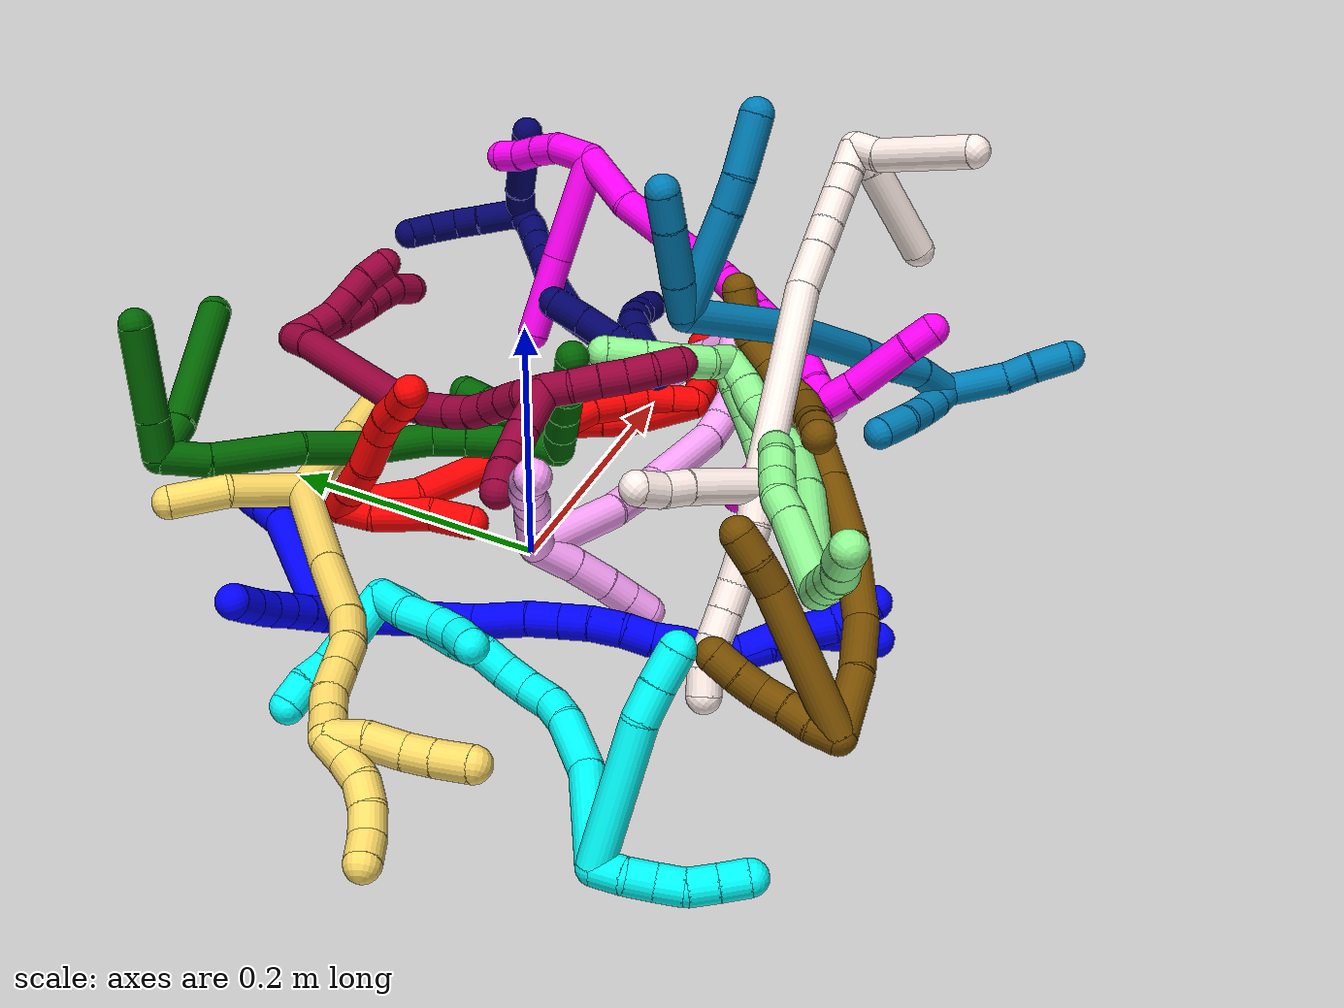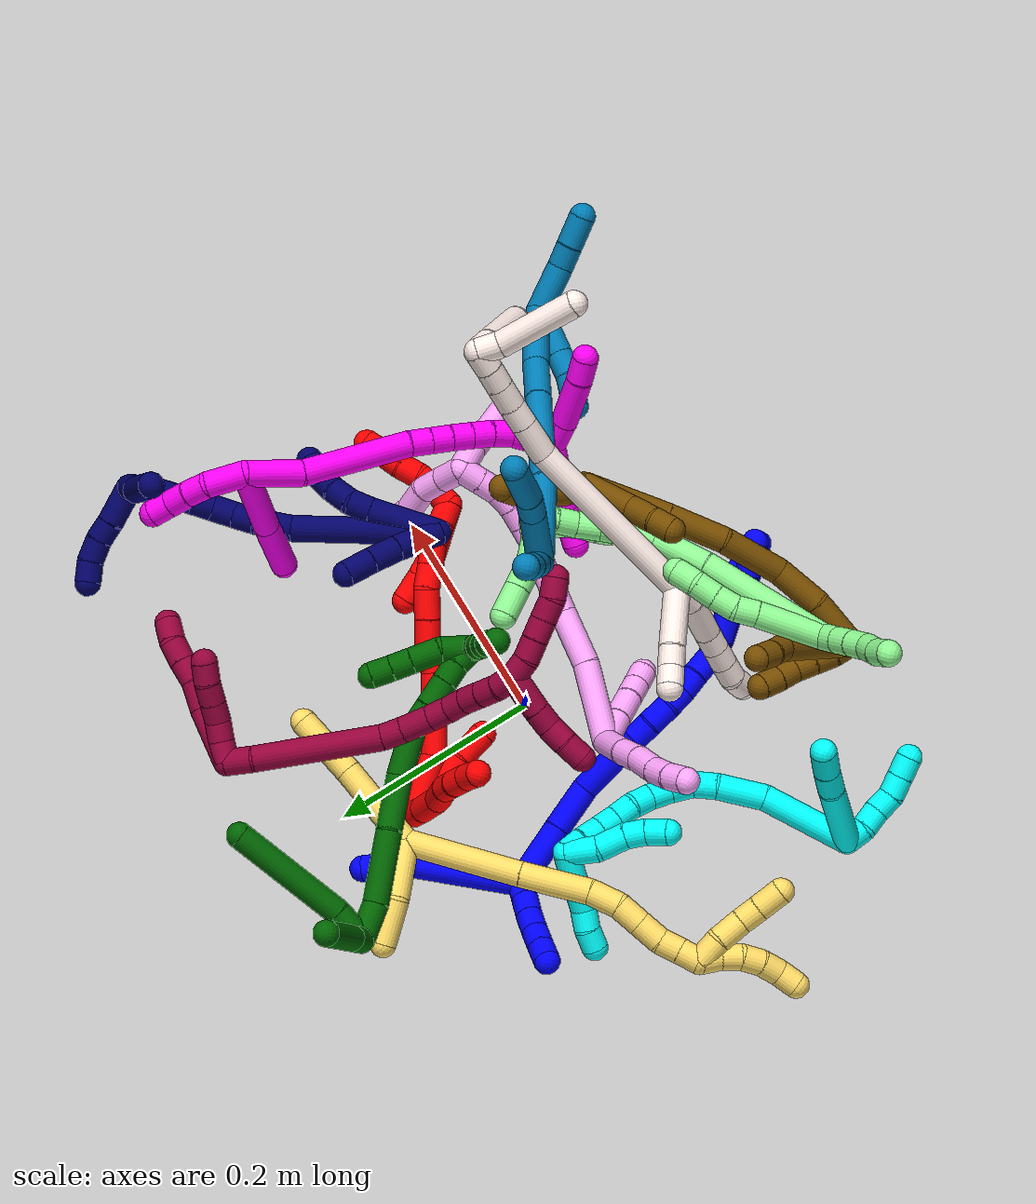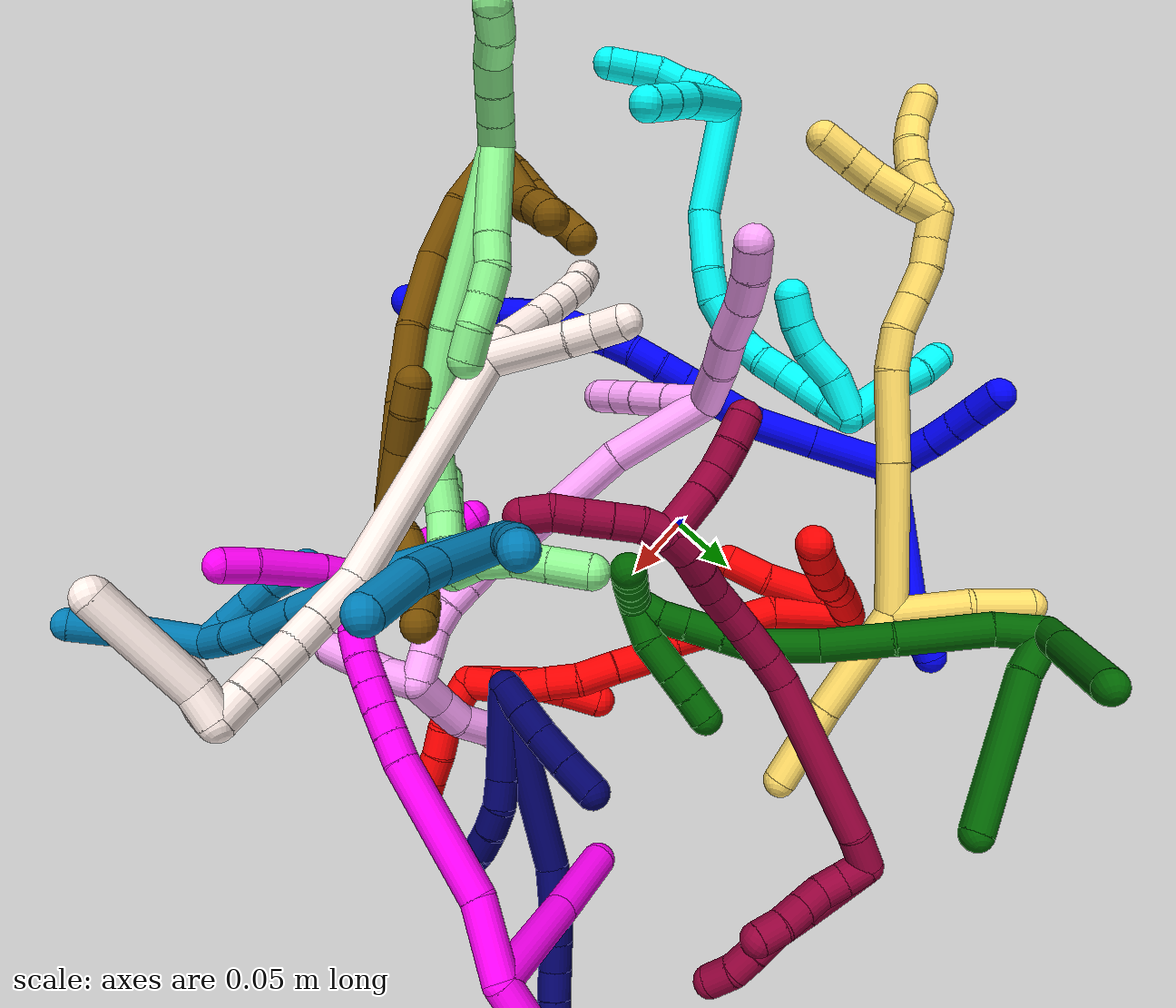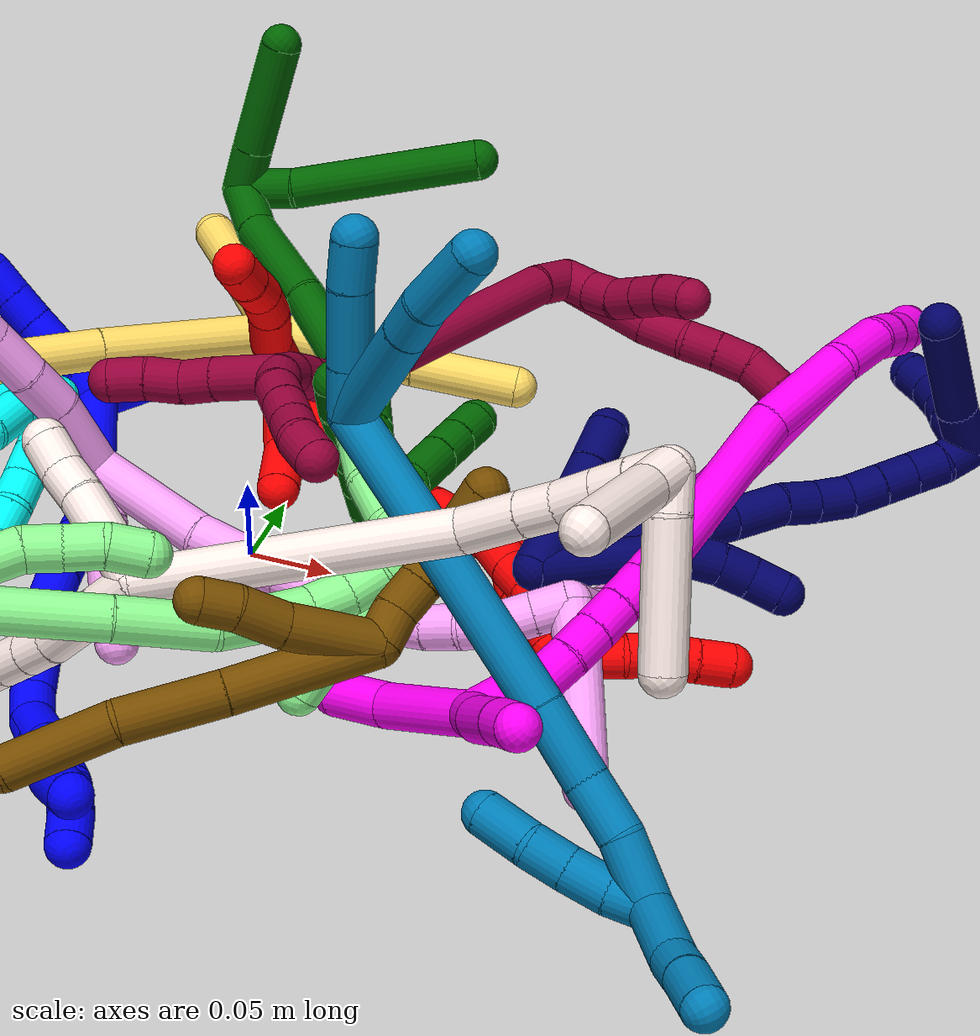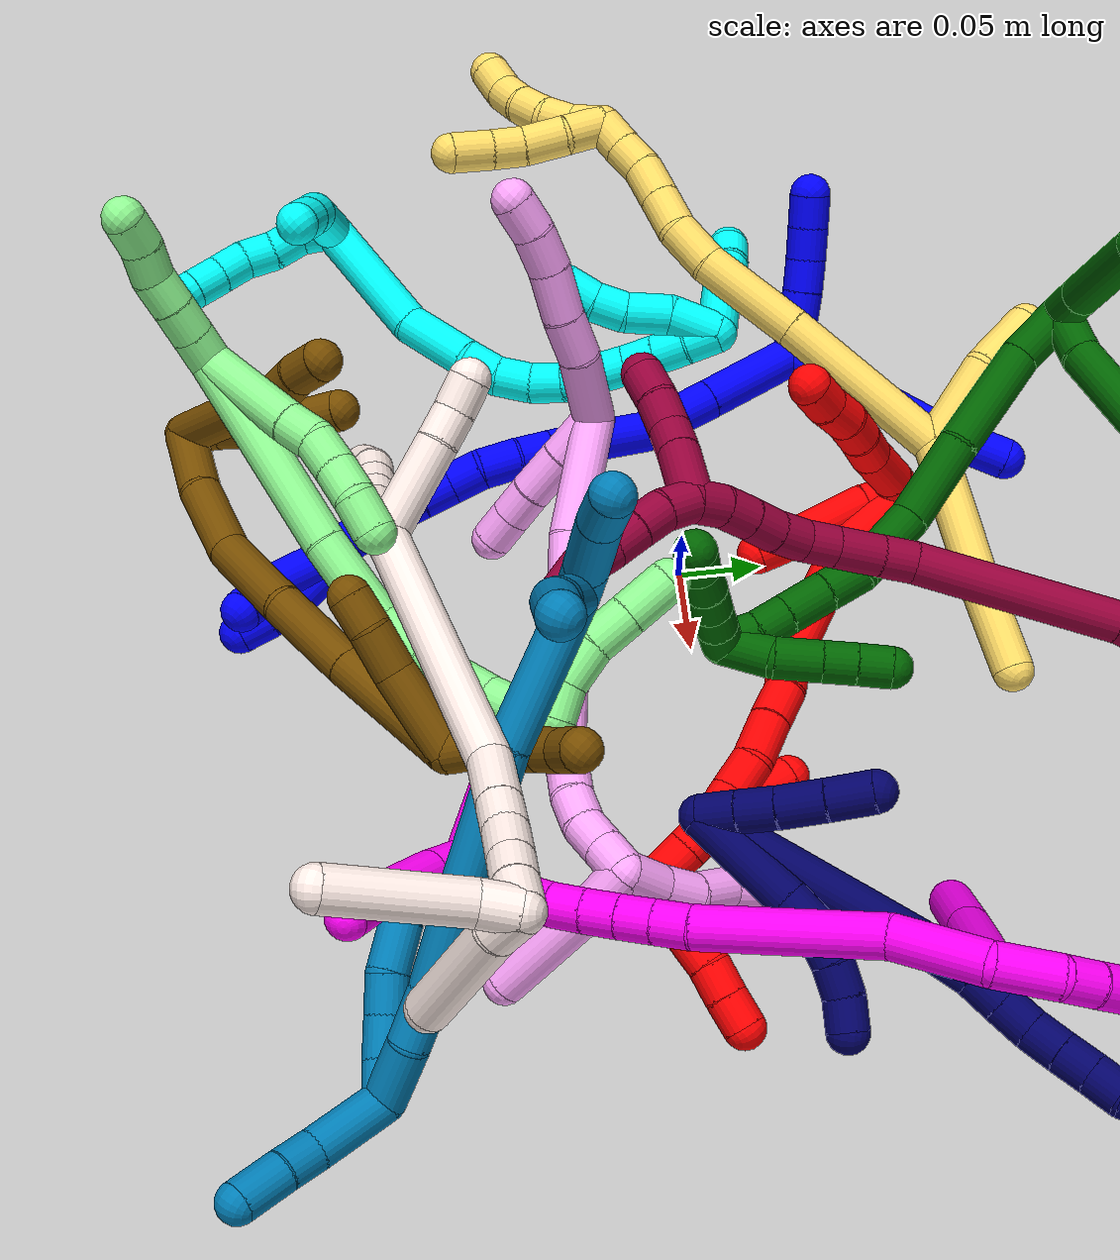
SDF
<sdf version="1.7">
 <world name="default">
  <plugin name="TubeGeneratorPlugin" filename="libtube_generator_plugin.so"/>
  <model name="photoneo_s_sensor">
   <static>1</static>
   <pose>0 0 2 1.57079 1.57079 3.14159</pose>
   <link name="link">
    <inertial><mass>0.1</mass></inertial>
    <sensor name="sensor" type="depth">
     <update_rate>30</update_rate>
     <camera>
      <horizontal_fov>1.22</horizontal_fov>
      <image><width>1920</width><height>1200</height><format>B8G8R8</format></image>
      <clip><near>0.1</near><far>4</far></clip>
      <depth_camera><output>points</output></depth_camera>
     </camera>
     <plugin name="camera_plugin" filename="libgazebo_ros_depth_camera.so">
      <baseline>0.2</baseline>
      <alwaysOn>1</alwaysOn>
      <updateRate>0.0</updateRate>
      <cameraName>camera_ir</cameraName>
      <imageTopicName>/camera/color/image_raw</imageTopicName>
      <cameraInfoTopicName>/camera/color/camera_info</cameraInfoTopicName>
      <depthImageTopicName>/camera/depth/image_raw</depthImageTopicName>
      <depthImageCameraInfoTopicName>/camera/depth/camera_info</depthImageCameraInfoTopicName>
      <pointCloudTopicName>/camera/depth/points</pointCloudTopicName>
      <frameName>fr_optical</frameName>
      <pointCloudCutoff>0.1</pointCloudCutoff>
      <pointCloudCutoffMax>2.0</pointCloudCutoffMax>
      <distortionK1>0</distortionK1>
      <distortionK2>0</distortionK2>
      <distortionK3>0</distortionK3>
      <distortionT1>0</distortionT1>
      <distortionT2>0</distortionT2>
      <CxPrime>0</CxPrime>
      <Cx>0</Cx>
      <Cy>0</Cy>
      <focalLength>0</focalLength>
      <hackBaseline>0</hackBaseline>
     </plugin>
    </sensor>
   </link>
  </model>
  <gravity>0 0 -9.8</gravity>
  <magnetic_field>6e-06 2.3e-05 -4.2e-05</magnetic_field>
  <atmosphere type="adiabatic"/>
  <physics name="default_physics" default="0" type="ode">
   <max_step_size>0.003</max_step_size>
   <real_time_factor>1</real_time_factor>
   <real_time_update_rate>1000</real_time_update_rate>
   <max_contacts>10000</max_contacts>
   <ode>
    <solver>
     <type>quick</type>
     <iters>100</iters>
     <sor>1.3</sor>
     <use_dynamic_moi_rescaling>0</use_dynamic_moi_rescaling>
    </solver>
    <constraints>
     <contact_max_correcting_vel>0</contact_max_correcting_vel>
     <contact_surface_layer>0.001</contact_surface_layer>
     <cfm>0</cfm>
     <erp>0.2</erp>
    </constraints>
   </ode>
  </physics>
  <scene><ambient>0.4 0.4 0.4 1</ambient><background>0.7 0.7 0.7 1</background><shadows>0</shadows></scene>
  <audio><device>default</device></audio>
  <spherical_coordinates>
   <surface_model>EARTH_WGS84</surface_model>
   <latitude_deg>0</latitude_deg>
   <longitude_deg>0</longitude_deg>
   <elevation>0</elevation>
   <heading_deg>0</heading_deg>
  </spherical_coordinates>
  <model name="bin">
   <static>1</static>
   <link name="bottom">
    <collision name="collision-bottom">
     <pose>0 0 -0.01 0 -0 0</pose>
     <geometry><box><size>0.8 0.6 0.02</size></box></geometry>
     <surface>
      <friction><ode><mu>100</mu><mu2>100</mu2></ode></friction>
      <contact><collide_bitmask>65535</collide_bitmask></contact>
     </surface>
    </collision>
   </link>
   <link name="west_wall">
    <collision name="collision-west_wall">
     <pose>-0.41 0 0.1 0 -0 0</pose>
     <geometry><box><size>0.02 0.6 0.2</size></box></geometry>
     <surface>
      <friction><ode><mu>100</mu><mu2>100</mu2></ode></friction>
      <contact><collide_bitmask>65535</collide_bitmask></contact>
     </surface>
    </collision>
   </link>
   <link name="east_wall">
    <collision name="collision-east_wall">
     <pose>0.41 0 0.1 0 -0 0</pose>
     <geometry><box><size>0.02 0.6 0.2</size></box></geometry>
     <surface>
      <friction><ode><mu>100</mu><mu2>100</mu2></ode></friction>
      <contact><collide_bitmask>65535</collide_bitmask></contact>
     </surface>
    </collision>
   </link>
   <link name="south_wall">
    <collision name="collision-south_wall">
     <pose>0 -0.31 0.1 0 -0 0</pose>
     <geometry><box><size>0.8 0.02 0.2</size></box></geometry>
     <surface>
      <friction><ode><mu>100</mu><mu2>100</mu2></ode></friction>
      <contact><collide_bitmask>65535</collide_bitmask></contact>
     </surface>
    </collision>
   </link>
   <link name="north_wall">
    <collision name="collision-north_wall">
     <pose>0 0.31 0.1 0 -0 0</pose>
     <geometry><box><size>0.8 0.02 0.2</size></box></geometry>
     <surface>
      <friction><ode><mu>100</mu><mu2>100</mu2></ode></friction>
      <contact><collide_bitmask>65535</collide_bitmask></contact>
     </surface>
    </collision>
   </link>
  </model>
  <model name="1">
   <static>0</static>
   <link name="1">
    <collision name="collision-cylinder-e_1_2_8">
     <pose>0.043706 0.028571 -0.001421 -1.62049 0.991251 -1.0334</pose>
     <geometry><cylinder><radius>0.0125</radius><length>0.10447</length></cylinder></geometry>
     <surface>
      <friction><ode><mu>1.16</mu><mu2>1.16</mu2><slip1>0</slip1><slip2>0</slip2></ode></friction>
      <contact><ode><kp>1e+06</kp><kd>1</kd><max_vel>0</max_vel><min_depth>0.001</min_depth></ode></contact>
     </surface>
    </collision>
    <visual name="visual-cylinder-e_1_2_8">
     <pose>0.043706 0.028571 -0.001421 -1.62049 0.991251 -1.0334</pose>
     <geometry><cylinder><radius>0.0125</radius><length>0.10447</length></cylinder></geometry>
     <material><ambient>0 0 1 1</ambient></material>
    </visual>
    <collision name="collision-cylinder-e_2_8_9">
     <pose>0.096751 0.061238 -0.006107 -2.24374 1.05966 -1.76497</pose>
     <geometry><cylinder><radius>0.0125</radius><length>0.021417</length></cylinder></geometry>
     <surface>
      <friction><ode><mu>1.16</mu><mu2>1.16</mu2><slip1>0</slip1><slip2>0</slip2></ode></friction>
      <contact><ode><kp>1e+06</kp><kd>1</kd><max_vel>0</max_vel><min_depth>0.001</min_depth></ode></contact>
     </surface>
    </collision>
    <visual name="visual-cylinder-e_2_8_9">
     <pose>0.096751 0.061238 -0.006107 -2.24374 1.05966 -1.76497</pose>
     <geometry><cylinder><radius>0.0125</radius><length>0.021417</length></cylinder></geometry>
     <material><ambient>0 0 1 1</ambient></material>
    </visual>
    <collision name="collision-cylinder-e_3_9_6">
     <pose>0.116647 0.069705 -0.013222 -2.29293 1.06658 -1.83517</pose>
     <geometry><cylinder><radius>0.0125</radius><length>0.024113</length></cylinder></geometry>
     <surface>
      <friction><ode><mu>1.16</mu><mu2>1.16</mu2><slip1>0</slip1><slip2>0</slip2></ode></friction>
      <contact><ode><kp>1e+06</kp><kd>1</kd><max_vel>0</max_vel><min_depth>0.001</min_depth></ode></contact>
     </surface>
    </collision>
    <visual name="visual-cylinder-e_3_9_6">
     <pose>0.116647 0.069705 -0.013222 -2.29293 1.06658 -1.83517</pose>
     <geometry><cylinder><radius>0.0125</radius><length>0.024113</length></cylinder></geometry>
     <material><ambient>0 0 1 1</ambient></material>
    </visual>
    <collision name="collision-cylinder-e_1_2_10">
     <pose>-0.006735 0.004429 -0.005918 -2.49905 -0.738948 1.72177</pose>
     <geometry><cylinder><radius>0.0125</radius><length>0.02</length></cylinder></geometry>
     <surface>
      <friction><ode><mu>1.16</mu><mu2>1.16</mu2><slip1>0</slip1><slip2>0</slip2></ode></friction>
      <contact><ode><kp>1e+06</kp><kd>1</kd><max_vel>0</max_vel><min_depth>0.001</min_depth></ode></contact>
     </surface>
    </collision>
    <visual name="visual-cylinder-e_1_2_10">
     <pose>-0.006735 0.004429 -0.005918 -2.49905 -0.738948 1.72177</pose>
     <geometry><cylinder><radius>0.0125</radius><length>0.02</length></cylinder></geometry>
     <material><ambient>0 0 1 1</ambient></material>
    </visual>
    <collision name="collision-cylinder-e_2_10_11">
     <pose>-0.020026 0.013265 -0.017968 -2.51857 -0.714954 1.71871</pose>
     <geometry><cylinder><radius>0.0125</radius><length>0.02</length></cylinder></geometry>
     <surface>
      <friction><ode><mu>1.16</mu><mu2>1.16</mu2><slip1>0</slip1><slip2>0</slip2></ode></friction>
      <contact><ode><kp>1e+06</kp><kd>1</kd><max_vel>0</max_vel><min_depth>0.001</min_depth></ode></contact>
     </surface>
    </collision>
    <visual name="visual-cylinder-e_2_10_11">
     <pose>-0.020026 0.013265 -0.017968 -2.51857 -0.714954 1.71871</pose>
     <geometry><cylinder><radius>0.0125</radius><length>0.02</length></cylinder></geometry>
     <material><ambient>0 0 1 1</ambient></material>
    </visual>
    <collision name="collision-cylinder-e_3_11_12">
     <pose>-0.03362 0.021723 -0.029935 -2.5346 -0.780805 1.84058</pose>
     <geometry><cylinder><radius>0.0125</radius><length>0.02</length></cylinder></geometry>
     <surface>
      <friction><ode><mu>1.16</mu><mu2>1.16</mu2><slip1>0</slip1><slip2>0</slip2></ode></friction>
      <contact><ode><kp>1e+06</kp><kd>1</kd><max_vel>0</max_vel><min_depth>0.001</min_depth></ode></contact>
     </surface>
    </collision>
    <visual name="visual-cylinder-e_3_11_12">
     <pose>-0.03362 0.021723 -0.029935 -2.5346 -0.780805 1.84058</pose>
     <geometry><cylinder><radius>0.0125</radius><length>0.02</length></cylinder></geometry>
     <material><ambient>0 0 1 1</ambient></material>
    </visual>
    <collision name="collision-cylinder-e_4_12_13">
     <pose>-0.047982 0.030322 -0.040838 -2.41029 -0.821705 1.69957</pose>
     <geometry><cylinder><radius>0.0125</radius><length>0.02</length></cylinder></geometry>
     <surface>
      <friction><ode><mu>1.16</mu><mu2>1.16</mu2><slip1>0</slip1><slip2>0</slip2></ode></friction>
      <contact><ode><kp>1e+06</kp><kd>1</kd><max_vel>0</max_vel><min_depth>0.001</min_depth></ode></contact>
     </surface>
    </collision>
    <visual name="visual-cylinder-e_4_12_13">
     <pose>-0.047982 0.030322 -0.040838 -2.41029 -0.821705 1.69957</pose>
     <geometry><cylinder><radius>0.0125</radius><length>0.02</length></cylinder></geometry>
     <material><ambient>0 0 1 1</ambient></material>
    </visual>
    <collision name="collision-cylinder-e_5_13_5">
     <pose>-0.062673 0.039598 -0.05074 -2.36729 -0.828274 1.64589</pose>
     <geometry><cylinder><radius>0.0125</radius><length>0.02</length></cylinder></geometry>
     <surface>
      <friction><ode><mu>1.16</mu><mu2>1.16</mu2><slip1>0</slip1><slip2>0</slip2></ode></friction>
      <contact><ode><kp>1e+06</kp><kd>1</kd><max_vel>0</max_vel><min_depth>0.001</min_depth></ode></contact>
     </surface>
    </collision>
    <visual name="visual-cylinder-e_5_13_5">
     <pose>-0.062673 0.039598 -0.05074 -2.36729 -0.828274 1.64589</pose>
     <geometry><cylinder><radius>0.0125</radius><length>0.02</length></cylinder></geometry>
     <material><ambient>0 0 1 1</ambient></material>
    </visual>
    <collision name="collision-cylinder-e_1_2_14">
     <pose>-0.007898 -0.01009 0.028397 0.341398 -0.256327 -0.044421</pose>
     <geometry><cylinder><radius>0.0125</radius><length>0.062308</length></cylinder></geometry>
     <surface>
      <friction><ode><mu>1.16</mu><mu2>1.16</mu2><slip1>0</slip1><slip2>0</slip2></ode></friction>
      <contact><ode><kp>1e+06</kp><kd>1</kd><max_vel>0</max_vel><min_depth>0.001</min_depth></ode></contact>
     </surface>
    </collision>
    <visual name="visual-cylinder-e_1_2_14">
     <pose>-0.007898 -0.01009 0.028397 0.341398 -0.256327 -0.044421</pose>
     <geometry><cylinder><radius>0.0125</radius><length>0.062308</length></cylinder></geometry>
     <material><ambient>0 0 1 1</ambient></material>
    </visual>
    <collision name="collision-cylinder-e_2_14_15">
     <pose>-0.021757 -0.027868 0.077418 0.356821 -0.264435 -0.047956</pose>
     <geometry><cylinder><radius>0.0125</radius><length>0.045606</length></cylinder></geometry>
     <surface>
      <friction><ode><mu>1.16</mu><mu2>1.16</mu2><slip1>0</slip1><slip2>0</slip2></ode></friction>
      <contact><ode><kp>1e+06</kp><kd>1</kd><max_vel>0</max_vel><min_depth>0.001</min_depth></ode></contact>
     </surface>
    </collision>
    <visual name="visual-cylinder-e_2_14_15">
     <pose>-0.021757 -0.027868 0.077418 0.356821 -0.264435 -0.047956</pose>
     <geometry><cylinder><radius>0.0125</radius><length>0.045606</length></cylinder></geometry>
     <material><ambient>0 0 1 1</ambient></material>
    </visual>
    <collision name="collision-cylinder-e_3_15_16">
     <pose>-0.038424 -0.038472 0.115464 0.165865 -0.544955 -0.046445</pose>
     <geometry><cylinder><radius>0.0125</radius><length>0.041312</length></cylinder></geometry>
     <surface>
      <friction><ode><mu>1.16</mu><mu2>1.16</mu2><slip1>0</slip1><slip2>0</slip2></ode></friction>
      <contact><ode><kp>1e+06</kp><kd>1</kd><max_vel>0</max_vel><min_depth>0.001</min_depth></ode></contact>
     </surface>
    </collision>
    <visual name="visual-cylinder-e_3_15_16">
     <pose>-0.038424 -0.038472 0.115464 0.165865 -0.544955 -0.046445</pose>
     <geometry><cylinder><radius>0.0125</radius><length>0.041312</length></cylinder></geometry>
     <material><ambient>0 0 1 1</ambient></material>
    </visual>
    <collision name="collision-cylinder-e_4_16_17">
     <pose>-0.054973 -0.044773 0.142826 0.328102 -0.507644 -0.085834</pose>
     <geometry><cylinder><radius>0.0125</radius><length>0.024033</length></cylinder></geometry>
     <surface>
      <friction><ode><mu>1.16</mu><mu2>1.16</mu2><slip1>0</slip1><slip2>0</slip2></ode></friction>
      <contact><ode><kp>1e+06</kp><kd>1</kd><max_vel>0</max_vel><min_depth>0.001</min_depth></ode></contact>
     </surface>
    </collision>
    <visual name="visual-cylinder-e_4_16_17">
     <pose>-0.054973 -0.044773 0.142826 0.328102 -0.507644 -0.085834</pose>
     <geometry><cylinder><radius>0.0125</radius><length>0.024033</length></cylinder></geometry>
     <material><ambient>0 0 1 1</ambient></material>
    </visual>
    <collision name="collision-cylinder-e_5_17_18">
     <pose>-0.065722 -0.051036 0.161324 0.324574 -0.497867 -0.083193</pose>
     <geometry><cylinder><radius>0.0125</radius><length>0.020552</length></cylinder></geometry>
     <surface>
      <friction><ode><mu>1.16</mu><mu2>1.16</mu2><slip1>0</slip1><slip2>0</slip2></ode></friction>
      <contact><ode><kp>1e+06</kp><kd>1</kd><max_vel>0</max_vel><min_depth>0.001</min_depth></ode></contact>
     </surface>
    </collision>
    <visual name="visual-cylinder-e_5_17_18">
     <pose>-0.065722 -0.051036 0.161324 0.324574 -0.497867 -0.083193</pose>
     <geometry><cylinder><radius>0.0125</radius><length>0.020552</length></cylinder></geometry>
     <material><ambient>0 0 1 1</ambient></material>
    </visual>
    <collision name="collision-cylinder-e_6_18_19">
     <pose>-0.075656 -0.058921 0.179521 0.478931 -0.433377 -0.107394</pose>
     <geometry><cylinder><radius>0.0125</radius><length>0.023938</length></cylinder></geometry>
     <surface>
      <friction><ode><mu>1.16</mu><mu2>1.16</mu2><slip1>0</slip1><slip2>0</slip2></ode></friction>
      <contact><ode><kp>1e+06</kp><kd>1</kd><max_vel>0</max_vel><min_depth>0.001</min_depth></ode></contact>
     </surface>
    </collision>
    <visual name="visual-cylinder-e_6_18_19">
     <pose>-0.075656 -0.058921 0.179521 0.478931 -0.433377 -0.107394</pose>
     <geometry><cylinder><radius>0.0125</radius><length>0.023938</length></cylinder></geometry>
     <material><ambient>0 0 1 1</ambient></material>
    </visual>
    <collision name="collision-cylinder-e_7_19_20">
     <pose>-0.08324 -0.069911 0.197172 0.641626 -0.250464 -0.083616</pose>
     <geometry><cylinder><radius>0.0125</radius><length>0.020642</length></cylinder></geometry>
     <surface>
      <friction><ode><mu>1.16</mu><mu2>1.16</mu2><slip1>0</slip1><slip2>0</slip2></ode></friction>
      <contact><ode><kp>1e+06</kp><kd>1</kd><max_vel>0</max_vel><min_depth>0.001</min_depth></ode></contact>
     </surface>
    </collision>
    <visual name="visual-cylinder-e_7_19_20">
     <pose>-0.08324 -0.069911 0.197172 0.641626 -0.250464 -0.083616</pose>
     <geometry><cylinder><radius>0.0125</radius><length>0.020642</length></cylinder></geometry>
     <material><ambient>0 0 1 1</ambient></material>
    </visual>
    <collision name="collision-cylinder-e_8_20_21">
     <pose>-0.088492 -0.080186 0.214011 0.452354 -0.267812 -0.061978</pose>
     <geometry><cylinder><radius>0.0125</radius><length>0.020358</length></cylinder></geometry>
     <surface>
      <friction><ode><mu>1.16</mu><mu2>1.16</mu2><slip1>0</slip1><slip2>0</slip2></ode></friction>
      <contact><ode><kp>1e+06</kp><kd>1</kd><max_vel>0</max_vel><min_depth>0.001</min_depth></ode></contact>
     </surface>
    </collision>
    <visual name="visual-cylinder-e_8_20_21">
     <pose>-0.088492 -0.080186 0.214011 0.452354 -0.267812 -0.061978</pose>
     <geometry><cylinder><radius>0.0125</radius><length>0.020358</length></cylinder></geometry>
     <material><ambient>0 0 1 1</ambient></material>
    </visual>
    <collision name="collision-cylinder-e_9_21_22">
     <pose>-0.09373 -0.08998 0.231555 0.563267 -0.242042 -0.070343</pose>
     <geometry><cylinder><radius>0.0125</radius><length>0.021232</length></cylinder></geometry>
     <surface>
      <friction><ode><mu>1.16</mu><mu2>1.16</mu2><slip1>0</slip1><slip2>0</slip2></ode></friction>
      <contact><ode><kp>1e+06</kp><kd>1</kd><max_vel>0</max_vel><min_depth>0.001</min_depth></ode></contact>
     </surface>
    </collision>
    <visual name="visual-cylinder-e_9_21_22">
     <pose>-0.09373 -0.08998 0.231555 0.563267 -0.242042 -0.070343</pose>
     <geometry><cylinder><radius>0.0125</radius><length>0.021232</length></cylinder></geometry>
     <material><ambient>0 0 1 1</ambient></material>
    </visual>
    <collision name="collision-cylinder-e_10_22_1">
     <pose>-0.098332 -0.098961 0.249426 0.363046 -0.207043 -0.038133</pose>
     <geometry><cylinder><radius>0.0125</radius><length>0.020019</length></cylinder></geometry>
     <surface>
      <friction><ode><mu>1.16</mu><mu2>1.16</mu2><slip1>0</slip1><slip2>0</slip2></ode></friction>
      <contact><ode><kp>1e+06</kp><kd>1</kd><max_vel>0</max_vel><min_depth>0.001</min_depth></ode></contact>
     </surface>
    </collision>
    <visual name="visual-cylinder-e_10_22_1">
     <pose>-0.098332 -0.098961 0.249426 0.363046 -0.207043 -0.038133</pose>
     <geometry><cylinder><radius>0.0125</radius><length>0.020019</length></cylinder></geometry>
     <material><ambient>0 0 1 1</ambient></material>
    </visual>
    <collision name="collision-cylinder-e_1_1_23">
     <pose>-0.102145 -0.101255 0.274116 -0.076131 -0.11222 0.004278</pose>
     <geometry><cylinder><radius>0.0125</radius><length>0.031353</length></cylinder></geometry>
     <surface>
      <friction><ode><mu>1.16</mu><mu2>1.16</mu2><slip1>0</slip1><slip2>0</slip2></ode></friction>
      <contact><ode><kp>1e+06</kp><kd>1</kd><max_vel>0</max_vel><min_depth>0.001</min_depth></ode></contact>
     </surface>
    </collision>
    <visual name="visual-cylinder-e_1_1_23">
     <pose>-0.102145 -0.101255 0.274116 -0.076131 -0.11222 0.004278</pose>
     <geometry><cylinder><radius>0.0125</radius><length>0.031353</length></cylinder></geometry>
     <material><ambient>0 0 1 1</ambient></material>
    </visual>
    <collision name="collision-cylinder-e_2_23_24">
     <pose>-0.109351 -0.101138 0.307933 0.058328 -0.289247 -0.008497</pose>
     <geometry><cylinder><radius>0.0125</radius><length>0.038218</length></cylinder></geometry>
     <surface>
      <friction><ode><mu>1.16</mu><mu2>1.16</mu2><slip1>0</slip1><slip2>0</slip2></ode></friction>
      <contact><ode><kp>1e+06</kp><kd>1</kd><max_vel>0</max_vel><min_depth>0.001</min_depth></ode></contact>
     </surface>
    </collision>
    <visual name="visual-cylinder-e_2_23_24">
     <pose>-0.109351 -0.101138 0.307933 0.058328 -0.289247 -0.008497</pose>
     <geometry><cylinder><radius>0.0125</radius><length>0.038218</length></cylinder></geometry>
     <material><ambient>0 0 1 1</ambient></material>
    </visual>
    <collision name="collision-cylinder-e_3_24_4">
     <pose>-0.116238 -0.099321 0.341086 -0.191595 -0.094542 0.009091</pose>
     <geometry><cylinder><radius>0.0125</radius><length>0.030429</length></cylinder></geometry>
     <surface>
      <friction><ode><mu>1.16</mu><mu2>1.16</mu2><slip1>0</slip1><slip2>0</slip2></ode></friction>
      <contact><ode><kp>1e+06</kp><kd>1</kd><max_vel>0</max_vel><min_depth>0.001</min_depth></ode></contact>
     </surface>
    </collision>
    <visual name="visual-cylinder-e_3_24_4">
     <pose>-0.116238 -0.099321 0.341086 -0.191595 -0.094542 0.009091</pose>
     <geometry><cylinder><radius>0.0125</radius><length>0.030429</length></cylinder></geometry>
     <material><ambient>0 0 1 1</ambient></material>
    </visual>
    <collision name="collision-cylinder-e_1_1_25">
     <pose>-0.101528 -0.102838 0.26851 0.040075 -0.114112 -0.002289</pose>
     <geometry><cylinder><radius>0.0125</radius><length>0.02</length></cylinder></geometry>
     <surface>
      <friction><ode><mu>1.16</mu><mu2>1.16</mu2><slip1>0</slip1><slip2>0</slip2></ode></friction>
      <contact><ode><kp>1e+06</kp><kd>1</kd><max_vel>0</max_vel><min_depth>0.001</min_depth></ode></contact>
     </surface>
    </collision>
    <visual name="visual-cylinder-e_1_1_25">
     <pose>-0.101528 -0.102838 0.26851 0.040075 -0.114112 -0.002289</pose>
     <geometry><cylinder><radius>0.0125</radius><length>0.02</length></cylinder></geometry>
     <material><ambient>0 0 1 1</ambient></material>
    </visual>
    <collision name="collision-cylinder-e_2_25_26">
     <pose>-0.101065 -0.104456 0.288233 0.12389 0.160902 0.010001</pose>
     <geometry><cylinder><radius>0.0125</radius><length>0.02</length></cylinder></geometry>
     <surface>
      <friction><ode><mu>1.16</mu><mu2>1.16</mu2><slip1>0</slip1><slip2>0</slip2></ode></friction>
      <contact><ode><kp>1e+06</kp><kd>1</kd><max_vel>0</max_vel><min_depth>0.001</min_depth></ode></contact>
     </surface>
    </collision>
    <visual name="visual-cylinder-e_2_25_26">
     <pose>-0.101065 -0.104456 0.288233 0.12389 0.160902 0.010001</pose>
     <geometry><cylinder><radius>0.0125</radius><length>0.02</length></cylinder></geometry>
     <material><ambient>0 0 1 1</ambient></material>
    </visual>
    <collision name="collision-cylinder-e_3_26_27">
     <pose>-0.099381 -0.106845 0.307959 0.117207 0.008161 0.000479</pose>
     <geometry><cylinder><radius>0.0125</radius><length>0.02</length></cylinder></geometry>
     <surface>
      <friction><ode><mu>1.16</mu><mu2>1.16</mu2><slip1>0</slip1><slip2>0</slip2></ode></friction>
      <contact><ode><kp>1e+06</kp><kd>1</kd><max_vel>0</max_vel><min_depth>0.001</min_depth></ode></contact>
     </surface>
    </collision>
    <visual name="visual-cylinder-e_3_26_27">
     <pose>-0.099381 -0.106845 0.307959 0.117207 0.008161 0.000479</pose>
     <geometry><cylinder><radius>0.0125</radius><length>0.02</length></cylinder></geometry>
     <material><ambient>0 0 1 1</ambient></material>
    </visual>
    <collision name="collision-cylinder-e_4_27_28">
     <pose>-0.100196 -0.112248 0.326905 0.43902 -0.089784 -0.020044</pose>
     <geometry><cylinder><radius>0.0125</radius><length>0.02</length></cylinder></geometry>
     <surface>
      <friction><ode><mu>1.16</mu><mu2>1.16</mu2><slip1>0</slip1><slip2>0</slip2></ode></friction>
      <contact><ode><kp>1e+06</kp><kd>1</kd><max_vel>0</max_vel><min_depth>0.001</min_depth></ode></contact>
     </surface>
    </collision>
    <visual name="visual-cylinder-e_4_27_28">
     <pose>-0.100196 -0.112248 0.326905 0.43902 -0.089784 -0.020044</pose>
     <geometry><cylinder><radius>0.0125</radius><length>0.02</length></cylinder></geometry>
     <material><ambient>0 0 1 1</ambient></material>
    </visual>
    <collision name="collision-cylinder-e_5_28_3">
     <pose>-0.103542 -0.121035 0.34448 0.488966 -0.247439 -0.062026</pose>
     <geometry><cylinder><radius>0.0125</radius><length>0.02</length></cylinder></geometry>
     <surface>
      <friction><ode><mu>1.16</mu><mu2>1.16</mu2><slip1>0</slip1><slip2>0</slip2></ode></friction>
      <contact><ode><kp>1e+06</kp><kd>1</kd><max_vel>0</max_vel><min_depth>0.001</min_depth></ode></contact>
     </surface>
    </collision>
    <visual name="visual-cylinder-e_5_28_3">
     <pose>-0.103542 -0.121035 0.34448 0.488966 -0.247439 -0.062026</pose>
     <geometry><cylinder><radius>0.0125</radius><length>0.02</length></cylinder></geometry>
     <material><ambient>0 0 1 1</ambient></material>
    </visual>
    <collision name="collision-sphere-3">
     <pose>-0.105991 -0.125589 0.353039 0 -0 0</pose>
     <geometry><sphere><radius>0.0125</radius></sphere></geometry>
     <surface>
      <friction><ode><mu>1.16</mu><mu2>1.16</mu2><slip1>0</slip1><slip2>0</slip2></ode></friction>
      <contact><ode><kp>1e+06</kp><kd>1</kd><max_vel>0</max_vel><min_depth>0.001</min_depth></ode></contact>
     </surface>
    </collision>
    <visual name="visual-sphere-3">
     <pose>-0.105991 -0.125589 0.353039 0 -0 0</pose>
     <geometry><sphere><radius>0.0125</radius></sphere></geometry>
     <material><ambient>0 0 1 1</ambient></material>
    </visual>
    <collision name="collision-sphere-28">
     <pose>-0.101093 -0.116481 0.33592 0 -0 0</pose>
     <geometry><sphere><radius>0.0125</radius></sphere></geometry>
     <surface>
      <friction><ode><mu>1.16</mu><mu2>1.16</mu2><slip1>0</slip1><slip2>0</slip2></ode></friction>
      <contact><ode><kp>1e+06</kp><kd>1</kd><max_vel>0</max_vel><min_depth>0.001</min_depth></ode></contact>
     </surface>
    </collision>
    <visual name="visual-sphere-28">
     <pose>-0.101093 -0.116481 0.33592 0 -0 0</pose>
     <geometry><sphere><radius>0.0125</radius></sphere></geometry>
     <material><ambient>0 0 1 1</ambient></material>
    </visual>
    <collision name="collision-sphere-27">
     <pose>-0.099299 -0.108014 0.31789 0 -0 0</pose>
     <geometry><sphere><radius>0.0125</radius></sphere></geometry>
     <surface>
      <friction><ode><mu>1.16</mu><mu2>1.16</mu2><slip1>0</slip1><slip2>0</slip2></ode></friction>
      <contact><ode><kp>1e+06</kp><kd>1</kd><max_vel>0</max_vel><min_depth>0.001</min_depth></ode></contact>
     </surface>
    </collision>
    <visual name="visual-sphere-27">
     <pose>-0.099299 -0.108014 0.31789 0 -0 0</pose>
     <geometry><sphere><radius>0.0125</radius></sphere></geometry>
     <material><ambient>0 0 1 1</ambient></material>
    </visual>
    <collision name="collision-sphere-26">
     <pose>-0.099463 -0.105676 0.298028 0 -0 0</pose>
     <geometry><sphere><radius>0.0125</radius></sphere></geometry>
     <surface>
      <friction><ode><mu>1.16</mu><mu2>1.16</mu2><slip1>0</slip1><slip2>0</slip2></ode></friction>
      <contact><ode><kp>1e+06</kp><kd>1</kd><max_vel>0</max_vel><min_depth>0.001</min_depth></ode></contact>
     </surface>
    </collision>
    <visual name="visual-sphere-26">
     <pose>-0.099463 -0.105676 0.298028 0 -0 0</pose>
     <geometry><sphere><radius>0.0125</radius></sphere></geometry>
     <material><ambient>0 0 1 1</ambient></material>
    </visual>
    <collision name="collision-sphere-25">
     <pose>-0.102667 -0.103236 0.278437 0 -0 0</pose>
     <geometry><sphere><radius>0.0125</radius></sphere></geometry>
     <surface>
      <friction><ode><mu>1.16</mu><mu2>1.16</mu2><slip1>0</slip1><slip2>0</slip2></ode></friction>
      <contact><ode><kp>1e+06</kp><kd>1</kd><max_vel>0</max_vel><min_depth>0.001</min_depth></ode></contact>
     </surface>
    </collision>
    <visual name="visual-sphere-25">
     <pose>-0.102667 -0.103236 0.278437 0 -0 0</pose>
     <geometry><sphere><radius>0.0125</radius></sphere></geometry>
     <material><ambient>0 0 1 1</ambient></material>
    </visual>
    <collision name="collision-sphere-4">
     <pose>-0.117674 -0.096437 0.355956 0 -0 0</pose>
     <geometry><sphere><radius>0.0125</radius></sphere></geometry>
     <surface>
      <friction><ode><mu>1.16</mu><mu2>1.16</mu2><slip1>0</slip1><slip2>0</slip2></ode></friction>
      <contact><ode><kp>1e+06</kp><kd>1</kd><max_vel>0</max_vel><min_depth>0.001</min_depth></ode></contact>
     </surface>
    </collision>
    <visual name="visual-sphere-4">
     <pose>-0.117674 -0.096437 0.355956 0 -0 0</pose>
     <geometry><sphere><radius>0.0125</radius></sphere></geometry>
     <material><ambient>0 0 1 1</ambient></material>
    </visual>
    <collision name="collision-sphere-24">
     <pose>-0.114801 -0.102206 0.326217 0 -0 0</pose>
     <geometry><sphere><radius>0.0125</radius></sphere></geometry>
     <surface>
      <friction><ode><mu>1.16</mu><mu2>1.16</mu2><slip1>0</slip1><slip2>0</slip2></ode></friction>
      <contact><ode><kp>1e+06</kp><kd>1</kd><max_vel>0</max_vel><min_depth>0.001</min_depth></ode></contact>
     </surface>
    </collision>
    <visual name="visual-sphere-24">
     <pose>-0.114801 -0.102206 0.326217 0 -0 0</pose>
     <geometry><sphere><radius>0.0125</radius></sphere></geometry>
     <material><ambient>0 0 1 1</ambient></material>
    </visual>
    <collision name="collision-sphere-23">
     <pose>-0.103901 -0.10007 0.289649 0 -0 0</pose>
     <geometry><sphere><radius>0.0125</radius></sphere></geometry>
     <surface>
      <friction><ode><mu>1.16</mu><mu2>1.16</mu2><slip1>0</slip1><slip2>0</slip2></ode></friction>
      <contact><ode><kp>1e+06</kp><kd>1</kd><max_vel>0</max_vel><min_depth>0.001</min_depth></ode></contact>
     </surface>
    </collision>
    <visual name="visual-sphere-23">
     <pose>-0.103901 -0.10007 0.289649 0 -0 0</pose>
     <geometry><sphere><radius>0.0125</radius></sphere></geometry>
     <material><ambient>0 0 1 1</ambient></material>
    </visual>
    <collision name="collision-sphere-1">
     <pose>-0.10039 -0.10244 0.258583 0 -0 0</pose>
     <geometry><sphere><radius>0.0125</radius></sphere></geometry>
     <surface>
      <friction><ode><mu>1.16</mu><mu2>1.16</mu2><slip1>0</slip1><slip2>0</slip2></ode></friction>
      <contact><ode><kp>1e+06</kp><kd>1</kd><max_vel>0</max_vel><min_depth>0.001</min_depth></ode></contact>
     </surface>
    </collision>
    <visual name="visual-sphere-1">
     <pose>-0.10039 -0.10244 0.258583 0 -0 0</pose>
     <geometry><sphere><radius>0.0125</radius></sphere></geometry>
     <material><ambient>0 0 1 1</ambient></material>
    </visual>
    <collision name="collision-sphere-22">
     <pose>-0.096274 -0.095483 0.240269 0 -0 0</pose>
     <geometry><sphere><radius>0.0125</radius></sphere></geometry>
     <surface>
      <friction><ode><mu>1.16</mu><mu2>1.16</mu2><slip1>0</slip1><slip2>0</slip2></ode></friction>
      <contact><ode><kp>1e+06</kp><kd>1</kd><max_vel>0</max_vel><min_depth>0.001</min_depth></ode></contact>
     </surface>
    </collision>
    <visual name="visual-sphere-22">
     <pose>-0.096274 -0.095483 0.240269 0 -0 0</pose>
     <geometry><sphere><radius>0.0125</radius></sphere></geometry>
     <material><ambient>0 0 1 1</ambient></material>
    </visual>
    <collision name="collision-sphere-21">
     <pose>-0.091185 -0.084476 0.22284 0 -0 0</pose>
     <geometry><sphere><radius>0.0125</radius></sphere></geometry>
     <surface>
      <friction><ode><mu>1.16</mu><mu2>1.16</mu2><slip1>0</slip1><slip2>0</slip2></ode></friction>
      <contact><ode><kp>1e+06</kp><kd>1</kd><max_vel>0</max_vel><min_depth>0.001</min_depth></ode></contact>
     </surface>
    </collision>
    <visual name="visual-sphere-21">
     <pose>-0.091185 -0.084476 0.22284 0 -0 0</pose>
     <geometry><sphere><radius>0.0125</radius></sphere></geometry>
     <material><ambient>0 0 1 1</ambient></material>
    </visual>
    <collision name="collision-sphere-11">
     <pose>-0.026582 0.017671 -0.0241 0 -0 0</pose>
     <geometry><sphere><radius>0.0125</radius></sphere></geometry>
     <surface>
      <friction><ode><mu>1.16</mu><mu2>1.16</mu2><slip1>0</slip1><slip2>0</slip2></ode></friction>
      <contact><ode><kp>1e+06</kp><kd>1</kd><max_vel>0</max_vel><min_depth>0.001</min_depth></ode></contact>
     </surface>
    </collision>
    <visual name="visual-sphere-11">
     <pose>-0.026582 0.017671 -0.0241 0 -0 0</pose>
     <geometry><sphere><radius>0.0125</radius></sphere></geometry>
     <material><ambient>0 0 1 1</ambient></material>
    </visual>
    <collision name="collision-sphere-10">
     <pose>-0.01347 0.008859 -0.011835 0 -0 0</pose>
     <geometry><sphere><radius>0.0125</radius></sphere></geometry>
     <surface>
      <friction><ode><mu>1.16</mu><mu2>1.16</mu2><slip1>0</slip1><slip2>0</slip2></ode></friction>
      <contact><ode><kp>1e+06</kp><kd>1</kd><max_vel>0</max_vel><min_depth>0.001</min_depth></ode></contact>
     </surface>
    </collision>
    <visual name="visual-sphere-10">
     <pose>-0.01347 0.008859 -0.011835 0 -0 0</pose>
     <geometry><sphere><radius>0.0125</radius></sphere></geometry>
     <material><ambient>0 0 1 1</ambient></material>
    </visual>
    <collision name="collision-sphere-6">
     <pose>0.127203 0.074076 -0.017072 0 -0 0</pose>
     <geometry><sphere><radius>0.0125</radius></sphere></geometry>
     <surface>
      <friction><ode><mu>1.16</mu><mu2>1.16</mu2><slip1>0</slip1><slip2>0</slip2></ode></friction>
      <contact><ode><kp>1e+06</kp><kd>1</kd><max_vel>0</max_vel><min_depth>0.001</min_depth></ode></contact>
     </surface>
    </collision>
    <visual name="visual-sphere-6">
     <pose>0.127203 0.074076 -0.017072 0 -0 0</pose>
     <geometry><sphere><radius>0.0125</radius></sphere></geometry>
     <material><ambient>0 0 1 1</ambient></material>
    </visual>
    <collision name="collision-sphere-9">
     <pose>0.106091 0.065334 -0.009372 0 -0 0</pose>
     <geometry><sphere><radius>0.0125</radius></sphere></geometry>
     <surface>
      <friction><ode><mu>1.16</mu><mu2>1.16</mu2><slip1>0</slip1><slip2>0</slip2></ode></friction>
      <contact><ode><kp>1e+06</kp><kd>1</kd><max_vel>0</max_vel><min_depth>0.001</min_depth></ode></contact>
     </surface>
    </collision>
    <visual name="visual-sphere-9">
     <pose>0.106091 0.065334 -0.009372 0 -0 0</pose>
     <geometry><sphere><radius>0.0125</radius></sphere></geometry>
     <material><ambient>0 0 1 1</ambient></material>
    </visual>
    <collision name="collision-sphere-2">
     <geometry><sphere><radius>0.0125</radius></sphere></geometry>
     <surface>
      <friction><ode><mu>1.16</mu><mu2>1.16</mu2><slip1>0</slip1><slip2>0</slip2></ode></friction>
      <contact><ode><kp>1e+06</kp><kd>1</kd><max_vel>0</max_vel><min_depth>0.001</min_depth></ode></contact>
     </surface>
    </collision>
    <visual name="visual-sphere-2">
     <geometry><sphere><radius>0.0125</radius></sphere></geometry>
     <material><ambient>0 0 1 1</ambient></material>
    </visual>
    <collision name="collision-sphere-19">
     <pose>-0.080682 -0.063926 0.189162 0 -0 0</pose>
     <geometry><sphere><radius>0.0125</radius></sphere></geometry>
     <surface>
      <friction><ode><mu>1.16</mu><mu2>1.16</mu2><slip1>0</slip1><slip2>0</slip2></ode></friction>
      <contact><ode><kp>1e+06</kp><kd>1</kd><max_vel>0</max_vel><min_depth>0.001</min_depth></ode></contact>
     </surface>
    </collision>
    <visual name="visual-sphere-19">
     <pose>-0.080682 -0.063926 0.189162 0 -0 0</pose>
     <geometry><sphere><radius>0.0125</radius></sphere></geometry>
     <material><ambient>0 0 1 1</ambient></material>
    </visual>
    <collision name="collision-sphere-8">
     <pose>0.087411 0.057142 -0.002842 0 -0 0</pose>
     <geometry><sphere><radius>0.0125</radius></sphere></geometry>
     <surface>
      <friction><ode><mu>1.16</mu><mu2>1.16</mu2><slip1>0</slip1><slip2>0</slip2></ode></friction>
      <contact><ode><kp>1e+06</kp><kd>1</kd><max_vel>0</max_vel><min_depth>0.001</min_depth></ode></contact>
     </surface>
    </collision>
    <visual name="visual-sphere-8">
     <pose>0.087411 0.057142 -0.002842 0 -0 0</pose>
     <geometry><sphere><radius>0.0125</radius></sphere></geometry>
     <material><ambient>0 0 1 1</ambient></material>
    </visual>
    <collision name="collision-sphere-12">
     <pose>-0.040659 0.025775 -0.035769 0 -0 0</pose>
     <geometry><sphere><radius>0.0125</radius></sphere></geometry>
     <surface>
      <friction><ode><mu>1.16</mu><mu2>1.16</mu2><slip1>0</slip1><slip2>0</slip2></ode></friction>
      <contact><ode><kp>1e+06</kp><kd>1</kd><max_vel>0</max_vel><min_depth>0.001</min_depth></ode></contact>
     </surface>
    </collision>
    <visual name="visual-sphere-12">
     <pose>-0.040659 0.025775 -0.035769 0 -0 0</pose>
     <geometry><sphere><radius>0.0125</radius></sphere></geometry>
     <material><ambient>0 0 1 1</ambient></material>
    </visual>
    <collision name="collision-sphere-13">
     <pose>-0.055305 0.03487 -0.045906 0 -0 0</pose>
     <geometry><sphere><radius>0.0125</radius></sphere></geometry>
     <surface>
      <friction><ode><mu>1.16</mu><mu2>1.16</mu2><slip1>0</slip1><slip2>0</slip2></ode></friction>
      <contact><ode><kp>1e+06</kp><kd>1</kd><max_vel>0</max_vel><min_depth>0.001</min_depth></ode></contact>
     </surface>
    </collision>
    <visual name="visual-sphere-13">
     <pose>-0.055305 0.03487 -0.045906 0 -0 0</pose>
     <geometry><sphere><radius>0.0125</radius></sphere></geometry>
     <material><ambient>0 0 1 1</ambient></material>
    </visual>
    <collision name="collision-sphere-5">
     <pose>-0.07004 0.044326 -0.055574 0 -0 0</pose>
     <geometry><sphere><radius>0.0125</radius></sphere></geometry>
     <surface>
      <friction><ode><mu>1.16</mu><mu2>1.16</mu2><slip1>0</slip1><slip2>0</slip2></ode></friction>
      <contact><ode><kp>1e+06</kp><kd>1</kd><max_vel>0</max_vel><min_depth>0.001</min_depth></ode></contact>
     </surface>
    </collision>
    <visual name="visual-sphere-5">
     <pose>-0.07004 0.044326 -0.055574 0 -0 0</pose>
     <geometry><sphere><radius>0.0125</radius></sphere></geometry>
     <material><ambient>0 0 1 1</ambient></material>
    </visual>
    <collision name="collision-sphere-14">
     <pose>-0.015797 -0.020179 0.056794 0 -0 0</pose>
     <geometry><sphere><radius>0.0125</radius></sphere></geometry>
     <surface>
      <friction><ode><mu>1.16</mu><mu2>1.16</mu2><slip1>0</slip1><slip2>0</slip2></ode></friction>
      <contact><ode><kp>1e+06</kp><kd>1</kd><max_vel>0</max_vel><min_depth>0.001</min_depth></ode></contact>
     </surface>
    </collision>
    <visual name="visual-sphere-14">
     <pose>-0.015797 -0.020179 0.056794 0 -0 0</pose>
     <geometry><sphere><radius>0.0125</radius></sphere></geometry>
     <material><ambient>0 0 1 1</ambient></material>
    </visual>
    <collision name="collision-sphere-15">
     <pose>-0.027717 -0.035556 0.098042 0 -0 0</pose>
     <geometry><sphere><radius>0.0125</radius></sphere></geometry>
     <surface>
      <friction><ode><mu>1.16</mu><mu2>1.16</mu2><slip1>0</slip1><slip2>0</slip2></ode></friction>
      <contact><ode><kp>1e+06</kp><kd>1</kd><max_vel>0</max_vel><min_depth>0.001</min_depth></ode></contact>
     </surface>
    </collision>
    <visual name="visual-sphere-15">
     <pose>-0.027717 -0.035556 0.098042 0 -0 0</pose>
     <geometry><sphere><radius>0.0125</radius></sphere></geometry>
     <material><ambient>0 0 1 1</ambient></material>
    </visual>
    <collision name="collision-sphere-16">
     <pose>-0.049132 -0.041389 0.132885 0 -0 0</pose>
     <geometry><sphere><radius>0.0125</radius></sphere></geometry>
     <surface>
      <friction><ode><mu>1.16</mu><mu2>1.16</mu2><slip1>0</slip1><slip2>0</slip2></ode></friction>
      <contact><ode><kp>1e+06</kp><kd>1</kd><max_vel>0</max_vel><min_depth>0.001</min_depth></ode></contact>
     </surface>
    </collision>
    <visual name="visual-sphere-16">
     <pose>-0.049132 -0.041389 0.132885 0 -0 0</pose>
     <geometry><sphere><radius>0.0125</radius></sphere></geometry>
     <material><ambient>0 0 1 1</ambient></material>
    </visual>
    <collision name="collision-sphere-17">
     <pose>-0.060815 -0.048157 0.152767 0 -0 0</pose>
     <geometry><sphere><radius>0.0125</radius></sphere></geometry>
     <surface>
      <friction><ode><mu>1.16</mu><mu2>1.16</mu2><slip1>0</slip1><slip2>0</slip2></ode></friction>
      <contact><ode><kp>1e+06</kp><kd>1</kd><max_vel>0</max_vel><min_depth>0.001</min_depth></ode></contact>
     </surface>
    </collision>
    <visual name="visual-sphere-17">
     <pose>-0.060815 -0.048157 0.152767 0 -0 0</pose>
     <geometry><sphere><radius>0.0125</radius></sphere></geometry>
     <material><ambient>0 0 1 1</ambient></material>
    </visual>
    <collision name="collision-sphere-18">
     <pose>-0.07063 -0.053915 0.169881 0 -0 0</pose>
     <geometry><sphere><radius>0.0125</radius></sphere></geometry>
     <surface>
      <friction><ode><mu>1.16</mu><mu2>1.16</mu2><slip1>0</slip1><slip2>0</slip2></ode></friction>
      <contact><ode><kp>1e+06</kp><kd>1</kd><max_vel>0</max_vel><min_depth>0.001</min_depth></ode></contact>
     </surface>
    </collision>
    <visual name="visual-sphere-18">
     <pose>-0.07063 -0.053915 0.169881 0 -0 0</pose>
     <geometry><sphere><radius>0.0125</radius></sphere></geometry>
     <material><ambient>0 0 1 1</ambient></material>
    </visual>
    <collision name="collision-sphere-20">
     <pose>-0.085798 -0.075895 0.205183 0 -0 0</pose>
     <geometry><sphere><radius>0.0125</radius></sphere></geometry>
     <surface>
      <friction><ode><mu>1.16</mu><mu2>1.16</mu2><slip1>0</slip1><slip2>0</slip2></ode></friction>
      <contact><ode><kp>1e+06</kp><kd>1</kd><max_vel>0</max_vel><min_depth>0.001</min_depth></ode></contact>
     </surface>
    </collision>
    <visual name="visual-sphere-20">
     <pose>-0.085798 -0.075895 0.205183 0 -0 0</pose>
     <geometry><sphere><radius>0.0125</radius></sphere></geometry>
     <material><ambient>0 0 1 1</ambient></material>
    </visual>
    <inertial>
     <pose>-0.040048 -0.035784 0.129879 0 -0 0</pose>
     <mass>0.75</mass>
     <inertia><ixx>4.4e-05</ixx><ixy>0</ixy><ixz>0</ixz><iyy>9.8e-05</iyy><iyz>0</iyz><izz>-7.4e-05</izz></inertia>
    </inertial>
   </link>
   <pose>-0.139654 0.091943 0.01337 1.39521 0.515789 0.720988</pose>
  </model>
  <model name="2">
   <static>0</static>
   <link name="2">
    <collision name="collision-cylinder-e_1_2_8">
     <pose>-0.009106 0.002443 0.004652 -0.483489 -1.0474 0.282876</pose>
     <geometry><cylinder><radius>0.0125</radius><length>0.021027</length></cylinder></geometry>
     <surface>
      <friction><ode><mu>1.16</mu><mu2>1.16</mu2><slip1>0</slip1><slip2>0</slip2></ode></friction>
      <contact><ode><kp>1e+06</kp><kd>1</kd><max_vel>0</max_vel><min_depth>0.001</min_depth></ode></contact>
     </surface>
    </collision>
    <visual name="visual-cylinder-e_1_2_8">
     <pose>-0.009106 0.002443 0.004652 -0.483489 -1.0474 0.282876</pose>
     <geometry><cylinder><radius>0.0125</radius><length>0.021027</length></cylinder></geometry>
     <material><ambient>1 0 0 1</ambient></material>
    </visual>
    <collision name="collision-cylinder-e_2_8_9">
     <pose>-0.033086 0.008951 0.018162 -0.430361 -0.990785 0.235107</pose>
     <geometry><cylinder><radius>0.0125</radius><length>0.035564</length></cylinder></geometry>
     <surface>
      <friction><ode><mu>1.16</mu><mu2>1.16</mu2><slip1>0</slip1><slip2>0</slip2></ode></friction>
      <contact><ode><kp>1e+06</kp><kd>1</kd><max_vel>0</max_vel><min_depth>0.001</min_depth></ode></contact>
     </surface>
    </collision>
    <visual name="visual-cylinder-e_2_8_9">
     <pose>-0.033086 0.008951 0.018162 -0.430361 -0.990785 0.235107</pose>
     <geometry><cylinder><radius>0.0125</radius><length>0.035564</length></cylinder></geometry>
     <material><ambient>1 0 0 1</ambient></material>
    </visual>
    <collision name="collision-cylinder-e_3_9_10">
     <pose>-0.059921 0.019753 0.034896 -0.707381 -0.856782 0.334082</pose>
     <geometry><cylinder><radius>0.0125</radius><length>0.031655</length></cylinder></geometry>
     <surface>
      <friction><ode><mu>1.16</mu><mu2>1.16</mu2><slip1>0</slip1><slip2>0</slip2></ode></friction>
      <contact><ode><kp>1e+06</kp><kd>1</kd><max_vel>0</max_vel><min_depth>0.001</min_depth></ode></contact>
     </surface>
    </collision>
    <visual name="visual-cylinder-e_3_9_10">
     <pose>-0.059921 0.019753 0.034896 -0.707381 -0.856782 0.334082</pose>
     <geometry><cylinder><radius>0.0125</radius><length>0.031655</length></cylinder></geometry>
     <material><ambient>1 0 0 1</ambient></material>
    </visual>
    <collision name="collision-cylinder-e_4_10_11">
     <pose>-0.080551 0.028995 0.047459 -0.491326 -1.02092 0.278972</pose>
     <geometry><cylinder><radius>0.0125</radius><length>0.020334</length></cylinder></geometry>
     <surface>
      <friction><ode><mu>1.16</mu><mu2>1.16</mu2><slip1>0</slip1><slip2>0</slip2></ode></friction>
      <contact><ode><kp>1e+06</kp><kd>1</kd><max_vel>0</max_vel><min_depth>0.001</min_depth></ode></contact>
     </surface>
    </collision>
    <visual name="visual-cylinder-e_4_10_11">
     <pose>-0.080551 0.028995 0.047459 -0.491326 -1.02092 0.278972</pose>
     <geometry><cylinder><radius>0.0125</radius><length>0.020334</length></cylinder></geometry>
     <material><ambient>1 0 0 1</ambient></material>
    </visual>
    <collision name="collision-cylinder-e_5_11_12">
     <pose>-0.098004 0.032165 0.057852 -0.115777 -0.991514 0.062662</pose>
     <geometry><cylinder><radius>0.0125</radius><length>0.020995</length></cylinder></geometry>
     <surface>
      <friction><ode><mu>1.16</mu><mu2>1.16</mu2><slip1>0</slip1><slip2>0</slip2></ode></friction>
      <contact><ode><kp>1e+06</kp><kd>1</kd><max_vel>0</max_vel><min_depth>0.001</min_depth></ode></contact>
     </surface>
    </collision>
    <visual name="visual-cylinder-e_5_11_12">
     <pose>-0.098004 0.032165 0.057852 -0.115777 -0.991514 0.062662</pose>
     <geometry><cylinder><radius>0.0125</radius><length>0.020995</length></cylinder></geometry>
     <material><ambient>1 0 0 1</ambient></material>
    </visual>
    <collision name="collision-cylinder-e_6_12_6">
     <pose>-0.11589 0.034 0.068044 -0.255384 -1.09978 0.157071</pose>
     <geometry><cylinder><radius>0.0125</radius><length>0.020425</length></cylinder></geometry>
     <surface>
      <friction><ode><mu>1.16</mu><mu2>1.16</mu2><slip1>0</slip1><slip2>0</slip2></ode></friction>
      <contact><ode><kp>1e+06</kp><kd>1</kd><max_vel>0</max_vel><min_depth>0.001</min_depth></ode></contact>
     </surface>
    </collision>
    <visual name="visual-cylinder-e_6_12_6">
     <pose>-0.11589 0.034 0.068044 -0.255384 -1.09978 0.157071</pose>
     <geometry><cylinder><radius>0.0125</radius><length>0.020425</length></cylinder></geometry>
     <material><ambient>1 0 0 1</ambient></material>
    </visual>
    <collision name="collision-cylinder-e_1_2_13">
     <pose>-0.002139 -0.006752 0.010738 0.561316 -0.167056 -0.04826</pose>
     <geometry><cylinder><radius>0.0125</radius><length>0.025727</length></cylinder></geometry>
     <surface>
      <friction><ode><mu>1.16</mu><mu2>1.16</mu2><slip1>0</slip1><slip2>0</slip2></ode></friction>
      <contact><ode><kp>1e+06</kp><kd>1</kd><max_vel>0</max_vel><min_depth>0.001</min_depth></ode></contact>
     </surface>
    </collision>
    <visual name="visual-cylinder-e_1_2_13">
     <pose>-0.002139 -0.006752 0.010738 0.561316 -0.167056 -0.04826</pose>
     <geometry><cylinder><radius>0.0125</radius><length>0.025727</length></cylinder></geometry>
     <material><ambient>1 0 0 1</ambient></material>
    </visual>
    <collision name="collision-cylinder-e_2_13_14">
     <pose>-0.006167 -0.019574 0.042199 0.284963 -0.087262 -0.012526</pose>
     <geometry><cylinder><radius>0.0125</radius><length>0.043353</length></cylinder></geometry>
     <surface>
      <friction><ode><mu>1.16</mu><mu2>1.16</mu2><slip1>0</slip1><slip2>0</slip2></ode></friction>
      <contact><ode><kp>1e+06</kp><kd>1</kd><max_vel>0</max_vel><min_depth>0.001</min_depth></ode></contact>
     </surface>
    </collision>
    <visual name="visual-cylinder-e_2_13_14">
     <pose>-0.006167 -0.019574 0.042199 0.284963 -0.087262 -0.012526</pose>
     <geometry><cylinder><radius>0.0125</radius><length>0.043353</length></cylinder></geometry>
     <material><ambient>1 0 0 1</ambient></material>
    </visual>
    <collision name="collision-cylinder-e_3_14_5">
     <pose>-0.008689 -0.033112 0.076444 0.504564 -0.040951 -0.010557</pose>
     <geometry><cylinder><radius>0.0125</radius><length>0.030921</length></cylinder></geometry>
     <surface>
      <friction><ode><mu>1.16</mu><mu2>1.16</mu2><slip1>0</slip1><slip2>0</slip2></ode></friction>
      <contact><ode><kp>1e+06</kp><kd>1</kd><max_vel>0</max_vel><min_depth>0.001</min_depth></ode></contact>
     </surface>
    </collision>
    <visual name="visual-cylinder-e_3_14_5">
     <pose>-0.008689 -0.033112 0.076444 0.504564 -0.040951 -0.010557</pose>
     <geometry><cylinder><radius>0.0125</radius><length>0.030921</length></cylinder></geometry>
     <material><ambient>1 0 0 1</ambient></material>
    </visual>
    <collision name="collision-cylinder-e_1_2_15">
     <pose>0.002715 -0.002631 0.028956 0.090615 0.093125 0.004225</pose>
     <geometry><cylinder><radius>0.0125</radius><length>0.058403</length></cylinder></geometry>
     <surface>
      <friction><ode><mu>1.16</mu><mu2>1.16</mu2><slip1>0</slip1><slip2>0</slip2></ode></friction>
      <contact><ode><kp>1e+06</kp><kd>1</kd><max_vel>0</max_vel><min_depth>0.001</min_depth></ode></contact>
     </surface>
    </collision>
    <visual name="visual-cylinder-e_1_2_15">
     <pose>0.002715 -0.002631 0.028956 0.090615 0.093125 0.004225</pose>
     <geometry><cylinder><radius>0.0125</radius><length>0.058403</length></cylinder></geometry>
     <material><ambient>1 0 0 1</ambient></material>
    </visual>
    <collision name="collision-cylinder-e_2_15_16">
     <pose>0.016139 0.002139 0.094695 -0.198566 0.277993 -0.027869</pose>
     <geometry><cylinder><radius>0.0125</radius><length>0.078037</length></cylinder></geometry>
     <surface>
      <friction><ode><mu>1.16</mu><mu2>1.16</mu2><slip1>0</slip1><slip2>0</slip2></ode></friction>
      <contact><ode><kp>1e+06</kp><kd>1</kd><max_vel>0</max_vel><min_depth>0.001</min_depth></ode></contact>
     </surface>
    </collision>
    <visual name="visual-cylinder-e_2_15_16">
     <pose>0.016139 0.002139 0.094695 -0.198566 0.277993 -0.027869</pose>
     <geometry><cylinder><radius>0.0125</radius><length>0.078037</length></cylinder></geometry>
     <material><ambient>1 0 0 1</ambient></material>
    </visual>
    <collision name="collision-cylinder-e_3_16_17">
     <pose>0.030859 0.015163 0.142882 -0.458047 0.305691 -0.07179</pose>
     <geometry><cylinder><radius>0.0125</radius><length>0.026664</length></cylinder></geometry>
     <surface>
      <friction><ode><mu>1.16</mu><mu2>1.16</mu2><slip1>0</slip1><slip2>0</slip2></ode></friction>
      <contact><ode><kp>1e+06</kp><kd>1</kd><max_vel>0</max_vel><min_depth>0.001</min_depth></ode></contact>
     </surface>
    </collision>
    <visual name="visual-cylinder-e_3_16_17">
     <pose>0.030859 0.015163 0.142882 -0.458047 0.305691 -0.07179</pose>
     <geometry><cylinder><radius>0.0125</radius><length>0.026664</length></cylinder></geometry>
     <material><ambient>1 0 0 1</ambient></material>
    </visual>
    <collision name="collision-cylinder-e_4_17_18">
     <pose>0.037061 0.023771 0.165597 -0.258114 0.18506 -0.024084</pose>
     <geometry><cylinder><radius>0.0125</radius><length>0.023806</length></cylinder></geometry>
     <surface>
      <friction><ode><mu>1.16</mu><mu2>1.16</mu2><slip1>0</slip1><slip2>0</slip2></ode></friction>
      <contact><ode><kp>1e+06</kp><kd>1</kd><max_vel>0</max_vel><min_depth>0.001</min_depth></ode></contact>
     </surface>
    </collision>
    <visual name="visual-cylinder-e_4_17_18">
     <pose>0.037061 0.023771 0.165597 -0.258114 0.18506 -0.024084</pose>
     <geometry><cylinder><radius>0.0125</radius><length>0.023806</length></cylinder></geometry>
     <material><ambient>1 0 0 1</ambient></material>
    </visual>
    <collision name="collision-cylinder-e_5_18_19">
     <pose>0.042866 0.03018 0.189999 -0.255704 0.261077 -0.033751</pose>
     <geometry><cylinder><radius>0.0125</radius><length>0.028009</length></cylinder></geometry>
     <surface>
      <friction><ode><mu>1.16</mu><mu2>1.16</mu2><slip1>0</slip1><slip2>0</slip2></ode></friction>
      <contact><ode><kp>1e+06</kp><kd>1</kd><max_vel>0</max_vel><min_depth>0.001</min_depth></ode></contact>
     </surface>
    </collision>
    <visual name="visual-cylinder-e_5_18_19">
     <pose>0.042866 0.03018 0.189999 -0.255704 0.261077 -0.033751</pose>
     <geometry><cylinder><radius>0.0125</radius><length>0.028009</length></cylinder></geometry>
     <material><ambient>1 0 0 1</ambient></material>
    </visual>
    <collision name="collision-cylinder-e_6_19_20">
     <pose>0.049982 0.033135 0.213936 0.043006 0.311962 0.006764</pose>
     <geometry><cylinder><radius>0.0125</radius><length>0.022815</length></cylinder></geometry>
     <surface>
      <friction><ode><mu>1.16</mu><mu2>1.16</mu2><slip1>0</slip1><slip2>0</slip2></ode></friction>
      <contact><ode><kp>1e+06</kp><kd>1</kd><max_vel>0</max_vel><min_depth>0.001</min_depth></ode></contact>
     </surface>
    </collision>
    <visual name="visual-cylinder-e_6_19_20">
     <pose>0.049982 0.033135 0.213936 0.043006 0.311962 0.006764</pose>
     <geometry><cylinder><radius>0.0125</radius><length>0.022815</length></cylinder></geometry>
     <material><ambient>1 0 0 1</ambient></material>
    </visual>
    <collision name="collision-cylinder-e_7_20_21">
     <pose>0.056472 0.033032 0.234582 -0.037058 0.295844 -0.005523</pose>
     <geometry><cylinder><radius>0.0125</radius><length>0.020502</length></cylinder></geometry>
     <surface>
      <friction><ode><mu>1.16</mu><mu2>1.16</mu2><slip1>0</slip1><slip2>0</slip2></ode></friction>
      <contact><ode><kp>1e+06</kp><kd>1</kd><max_vel>0</max_vel><min_depth>0.001</min_depth></ode></contact>
     </surface>
    </collision>
    <visual name="visual-cylinder-e_7_20_21">
     <pose>0.056472 0.033032 0.234582 -0.037058 0.295844 -0.005523</pose>
     <geometry><cylinder><radius>0.0125</radius><length>0.020502</length></cylinder></geometry>
     <material><ambient>1 0 0 1</ambient></material>
    </visual>
    <collision name="collision-cylinder-e_8_21_22">
     <pose>0.062621 0.03049 0.254251 0.286266 0.297988 0.04326</pose>
     <geometry><cylinder><radius>0.0125</radius><length>0.021528</length></cylinder></geometry>
     <surface>
      <friction><ode><mu>1.16</mu><mu2>1.16</mu2><slip1>0</slip1><slip2>0</slip2></ode></friction>
      <contact><ode><kp>1e+06</kp><kd>1</kd><max_vel>0</max_vel><min_depth>0.001</min_depth></ode></contact>
     </surface>
    </collision>
    <visual name="visual-cylinder-e_8_21_22">
     <pose>0.062621 0.03049 0.254251 0.286266 0.297988 0.04326</pose>
     <geometry><cylinder><radius>0.0125</radius><length>0.021528</length></cylinder></geometry>
     <material><ambient>1 0 0 1</ambient></material>
    </visual>
    <collision name="collision-cylinder-e_9_22_1">
     <pose>0.068361 0.024867 0.273521 0.281355 0.257742 0.036699</pose>
     <geometry><cylinder><radius>0.0125</radius><length>0.020236</length></cylinder></geometry>
     <surface>
      <friction><ode><mu>1.16</mu><mu2>1.16</mu2><slip1>0</slip1><slip2>0</slip2></ode></friction>
      <contact><ode><kp>1e+06</kp><kd>1</kd><max_vel>0</max_vel><min_depth>0.001</min_depth></ode></contact>
     </surface>
    </collision>
    <visual name="visual-cylinder-e_9_22_1">
     <pose>0.068361 0.024867 0.273521 0.281355 0.257742 0.036699</pose>
     <geometry><cylinder><radius>0.0125</radius><length>0.020236</length></cylinder></geometry>
     <material><ambient>1 0 0 1</ambient></material>
    </visual>
    <collision name="collision-cylinder-e_1_1_23">
     <pose>0.078058 0.027557 0.287404 -0.878392 0.792089 -0.387942</pose>
     <geometry><cylinder><radius>0.0125</radius><length>0.02</length></cylinder></geometry>
     <surface>
      <friction><ode><mu>1.16</mu><mu2>1.16</mu2><slip1>0</slip1><slip2>0</slip2></ode></friction>
      <contact><ode><kp>1e+06</kp><kd>1</kd><max_vel>0</max_vel><min_depth>0.001</min_depth></ode></contact>
     </surface>
    </collision>
    <visual name="visual-cylinder-e_1_1_23">
     <pose>0.078058 0.027557 0.287404 -0.878392 0.792089 -0.387942</pose>
     <geometry><cylinder><radius>0.0125</radius><length>0.02</length></cylinder></geometry>
     <material><ambient>1 0 0 1</ambient></material>
    </visual>
    <collision name="collision-cylinder-e_2_23_24">
     <pose>0.090913 0.04024 0.295647 -1.09398 0.611049 -0.379519</pose>
     <geometry><cylinder><radius>0.0125</radius><length>0.02</length></cylinder></geometry>
     <surface>
      <friction><ode><mu>1.16</mu><mu2>1.16</mu2><slip1>0</slip1><slip2>0</slip2></ode></friction>
      <contact><ode><kp>1e+06</kp><kd>1</kd><max_vel>0</max_vel><min_depth>0.001</min_depth></ode></contact>
     </surface>
    </collision>
    <visual name="visual-cylinder-e_2_23_24">
     <pose>0.090913 0.04024 0.295647 -1.09398 0.611049 -0.379519</pose>
     <geometry><cylinder><radius>0.0125</radius><length>0.02</length></cylinder></geometry>
     <material><ambient>1 0 0 1</ambient></material>
    </visual>
    <collision name="collision-cylinder-e_3_24_25">
     <pose>0.103609 0.0545 0.301083 -1.33517 0.769636 -0.618102</pose>
     <geometry><cylinder><radius>0.0125</radius><length>0.02</length></cylinder></geometry>
     <surface>
      <friction><ode><mu>1.16</mu><mu2>1.16</mu2><slip1>0</slip1><slip2>0</slip2></ode></friction>
      <contact><ode><kp>1e+06</kp><kd>1</kd><max_vel>0</max_vel><min_depth>0.001</min_depth></ode></contact>
     </surface>
    </collision>
    <visual name="visual-cylinder-e_3_24_25">
     <pose>0.103609 0.0545 0.301083 -1.33517 0.769636 -0.618102</pose>
     <geometry><cylinder><radius>0.0125</radius><length>0.02</length></cylinder></geometry>
     <material><ambient>1 0 0 1</ambient></material>
    </visual>
    <collision name="collision-cylinder-e_4_25_26">
     <pose>0.118218 0.067339 0.305441 -1.14127 0.870973 -0.58043</pose>
     <geometry><cylinder><radius>0.0125</radius><length>0.02</length></cylinder></geometry>
     <surface>
      <friction><ode><mu>1.16</mu><mu2>1.16</mu2><slip1>0</slip1><slip2>0</slip2></ode></friction>
      <contact><ode><kp>1e+06</kp><kd>1</kd><max_vel>0</max_vel><min_depth>0.001</min_depth></ode></contact>
     </surface>
    </collision>
    <visual name="visual-cylinder-e_4_25_26">
     <pose>0.118218 0.067339 0.305441 -1.14127 0.870973 -0.58043</pose>
     <geometry><cylinder><radius>0.0125</radius><length>0.02</length></cylinder></geometry>
     <material><ambient>1 0 0 1</ambient></material>
    </visual>
    <collision name="collision-cylinder-e_5_26_4">
     <pose>0.133642 0.079118 0.310237 -1.22805 0.890634 -0.649114</pose>
     <geometry><cylinder><radius>0.0125</radius><length>0.02</length></cylinder></geometry>
     <surface>
      <friction><ode><mu>1.16</mu><mu2>1.16</mu2><slip1>0</slip1><slip2>0</slip2></ode></friction>
      <contact><ode><kp>1e+06</kp><kd>1</kd><max_vel>0</max_vel><min_depth>0.001</min_depth></ode></contact>
     </surface>
    </collision>
    <visual name="visual-cylinder-e_5_26_4">
     <pose>0.133642 0.079118 0.310237 -1.22805 0.890634 -0.649114</pose>
     <geometry><cylinder><radius>0.0125</radius><length>0.02</length></cylinder></geometry>
     <material><ambient>1 0 0 1</ambient></material>
    </visual>
    <collision name="collision-cylinder-e_1_1_27">
     <pose>0.070493 0.022427 0.257211 -3.13085 -0.017375 2.03391</pose>
     <geometry><cylinder><radius>0.0125</radius><length>0.05143</length></cylinder></geometry>
     <surface>
      <friction><ode><mu>1.16</mu><mu2>1.16</mu2><slip1>0</slip1><slip2>0</slip2></ode></friction>
      <contact><ode><kp>1e+06</kp><kd>1</kd><max_vel>0</max_vel><min_depth>0.001</min_depth></ode></contact>
     </surface>
    </collision>
    <visual name="visual-cylinder-e_1_1_27">
     <pose>0.070493 0.022427 0.257211 -3.13085 -0.017375 2.03391</pose>
     <geometry><cylinder><radius>0.0125</radius><length>0.05143</length></cylinder></geometry>
     <material><ambient>1 0 0 1</ambient></material>
    </visual>
    <collision name="collision-cylinder-e_2_27_28">
     <pose>0.070371 0.025192 0.220702 -2.91506 0.029332 -0.256458</pose>
     <geometry><cylinder><radius>0.0125</radius><length>0.022172</length></cylinder></geometry>
     <surface>
      <friction><ode><mu>1.16</mu><mu2>1.16</mu2><slip1>0</slip1><slip2>0</slip2></ode></friction>
      <contact><ode><kp>1e+06</kp><kd>1</kd><max_vel>0</max_vel><min_depth>0.001</min_depth></ode></contact>
     </surface>
    </collision>
    <visual name="visual-cylinder-e_2_27_28">
     <pose>0.070371 0.025192 0.220702 -2.91506 0.029332 -0.256458</pose>
     <geometry><cylinder><radius>0.0125</radius><length>0.022172</length></cylinder></geometry>
     <material><ambient>1 0 0 1</ambient></material>
    </visual>
    <collision name="collision-cylinder-e_3_28_3">
     <pose>0.071408 0.031253 0.197218 -2.86715 0.053939 -0.385852</pose>
     <geometry><cylinder><radius>0.0125</radius><length>0.026397</length></cylinder></geometry>
     <surface>
      <friction><ode><mu>1.16</mu><mu2>1.16</mu2><slip1>0</slip1><slip2>0</slip2></ode></friction>
      <contact><ode><kp>1e+06</kp><kd>1</kd><max_vel>0</max_vel><min_depth>0.001</min_depth></ode></contact>
     </surface>
    </collision>
    <visual name="visual-cylinder-e_3_28_3">
     <pose>0.071408 0.031253 0.197218 -2.86715 0.053939 -0.385852</pose>
     <geometry><cylinder><radius>0.0125</radius><length>0.026397</length></cylinder></geometry>
     <material><ambient>1 0 0 1</ambient></material>
    </visual>
    <collision name="collision-sphere-3">
     <pose>0.072119 0.034825 0.184532 0 -0 0</pose>
     <geometry><sphere><radius>0.0125</radius></sphere></geometry>
     <surface>
      <friction><ode><mu>1.16</mu><mu2>1.16</mu2><slip1>0</slip1><slip2>0</slip2></ode></friction>
      <contact><ode><kp>1e+06</kp><kd>1</kd><max_vel>0</max_vel><min_depth>0.001</min_depth></ode></contact>
     </surface>
    </collision>
    <visual name="visual-sphere-3">
     <pose>0.072119 0.034825 0.184532 0 -0 0</pose>
     <geometry><sphere><radius>0.0125</radius></sphere></geometry>
     <material><ambient>1 0 0 1</ambient></material>
    </visual>
    <collision name="collision-sphere-28">
     <pose>0.070696 0.027681 0.209904 0 -0 0</pose>
     <geometry><sphere><radius>0.0125</radius></sphere></geometry>
     <surface>
      <friction><ode><mu>1.16</mu><mu2>1.16</mu2><slip1>0</slip1><slip2>0</slip2></ode></friction>
      <contact><ode><kp>1e+06</kp><kd>1</kd><max_vel>0</max_vel><min_depth>0.001</min_depth></ode></contact>
     </surface>
    </collision>
    <visual name="visual-sphere-28">
     <pose>0.070696 0.027681 0.209904 0 -0 0</pose>
     <geometry><sphere><radius>0.0125</radius></sphere></geometry>
     <material><ambient>1 0 0 1</ambient></material>
    </visual>
    <collision name="collision-sphere-27">
     <pose>0.070046 0.022703 0.231501 0 -0 0</pose>
     <geometry><sphere><radius>0.0125</radius></sphere></geometry>
     <surface>
      <friction><ode><mu>1.16</mu><mu2>1.16</mu2><slip1>0</slip1><slip2>0</slip2></ode></friction>
      <contact><ode><kp>1e+06</kp><kd>1</kd><max_vel>0</max_vel><min_depth>0.001</min_depth></ode></contact>
     </surface>
    </collision>
    <visual name="visual-sphere-27">
     <pose>0.070046 0.022703 0.231501 0 -0 0</pose>
     <geometry><sphere><radius>0.0125</radius></sphere></geometry>
     <material><ambient>1 0 0 1</ambient></material>
    </visual>
    <collision name="collision-sphere-4">
     <pose>0.141417 0.085042 0.312351 0 -0 0</pose>
     <geometry><sphere><radius>0.0125</radius></sphere></geometry>
     <surface>
      <friction><ode><mu>1.16</mu><mu2>1.16</mu2><slip1>0</slip1><slip2>0</slip2></ode></friction>
      <contact><ode><kp>1e+06</kp><kd>1</kd><max_vel>0</max_vel><min_depth>0.001</min_depth></ode></contact>
     </surface>
    </collision>
    <visual name="visual-sphere-4">
     <pose>0.141417 0.085042 0.312351 0 -0 0</pose>
     <geometry><sphere><radius>0.0125</radius></sphere></geometry>
     <material><ambient>1 0 0 1</ambient></material>
    </visual>
    <collision name="collision-sphere-26">
     <pose>0.125867 0.073195 0.308124 0 -0 0</pose>
     <geometry><sphere><radius>0.0125</radius></sphere></geometry>
     <surface>
      <friction><ode><mu>1.16</mu><mu2>1.16</mu2><slip1>0</slip1><slip2>0</slip2></ode></friction>
      <contact><ode><kp>1e+06</kp><kd>1</kd><max_vel>0</max_vel><min_depth>0.001</min_depth></ode></contact>
     </surface>
    </collision>
    <visual name="visual-sphere-26">
     <pose>0.125867 0.073195 0.308124 0 -0 0</pose>
     <geometry><sphere><radius>0.0125</radius></sphere></geometry>
     <material><ambient>1 0 0 1</ambient></material>
    </visual>
    <collision name="collision-sphere-25">
     <pose>0.110568 0.061484 0.302759 0 -0 0</pose>
     <geometry><sphere><radius>0.0125</radius></sphere></geometry>
     <surface>
      <friction><ode><mu>1.16</mu><mu2>1.16</mu2><slip1>0</slip1><slip2>0</slip2></ode></friction>
      <contact><ode><kp>1e+06</kp><kd>1</kd><max_vel>0</max_vel><min_depth>0.001</min_depth></ode></contact>
     </surface>
    </collision>
    <visual name="visual-sphere-25">
     <pose>0.110568 0.061484 0.302759 0 -0 0</pose>
     <geometry><sphere><radius>0.0125</radius></sphere></geometry>
     <material><ambient>1 0 0 1</ambient></material>
    </visual>
    <collision name="collision-sphere-24">
     <pose>0.096651 0.047517 0.299406 0 -0 0</pose>
     <geometry><sphere><radius>0.0125</radius></sphere></geometry>
     <surface>
      <friction><ode><mu>1.16</mu><mu2>1.16</mu2><slip1>0</slip1><slip2>0</slip2></ode></friction>
      <contact><ode><kp>1e+06</kp><kd>1</kd><max_vel>0</max_vel><min_depth>0.001</min_depth></ode></contact>
     </surface>
    </collision>
    <visual name="visual-sphere-24">
     <pose>0.096651 0.047517 0.299406 0 -0 0</pose>
     <geometry><sphere><radius>0.0125</radius></sphere></geometry>
     <material><ambient>1 0 0 1</ambient></material>
    </visual>
    <collision name="collision-sphere-23">
     <pose>0.085176 0.032963 0.291888 0 -0 0</pose>
     <geometry><sphere><radius>0.0125</radius></sphere></geometry>
     <surface>
      <friction><ode><mu>1.16</mu><mu2>1.16</mu2><slip1>0</slip1><slip2>0</slip2></ode></friction>
      <contact><ode><kp>1e+06</kp><kd>1</kd><max_vel>0</max_vel><min_depth>0.001</min_depth></ode></contact>
     </surface>
    </collision>
    <visual name="visual-sphere-23">
     <pose>0.085176 0.032963 0.291888 0 -0 0</pose>
     <geometry><sphere><radius>0.0125</radius></sphere></geometry>
     <material><ambient>1 0 0 1</ambient></material>
    </visual>
    <collision name="collision-sphere-1">
     <pose>0.07094 0.022151 0.28292 0 -0 0</pose>
     <geometry><sphere><radius>0.0125</radius></sphere></geometry>
     <surface>
      <friction><ode><mu>1.16</mu><mu2>1.16</mu2><slip1>0</slip1><slip2>0</slip2></ode></friction>
      <contact><ode><kp>1e+06</kp><kd>1</kd><max_vel>0</max_vel><min_depth>0.001</min_depth></ode></contact>
     </surface>
    </collision>
    <visual name="visual-sphere-1">
     <pose>0.07094 0.022151 0.28292 0 -0 0</pose>
     <geometry><sphere><radius>0.0125</radius></sphere></geometry>
     <material><ambient>1 0 0 1</ambient></material>
    </visual>
    <collision name="collision-sphere-22">
     <pose>0.065782 0.027584 0.264122 0 -0 0</pose>
     <geometry><sphere><radius>0.0125</radius></sphere></geometry>
     <surface>
      <friction><ode><mu>1.16</mu><mu2>1.16</mu2><slip1>0</slip1><slip2>0</slip2></ode></friction>
      <contact><ode><kp>1e+06</kp><kd>1</kd><max_vel>0</max_vel><min_depth>0.001</min_depth></ode></contact>
     </surface>
    </collision>
    <visual name="visual-sphere-22">
     <pose>0.065782 0.027584 0.264122 0 -0 0</pose>
     <geometry><sphere><radius>0.0125</radius></sphere></geometry>
     <material><ambient>1 0 0 1</ambient></material>
    </visual>
    <collision name="collision-sphere-21">
     <pose>0.059461 0.033395 0.24438 0 -0 0</pose>
     <geometry><sphere><radius>0.0125</radius></sphere></geometry>
     <surface>
      <friction><ode><mu>1.16</mu><mu2>1.16</mu2><slip1>0</slip1><slip2>0</slip2></ode></friction>
      <contact><ode><kp>1e+06</kp><kd>1</kd><max_vel>0</max_vel><min_depth>0.001</min_depth></ode></contact>
     </surface>
    </collision>
    <visual name="visual-sphere-21">
     <pose>0.059461 0.033395 0.24438 0 -0 0</pose>
     <geometry><sphere><radius>0.0125</radius></sphere></geometry>
     <material><ambient>1 0 0 1</ambient></material>
    </visual>
    <collision name="collision-sphere-12">
     <pose>-0.106789 0.032829 0.06356 0 -0 0</pose>
     <geometry><sphere><radius>0.0125</radius></sphere></geometry>
     <surface>
      <friction><ode><mu>1.16</mu><mu2>1.16</mu2><slip1>0</slip1><slip2>0</slip2></ode></friction>
      <contact><ode><kp>1e+06</kp><kd>1</kd><max_vel>0</max_vel><min_depth>0.001</min_depth></ode></contact>
     </surface>
    </collision>
    <visual name="visual-sphere-12">
     <pose>-0.106789 0.032829 0.06356 0 -0 0</pose>
     <geometry><sphere><radius>0.0125</radius></sphere></geometry>
     <material><ambient>1 0 0 1</ambient></material>
    </visual>
    <collision name="collision-sphere-11">
     <pose>-0.089219 0.031502 0.052143 0 -0 0</pose>
     <geometry><sphere><radius>0.0125</radius></sphere></geometry>
     <surface>
      <friction><ode><mu>1.16</mu><mu2>1.16</mu2><slip1>0</slip1><slip2>0</slip2></ode></friction>
      <contact><ode><kp>1e+06</kp><kd>1</kd><max_vel>0</max_vel><min_depth>0.001</min_depth></ode></contact>
     </surface>
    </collision>
    <visual name="visual-sphere-11">
     <pose>-0.089219 0.031502 0.052143 0 -0 0</pose>
     <geometry><sphere><radius>0.0125</radius></sphere></geometry>
     <material><ambient>1 0 0 1</ambient></material>
    </visual>
    <collision name="collision-sphere-10">
     <pose>-0.071883 0.026488 0.042774 0 -0 0</pose>
     <geometry><sphere><radius>0.0125</radius></sphere></geometry>
     <surface>
      <friction><ode><mu>1.16</mu><mu2>1.16</mu2><slip1>0</slip1><slip2>0</slip2></ode></friction>
      <contact><ode><kp>1e+06</kp><kd>1</kd><max_vel>0</max_vel><min_depth>0.001</min_depth></ode></contact>
     </surface>
    </collision>
    <visual name="visual-sphere-10">
     <pose>-0.071883 0.026488 0.042774 0 -0 0</pose>
     <geometry><sphere><radius>0.0125</radius></sphere></geometry>
     <material><ambient>1 0 0 1</ambient></material>
    </visual>
    <collision name="collision-sphere-9">
     <pose>-0.04796 0.013017 0.027018 0 -0 0</pose>
     <geometry><sphere><radius>0.0125</radius></sphere></geometry>
     <surface>
      <friction><ode><mu>1.16</mu><mu2>1.16</mu2><slip1>0</slip1><slip2>0</slip2></ode></friction>
      <contact><ode><kp>1e+06</kp><kd>1</kd><max_vel>0</max_vel><min_depth>0.001</min_depth></ode></contact>
     </surface>
    </collision>
    <visual name="visual-sphere-9">
     <pose>-0.04796 0.013017 0.027018 0 -0 0</pose>
     <geometry><sphere><radius>0.0125</radius></sphere></geometry>
     <material><ambient>1 0 0 1</ambient></material>
    </visual>
    <collision name="collision-sphere-2">
     <geometry><sphere><radius>0.0125</radius></sphere></geometry>
     <surface>
      <friction><ode><mu>1.16</mu><mu2>1.16</mu2><slip1>0</slip1><slip2>0</slip2></ode></friction>
      <contact><ode><kp>1e+06</kp><kd>1</kd><max_vel>0</max_vel><min_depth>0.001</min_depth></ode></contact>
     </surface>
    </collision>
    <visual name="visual-sphere-2">
     <geometry><sphere><radius>0.0125</radius></sphere></geometry>
     <material><ambient>1 0 0 1</ambient></material>
    </visual>
    <collision name="collision-sphere-19">
     <pose>0.046481 0.033602 0.203089 0 -0 0</pose>
     <geometry><sphere><radius>0.0125</radius></sphere></geometry>
     <surface>
      <friction><ode><mu>1.16</mu><mu2>1.16</mu2><slip1>0</slip1><slip2>0</slip2></ode></friction>
      <contact><ode><kp>1e+06</kp><kd>1</kd><max_vel>0</max_vel><min_depth>0.001</min_depth></ode></contact>
     </surface>
    </collision>
    <visual name="visual-sphere-19">
     <pose>0.046481 0.033602 0.203089 0 -0 0</pose>
     <geometry><sphere><radius>0.0125</radius></sphere></geometry>
     <material><ambient>1 0 0 1</ambient></material>
    </visual>
    <collision name="collision-sphere-8">
     <pose>-0.018212 0.004886 0.009305 0 -0 0</pose>
     <geometry><sphere><radius>0.0125</radius></sphere></geometry>
     <surface>
      <friction><ode><mu>1.16</mu><mu2>1.16</mu2><slip1>0</slip1><slip2>0</slip2></ode></friction>
      <contact><ode><kp>1e+06</kp><kd>1</kd><max_vel>0</max_vel><min_depth>0.001</min_depth></ode></contact>
     </surface>
    </collision>
    <visual name="visual-sphere-8">
     <pose>-0.018212 0.004886 0.009305 0 -0 0</pose>
     <geometry><sphere><radius>0.0125</radius></sphere></geometry>
     <material><ambient>1 0 0 1</ambient></material>
    </visual>
    <collision name="collision-sphere-6">
     <pose>-0.12499 0.035171 0.072528 0 -0 0</pose>
     <geometry><sphere><radius>0.0125</radius></sphere></geometry>
     <surface>
      <friction><ode><mu>1.16</mu><mu2>1.16</mu2><slip1>0</slip1><slip2>0</slip2></ode></friction>
      <contact><ode><kp>1e+06</kp><kd>1</kd><max_vel>0</max_vel><min_depth>0.001</min_depth></ode></contact>
     </surface>
    </collision>
    <visual name="visual-sphere-6">
     <pose>-0.12499 0.035171 0.072528 0 -0 0</pose>
     <geometry><sphere><radius>0.0125</radius></sphere></geometry>
     <material><ambient>1 0 0 1</ambient></material>
    </visual>
    <collision name="collision-sphere-13">
     <pose>-0.004278 -0.013504 0.021476 0 -0 0</pose>
     <geometry><sphere><radius>0.0125</radius></sphere></geometry>
     <surface>
      <friction><ode><mu>1.16</mu><mu2>1.16</mu2><slip1>0</slip1><slip2>0</slip2></ode></friction>
      <contact><ode><kp>1e+06</kp><kd>1</kd><max_vel>0</max_vel><min_depth>0.001</min_depth></ode></contact>
     </surface>
    </collision>
    <visual name="visual-sphere-13">
     <pose>-0.004278 -0.013504 0.021476 0 -0 0</pose>
     <geometry><sphere><radius>0.0125</radius></sphere></geometry>
     <material><ambient>1 0 0 1</ambient></material>
    </visual>
    <collision name="collision-sphere-14">
     <pose>-0.008056 -0.025645 0.062922 0 -0 0</pose>
     <geometry><sphere><radius>0.0125</radius></sphere></geometry>
     <surface>
      <friction><ode><mu>1.16</mu><mu2>1.16</mu2><slip1>0</slip1><slip2>0</slip2></ode></friction>
      <contact><ode><kp>1e+06</kp><kd>1</kd><max_vel>0</max_vel><min_depth>0.001</min_depth></ode></contact>
     </surface>
    </collision>
    <visual name="visual-sphere-14">
     <pose>-0.008056 -0.025645 0.062922 0 -0 0</pose>
     <geometry><sphere><radius>0.0125</radius></sphere></geometry>
     <material><ambient>1 0 0 1</ambient></material>
    </visual>
    <collision name="collision-sphere-5">
     <pose>-0.009322 -0.04058 0.089967 0 -0 0</pose>
     <geometry><sphere><radius>0.0125</radius></sphere></geometry>
     <surface>
      <friction><ode><mu>1.16</mu><mu2>1.16</mu2><slip1>0</slip1><slip2>0</slip2></ode></friction>
      <contact><ode><kp>1e+06</kp><kd>1</kd><max_vel>0</max_vel><min_depth>0.001</min_depth></ode></contact>
     </surface>
    </collision>
    <visual name="visual-sphere-5">
     <pose>-0.009322 -0.04058 0.089967 0 -0 0</pose>
     <geometry><sphere><radius>0.0125</radius></sphere></geometry>
     <material><ambient>1 0 0 1</ambient></material>
    </visual>
    <collision name="collision-sphere-15">
     <pose>0.005431 -0.005262 0.057912 0 -0 0</pose>
     <geometry><sphere><radius>0.0125</radius></sphere></geometry>
     <surface>
      <friction><ode><mu>1.16</mu><mu2>1.16</mu2><slip1>0</slip1><slip2>0</slip2></ode></friction>
      <contact><ode><kp>1e+06</kp><kd>1</kd><max_vel>0</max_vel><min_depth>0.001</min_depth></ode></contact>
     </surface>
    </collision>
    <visual name="visual-sphere-15">
     <pose>0.005431 -0.005262 0.057912 0 -0 0</pose>
     <geometry><sphere><radius>0.0125</radius></sphere></geometry>
     <material><ambient>1 0 0 1</ambient></material>
    </visual>
    <collision name="collision-sphere-16">
     <pose>0.026846 0.009541 0.131478 0 -0 0</pose>
     <geometry><sphere><radius>0.0125</radius></sphere></geometry>
     <surface>
      <friction><ode><mu>1.16</mu><mu2>1.16</mu2><slip1>0</slip1><slip2>0</slip2></ode></friction>
      <contact><ode><kp>1e+06</kp><kd>1</kd><max_vel>0</max_vel><min_depth>0.001</min_depth></ode></contact>
     </surface>
    </collision>
    <visual name="visual-sphere-16">
     <pose>0.026846 0.009541 0.131478 0 -0 0</pose>
     <geometry><sphere><radius>0.0125</radius></sphere></geometry>
     <material><ambient>1 0 0 1</ambient></material>
    </visual>
    <collision name="collision-sphere-17">
     <pose>0.034871 0.020785 0.154285 0 -0 0</pose>
     <geometry><sphere><radius>0.0125</radius></sphere></geometry>
     <surface>
      <friction><ode><mu>1.16</mu><mu2>1.16</mu2><slip1>0</slip1><slip2>0</slip2></ode></friction>
      <contact><ode><kp>1e+06</kp><kd>1</kd><max_vel>0</max_vel><min_depth>0.001</min_depth></ode></contact>
     </surface>
    </collision>
    <visual name="visual-sphere-17">
     <pose>0.034871 0.020785 0.154285 0 -0 0</pose>
     <geometry><sphere><radius>0.0125</radius></sphere></geometry>
     <material><ambient>1 0 0 1</ambient></material>
    </visual>
    <collision name="collision-sphere-18">
     <pose>0.039251 0.026758 0.176909 0 -0 0</pose>
     <geometry><sphere><radius>0.0125</radius></sphere></geometry>
     <surface>
      <friction><ode><mu>1.16</mu><mu2>1.16</mu2><slip1>0</slip1><slip2>0</slip2></ode></friction>
      <contact><ode><kp>1e+06</kp><kd>1</kd><max_vel>0</max_vel><min_depth>0.001</min_depth></ode></contact>
     </surface>
    </collision>
    <visual name="visual-sphere-18">
     <pose>0.039251 0.026758 0.176909 0 -0 0</pose>
     <geometry><sphere><radius>0.0125</radius></sphere></geometry>
     <material><ambient>1 0 0 1</ambient></material>
    </visual>
    <collision name="collision-sphere-20">
     <pose>0.053484 0.032668 0.224783 0 -0 0</pose>
     <geometry><sphere><radius>0.0125</radius></sphere></geometry>
     <surface>
      <friction><ode><mu>1.16</mu><mu2>1.16</mu2><slip1>0</slip1><slip2>0</slip2></ode></friction>
      <contact><ode><kp>1e+06</kp><kd>1</kd><max_vel>0</max_vel><min_depth>0.001</min_depth></ode></contact>
     </surface>
    </collision>
    <visual name="visual-sphere-20">
     <pose>0.053484 0.032668 0.224783 0 -0 0</pose>
     <geometry><sphere><radius>0.0125</radius></sphere></geometry>
     <material><ambient>1 0 0 1</ambient></material>
    </visual>
    <inertial>
     <pose>0.022659 0.017656 0.14142 0 -0 0</pose>
     <mass>0.75</mass>
     <inertia><ixx>0.000108</ixx><ixy>0</ixy><ixz>0</ixz><iyy>0.000125</iyy><iyz>0</iyz><izz>9e-06</izz></inertia>
    </inertial>
   </link>
   <pose>-0.032013 0.142823 0.01384 1.29555 0.908741 0.4731</pose>
  </model>
  <model name="3">
   <static>0</static>
   <link name="3">
    <collision name="collision-cylinder-e_1_2_8">
     <pose>0.050005 0.000127 -0.001864 -3.07383 1.53345 -3.07125</pose>
     <geometry><cylinder><radius>0.0125</radius><length>0.100079</length></cylinder></geometry>
     <surface>
      <friction><ode><mu>1.16</mu><mu2>1.16</mu2><slip1>0</slip1><slip2>0</slip2></ode></friction>
      <contact><ode><kp>1e+06</kp><kd>1</kd><max_vel>0</max_vel><min_depth>0.001</min_depth></ode></contact>
     </surface>
    </collision>
    <visual name="visual-cylinder-e_1_2_8">
     <pose>0.050005 0.000127 -0.001864 -3.07383 1.53345 -3.07125</pose>
     <geometry><cylinder><radius>0.0125</radius><length>0.100079</length></cylinder></geometry>
     <material><ambient>0.003922 1 0.996078 1</ambient></material>
    </visual>
    <collision name="collision-cylinder-e_2_8_9">
     <pose>0.111988 -0.002067 -0.005598 2.24921 1.32697 2.04326</pose>
     <geometry><cylinder><radius>0.0125</radius><length>0.024687</length></cylinder></geometry>
     <surface>
      <friction><ode><mu>1.16</mu><mu2>1.16</mu2><slip1>0</slip1><slip2>0</slip2></ode></friction>
      <contact><ode><kp>1e+06</kp><kd>1</kd><max_vel>0</max_vel><min_depth>0.001</min_depth></ode></contact>
     </surface>
    </collision>
    <visual name="visual-cylinder-e_2_8_9">
     <pose>0.111988 -0.002067 -0.005598 2.24921 1.32697 2.04326</pose>
     <geometry><cylinder><radius>0.0125</radius><length>0.024687</length></cylinder></geometry>
     <material><ambient>0.003922 1 0.996078 1</ambient></material>
    </visual>
    <collision name="collision-cylinder-e_3_9_6">
     <pose>0.13608 -0.007505 -0.009117 2.05717 1.28753 1.78869</pose>
     <geometry><cylinder><radius>0.0125</radius><length>0.025234</length></cylinder></geometry>
     <surface>
      <friction><ode><mu>1.16</mu><mu2>1.16</mu2><slip1>0</slip1><slip2>0</slip2></ode></friction>
      <contact><ode><kp>1e+06</kp><kd>1</kd><max_vel>0</max_vel><min_depth>0.001</min_depth></ode></contact>
     </surface>
    </collision>
    <visual name="visual-cylinder-e_3_9_6">
     <pose>0.13608 -0.007505 -0.009117 2.05717 1.28753 1.78869</pose>
     <geometry><cylinder><radius>0.0125</radius><length>0.025234</length></cylinder></geometry>
     <material><ambient>0.003922 1 0.996078 1</ambient></material>
    </visual>
    <collision name="collision-cylinder-e_1_2_10">
     <pose>0.001279 -0.008618 0.004908 1.05312 0.128259 0.074626</pose>
     <geometry><cylinder><radius>0.0125</radius><length>0.02</length></cylinder></geometry>
     <surface>
      <friction><ode><mu>1.16</mu><mu2>1.16</mu2><slip1>0</slip1><slip2>0</slip2></ode></friction>
      <contact><ode><kp>1e+06</kp><kd>1</kd><max_vel>0</max_vel><min_depth>0.001</min_depth></ode></contact>
     </surface>
    </collision>
    <visual name="visual-cylinder-e_1_2_10">
     <pose>0.001279 -0.008618 0.004908 1.05312 0.128259 0.074626</pose>
     <geometry><cylinder><radius>0.0125</radius><length>0.02</length></cylinder></geometry>
     <material><ambient>0.003922 1 0.996078 1</ambient></material>
    </visual>
    <collision name="collision-cylinder-e_2_10_11">
     <pose>0.003346 -0.027054 0.011546 1.39638 0.078839 0.066172</pose>
     <geometry><cylinder><radius>0.0125</radius><length>0.02</length></cylinder></geometry>
     <surface>
      <friction><ode><mu>1.16</mu><mu2>1.16</mu2><slip1>0</slip1><slip2>0</slip2></ode></friction>
      <contact><ode><kp>1e+06</kp><kd>1</kd><max_vel>0</max_vel><min_depth>0.001</min_depth></ode></contact>
     </surface>
    </collision>
    <visual name="visual-cylinder-e_2_10_11">
     <pose>0.003346 -0.027054 0.011546 1.39638 0.078839 0.066172</pose>
     <geometry><cylinder><radius>0.0125</radius><length>0.02</length></cylinder></geometry>
     <material><ambient>0.003922 1 0.996078 1</ambient></material>
    </visual>
    <collision name="collision-cylinder-e_3_11_12">
     <pose>0.006129 -0.04598 0.01689 1.19307 0.200886 0.136662</pose>
     <geometry><cylinder><radius>0.0125</radius><length>0.02</length></cylinder></geometry>
     <surface>
      <friction><ode><mu>1.16</mu><mu2>1.16</mu2><slip1>0</slip1><slip2>0</slip2></ode></friction>
      <contact><ode><kp>1e+06</kp><kd>1</kd><max_vel>0</max_vel><min_depth>0.001</min_depth></ode></contact>
     </surface>
    </collision>
    <visual name="visual-cylinder-e_3_11_12">
     <pose>0.006129 -0.04598 0.01689 1.19307 0.200886 0.136662</pose>
     <geometry><cylinder><radius>0.0125</radius><length>0.02</length></cylinder></geometry>
     <material><ambient>0.003922 1 0.996078 1</ambient></material>
    </visual>
    <collision name="collision-cylinder-e_4_12_13">
     <pose>0.012182 -0.064182 0.021415 1.4709 0.4179 0.379101</pose>
     <geometry><cylinder><radius>0.0125</radius><length>0.02</length></cylinder></geometry>
     <surface>
      <friction><ode><mu>1.16</mu><mu2>1.16</mu2><slip1>0</slip1><slip2>0</slip2></ode></friction>
      <contact><ode><kp>1e+06</kp><kd>1</kd><max_vel>0</max_vel><min_depth>0.001</min_depth></ode></contact>
     </surface>
    </collision>
    <visual name="visual-cylinder-e_4_12_13">
     <pose>0.012182 -0.064182 0.021415 1.4709 0.4179 0.379101</pose>
     <geometry><cylinder><radius>0.0125</radius><length>0.02</length></cylinder></geometry>
     <material><ambient>0.003922 1 0.996078 1</ambient></material>
    </visual>
    <collision name="collision-cylinder-e_5_13_5">
     <pose>0.020615 -0.08222 0.023263 1.46642 0.45271 0.409072</pose>
     <geometry><cylinder><radius>0.0125</radius><length>0.02</length></cylinder></geometry>
     <surface>
      <friction><ode><mu>1.16</mu><mu2>1.16</mu2><slip1>0</slip1><slip2>0</slip2></ode></friction>
      <contact><ode><kp>1e+06</kp><kd>1</kd><max_vel>0</max_vel><min_depth>0.001</min_depth></ode></contact>
     </surface>
    </collision>
    <visual name="visual-cylinder-e_5_13_5">
     <pose>0.020615 -0.08222 0.023263 1.46642 0.45271 0.409072</pose>
     <geometry><cylinder><radius>0.0125</radius><length>0.02</length></cylinder></geometry>
     <material><ambient>0.003922 1 0.996078 1</ambient></material>
    </visual>
    <collision name="collision-cylinder-e_1_2_14">
     <pose>0.013929 7.6e-05 -0.041299 -3.13975 0.325293 -3.13036</pose>
     <geometry><cylinder><radius>0.0125</radius><length>0.087169</length></cylinder></geometry>
     <surface>
      <friction><ode><mu>1.16</mu><mu2>1.16</mu2><slip1>0</slip1><slip2>0</slip2></ode></friction>
      <contact><ode><kp>1e+06</kp><kd>1</kd><max_vel>0</max_vel><min_depth>0.001</min_depth></ode></contact>
     </surface>
    </collision>
    <visual name="visual-cylinder-e_1_2_14">
     <pose>0.013929 7.6e-05 -0.041299 -3.13975 0.325293 -3.13036</pose>
     <geometry><cylinder><radius>0.0125</radius><length>0.087169</length></cylinder></geometry>
     <material><ambient>0.003922 1 0.996078 1</ambient></material>
    </visual>
    <collision name="collision-cylinder-e_2_14_15">
     <pose>0.035337 0.006648 -0.103213 -2.83635 0.33313 -1.65959</pose>
     <geometry><cylinder><radius>0.0125</radius><length>0.045745</length></cylinder></geometry>
     <surface>
      <friction><ode><mu>1.16</mu><mu2>1.16</mu2><slip1>0</slip1><slip2>0</slip2></ode></friction>
      <contact><ode><kp>1e+06</kp><kd>1</kd><max_vel>0</max_vel><min_depth>0.001</min_depth></ode></contact>
     </surface>
    </collision>
    <visual name="visual-cylinder-e_2_14_15">
     <pose>0.035337 0.006648 -0.103213 -2.83635 0.33313 -1.65959</pose>
     <geometry><cylinder><radius>0.0125</radius><length>0.045745</length></cylinder></geometry>
     <material><ambient>0.003922 1 0.996078 1</ambient></material>
    </visual>
    <collision name="collision-cylinder-e_3_15_16">
     <pose>0.044076 0.016893 -0.134233 -2.79573 0.113403 -0.628384</pose>
     <geometry><cylinder><radius>0.0125</radius><length>0.022261</length></cylinder></geometry>
     <surface>
      <friction><ode><mu>1.16</mu><mu2>1.16</mu2><slip1>0</slip1><slip2>0</slip2></ode></friction>
      <contact><ode><kp>1e+06</kp><kd>1</kd><max_vel>0</max_vel><min_depth>0.001</min_depth></ode></contact>
     </surface>
    </collision>
    <visual name="visual-cylinder-e_3_15_16">
     <pose>0.044076 0.016893 -0.134233 -2.79573 0.113403 -0.628384</pose>
     <geometry><cylinder><radius>0.0125</radius><length>0.022261</length></cylinder></geometry>
     <material><ambient>0.003922 1 0.996078 1</ambient></material>
    </visual>
    <collision name="collision-cylinder-e_4_16_17">
     <pose>0.045402 0.027528 -0.153527 -2.4826 0.0059 -0.017254</pose>
     <geometry><cylinder><radius>0.0125</radius><length>0.022489</length></cylinder></geometry>
     <surface>
      <friction><ode><mu>1.16</mu><mu2>1.16</mu2><slip1>0</slip1><slip2>0</slip2></ode></friction>
      <contact><ode><kp>1e+06</kp><kd>1</kd><max_vel>0</max_vel><min_depth>0.001</min_depth></ode></contact>
     </surface>
    </collision>
    <visual name="visual-cylinder-e_4_16_17">
     <pose>0.045402 0.027528 -0.153527 -2.4826 0.0059 -0.017254</pose>
     <geometry><cylinder><radius>0.0125</radius><length>0.022489</length></cylinder></geometry>
     <material><ambient>0.003922 1 0.996078 1</ambient></material>
    </visual>
    <collision name="collision-cylinder-e_5_17_18">
     <pose>0.047353 0.04259 -0.169215 -2.26436 0.175366 -0.370505</pose>
     <geometry><cylinder><radius>0.0125</radius><length>0.0216</length></cylinder></geometry>
     <surface>
      <friction><ode><mu>1.16</mu><mu2>1.16</mu2><slip1>0</slip1><slip2>0</slip2></ode></friction>
      <contact><ode><kp>1e+06</kp><kd>1</kd><max_vel>0</max_vel><min_depth>0.001</min_depth></ode></contact>
     </surface>
    </collision>
    <visual name="visual-cylinder-e_5_17_18">
     <pose>0.047353 0.04259 -0.169215 -2.26436 0.175366 -0.370505</pose>
     <geometry><cylinder><radius>0.0125</radius><length>0.0216</length></cylinder></geometry>
     <material><ambient>0.003922 1 0.996078 1</ambient></material>
    </visual>
    <collision name="collision-cylinder-e_6_18_19">
     <pose>0.052589 0.059226 -0.180308 -2.04058 0.339687 -0.5449</pose>
     <geometry><cylinder><radius>0.0125</radius><length>0.020121</length></cylinder></geometry>
     <surface>
      <friction><ode><mu>1.16</mu><mu2>1.16</mu2><slip1>0</slip1><slip2>0</slip2></ode></friction>
      <contact><ode><kp>1e+06</kp><kd>1</kd><max_vel>0</max_vel><min_depth>0.001</min_depth></ode></contact>
     </surface>
    </collision>
    <visual name="visual-cylinder-e_6_18_19">
     <pose>0.052589 0.059226 -0.180308 -2.04058 0.339687 -0.5449</pose>
     <geometry><cylinder><radius>0.0125</radius><length>0.020121</length></cylinder></geometry>
     <material><ambient>0.003922 1 0.996078 1</ambient></material>
    </visual>
    <collision name="collision-cylinder-e_7_19_20">
     <pose>0.056431 0.076892 -0.188711 -1.99056 0.04859 -0.074874</pose>
     <geometry><cylinder><radius>0.0125</radius><length>0.02019</length></cylinder></geometry>
     <surface>
      <friction><ode><mu>1.16</mu><mu2>1.16</mu2><slip1>0</slip1><slip2>0</slip2></ode></friction>
      <contact><ode><kp>1e+06</kp><kd>1</kd><max_vel>0</max_vel><min_depth>0.001</min_depth></ode></contact>
     </surface>
    </collision>
    <visual name="visual-cylinder-e_7_19_20">
     <pose>0.056431 0.076892 -0.188711 -1.99056 0.04859 -0.074874</pose>
     <geometry><cylinder><radius>0.0125</radius><length>0.02019</length></cylinder></geometry>
     <material><ambient>0.003922 1 0.996078 1</ambient></material>
    </visual>
    <collision name="collision-cylinder-e_8_20_21">
     <pose>0.058964 0.095283 -0.196662 -1.96697 0.20235 -0.302689</pose>
     <geometry><cylinder><radius>0.0125</radius><length>0.020324</length></cylinder></geometry>
     <surface>
      <friction><ode><mu>1.16</mu><mu2>1.16</mu2><slip1>0</slip1><slip2>0</slip2></ode></friction>
      <contact><ode><kp>1e+06</kp><kd>1</kd><max_vel>0</max_vel><min_depth>0.001</min_depth></ode></contact>
     </surface>
    </collision>
    <visual name="visual-cylinder-e_8_20_21">
     <pose>0.058964 0.095283 -0.196662 -1.96697 0.20235 -0.302689</pose>
     <geometry><cylinder><radius>0.0125</radius><length>0.020324</length></cylinder></geometry>
     <material><ambient>0.003922 1 0.996078 1</ambient></material>
    </visual>
    <collision name="collision-cylinder-e_9_21_22">
     <pose>0.0635 0.113477 -0.204136 -1.95409 0.251254 -0.369919</pose>
     <geometry><cylinder><radius>0.0125</radius><length>0.02006</length></cylinder></geometry>
     <surface>
      <friction><ode><mu>1.16</mu><mu2>1.16</mu2><slip1>0</slip1><slip2>0</slip2></ode></friction>
      <contact><ode><kp>1e+06</kp><kd>1</kd><max_vel>0</max_vel><min_depth>0.001</min_depth></ode></contact>
     </surface>
    </collision>
    <visual name="visual-cylinder-e_9_21_22">
     <pose>0.0635 0.113477 -0.204136 -1.95409 0.251254 -0.369919</pose>
     <geometry><cylinder><radius>0.0125</radius><length>0.02006</length></cylinder></geometry>
     <material><ambient>0.003922 1 0.996078 1</ambient></material>
    </visual>
    <collision name="collision-cylinder-e_10_22_1">
     <pose>0.06723 0.131799 -0.211259 -1.92933 0.123679 -0.17818</pose>
     <geometry><cylinder><radius>0.0125</radius><length>0.020041</length></cylinder></geometry>
     <surface>
      <friction><ode><mu>1.16</mu><mu2>1.16</mu2><slip1>0</slip1><slip2>0</slip2></ode></friction>
      <contact><ode><kp>1e+06</kp><kd>1</kd><max_vel>0</max_vel><min_depth>0.001</min_depth></ode></contact>
     </surface>
    </collision>
    <visual name="visual-cylinder-e_10_22_1">
     <pose>0.06723 0.131799 -0.211259 -1.92933 0.123679 -0.17818</pose>
     <geometry><cylinder><radius>0.0125</radius><length>0.020041</length></cylinder></geometry>
     <material><ambient>0.003922 1 0.996078 1</ambient></material>
    </visual>
    <collision name="collision-cylinder-e_1_1_23">
     <pose>0.043918 0.154021 -0.203388 -0.849181 -0.959699 0.462148</pose>
     <geometry><cylinder><radius>0.0125</radius><length>0.059946</length></cylinder></geometry>
     <surface>
      <friction><ode><mu>1.16</mu><mu2>1.16</mu2><slip1>0</slip1><slip2>0</slip2></ode></friction>
      <contact><ode><kp>1e+06</kp><kd>1</kd><max_vel>0</max_vel><min_depth>0.001</min_depth></ode></contact>
     </surface>
    </collision>
    <visual name="visual-cylinder-e_1_1_23">
     <pose>0.043918 0.154021 -0.203388 -0.849181 -0.959699 0.462148</pose>
     <geometry><cylinder><radius>0.0125</radius><length>0.059946</length></cylinder></geometry>
     <material><ambient>0.003922 1 0.996078 1</ambient></material>
    </visual>
    <collision name="collision-cylinder-e_2_23_24">
     <pose>0.01303 0.173421 -0.187798 -0.993229 -0.685861 0.382245</pose>
     <geometry><cylinder><radius>0.0125</radius><length>0.020019</length></cylinder></geometry>
     <surface>
      <friction><ode><mu>1.16</mu><mu2>1.16</mu2><slip1>0</slip1><slip2>0</slip2></ode></friction>
      <contact><ode><kp>1e+06</kp><kd>1</kd><max_vel>0</max_vel><min_depth>0.001</min_depth></ode></contact>
     </surface>
    </collision>
    <visual name="visual-cylinder-e_2_23_24">
     <pose>0.01303 0.173421 -0.187798 -0.993229 -0.685861 0.382245</pose>
     <geometry><cylinder><radius>0.0125</radius><length>0.020019</length></cylinder></geometry>
     <material><ambient>0.003922 1 0.996078 1</ambient></material>
    </visual>
    <collision name="collision-cylinder-e_3_24_4">
     <pose>-0.000865 0.18423 -0.178607 -0.71628 -0.854452 0.337554</pose>
     <geometry><cylinder><radius>0.0125</radius><length>0.020036</length></cylinder></geometry>
     <surface>
      <friction><ode><mu>1.16</mu><mu2>1.16</mu2><slip1>0</slip1><slip2>0</slip2></ode></friction>
      <contact><ode><kp>1e+06</kp><kd>1</kd><max_vel>0</max_vel><min_depth>0.001</min_depth></ode></contact>
     </surface>
    </collision>
    <visual name="visual-cylinder-e_3_24_4">
     <pose>-0.000865 0.18423 -0.178607 -0.71628 -0.854452 0.337554</pose>
     <geometry><cylinder><radius>0.0125</radius><length>0.020036</length></cylinder></geometry>
     <material><ambient>0.003922 1 0.996078 1</ambient></material>
    </visual>
    <collision name="collision-cylinder-e_1_1_25">
     <pose>0.069461 0.133654 -0.201285 0.505799 0.064575 0.016694</pose>
     <geometry><cylinder><radius>0.0125</radius><length>0.030845</length></cylinder></geometry>
     <surface>
      <friction><ode><mu>1.16</mu><mu2>1.16</mu2><slip1>0</slip1><slip2>0</slip2></ode></friction>
      <contact><ode><kp>1e+06</kp><kd>1</kd><max_vel>0</max_vel><min_depth>0.001</min_depth></ode></contact>
     </surface>
    </collision>
    <visual name="visual-cylinder-e_1_1_25">
     <pose>0.069461 0.133654 -0.201285 0.505799 0.064575 0.016694</pose>
     <geometry><cylinder><radius>0.0125</radius><length>0.030845</length></cylinder></geometry>
     <material><ambient>0.003922 1 0.996078 1</ambient></material>
    </visual>
    <collision name="collision-cylinder-e_2_25_26">
     <pose>0.072225 0.115964 -0.178301 0.821448 0.125899 0.054887</pose>
     <geometry><cylinder><radius>0.0125</radius><length>0.028178</length></cylinder></geometry>
     <surface>
      <friction><ode><mu>1.16</mu><mu2>1.16</mu2><slip1>0</slip1><slip2>0</slip2></ode></friction>
      <contact><ode><kp>1e+06</kp><kd>1</kd><max_vel>0</max_vel><min_depth>0.001</min_depth></ode></contact>
     </surface>
    </collision>
    <visual name="visual-cylinder-e_2_25_26">
     <pose>0.072225 0.115964 -0.178301 0.821448 0.125899 0.054887</pose>
     <geometry><cylinder><radius>0.0125</radius><length>0.028178</length></cylinder></geometry>
     <material><ambient>0.003922 1 0.996078 1</ambient></material>
    </visual>
    <collision name="collision-cylinder-e_3_26_27">
     <pose>0.075083 0.10052 -0.160154 0.543328 0.107555 0.029986</pose>
     <geometry><cylinder><radius>0.0125</radius><length>0.020272</length></cylinder></geometry>
     <surface>
      <friction><ode><mu>1.16</mu><mu2>1.16</mu2><slip1>0</slip1><slip2>0</slip2></ode></friction>
      <contact><ode><kp>1e+06</kp><kd>1</kd><max_vel>0</max_vel><min_depth>0.001</min_depth></ode></contact>
     </surface>
    </collision>
    <visual name="visual-cylinder-e_3_26_27">
     <pose>0.075083 0.10052 -0.160154 0.543328 0.107555 0.029986</pose>
     <geometry><cylinder><radius>0.0125</radius><length>0.020272</length></cylinder></geometry>
     <material><ambient>0.003922 1 0.996078 1</ambient></material>
    </visual>
    <collision name="collision-cylinder-e_4_27_3">
     <pose>0.076903 0.091981 -0.141752 0.328207 0.070748 0.01172</pose>
     <geometry><cylinder><radius>0.0125</radius><length>0.020705</length></cylinder></geometry>
     <surface>
      <friction><ode><mu>1.16</mu><mu2>1.16</mu2><slip1>0</slip1><slip2>0</slip2></ode></friction>
      <contact><ode><kp>1e+06</kp><kd>1</kd><max_vel>0</max_vel><min_depth>0.001</min_depth></ode></contact>
     </surface>
    </collision>
    <visual name="visual-cylinder-e_4_27_3">
     <pose>0.076903 0.091981 -0.141752 0.328207 0.070748 0.01172</pose>
     <geometry><cylinder><radius>0.0125</radius><length>0.020705</length></cylinder></geometry>
     <material><ambient>0.003922 1 0.996078 1</ambient></material>
    </visual>
    <collision name="collision-sphere-3">
     <pose>0.077634 0.088653 -0.131977 0 -0 0</pose>
     <geometry><sphere><radius>0.0125</radius></sphere></geometry>
     <surface>
      <friction><ode><mu>1.16</mu><mu2>1.16</mu2><slip1>0</slip1><slip2>0</slip2></ode></friction>
      <contact><ode><kp>1e+06</kp><kd>1</kd><max_vel>0</max_vel><min_depth>0.001</min_depth></ode></contact>
     </surface>
    </collision>
    <visual name="visual-sphere-3">
     <pose>0.077634 0.088653 -0.131977 0 -0 0</pose>
     <geometry><sphere><radius>0.0125</radius></sphere></geometry>
     <material><ambient>0.003922 1 0.996078 1</ambient></material>
    </visual>
    <collision name="collision-sphere-27">
     <pose>0.076171 0.09531 -0.151527 0 -0 0</pose>
     <geometry><sphere><radius>0.0125</radius></sphere></geometry>
     <surface>
      <friction><ode><mu>1.16</mu><mu2>1.16</mu2><slip1>0</slip1><slip2>0</slip2></ode></friction>
      <contact><ode><kp>1e+06</kp><kd>1</kd><max_vel>0</max_vel><min_depth>0.001</min_depth></ode></contact>
     </surface>
    </collision>
    <visual name="visual-sphere-27">
     <pose>0.076171 0.09531 -0.151527 0 -0 0</pose>
     <geometry><sphere><radius>0.0125</radius></sphere></geometry>
     <material><ambient>0.003922 1 0.996078 1</ambient></material>
    </visual>
    <collision name="collision-sphere-26">
     <pose>0.073995 0.10573 -0.16878 0 -0 0</pose>
     <geometry><sphere><radius>0.0125</radius></sphere></geometry>
     <surface>
      <friction><ode><mu>1.16</mu><mu2>1.16</mu2><slip1>0</slip1><slip2>0</slip2></ode></friction>
      <contact><ode><kp>1e+06</kp><kd>1</kd><max_vel>0</max_vel><min_depth>0.001</min_depth></ode></contact>
     </surface>
    </collision>
    <visual name="visual-sphere-26">
     <pose>0.073995 0.10573 -0.16878 0 -0 0</pose>
     <geometry><sphere><radius>0.0125</radius></sphere></geometry>
     <material><ambient>0.003922 1 0.996078 1</ambient></material>
    </visual>
    <collision name="collision-sphere-25">
     <pose>0.070456 0.126197 -0.187822 0 -0 0</pose>
     <geometry><sphere><radius>0.0125</radius></sphere></geometry>
     <surface>
      <friction><ode><mu>1.16</mu><mu2>1.16</mu2><slip1>0</slip1><slip2>0</slip2></ode></friction>
      <contact><ode><kp>1e+06</kp><kd>1</kd><max_vel>0</max_vel><min_depth>0.001</min_depth></ode></contact>
     </surface>
    </collision>
    <visual name="visual-sphere-25">
     <pose>0.070456 0.126197 -0.187822 0 -0 0</pose>
     <geometry><sphere><radius>0.0125</radius></sphere></geometry>
     <material><ambient>0.003922 1 0.996078 1</ambient></material>
    </visual>
    <collision name="collision-sphere-4">
     <pose>-0.00842 0.188549 -0.173646 0 -0 0</pose>
     <geometry><sphere><radius>0.0125</radius></sphere></geometry>
     <surface>
      <friction><ode><mu>1.16</mu><mu2>1.16</mu2><slip1>0</slip1><slip2>0</slip2></ode></friction>
      <contact><ode><kp>1e+06</kp><kd>1</kd><max_vel>0</max_vel><min_depth>0.001</min_depth></ode></contact>
     </surface>
    </collision>
    <visual name="visual-sphere-4">
     <pose>-0.00842 0.188549 -0.173646 0 -0 0</pose>
     <geometry><sphere><radius>0.0125</radius></sphere></geometry>
     <material><ambient>0.003922 1 0.996078 1</ambient></material>
    </visual>
    <collision name="collision-sphere-24">
     <pose>0.006691 0.179911 -0.183569 0 -0 0</pose>
     <geometry><sphere><radius>0.0125</radius></sphere></geometry>
     <surface>
      <friction><ode><mu>1.16</mu><mu2>1.16</mu2><slip1>0</slip1><slip2>0</slip2></ode></friction>
      <contact><ode><kp>1e+06</kp><kd>1</kd><max_vel>0</max_vel><min_depth>0.001</min_depth></ode></contact>
     </surface>
    </collision>
    <visual name="visual-sphere-24">
     <pose>0.006691 0.179911 -0.183569 0 -0 0</pose>
     <geometry><sphere><radius>0.0125</radius></sphere></geometry>
     <material><ambient>0.003922 1 0.996078 1</ambient></material>
    </visual>
    <collision name="collision-sphere-23">
     <pose>0.019369 0.166932 -0.192027 0 -0 0</pose>
     <geometry><sphere><radius>0.0125</radius></sphere></geometry>
     <surface>
      <friction><ode><mu>1.16</mu><mu2>1.16</mu2><slip1>0</slip1><slip2>0</slip2></ode></friction>
      <contact><ode><kp>1e+06</kp><kd>1</kd><max_vel>0</max_vel><min_depth>0.001</min_depth></ode></contact>
     </surface>
    </collision>
    <visual name="visual-sphere-23">
     <pose>0.019369 0.166932 -0.192027 0 -0 0</pose>
     <geometry><sphere><radius>0.0125</radius></sphere></geometry>
     <material><ambient>0.003922 1 0.996078 1</ambient></material>
    </visual>
    <collision name="collision-sphere-1">
     <pose>0.068466 0.14111 -0.214748 0 -0 0</pose>
     <geometry><sphere><radius>0.0125</radius></sphere></geometry>
     <surface>
      <friction><ode><mu>1.16</mu><mu2>1.16</mu2><slip1>0</slip1><slip2>0</slip2></ode></friction>
      <contact><ode><kp>1e+06</kp><kd>1</kd><max_vel>0</max_vel><min_depth>0.001</min_depth></ode></contact>
     </surface>
    </collision>
    <visual name="visual-sphere-1">
     <pose>0.068466 0.14111 -0.214748 0 -0 0</pose>
     <geometry><sphere><radius>0.0125</radius></sphere></geometry>
     <material><ambient>0.003922 1 0.996078 1</ambient></material>
    </visual>
    <collision name="collision-sphere-22">
     <pose>0.065994 0.122487 -0.20777 0 -0 0</pose>
     <geometry><sphere><radius>0.0125</radius></sphere></geometry>
     <surface>
      <friction><ode><mu>1.16</mu><mu2>1.16</mu2><slip1>0</slip1><slip2>0</slip2></ode></friction>
      <contact><ode><kp>1e+06</kp><kd>1</kd><max_vel>0</max_vel><min_depth>0.001</min_depth></ode></contact>
     </surface>
    </collision>
    <visual name="visual-sphere-22">
     <pose>0.065994 0.122487 -0.20777 0 -0 0</pose>
     <geometry><sphere><radius>0.0125</radius></sphere></geometry>
     <material><ambient>0.003922 1 0.996078 1</ambient></material>
    </visual>
    <collision name="collision-sphere-21">
     <pose>0.061006 0.104467 -0.200503 0 -0 0</pose>
     <geometry><sphere><radius>0.0125</radius></sphere></geometry>
     <surface>
      <friction><ode><mu>1.16</mu><mu2>1.16</mu2><slip1>0</slip1><slip2>0</slip2></ode></friction>
      <contact><ode><kp>1e+06</kp><kd>1</kd><max_vel>0</max_vel><min_depth>0.001</min_depth></ode></contact>
     </surface>
    </collision>
    <visual name="visual-sphere-21">
     <pose>0.061006 0.104467 -0.200503 0 -0 0</pose>
     <geometry><sphere><radius>0.0125</radius></sphere></geometry>
     <material><ambient>0.003922 1 0.996078 1</ambient></material>
    </visual>
    <collision name="collision-sphere-11">
     <pose>0.004133 -0.036872 0.013276 0 -0 0</pose>
     <geometry><sphere><radius>0.0125</radius></sphere></geometry>
     <surface>
      <friction><ode><mu>1.16</mu><mu2>1.16</mu2><slip1>0</slip1><slip2>0</slip2></ode></friction>
      <contact><ode><kp>1e+06</kp><kd>1</kd><max_vel>0</max_vel><min_depth>0.001</min_depth></ode></contact>
     </surface>
    </collision>
    <visual name="visual-sphere-11">
     <pose>0.004133 -0.036872 0.013276 0 -0 0</pose>
     <geometry><sphere><radius>0.0125</radius></sphere></geometry>
     <material><ambient>0.003922 1 0.996078 1</ambient></material>
    </visual>
    <collision name="collision-sphere-10">
     <pose>0.002558 -0.017237 0.009816 0 -0 0</pose>
     <geometry><sphere><radius>0.0125</radius></sphere></geometry>
     <surface>
      <friction><ode><mu>1.16</mu><mu2>1.16</mu2><slip1>0</slip1><slip2>0</slip2></ode></friction>
      <contact><ode><kp>1e+06</kp><kd>1</kd><max_vel>0</max_vel><min_depth>0.001</min_depth></ode></contact>
     </surface>
    </collision>
    <visual name="visual-sphere-10">
     <pose>0.002558 -0.017237 0.009816 0 -0 0</pose>
     <geometry><sphere><radius>0.0125</radius></sphere></geometry>
     <material><ambient>0.003922 1 0.996078 1</ambient></material>
    </visual>
    <collision name="collision-sphere-6">
     <pose>0.148194 -0.010622 -0.010765 0 -0 0</pose>
     <geometry><sphere><radius>0.0125</radius></sphere></geometry>
     <surface>
      <friction><ode><mu>1.16</mu><mu2>1.16</mu2><slip1>0</slip1><slip2>0</slip2></ode></friction>
      <contact><ode><kp>1e+06</kp><kd>1</kd><max_vel>0</max_vel><min_depth>0.001</min_depth></ode></contact>
     </surface>
    </collision>
    <visual name="visual-sphere-6">
     <pose>0.148194 -0.010622 -0.010765 0 -0 0</pose>
     <geometry><sphere><radius>0.0125</radius></sphere></geometry>
     <material><ambient>0.003922 1 0.996078 1</ambient></material>
    </visual>
    <collision name="collision-sphere-9">
     <pose>0.123966 -0.004387 -0.007468 0 -0 0</pose>
     <geometry><sphere><radius>0.0125</radius></sphere></geometry>
     <surface>
      <friction><ode><mu>1.16</mu><mu2>1.16</mu2><slip1>0</slip1><slip2>0</slip2></ode></friction>
      <contact><ode><kp>1e+06</kp><kd>1</kd><max_vel>0</max_vel><min_depth>0.001</min_depth></ode></contact>
     </surface>
    </collision>
    <visual name="visual-sphere-9">
     <pose>0.123966 -0.004387 -0.007468 0 -0 0</pose>
     <geometry><sphere><radius>0.0125</radius></sphere></geometry>
     <material><ambient>0.003922 1 0.996078 1</ambient></material>
    </visual>
    <collision name="collision-sphere-2">
     <geometry><sphere><radius>0.0125</radius></sphere></geometry>
     <surface>
      <friction><ode><mu>1.16</mu><mu2>1.16</mu2><slip1>0</slip1><slip2>0</slip2></ode></friction>
      <contact><ode><kp>1e+06</kp><kd>1</kd><max_vel>0</max_vel><min_depth>0.001</min_depth></ode></contact>
     </surface>
    </collision>
    <visual name="visual-sphere-2">
     <geometry><sphere><radius>0.0125</radius></sphere></geometry>
     <material><ambient>0.003922 1 0.996078 1</ambient></material>
    </visual>
    <collision name="collision-sphere-19">
     <pose>0.055941 0.067684 -0.184602 0 -0 0</pose>
     <geometry><sphere><radius>0.0125</radius></sphere></geometry>
     <surface>
      <friction><ode><mu>1.16</mu><mu2>1.16</mu2><slip1>0</slip1><slip2>0</slip2></ode></friction>
      <contact><ode><kp>1e+06</kp><kd>1</kd><max_vel>0</max_vel><min_depth>0.001</min_depth></ode></contact>
     </surface>
    </collision>
    <visual name="visual-sphere-19">
     <pose>0.055941 0.067684 -0.184602 0 -0 0</pose>
     <geometry><sphere><radius>0.0125</radius></sphere></geometry>
     <material><ambient>0.003922 1 0.996078 1</ambient></material>
    </visual>
    <collision name="collision-sphere-8">
     <pose>0.10001 0.000253 -0.003728 0 -0 0</pose>
     <geometry><sphere><radius>0.0125</radius></sphere></geometry>
     <surface>
      <friction><ode><mu>1.16</mu><mu2>1.16</mu2><slip1>0</slip1><slip2>0</slip2></ode></friction>
      <contact><ode><kp>1e+06</kp><kd>1</kd><max_vel>0</max_vel><min_depth>0.001</min_depth></ode></contact>
     </surface>
    </collision>
    <visual name="visual-sphere-8">
     <pose>0.10001 0.000253 -0.003728 0 -0 0</pose>
     <geometry><sphere><radius>0.0125</radius></sphere></geometry>
     <material><ambient>0.003922 1 0.996078 1</ambient></material>
    </visual>
    <collision name="collision-sphere-12">
     <pose>0.008124 -0.055088 0.020504 0 -0 0</pose>
     <geometry><sphere><radius>0.0125</radius></sphere></geometry>
     <surface>
      <friction><ode><mu>1.16</mu><mu2>1.16</mu2><slip1>0</slip1><slip2>0</slip2></ode></friction>
      <contact><ode><kp>1e+06</kp><kd>1</kd><max_vel>0</max_vel><min_depth>0.001</min_depth></ode></contact>
     </surface>
    </collision>
    <visual name="visual-sphere-12">
     <pose>0.008124 -0.055088 0.020504 0 -0 0</pose>
     <geometry><sphere><radius>0.0125</radius></sphere></geometry>
     <material><ambient>0.003922 1 0.996078 1</ambient></material>
    </visual>
    <collision name="collision-sphere-13">
     <pose>0.016241 -0.073276 0.022327 0 -0 0</pose>
     <geometry><sphere><radius>0.0125</radius></sphere></geometry>
     <surface>
      <friction><ode><mu>1.16</mu><mu2>1.16</mu2><slip1>0</slip1><slip2>0</slip2></ode></friction>
      <contact><ode><kp>1e+06</kp><kd>1</kd><max_vel>0</max_vel><min_depth>0.001</min_depth></ode></contact>
     </surface>
    </collision>
    <visual name="visual-sphere-13">
     <pose>0.016241 -0.073276 0.022327 0 -0 0</pose>
     <geometry><sphere><radius>0.0125</radius></sphere></geometry>
     <material><ambient>0.003922 1 0.996078 1</ambient></material>
    </visual>
    <collision name="collision-sphere-5">
     <pose>0.024989 -0.091164 0.0242 0 -0 0</pose>
     <geometry><sphere><radius>0.0125</radius></sphere></geometry>
     <surface>
      <friction><ode><mu>1.16</mu><mu2>1.16</mu2><slip1>0</slip1><slip2>0</slip2></ode></friction>
      <contact><ode><kp>1e+06</kp><kd>1</kd><max_vel>0</max_vel><min_depth>0.001</min_depth></ode></contact>
     </surface>
    </collision>
    <visual name="visual-sphere-5">
     <pose>0.024989 -0.091164 0.0242 0 -0 0</pose>
     <geometry><sphere><radius>0.0125</radius></sphere></geometry>
     <material><ambient>0.003922 1 0.996078 1</ambient></material>
    </visual>
    <collision name="collision-sphere-14">
     <pose>0.027858 0.000152 -0.082597 0 -0 0</pose>
     <geometry><sphere><radius>0.0125</radius></sphere></geometry>
     <surface>
      <friction><ode><mu>1.16</mu><mu2>1.16</mu2><slip1>0</slip1><slip2>0</slip2></ode></friction>
      <contact><ode><kp>1e+06</kp><kd>1</kd><max_vel>0</max_vel><min_depth>0.001</min_depth></ode></contact>
     </surface>
    </collision>
    <visual name="visual-sphere-14">
     <pose>0.027858 0.000152 -0.082597 0 -0 0</pose>
     <geometry><sphere><radius>0.0125</radius></sphere></geometry>
     <material><ambient>0.003922 1 0.996078 1</ambient></material>
    </visual>
    <collision name="collision-sphere-15">
     <pose>0.042817 0.013144 -0.123829 0 -0 0</pose>
     <geometry><sphere><radius>0.0125</radius></sphere></geometry>
     <surface>
      <friction><ode><mu>1.16</mu><mu2>1.16</mu2><slip1>0</slip1><slip2>0</slip2></ode></friction>
      <contact><ode><kp>1e+06</kp><kd>1</kd><max_vel>0</max_vel><min_depth>0.001</min_depth></ode></contact>
     </surface>
    </collision>
    <visual name="visual-sphere-15">
     <pose>0.042817 0.013144 -0.123829 0 -0 0</pose>
     <geometry><sphere><radius>0.0125</radius></sphere></geometry>
     <material><ambient>0.003922 1 0.996078 1</ambient></material>
    </visual>
    <collision name="collision-sphere-16">
     <pose>0.045336 0.020642 -0.144637 0 -0 0</pose>
     <geometry><sphere><radius>0.0125</radius></sphere></geometry>
     <surface>
      <friction><ode><mu>1.16</mu><mu2>1.16</mu2><slip1>0</slip1><slip2>0</slip2></ode></friction>
      <contact><ode><kp>1e+06</kp><kd>1</kd><max_vel>0</max_vel><min_depth>0.001</min_depth></ode></contact>
     </surface>
    </collision>
    <visual name="visual-sphere-16">
     <pose>0.045336 0.020642 -0.144637 0 -0 0</pose>
     <geometry><sphere><radius>0.0125</radius></sphere></geometry>
     <material><ambient>0.003922 1 0.996078 1</ambient></material>
    </visual>
    <collision name="collision-sphere-17">
     <pose>0.045468 0.034413 -0.162417 0 -0 0</pose>
     <geometry><sphere><radius>0.0125</radius></sphere></geometry>
     <surface>
      <friction><ode><mu>1.16</mu><mu2>1.16</mu2><slip1>0</slip1><slip2>0</slip2></ode></friction>
      <contact><ode><kp>1e+06</kp><kd>1</kd><max_vel>0</max_vel><min_depth>0.001</min_depth></ode></contact>
     </surface>
    </collision>
    <visual name="visual-sphere-17">
     <pose>0.045468 0.034413 -0.162417 0 -0 0</pose>
     <geometry><sphere><radius>0.0125</radius></sphere></geometry>
     <material><ambient>0.003922 1 0.996078 1</ambient></material>
    </visual>
    <collision name="collision-sphere-18">
     <pose>0.049237 0.050768 -0.176014 0 -0 0</pose>
     <geometry><sphere><radius>0.0125</radius></sphere></geometry>
     <surface>
      <friction><ode><mu>1.16</mu><mu2>1.16</mu2><slip1>0</slip1><slip2>0</slip2></ode></friction>
      <contact><ode><kp>1e+06</kp><kd>1</kd><max_vel>0</max_vel><min_depth>0.001</min_depth></ode></contact>
     </surface>
    </collision>
    <visual name="visual-sphere-18">
     <pose>0.049237 0.050768 -0.176014 0 -0 0</pose>
     <geometry><sphere><radius>0.0125</radius></sphere></geometry>
     <material><ambient>0.003922 1 0.996078 1</ambient></material>
    </visual>
    <collision name="collision-sphere-20">
     <pose>0.056922 0.086099 -0.19282 0 -0 0</pose>
     <geometry><sphere><radius>0.0125</radius></sphere></geometry>
     <surface>
      <friction><ode><mu>1.16</mu><mu2>1.16</mu2><slip1>0</slip1><slip2>0</slip2></ode></friction>
      <contact><ode><kp>1e+06</kp><kd>1</kd><max_vel>0</max_vel><min_depth>0.001</min_depth></ode></contact>
     </surface>
    </collision>
    <visual name="visual-sphere-20">
     <pose>0.056922 0.086099 -0.19282 0 -0 0</pose>
     <geometry><sphere><radius>0.0125</radius></sphere></geometry>
     <material><ambient>0.003922 1 0.996078 1</ambient></material>
    </visual>
    <inertial>
     <pose>0.045487 0.046351 -0.098827 0 -0 0</pose>
     <mass>0.75</mass>
     <inertia>
      <ixx>-1.1e-05</ixx>
      <ixy>0</ixy>
      <ixz>0</ixz>
      <iyy>0.000174</iyy>
      <iyz>0</iyz>
      <izz>-0.000116</izz>
     </inertia>
    </inertial>
   </link>
   <pose>-0.268109 -0.188607 0.016604 0.764633 -1.07191 -0.19203</pose>
  </model>
  <model name="4">
   <static>0</static>
   <link name="4">
    <collision name="collision-cylinder-e_1_2_8">
     <pose>-0.006833 -0.017496 0.013778 0.903714 -0.297715 -0.145316</pose>
     <geometry><cylinder><radius>0.0125</radius><length>0.046589</length></cylinder></geometry>
     <surface>
      <friction><ode><mu>1.16</mu><mu2>1.16</mu2><slip1>0</slip1><slip2>0</slip2></ode></friction>
      <contact><ode><kp>1e+06</kp><kd>1</kd><max_vel>0</max_vel><min_depth>0.001</min_depth></ode></contact>
     </surface>
    </collision>
    <visual name="visual-cylinder-e_1_2_8">
     <pose>-0.006833 -0.017496 0.013778 0.903714 -0.297715 -0.145316</pose>
     <geometry><cylinder><radius>0.0125</radius><length>0.046589</length></cylinder></geometry>
     <material><ambient>1 0.65098 0.996078 1</ambient></material>
    </visual>
    <collision name="collision-cylinder-e_2_8_9">
     <pose>-0.019875 -0.045253 0.034448 0.979374 -0.465477 -0.25134</pose>
     <geometry><cylinder><radius>0.0125</radius><length>0.027665</length></cylinder></geometry>
     <surface>
      <friction><ode><mu>1.16</mu><mu2>1.16</mu2><slip1>0</slip1><slip2>0</slip2></ode></friction>
      <contact><ode><kp>1e+06</kp><kd>1</kd><max_vel>0</max_vel><min_depth>0.001</min_depth></ode></contact>
     </surface>
    </collision>
    <visual name="visual-cylinder-e_2_8_9">
     <pose>-0.019875 -0.045253 0.034448 0.979374 -0.465477 -0.25134</pose>
     <geometry><cylinder><radius>0.0125</radius><length>0.027665</length></cylinder></geometry>
     <material><ambient>1 0.65098 0.996078 1</ambient></material>
    </visual>
    <collision name="collision-cylinder-e_3_9_10">
     <pose>-0.033385 -0.065368 0.049909 0.855035 -0.509817 -0.236342</pose>
     <geometry><cylinder><radius>0.0125</radius><length>0.029924</length></cylinder></geometry>
     <surface>
      <friction><ode><mu>1.16</mu><mu2>1.16</mu2><slip1>0</slip1><slip2>0</slip2></ode></friction>
      <contact><ode><kp>1e+06</kp><kd>1</kd><max_vel>0</max_vel><min_depth>0.001</min_depth></ode></contact>
     </surface>
    </collision>
    <visual name="visual-cylinder-e_3_9_10">
     <pose>-0.033385 -0.065368 0.049909 0.855035 -0.509817 -0.236342</pose>
     <geometry><cylinder><radius>0.0125</radius><length>0.029924</length></cylinder></geometry>
     <material><ambient>1 0.65098 0.996078 1</ambient></material>
    </visual>
    <collision name="collision-cylinder-e_4_10_11">
     <pose>-0.04653 -0.08414 0.064147 1.00454 -0.505087 -0.281596</pose>
     <geometry><cylinder><radius>0.0125</radius><length>0.02415</length></cylinder></geometry>
     <surface>
      <friction><ode><mu>1.16</mu><mu2>1.16</mu2><slip1>0</slip1><slip2>0</slip2></ode></friction>
      <contact><ode><kp>1e+06</kp><kd>1</kd><max_vel>0</max_vel><min_depth>0.001</min_depth></ode></contact>
     </surface>
    </collision>
    <visual name="visual-cylinder-e_4_10_11">
     <pose>-0.04653 -0.08414 0.064147 1.00454 -0.505087 -0.281596</pose>
     <geometry><cylinder><radius>0.0125</radius><length>0.02415</length></cylinder></geometry>
     <material><ambient>1 0.65098 0.996078 1</ambient></material>
    </visual>
    <collision name="collision-cylinder-e_5_11_6">
     <pose>-0.058388 -0.101341 0.073371 1.16536 -0.58853 -0.394253</pose>
     <geometry><cylinder><radius>0.0125</radius><length>0.021673</length></cylinder></geometry>
     <surface>
      <friction><ode><mu>1.16</mu><mu2>1.16</mu2><slip1>0</slip1><slip2>0</slip2></ode></friction>
      <contact><ode><kp>1e+06</kp><kd>1</kd><max_vel>0</max_vel><min_depth>0.001</min_depth></ode></contact>
     </surface>
    </collision>
    <visual name="visual-cylinder-e_5_11_6">
     <pose>-0.058388 -0.101341 0.073371 1.16536 -0.58853 -0.394253</pose>
     <geometry><cylinder><radius>0.0125</radius><length>0.021673</length></cylinder></geometry>
     <material><ambient>1 0.65098 0.996078 1</ambient></material>
    </visual>
    <collision name="collision-cylinder-e_1_2_12">
     <pose>-4.5e-05 1e-06 -0.015504 -3.14154 -0.00289 3.10722</pose>
     <geometry><cylinder><radius>0.0125</radius><length>0.031008</length></cylinder></geometry>
     <surface>
      <friction><ode><mu>1.16</mu><mu2>1.16</mu2><slip1>0</slip1><slip2>0</slip2></ode></friction>
      <contact><ode><kp>1e+06</kp><kd>1</kd><max_vel>0</max_vel><min_depth>0.001</min_depth></ode></contact>
     </surface>
    </collision>
    <visual name="visual-cylinder-e_1_2_12">
     <pose>-4.5e-05 1e-06 -0.015504 -3.14154 -0.00289 3.10722</pose>
     <geometry><cylinder><radius>0.0125</radius><length>0.031008</length></cylinder></geometry>
     <material><ambient>1 0.65098 0.996078 1</ambient></material>
    </visual>
    <collision name="collision-cylinder-e_2_12_13">
     <pose>-0.000677 0.000742 -0.045389 -3.09013 -0.04077 1.3398</pose>
     <geometry><cylinder><radius>0.0125</radius><length>0.028824</length></cylinder></geometry>
     <surface>
      <friction><ode><mu>1.16</mu><mu2>1.16</mu2><slip1>0</slip1><slip2>0</slip2></ode></friction>
      <contact><ode><kp>1e+06</kp><kd>1</kd><max_vel>0</max_vel><min_depth>0.001</min_depth></ode></contact>
     </surface>
    </collision>
    <visual name="visual-cylinder-e_2_12_13">
     <pose>-0.000677 0.000742 -0.045389 -3.09013 -0.04077 1.3398</pose>
     <geometry><cylinder><radius>0.0125</radius><length>0.028824</length></cylinder></geometry>
     <material><ambient>1 0.65098 0.996078 1</ambient></material>
    </visual>
    <collision name="collision-cylinder-e_3_13_14">
     <pose>-0.001722 0.002675 -0.069712 -3.02228 -0.045685 0.730655</pose>
     <geometry><cylinder><radius>0.0125</radius><length>0.020048</length></cylinder></geometry>
     <surface>
      <friction><ode><mu>1.16</mu><mu2>1.16</mu2><slip1>0</slip1><slip2>0</slip2></ode></friction>
      <contact><ode><kp>1e+06</kp><kd>1</kd><max_vel>0</max_vel><min_depth>0.001</min_depth></ode></contact>
     </surface>
    </collision>
    <visual name="visual-cylinder-e_3_13_14">
     <pose>-0.001722 0.002675 -0.069712 -3.02228 -0.045685 0.730655</pose>
     <geometry><cylinder><radius>0.0125</radius><length>0.020048</length></cylinder></geometry>
     <material><ambient>1 0.65098 0.996078 1</ambient></material>
    </visual>
    <collision name="collision-cylinder-e_4_14_5">
     <pose>-0.002562 0.004949 -0.089649 -3.03374 -0.037959 0.676294</pose>
     <geometry><cylinder><radius>0.0125</radius><length>0.02012</length></cylinder></geometry>
     <surface>
      <friction><ode><mu>1.16</mu><mu2>1.16</mu2><slip1>0</slip1><slip2>0</slip2></ode></friction>
      <contact><ode><kp>1e+06</kp><kd>1</kd><max_vel>0</max_vel><min_depth>0.001</min_depth></ode></contact>
     </surface>
    </collision>
    <visual name="visual-cylinder-e_4_14_5">
     <pose>-0.002562 0.004949 -0.089649 -3.03374 -0.037959 0.676294</pose>
     <geometry><cylinder><radius>0.0125</radius><length>0.02012</length></cylinder></geometry>
     <material><ambient>1 0.65098 0.996078 1</ambient></material>
    </visual>
    <collision name="collision-cylinder-e_1_2_15">
     <pose>0.025876 -0.008059 -0.026421 2.84553 0.752771 2.42001</pose>
     <geometry><cylinder><radius>0.0125</radius><length>0.075699</length></cylinder></geometry>
     <surface>
      <friction><ode><mu>1.16</mu><mu2>1.16</mu2><slip1>0</slip1><slip2>0</slip2></ode></friction>
      <contact><ode><kp>1e+06</kp><kd>1</kd><max_vel>0</max_vel><min_depth>0.001</min_depth></ode></contact>
     </surface>
    </collision>
    <visual name="visual-cylinder-e_1_2_15">
     <pose>0.025876 -0.008059 -0.026421 2.84553 0.752771 2.42001</pose>
     <geometry><cylinder><radius>0.0125</radius><length>0.075699</length></cylinder></geometry>
     <material><ambient>1 0.65098 0.996078 1</ambient></material>
    </visual>
    <collision name="collision-cylinder-e_2_15_16">
     <pose>0.072781 -0.019223 -0.068746 2.94878 0.914215 2.75331</pose>
     <geometry><cylinder><radius>0.0125</radius><length>0.053096</length></cylinder></geometry>
     <surface>
      <friction><ode><mu>1.16</mu><mu2>1.16</mu2><slip1>0</slip1><slip2>0</slip2></ode></friction>
      <contact><ode><kp>1e+06</kp><kd>1</kd><max_vel>0</max_vel><min_depth>0.001</min_depth></ode></contact>
     </surface>
    </collision>
    <visual name="visual-cylinder-e_2_15_16">
     <pose>0.072781 -0.019223 -0.068746 2.94878 0.914215 2.75331</pose>
     <geometry><cylinder><radius>0.0125</radius><length>0.053096</length></cylinder></geometry>
     <material><ambient>1 0.65098 0.996078 1</ambient></material>
    </visual>
    <collision name="collision-cylinder-e_3_16_17">
     <pose>0.122035 -0.02975 -0.104179 2.7784 0.933661 2.44281</pose>
     <geometry><cylinder><radius>0.0125</radius><length>0.070231</length></cylinder></geometry>
     <surface>
      <friction><ode><mu>1.16</mu><mu2>1.16</mu2><slip1>0</slip1><slip2>0</slip2></ode></friction>
      <contact><ode><kp>1e+06</kp><kd>1</kd><max_vel>0</max_vel><min_depth>0.001</min_depth></ode></contact>
     </surface>
    </collision>
    <visual name="visual-cylinder-e_3_16_17">
     <pose>0.122035 -0.02975 -0.104179 2.7784 0.933661 2.44281</pose>
     <geometry><cylinder><radius>0.0125</radius><length>0.070231</length></cylinder></geometry>
     <material><ambient>1 0.65098 0.996078 1</ambient></material>
    </visual>
    <collision name="collision-cylinder-e_4_17_18">
     <pose>0.159399 -0.040086 -0.1275 2.48653 1.0885 2.11849</pose>
     <geometry><cylinder><radius>0.0125</radius><length>0.02063</length></cylinder></geometry>
     <surface>
      <friction><ode><mu>1.16</mu><mu2>1.16</mu2><slip1>0</slip1><slip2>0</slip2></ode></friction>
      <contact><ode><kp>1e+06</kp><kd>1</kd><max_vel>0</max_vel><min_depth>0.001</min_depth></ode></contact>
     </surface>
    </collision>
    <visual name="visual-cylinder-e_4_17_18">
     <pose>0.159399 -0.040086 -0.1275 2.48653 1.0885 2.11849</pose>
     <geometry><cylinder><radius>0.0125</radius><length>0.02063</length></cylinder></geometry>
     <material><ambient>1 0.65098 0.996078 1</ambient></material>
    </visual>
    <collision name="collision-cylinder-e_5_18_19">
     <pose>0.177516 -0.046975 -0.133629 2.10201 1.0965 1.63572</pose>
     <geometry><cylinder><radius>0.0125</radius><length>0.020185</length></cylinder></geometry>
     <surface>
      <friction><ode><mu>1.16</mu><mu2>1.16</mu2><slip1>0</slip1><slip2>0</slip2></ode></friction>
      <contact><ode><kp>1e+06</kp><kd>1</kd><max_vel>0</max_vel><min_depth>0.001</min_depth></ode></contact>
     </surface>
    </collision>
    <visual name="visual-cylinder-e_5_18_19">
     <pose>0.177516 -0.046975 -0.133629 2.10201 1.0965 1.63572</pose>
     <geometry><cylinder><radius>0.0125</radius><length>0.020185</length></cylinder></geometry>
     <material><ambient>1 0.65098 0.996078 1</ambient></material>
    </visual>
    <collision name="collision-cylinder-e_6_19_20">
     <pose>0.196204 -0.053107 -0.137412 2.16175 1.3092 1.92708</pose>
     <geometry><cylinder><radius>0.0125</radius><length>0.020103</length></cylinder></geometry>
     <surface>
      <friction><ode><mu>1.16</mu><mu2>1.16</mu2><slip1>0</slip1><slip2>0</slip2></ode></friction>
      <contact><ode><kp>1e+06</kp><kd>1</kd><max_vel>0</max_vel><min_depth>0.001</min_depth></ode></contact>
     </surface>
    </collision>
    <visual name="visual-cylinder-e_6_19_20">
     <pose>0.196204 -0.053107 -0.137412 2.16175 1.3092 1.92708</pose>
     <geometry><cylinder><radius>0.0125</radius><length>0.020103</length></cylinder></geometry>
     <material><ambient>1 0.65098 0.996078 1</ambient></material>
    </visual>
    <collision name="collision-cylinder-e_7_20_21">
     <pose>0.215831 -0.056238 -0.137761 0.723616 1.4239 0.631338</pose>
     <geometry><cylinder><radius>0.0125</radius><length>0.020051</length></cylinder></geometry>
     <surface>
      <friction><ode><mu>1.16</mu><mu2>1.16</mu2><slip1>0</slip1><slip2>0</slip2></ode></friction>
      <contact><ode><kp>1e+06</kp><kd>1</kd><max_vel>0</max_vel><min_depth>0.001</min_depth></ode></contact>
     </surface>
    </collision>
    <visual name="visual-cylinder-e_7_20_21">
     <pose>0.215831 -0.056238 -0.137761 0.723616 1.4239 0.631338</pose>
     <geometry><cylinder><radius>0.0125</radius><length>0.020051</length></cylinder></geometry>
     <material><ambient>1 0.65098 0.996078 1</ambient></material>
    </visual>
    <collision name="collision-cylinder-e_8_21_1">
     <pose>0.235638 -0.058256 -0.135585 0.771456 1.42012 0.671696</pose>
     <geometry><cylinder><radius>0.0125</radius><length>0.020006</length></cylinder></geometry>
     <surface>
      <friction><ode><mu>1.16</mu><mu2>1.16</mu2><slip1>0</slip1><slip2>0</slip2></ode></friction>
      <contact><ode><kp>1e+06</kp><kd>1</kd><max_vel>0</max_vel><min_depth>0.001</min_depth></ode></contact>
     </surface>
    </collision>
    <visual name="visual-cylinder-e_8_21_1">
     <pose>0.235638 -0.058256 -0.135585 0.771456 1.42012 0.671696</pose>
     <geometry><cylinder><radius>0.0125</radius><length>0.020006</length></cylinder></geometry>
     <material><ambient>1 0.65098 0.996078 1</ambient></material>
    </visual>
    <collision name="collision-cylinder-e_1_1_22">
     <pose>0.245464 -0.05932 -0.148568 3.14036 -0.004489 -2.60547</pose>
     <geometry><cylinder><radius>0.0125</radius><length>0.02812</length></cylinder></geometry>
     <surface>
      <friction><ode><mu>1.16</mu><mu2>1.16</mu2><slip1>0</slip1><slip2>0</slip2></ode></friction>
      <contact><ode><kp>1e+06</kp><kd>1</kd><max_vel>0</max_vel><min_depth>0.001</min_depth></ode></contact>
     </surface>
    </collision>
    <visual name="visual-cylinder-e_1_1_22">
     <pose>0.245464 -0.05932 -0.148568 3.14036 -0.004489 -2.60547</pose>
     <geometry><cylinder><radius>0.0125</radius><length>0.02812</length></cylinder></geometry>
     <material><ambient>1 0.65098 0.996078 1</ambient></material>
    </visual>
    <collision name="collision-cylinder-e_2_22_4">
     <pose>0.241526 -0.057941 -0.198331 -3.1025 -0.108027 2.44765</pose>
     <geometry><cylinder><radius>0.0125</radius><length>0.07188</length></cylinder></geometry>
     <surface>
      <friction><ode><mu>1.16</mu><mu2>1.16</mu2><slip1>0</slip1><slip2>0</slip2></ode></friction>
      <contact><ode><kp>1e+06</kp><kd>1</kd><max_vel>0</max_vel><min_depth>0.001</min_depth></ode></contact>
     </surface>
    </collision>
    <visual name="visual-cylinder-e_2_22_4">
     <pose>0.241526 -0.057941 -0.198331 -3.1025 -0.108027 2.44765</pose>
     <geometry><cylinder><radius>0.0125</radius><length>0.07188</length></cylinder></geometry>
     <material><ambient>1 0.65098 0.996078 1</ambient></material>
    </visual>
    <collision name="collision-cylinder-e_1_1_23">
     <pose>0.249883 -0.046505 -0.134198 -1.54652 0.327941 -0.32021</pose>
     <geometry><cylinder><radius>0.0125</radius><length>0.027044</length></cylinder></geometry>
     <surface>
      <friction><ode><mu>1.16</mu><mu2>1.16</mu2><slip1>0</slip1><slip2>0</slip2></ode></friction>
      <contact><ode><kp>1e+06</kp><kd>1</kd><max_vel>0</max_vel><min_depth>0.001</min_depth></ode></contact>
     </surface>
    </collision>
    <visual name="visual-cylinder-e_1_1_23">
     <pose>0.249883 -0.046505 -0.134198 -1.54652 0.327941 -0.32021</pose>
     <geometry><cylinder><radius>0.0125</radius><length>0.027044</length></cylinder></geometry>
     <material><ambient>1 0.65098 0.996078 1</ambient></material>
    </visual>
    <collision name="collision-cylinder-e_2_23_24">
     <pose>0.258576 -0.022 -0.13183 -1.39687 0.349963 -0.294717</pose>
     <geometry><cylinder><radius>0.0125</radius><length>0.025308</length></cylinder></geometry>
     <surface>
      <friction><ode><mu>1.16</mu><mu2>1.16</mu2><slip1>0</slip1><slip2>0</slip2></ode></friction>
      <contact><ode><kp>1e+06</kp><kd>1</kd><max_vel>0</max_vel><min_depth>0.001</min_depth></ode></contact>
     </surface>
    </collision>
    <visual name="visual-cylinder-e_2_23_24">
     <pose>0.258576 -0.022 -0.13183 -1.39687 0.349963 -0.294717</pose>
     <geometry><cylinder><radius>0.0125</radius><length>0.025308</length></cylinder></geometry>
     <material><ambient>1 0.65098 0.996078 1</ambient></material>
    </visual>
    <collision name="collision-cylinder-e_3_24_25">
     <pose>0.263077 0.003002 -0.12621 -1.30895 0.011798 -0.009053</pose>
     <geometry><cylinder><radius>0.0125</radius><length>0.02753</length></cylinder></geometry>
     <surface>
      <friction><ode><mu>1.16</mu><mu2>1.16</mu2><slip1>0</slip1><slip2>0</slip2></ode></friction>
      <contact><ode><kp>1e+06</kp><kd>1</kd><max_vel>0</max_vel><min_depth>0.001</min_depth></ode></contact>
     </surface>
    </collision>
    <visual name="visual-cylinder-e_3_24_25">
     <pose>0.263077 0.003002 -0.12621 -1.30895 0.011798 -0.009053</pose>
     <geometry><cylinder><radius>0.0125</radius><length>0.02753</length></cylinder></geometry>
     <material><ambient>1 0.65098 0.996078 1</ambient></material>
    </visual>
    <collision name="collision-cylinder-e_4_25_3">
     <pose>0.265916 0.025514 -0.119634 -1.25483 0.269301 -0.195848</pose>
     <geometry><cylinder><radius>0.0125</radius><length>0.020118</length></cylinder></geometry>
     <surface>
      <friction><ode><mu>1.16</mu><mu2>1.16</mu2><slip1>0</slip1><slip2>0</slip2></ode></friction>
      <contact><ode><kp>1e+06</kp><kd>1</kd><max_vel>0</max_vel><min_depth>0.001</min_depth></ode></contact>
     </surface>
    </collision>
    <visual name="visual-cylinder-e_4_25_3">
     <pose>0.265916 0.025514 -0.119634 -1.25483 0.269301 -0.195848</pose>
     <geometry><cylinder><radius>0.0125</radius><length>0.020118</length></cylinder></geometry>
     <material><ambient>1 0.65098 0.996078 1</ambient></material>
    </visual>
    <collision name="collision-sphere-3">
     <pose>0.268592 0.03473 -0.11662 0 -0 0</pose>
     <geometry><sphere><radius>0.0125</radius></sphere></geometry>
     <surface>
      <friction><ode><mu>1.16</mu><mu2>1.16</mu2><slip1>0</slip1><slip2>0</slip2></ode></friction>
      <contact><ode><kp>1e+06</kp><kd>1</kd><max_vel>0</max_vel><min_depth>0.001</min_depth></ode></contact>
     </surface>
    </collision>
    <visual name="visual-sphere-3">
     <pose>0.268592 0.03473 -0.11662 0 -0 0</pose>
     <geometry><sphere><radius>0.0125</radius></sphere></geometry>
     <material><ambient>1 0.65098 0.996078 1</ambient></material>
    </visual>
    <collision name="collision-sphere-25">
     <pose>0.26324 0.016297 -0.122647 0 -0 0</pose>
     <geometry><sphere><radius>0.0125</radius></sphere></geometry>
     <surface>
      <friction><ode><mu>1.16</mu><mu2>1.16</mu2><slip1>0</slip1><slip2>0</slip2></ode></friction>
      <contact><ode><kp>1e+06</kp><kd>1</kd><max_vel>0</max_vel><min_depth>0.001</min_depth></ode></contact>
     </surface>
    </collision>
    <visual name="visual-sphere-25">
     <pose>0.26324 0.016297 -0.122647 0 -0 0</pose>
     <geometry><sphere><radius>0.0125</radius></sphere></geometry>
     <material><ambient>1 0.65098 0.996078 1</ambient></material>
    </visual>
    <collision name="collision-sphere-24">
     <pose>0.262915 -0.010293 -0.129773 0 -0 0</pose>
     <geometry><sphere><radius>0.0125</radius></sphere></geometry>
     <surface>
      <friction><ode><mu>1.16</mu><mu2>1.16</mu2><slip1>0</slip1><slip2>0</slip2></ode></friction>
      <contact><ode><kp>1e+06</kp><kd>1</kd><max_vel>0</max_vel><min_depth>0.001</min_depth></ode></contact>
     </surface>
    </collision>
    <visual name="visual-sphere-24">
     <pose>0.262915 -0.010293 -0.129773 0 -0 0</pose>
     <geometry><sphere><radius>0.0125</radius></sphere></geometry>
     <material><ambient>1 0.65098 0.996078 1</ambient></material>
    </visual>
    <collision name="collision-sphere-23">
     <pose>0.254238 -0.033708 -0.133887 0 -0 0</pose>
     <geometry><sphere><radius>0.0125</radius></sphere></geometry>
     <surface>
      <friction><ode><mu>1.16</mu><mu2>1.16</mu2><slip1>0</slip1><slip2>0</slip2></ode></friction>
      <contact><ode><kp>1e+06</kp><kd>1</kd><max_vel>0</max_vel><min_depth>0.001</min_depth></ode></contact>
     </surface>
    </collision>
    <visual name="visual-sphere-23">
     <pose>0.254238 -0.033708 -0.133887 0 -0 0</pose>
     <geometry><sphere><radius>0.0125</radius></sphere></geometry>
     <material><ambient>1 0.65098 0.996078 1</ambient></material>
    </visual>
    <collision name="collision-sphere-4">
     <pose>0.237651 -0.056544 -0.234034 0 -0 0</pose>
     <geometry><sphere><radius>0.0125</radius></sphere></geometry>
     <surface>
      <friction><ode><mu>1.16</mu><mu2>1.16</mu2><slip1>0</slip1><slip2>0</slip2></ode></friction>
      <contact><ode><kp>1e+06</kp><kd>1</kd><max_vel>0</max_vel><min_depth>0.001</min_depth></ode></contact>
     </surface>
    </collision>
    <visual name="visual-sphere-4">
     <pose>0.237651 -0.056544 -0.234034 0 -0 0</pose>
     <geometry><sphere><radius>0.0125</radius></sphere></geometry>
     <material><ambient>1 0.65098 0.996078 1</ambient></material>
    </visual>
    <collision name="collision-sphere-22">
     <pose>0.245401 -0.059337 -0.162628 0 -0 0</pose>
     <geometry><sphere><radius>0.0125</radius></sphere></geometry>
     <surface>
      <friction><ode><mu>1.16</mu><mu2>1.16</mu2><slip1>0</slip1><slip2>0</slip2></ode></friction>
      <contact><ode><kp>1e+06</kp><kd>1</kd><max_vel>0</max_vel><min_depth>0.001</min_depth></ode></contact>
     </surface>
    </collision>
    <visual name="visual-sphere-22">
     <pose>0.245401 -0.059337 -0.162628 0 -0 0</pose>
     <geometry><sphere><radius>0.0125</radius></sphere></geometry>
     <material><ambient>1 0.65098 0.996078 1</ambient></material>
    </visual>
    <collision name="collision-sphere-1">
     <pose>0.245527 -0.059303 -0.134508 0 -0 0</pose>
     <geometry><sphere><radius>0.0125</radius></sphere></geometry>
     <surface>
      <friction><ode><mu>1.16</mu><mu2>1.16</mu2><slip1>0</slip1><slip2>0</slip2></ode></friction>
      <contact><ode><kp>1e+06</kp><kd>1</kd><max_vel>0</max_vel><min_depth>0.001</min_depth></ode></contact>
     </surface>
    </collision>
    <visual name="visual-sphere-1">
     <pose>0.245527 -0.059303 -0.134508 0 -0 0</pose>
     <geometry><sphere><radius>0.0125</radius></sphere></geometry>
     <material><ambient>1 0.65098 0.996078 1</ambient></material>
    </visual>
    <collision name="collision-sphere-21">
     <pose>0.225748 -0.057209 -0.136661 0 -0 0</pose>
     <geometry><sphere><radius>0.0125</radius></sphere></geometry>
     <surface>
      <friction><ode><mu>1.16</mu><mu2>1.16</mu2><slip1>0</slip1><slip2>0</slip2></ode></friction>
      <contact><ode><kp>1e+06</kp><kd>1</kd><max_vel>0</max_vel><min_depth>0.001</min_depth></ode></contact>
     </surface>
    </collision>
    <visual name="visual-sphere-21">
     <pose>0.225748 -0.057209 -0.136661 0 -0 0</pose>
     <geometry><sphere><radius>0.0125</radius></sphere></geometry>
     <material><ambient>1 0.65098 0.996078 1</ambient></material>
    </visual>
    <collision name="collision-sphere-6">
     <pose>-0.064404 -0.109623 0.076926 0 -0 0</pose>
     <geometry><sphere><radius>0.0125</radius></sphere></geometry>
     <surface>
      <friction><ode><mu>1.16</mu><mu2>1.16</mu2><slip1>0</slip1><slip2>0</slip2></ode></friction>
      <contact><ode><kp>1e+06</kp><kd>1</kd><max_vel>0</max_vel><min_depth>0.001</min_depth></ode></contact>
     </surface>
    </collision>
    <visual name="visual-sphere-6">
     <pose>-0.064404 -0.109623 0.076926 0 -0 0</pose>
     <geometry><sphere><radius>0.0125</radius></sphere></geometry>
     <material><ambient>1 0.65098 0.996078 1</ambient></material>
    </visual>
    <collision name="collision-sphere-11">
     <pose>-0.052372 -0.093058 0.069816 0 -0 0</pose>
     <geometry><sphere><radius>0.0125</radius></sphere></geometry>
     <surface>
      <friction><ode><mu>1.16</mu><mu2>1.16</mu2><slip1>0</slip1><slip2>0</slip2></ode></friction>
      <contact><ode><kp>1e+06</kp><kd>1</kd><max_vel>0</max_vel><min_depth>0.001</min_depth></ode></contact>
     </surface>
    </collision>
    <visual name="visual-sphere-11">
     <pose>-0.052372 -0.093058 0.069816 0 -0 0</pose>
     <geometry><sphere><radius>0.0125</radius></sphere></geometry>
     <material><ambient>1 0.65098 0.996078 1</ambient></material>
    </visual>
    <collision name="collision-sphere-10">
     <pose>-0.040687 -0.075223 0.058478 0 -0 0</pose>
     <geometry><sphere><radius>0.0125</radius></sphere></geometry>
     <surface>
      <friction><ode><mu>1.16</mu><mu2>1.16</mu2><slip1>0</slip1><slip2>0</slip2></ode></friction>
      <contact><ode><kp>1e+06</kp><kd>1</kd><max_vel>0</max_vel><min_depth>0.001</min_depth></ode></contact>
     </surface>
    </collision>
    <visual name="visual-sphere-10">
     <pose>-0.040687 -0.075223 0.058478 0 -0 0</pose>
     <geometry><sphere><radius>0.0125</radius></sphere></geometry>
     <material><ambient>1 0.65098 0.996078 1</ambient></material>
    </visual>
    <collision name="collision-sphere-9">
     <pose>-0.026084 -0.055514 0.04134 0 -0 0</pose>
     <geometry><sphere><radius>0.0125</radius></sphere></geometry>
     <surface>
      <friction><ode><mu>1.16</mu><mu2>1.16</mu2><slip1>0</slip1><slip2>0</slip2></ode></friction>
      <contact><ode><kp>1e+06</kp><kd>1</kd><max_vel>0</max_vel><min_depth>0.001</min_depth></ode></contact>
     </surface>
    </collision>
    <visual name="visual-sphere-9">
     <pose>-0.026084 -0.055514 0.04134 0 -0 0</pose>
     <geometry><sphere><radius>0.0125</radius></sphere></geometry>
     <material><ambient>1 0.65098 0.996078 1</ambient></material>
    </visual>
    <collision name="collision-sphere-2">
     <geometry><sphere><radius>0.0125</radius></sphere></geometry>
     <surface>
      <friction><ode><mu>1.16</mu><mu2>1.16</mu2><slip1>0</slip1><slip2>0</slip2></ode></friction>
      <contact><ode><kp>1e+06</kp><kd>1</kd><max_vel>0</max_vel><min_depth>0.001</min_depth></ode></contact>
     </surface>
    </collision>
    <visual name="visual-sphere-2">
     <geometry><sphere><radius>0.0125</radius></sphere></geometry>
     <material><ambient>1 0.65098 0.996078 1</ambient></material>
    </visual>
    <collision name="collision-sphere-19">
     <pose>0.186495 -0.050949 -0.135964 0 -0 0</pose>
     <geometry><sphere><radius>0.0125</radius></sphere></geometry>
     <surface>
      <friction><ode><mu>1.16</mu><mu2>1.16</mu2><slip1>0</slip1><slip2>0</slip2></ode></friction>
      <contact><ode><kp>1e+06</kp><kd>1</kd><max_vel>0</max_vel><min_depth>0.001</min_depth></ode></contact>
     </surface>
    </collision>
    <visual name="visual-sphere-19">
     <pose>0.186495 -0.050949 -0.135964 0 -0 0</pose>
     <geometry><sphere><radius>0.0125</radius></sphere></geometry>
     <material><ambient>1 0.65098 0.996078 1</ambient></material>
    </visual>
    <collision name="collision-sphere-8">
     <pose>-0.013666 -0.034991 0.027556 0 -0 0</pose>
     <geometry><sphere><radius>0.0125</radius></sphere></geometry>
     <surface>
      <friction><ode><mu>1.16</mu><mu2>1.16</mu2><slip1>0</slip1><slip2>0</slip2></ode></friction>
      <contact><ode><kp>1e+06</kp><kd>1</kd><max_vel>0</max_vel><min_depth>0.001</min_depth></ode></contact>
     </surface>
    </collision>
    <visual name="visual-sphere-8">
     <pose>-0.013666 -0.034991 0.027556 0 -0 0</pose>
     <geometry><sphere><radius>0.0125</radius></sphere></geometry>
     <material><ambient>1 0.65098 0.996078 1</ambient></material>
    </visual>
    <collision name="collision-sphere-12">
     <pose>-9e-05 2e-06 -0.031008 0 -0 0</pose>
     <geometry><sphere><radius>0.0125</radius></sphere></geometry>
     <surface>
      <friction><ode><mu>1.16</mu><mu2>1.16</mu2><slip1>0</slip1><slip2>0</slip2></ode></friction>
      <contact><ode><kp>1e+06</kp><kd>1</kd><max_vel>0</max_vel><min_depth>0.001</min_depth></ode></contact>
     </surface>
    </collision>
    <visual name="visual-sphere-12">
     <pose>-9e-05 2e-06 -0.031008 0 -0 0</pose>
     <geometry><sphere><radius>0.0125</radius></sphere></geometry>
     <material><ambient>1 0.65098 0.996078 1</ambient></material>
    </visual>
    <collision name="collision-sphere-13">
     <pose>-0.001264 0.001483 -0.05977 0 -0 0</pose>
     <geometry><sphere><radius>0.0125</radius></sphere></geometry>
     <surface>
      <friction><ode><mu>1.16</mu><mu2>1.16</mu2><slip1>0</slip1><slip2>0</slip2></ode></friction>
      <contact><ode><kp>1e+06</kp><kd>1</kd><max_vel>0</max_vel><min_depth>0.001</min_depth></ode></contact>
     </surface>
    </collision>
    <visual name="visual-sphere-13">
     <pose>-0.001264 0.001483 -0.05977 0 -0 0</pose>
     <geometry><sphere><radius>0.0125</radius></sphere></geometry>
     <material><ambient>1 0.65098 0.996078 1</ambient></material>
    </visual>
    <collision name="collision-sphere-14">
     <pose>-0.00218 0.003867 -0.079655 0 -0 0</pose>
     <geometry><sphere><radius>0.0125</radius></sphere></geometry>
     <surface>
      <friction><ode><mu>1.16</mu><mu2>1.16</mu2><slip1>0</slip1><slip2>0</slip2></ode></friction>
      <contact><ode><kp>1e+06</kp><kd>1</kd><max_vel>0</max_vel><min_depth>0.001</min_depth></ode></contact>
     </surface>
    </collision>
    <visual name="visual-sphere-14">
     <pose>-0.00218 0.003867 -0.079655 0 -0 0</pose>
     <geometry><sphere><radius>0.0125</radius></sphere></geometry>
     <material><ambient>1 0.65098 0.996078 1</ambient></material>
    </visual>
    <collision name="collision-sphere-5">
     <pose>-0.002944 0.006031 -0.099643 0 -0 0</pose>
     <geometry><sphere><radius>0.0125</radius></sphere></geometry>
     <surface>
      <friction><ode><mu>1.16</mu><mu2>1.16</mu2><slip1>0</slip1><slip2>0</slip2></ode></friction>
      <contact><ode><kp>1e+06</kp><kd>1</kd><max_vel>0</max_vel><min_depth>0.001</min_depth></ode></contact>
     </surface>
    </collision>
    <visual name="visual-sphere-5">
     <pose>-0.002944 0.006031 -0.099643 0 -0 0</pose>
     <geometry><sphere><radius>0.0125</radius></sphere></geometry>
     <material><ambient>1 0.65098 0.996078 1</ambient></material>
    </visual>
    <collision name="collision-sphere-15">
     <pose>0.051753 -0.016118 -0.052841 0 -0 0</pose>
     <geometry><sphere><radius>0.0125</radius></sphere></geometry>
     <surface>
      <friction><ode><mu>1.16</mu><mu2>1.16</mu2><slip1>0</slip1><slip2>0</slip2></ode></friction>
      <contact><ode><kp>1e+06</kp><kd>1</kd><max_vel>0</max_vel><min_depth>0.001</min_depth></ode></contact>
     </surface>
    </collision>
    <visual name="visual-sphere-15">
     <pose>0.051753 -0.016118 -0.052841 0 -0 0</pose>
     <geometry><sphere><radius>0.0125</radius></sphere></geometry>
     <material><ambient>1 0.65098 0.996078 1</ambient></material>
    </visual>
    <collision name="collision-sphere-16">
     <pose>0.093809 -0.022328 -0.084651 0 -0 0</pose>
     <geometry><sphere><radius>0.0125</radius></sphere></geometry>
     <surface>
      <friction><ode><mu>1.16</mu><mu2>1.16</mu2><slip1>0</slip1><slip2>0</slip2></ode></friction>
      <contact><ode><kp>1e+06</kp><kd>1</kd><max_vel>0</max_vel><min_depth>0.001</min_depth></ode></contact>
     </surface>
    </collision>
    <visual name="visual-sphere-16">
     <pose>0.093809 -0.022328 -0.084651 0 -0 0</pose>
     <geometry><sphere><radius>0.0125</radius></sphere></geometry>
     <material><ambient>1 0.65098 0.996078 1</ambient></material>
    </visual>
    <collision name="collision-sphere-17">
     <pose>0.150261 -0.037171 -0.123706 0 -0 0</pose>
     <geometry><sphere><radius>0.0125</radius></sphere></geometry>
     <surface>
      <friction><ode><mu>1.16</mu><mu2>1.16</mu2><slip1>0</slip1><slip2>0</slip2></ode></friction>
      <contact><ode><kp>1e+06</kp><kd>1</kd><max_vel>0</max_vel><min_depth>0.001</min_depth></ode></contact>
     </surface>
    </collision>
    <visual name="visual-sphere-17">
     <pose>0.150261 -0.037171 -0.123706 0 -0 0</pose>
     <geometry><sphere><radius>0.0125</radius></sphere></geometry>
     <material><ambient>1 0.65098 0.996078 1</ambient></material>
    </visual>
    <collision name="collision-sphere-18">
     <pose>0.168538 -0.043001 -0.131294 0 -0 0</pose>
     <geometry><sphere><radius>0.0125</radius></sphere></geometry>
     <surface>
      <friction><ode><mu>1.16</mu><mu2>1.16</mu2><slip1>0</slip1><slip2>0</slip2></ode></friction>
      <contact><ode><kp>1e+06</kp><kd>1</kd><max_vel>0</max_vel><min_depth>0.001</min_depth></ode></contact>
     </surface>
    </collision>
    <visual name="visual-sphere-18">
     <pose>0.168538 -0.043001 -0.131294 0 -0 0</pose>
     <geometry><sphere><radius>0.0125</radius></sphere></geometry>
     <material><ambient>1 0.65098 0.996078 1</ambient></material>
    </visual>
    <collision name="collision-sphere-20">
     <pose>0.205913 -0.055266 -0.138861 0 -0 0</pose>
     <geometry><sphere><radius>0.0125</radius></sphere></geometry>
     <surface>
      <friction><ode><mu>1.16</mu><mu2>1.16</mu2><slip1>0</slip1><slip2>0</slip2></ode></friction>
      <contact><ode><kp>1e+06</kp><kd>1</kd><max_vel>0</max_vel><min_depth>0.001</min_depth></ode></contact>
     </surface>
    </collision>
    <visual name="visual-sphere-20">
     <pose>0.205913 -0.055266 -0.138861 0 -0 0</pose>
     <geometry><sphere><radius>0.0125</radius></sphere></geometry>
     <material><ambient>1 0.65098 0.996078 1</ambient></material>
    </visual>
    <inertial>
     <pose>0.106727 -0.031979 -0.075433 0 -0 0</pose>
     <mass>0.75</mass>
     <inertia>
      <ixx>2.4e-05</ixx>
      <ixy>0</ixy>
      <ixz>0</ixz>
      <iyy>0.000178</iyy>
      <iyz>0</iyz>
      <izz>-5.7e-05</izz>
     </inertia>
    </inertial>
   </link>
   <pose>-0.070866 -0.043772 0.075581 -0.935512 -0.122672 0.454571</pose>
  </model>
  <model name="5">
   <static>0</static>
   <link name="5">
    <collision name="collision-cylinder-e_1_2_8">
     <pose>0.019233 -0.01486 0.035669 0.394747 0.461831 0.093964</pose>
     <geometry><cylinder><radius>0.0125</radius><length>0.086326</length></cylinder></geometry>
     <surface>
      <friction><ode><mu>1.16</mu><mu2>1.16</mu2><slip1>0</slip1><slip2>0</slip2></ode></friction>
      <contact><ode><kp>1e+06</kp><kd>1</kd><max_vel>0</max_vel><min_depth>0.001</min_depth></ode></contact>
     </surface>
    </collision>
    <visual name="visual-cylinder-e_1_2_8">
     <pose>0.019233 -0.01486 0.035669 0.394747 0.461831 0.093964</pose>
     <geometry><cylinder><radius>0.0125</radius><length>0.086326</length></cylinder></geometry>
     <material><ambient>1 0.858824 0.4 1</ambient></material>
    </visual>
    <collision name="collision-cylinder-e_2_8_6">
     <pose>0.052824 -0.039255 0.098107 0.342155 0.467866 0.082292</pose>
     <geometry><cylinder><radius>0.0125</radius><length>0.063674</length></cylinder></geometry>
     <surface>
      <friction><ode><mu>1.16</mu><mu2>1.16</mu2><slip1>0</slip1><slip2>0</slip2></ode></friction>
      <contact><ode><kp>1e+06</kp><kd>1</kd><max_vel>0</max_vel><min_depth>0.001</min_depth></ode></contact>
     </surface>
    </collision>
    <visual name="visual-cylinder-e_2_8_6">
     <pose>0.052824 -0.039255 0.098107 0.342155 0.467866 0.082292</pose>
     <geometry><cylinder><radius>0.0125</radius><length>0.063674</length></cylinder></geometry>
     <material><ambient>1 0.858824 0.4 1</ambient></material>
    </visual>
    <collision name="collision-cylinder-e_1_2_9">
     <pose>-0.005894 0.026395 -0.008429 -1.87991 -0.209594 0.286045</pose>
     <geometry><cylinder><radius>0.0125</radius><length>0.056657</length></cylinder></geometry>
     <surface>
      <friction><ode><mu>1.16</mu><mu2>1.16</mu2><slip1>0</slip1><slip2>0</slip2></ode></friction>
      <contact><ode><kp>1e+06</kp><kd>1</kd><max_vel>0</max_vel><min_depth>0.001</min_depth></ode></contact>
     </surface>
    </collision>
    <visual name="visual-cylinder-e_1_2_9">
     <pose>-0.005894 0.026395 -0.008429 -1.87991 -0.209594 0.286045</pose>
     <geometry><cylinder><radius>0.0125</radius><length>0.056657</length></cylinder></geometry>
     <material><ambient>1 0.858824 0.4 1</ambient></material>
    </visual>
    <collision name="collision-cylinder-e_2_9_5">
     <pose>-0.009245 0.072949 -0.024398 -1.92868 0.117621 -0.169357</pose>
     <geometry><cylinder><radius>0.0125</radius><length>0.043343</length></cylinder></geometry>
     <surface>
      <friction><ode><mu>1.16</mu><mu2>1.16</mu2><slip1>0</slip1><slip2>0</slip2></ode></friction>
      <contact><ode><kp>1e+06</kp><kd>1</kd><max_vel>0</max_vel><min_depth>0.001</min_depth></ode></contact>
     </surface>
    </collision>
    <visual name="visual-cylinder-e_2_9_5">
     <pose>-0.009245 0.072949 -0.024398 -1.92868 0.117621 -0.169357</pose>
     <geometry><cylinder><radius>0.0125</radius><length>0.043343</length></cylinder></geometry>
     <material><ambient>1 0.858824 0.4 1</ambient></material>
    </visual>
    <collision name="collision-cylinder-e_1_2_10">
     <pose>-0.033231 -0.012606 -0.043531 2.85972 -0.6327 -2.32362</pose>
     <geometry><cylinder><radius>0.0125</radius><length>0.112394</length></cylinder></geometry>
     <surface>
      <friction><ode><mu>1.16</mu><mu2>1.16</mu2><slip1>0</slip1><slip2>0</slip2></ode></friction>
      <contact><ode><kp>1e+06</kp><kd>1</kd><max_vel>0</max_vel><min_depth>0.001</min_depth></ode></contact>
     </surface>
    </collision>
    <visual name="visual-cylinder-e_1_2_10">
     <pose>-0.033231 -0.012606 -0.043531 2.85972 -0.6327 -2.32362</pose>
     <geometry><cylinder><radius>0.0125</radius><length>0.112394</length></cylinder></geometry>
     <material><ambient>1 0.858824 0.4 1</ambient></material>
    </visual>
    <collision name="collision-cylinder-e_2_10_11">
     <pose>-0.085494 -0.033875 -0.11308 2.82018 -0.606709 -2.18589</pose>
     <geometry><cylinder><radius>0.0125</radius><length>0.066761</length></cylinder></geometry>
     <surface>
      <friction><ode><mu>1.16</mu><mu2>1.16</mu2><slip1>0</slip1><slip2>0</slip2></ode></friction>
      <contact><ode><kp>1e+06</kp><kd>1</kd><max_vel>0</max_vel><min_depth>0.001</min_depth></ode></contact>
     </surface>
    </collision>
    <visual name="visual-cylinder-e_2_10_11">
     <pose>-0.085494 -0.033875 -0.11308 2.82018 -0.606709 -2.18589</pose>
     <geometry><cylinder><radius>0.0125</radius><length>0.066761</length></cylinder></geometry>
     <material><ambient>1 0.858824 0.4 1</ambient></material>
    </visual>
    <collision name="collision-cylinder-e_3_11_12">
     <pose>-0.112588 -0.043667 -0.151517 3.05095 -0.573923 -2.83662</pose>
     <geometry><cylinder><radius>0.0125</radius><length>0.029696</length></cylinder></geometry>
     <surface>
      <friction><ode><mu>1.16</mu><mu2>1.16</mu2><slip1>0</slip1><slip2>0</slip2></ode></friction>
      <contact><ode><kp>1e+06</kp><kd>1</kd><max_vel>0</max_vel><min_depth>0.001</min_depth></ode></contact>
     </surface>
    </collision>
    <visual name="visual-cylinder-e_3_11_12">
     <pose>-0.112588 -0.043667 -0.151517 3.05095 -0.573923 -2.83662</pose>
     <geometry><cylinder><radius>0.0125</radius><length>0.029696</length></cylinder></geometry>
     <material><ambient>1 0.858824 0.4 1</ambient></material>
    </visual>
    <collision name="collision-cylinder-e_4_12_13">
     <pose>-0.125526 -0.042737 -0.175364 -2.96342 -0.397596 2.30691</pose>
     <geometry><cylinder><radius>0.0125</radius><length>0.025191</length></cylinder></geometry>
     <surface>
      <friction><ode><mu>1.16</mu><mu2>1.16</mu2><slip1>0</slip1><slip2>0</slip2></ode></friction>
      <contact><ode><kp>1e+06</kp><kd>1</kd><max_vel>0</max_vel><min_depth>0.001</min_depth></ode></contact>
     </surface>
    </collision>
    <visual name="visual-cylinder-e_4_12_13">
     <pose>-0.125526 -0.042737 -0.175364 -2.96342 -0.397596 2.30691</pose>
     <geometry><cylinder><radius>0.0125</radius><length>0.025191</length></cylinder></geometry>
     <material><ambient>1 0.858824 0.4 1</ambient></material>
    </visual>
    <collision name="collision-cylinder-e_5_13_14">
     <pose>-0.135494 -0.038711 -0.197963 -2.96718 -0.421921 2.36639</pose>
     <geometry><cylinder><radius>0.0125</radius><length>0.024864</length></cylinder></geometry>
     <surface>
      <friction><ode><mu>1.16</mu><mu2>1.16</mu2><slip1>0</slip1><slip2>0</slip2></ode></friction>
      <contact><ode><kp>1e+06</kp><kd>1</kd><max_vel>0</max_vel><min_depth>0.001</min_depth></ode></contact>
     </surface>
    </collision>
    <visual name="visual-cylinder-e_5_13_14">
     <pose>-0.135494 -0.038711 -0.197963 -2.96718 -0.421921 2.36639</pose>
     <geometry><cylinder><radius>0.0125</radius><length>0.024864</length></cylinder></geometry>
     <material><ambient>1 0.858824 0.4 1</ambient></material>
    </visual>
    <collision name="collision-cylinder-e_6_14_15">
     <pose>-0.145253 -0.037526 -0.218123 3.05472 -0.47734 -2.78804</pose>
     <geometry><cylinder><radius>0.0125</radius><length>0.02032</length></cylinder></geometry>
     <surface>
      <friction><ode><mu>1.16</mu><mu2>1.16</mu2><slip1>0</slip1><slip2>0</slip2></ode></friction>
      <contact><ode><kp>1e+06</kp><kd>1</kd><max_vel>0</max_vel><min_depth>0.001</min_depth></ode></contact>
     </surface>
    </collision>
    <visual name="visual-cylinder-e_6_14_15">
     <pose>-0.145253 -0.037526 -0.218123 3.05472 -0.47734 -2.78804</pose>
     <geometry><cylinder><radius>0.0125</radius><length>0.02032</length></cylinder></geometry>
     <material><ambient>1 0.858824 0.4 1</ambient></material>
    </visual>
    <collision name="collision-cylinder-e_7_15_1">
     <pose>-0.155245 -0.038784 -0.236019 3.08832 -0.53818 -2.94896</pose>
     <geometry><cylinder><radius>0.0125</radius><length>0.020774</length></cylinder></geometry>
     <surface>
      <friction><ode><mu>1.16</mu><mu2>1.16</mu2><slip1>0</slip1><slip2>0</slip2></ode></friction>
      <contact><ode><kp>1e+06</kp><kd>1</kd><max_vel>0</max_vel><min_depth>0.001</min_depth></ode></contact>
     </surface>
    </collision>
    <visual name="visual-cylinder-e_7_15_1">
     <pose>-0.155245 -0.038784 -0.236019 3.08832 -0.53818 -2.94896</pose>
     <geometry><cylinder><radius>0.0125</radius><length>0.020774</length></cylinder></geometry>
     <material><ambient>1 0.858824 0.4 1</ambient></material>
    </visual>
    <collision name="collision-cylinder-e_1_1_16">
     <pose>-0.162602 -0.046271 -0.251758 2.34322 -0.204696 -0.477661</pose>
     <geometry><cylinder><radius>0.0125</radius><length>0.02</length></cylinder></geometry>
     <surface>
      <friction><ode><mu>1.16</mu><mu2>1.16</mu2><slip1>0</slip1><slip2>0</slip2></ode></friction>
      <contact><ode><kp>1e+06</kp><kd>1</kd><max_vel>0</max_vel><min_depth>0.001</min_depth></ode></contact>
     </surface>
    </collision>
    <visual name="visual-cylinder-e_1_1_16">
     <pose>-0.162602 -0.046271 -0.251758 2.34322 -0.204696 -0.477661</pose>
     <geometry><cylinder><radius>0.0125</radius><length>0.02</length></cylinder></geometry>
     <material><ambient>1 0.858824 0.4 1</ambient></material>
    </visual>
    <collision name="collision-cylinder-e_2_16_17">
     <pose>-0.168509 -0.058608 -0.266117 2.52588 -0.397887 -1.13018</pose>
     <geometry><cylinder><radius>0.0125</radius><length>0.02</length></cylinder></geometry>
     <surface>
      <friction><ode><mu>1.16</mu><mu2>1.16</mu2><slip1>0</slip1><slip2>0</slip2></ode></friction>
      <contact><ode><kp>1e+06</kp><kd>1</kd><max_vel>0</max_vel><min_depth>0.001</min_depth></ode></contact>
     </surface>
    </collision>
    <visual name="visual-cylinder-e_2_16_17">
     <pose>-0.168509 -0.058608 -0.266117 2.52588 -0.397887 -1.13018</pose>
     <geometry><cylinder><radius>0.0125</radius><length>0.02</length></cylinder></geometry>
     <material><ambient>1 0.858824 0.4 1</ambient></material>
    </visual>
    <collision name="collision-cylinder-e_3_17_18">
     <pose>-0.174702 -0.067054 -0.282856 2.81495 -0.233971 -1.23902</pose>
     <geometry><cylinder><radius>0.0125</radius><length>0.02</length></cylinder></geometry>
     <surface>
      <friction><ode><mu>1.16</mu><mu2>1.16</mu2><slip1>0</slip1><slip2>0</slip2></ode></friction>
      <contact><ode><kp>1e+06</kp><kd>1</kd><max_vel>0</max_vel><min_depth>0.001</min_depth></ode></contact>
     </surface>
    </collision>
    <visual name="visual-cylinder-e_3_17_18">
     <pose>-0.174702 -0.067054 -0.282856 2.81495 -0.233971 -1.23902</pose>
     <geometry><cylinder><radius>0.0125</radius><length>0.02</length></cylinder></geometry>
     <material><ambient>1 0.858824 0.4 1</ambient></material>
    </visual>
    <collision name="collision-cylinder-e_4_18_19">
     <pose>-0.178233 -0.071355 -0.301925 3.02245 -0.121498 -1.59041</pose>
     <geometry><cylinder><radius>0.0125</radius><length>0.02</length></cylinder></geometry>
     <surface>
      <friction><ode><mu>1.16</mu><mu2>1.16</mu2><slip1>0</slip1><slip2>0</slip2></ode></friction>
      <contact><ode><kp>1e+06</kp><kd>1</kd><max_vel>0</max_vel><min_depth>0.001</min_depth></ode></contact>
     </surface>
    </collision>
    <visual name="visual-cylinder-e_4_18_19">
     <pose>-0.178233 -0.071355 -0.301925 3.02245 -0.121498 -1.59041</pose>
     <geometry><cylinder><radius>0.0125</radius><length>0.02</length></cylinder></geometry>
     <material><ambient>1 0.858824 0.4 1</ambient></material>
    </visual>
    <collision name="collision-cylinder-e_5_19_4">
     <pose>-0.183059 -0.071974 -0.321088 -3.08136 -0.369853 2.82226</pose>
     <geometry><cylinder><radius>0.0125</radius><length>0.02</length></cylinder></geometry>
     <surface>
      <friction><ode><mu>1.16</mu><mu2>1.16</mu2><slip1>0</slip1><slip2>0</slip2></ode></friction>
      <contact><ode><kp>1e+06</kp><kd>1</kd><max_vel>0</max_vel><min_depth>0.001</min_depth></ode></contact>
     </surface>
    </collision>
    <visual name="visual-cylinder-e_5_19_4">
     <pose>-0.183059 -0.071974 -0.321088 -3.08136 -0.369853 2.82226</pose>
     <geometry><cylinder><radius>0.0125</radius><length>0.02</length></cylinder></geometry>
     <material><ambient>1 0.858824 0.4 1</ambient></material>
    </visual>
    <collision name="collision-cylinder-e_1_1_20">
     <pose>-0.165547 -0.051261 -0.245101 1.58547 -0.393104 -0.398763</pose>
     <geometry><cylinder><radius>0.0125</radius><length>0.025989</length></cylinder></geometry>
     <surface>
      <friction><ode><mu>1.16</mu><mu2>1.16</mu2><slip1>0</slip1><slip2>0</slip2></ode></friction>
      <contact><ode><kp>1e+06</kp><kd>1</kd><max_vel>0</max_vel><min_depth>0.001</min_depth></ode></contact>
     </surface>
    </collision>
    <visual name="visual-cylinder-e_1_1_20">
     <pose>-0.165547 -0.051261 -0.245101 1.58547 -0.393104 -0.398763</pose>
     <geometry><cylinder><radius>0.0125</radius><length>0.025989</length></cylinder></geometry>
     <material><ambient>1 0.858824 0.4 1</ambient></material>
    </visual>
    <collision name="collision-cylinder-e_2_20_21">
     <pose>-0.174109 -0.07595 -0.248454 1.81616 -0.267535 -0.341491</pose>
     <geometry><cylinder><radius>0.0125</radius><length>0.027122</length></cylinder></geometry>
     <surface>
      <friction><ode><mu>1.16</mu><mu2>1.16</mu2><slip1>0</slip1><slip2>0</slip2></ode></friction>
      <contact><ode><kp>1e+06</kp><kd>1</kd><max_vel>0</max_vel><min_depth>0.001</min_depth></ode></contact>
     </surface>
    </collision>
    <visual name="visual-cylinder-e_2_20_21">
     <pose>-0.174109 -0.07595 -0.248454 1.81616 -0.267535 -0.341491</pose>
     <geometry><cylinder><radius>0.0125</radius><length>0.027122</length></cylinder></geometry>
     <material><ambient>1 0.858824 0.4 1</ambient></material>
    </visual>
    <collision name="collision-cylinder-e_3_21_22">
     <pose>-0.182152 -0.097761 -0.253764 1.80053 -0.444052 -0.554599</pose>
     <geometry><cylinder><radius>0.0125</radius><length>0.020753</length></cylinder></geometry>
     <surface>
      <friction><ode><mu>1.16</mu><mu2>1.16</mu2><slip1>0</slip1><slip2>0</slip2></ode></friction>
      <contact><ode><kp>1e+06</kp><kd>1</kd><max_vel>0</max_vel><min_depth>0.001</min_depth></ode></contact>
     </surface>
    </collision>
    <visual name="visual-cylinder-e_3_21_22">
     <pose>-0.182152 -0.097761 -0.253764 1.80053 -0.444052 -0.554599</pose>
     <geometry><cylinder><radius>0.0125</radius><length>0.020753</length></cylinder></geometry>
     <material><ambient>1 0.858824 0.4 1</ambient></material>
    </visual>
    <collision name="collision-cylinder-e_4_22_3">
     <pose>-0.192868 -0.118146 -0.258085 1.76255 -0.49942 -0.599945</pose>
     <geometry><cylinder><radius>0.0125</radius><length>0.026136</length></cylinder></geometry>
     <surface>
      <friction><ode><mu>1.16</mu><mu2>1.16</mu2><slip1>0</slip1><slip2>0</slip2></ode></friction>
      <contact><ode><kp>1e+06</kp><kd>1</kd><max_vel>0</max_vel><min_depth>0.001</min_depth></ode></contact>
     </surface>
    </collision>
    <visual name="visual-cylinder-e_4_22_3">
     <pose>-0.192868 -0.118146 -0.258085 1.76255 -0.49942 -0.599945</pose>
     <geometry><cylinder><radius>0.0125</radius><length>0.026136</length></cylinder></geometry>
     <material><ambient>1 0.858824 0.4 1</ambient></material>
    </visual>
    <collision name="collision-sphere-3">
     <pose>-0.199127 -0.129408 -0.260271 0 -0 0</pose>
     <geometry><sphere><radius>0.0125</radius></sphere></geometry>
     <surface>
      <friction><ode><mu>1.16</mu><mu2>1.16</mu2><slip1>0</slip1><slip2>0</slip2></ode></friction>
      <contact><ode><kp>1e+06</kp><kd>1</kd><max_vel>0</max_vel><min_depth>0.001</min_depth></ode></contact>
     </surface>
    </collision>
    <visual name="visual-sphere-3">
     <pose>-0.199127 -0.129408 -0.260271 0 -0 0</pose>
     <geometry><sphere><radius>0.0125</radius></sphere></geometry>
     <material><ambient>1 0.858824 0.4 1</ambient></material>
    </visual>
    <collision name="collision-sphere-22">
     <pose>-0.18661 -0.106885 -0.255898 0 -0 0</pose>
     <geometry><sphere><radius>0.0125</radius></sphere></geometry>
     <surface>
      <friction><ode><mu>1.16</mu><mu2>1.16</mu2><slip1>0</slip1><slip2>0</slip2></ode></friction>
      <contact><ode><kp>1e+06</kp><kd>1</kd><max_vel>0</max_vel><min_depth>0.001</min_depth></ode></contact>
     </surface>
    </collision>
    <visual name="visual-sphere-22">
     <pose>-0.18661 -0.106885 -0.255898 0 -0 0</pose>
     <geometry><sphere><radius>0.0125</radius></sphere></geometry>
     <material><ambient>1 0.858824 0.4 1</ambient></material>
    </visual>
    <collision name="collision-sphere-21">
     <pose>-0.177694 -0.088636 -0.251631 0 -0 0</pose>
     <geometry><sphere><radius>0.0125</radius></sphere></geometry>
     <surface>
      <friction><ode><mu>1.16</mu><mu2>1.16</mu2><slip1>0</slip1><slip2>0</slip2></ode></friction>
      <contact><ode><kp>1e+06</kp><kd>1</kd><max_vel>0</max_vel><min_depth>0.001</min_depth></ode></contact>
     </surface>
    </collision>
    <visual name="visual-sphere-21">
     <pose>-0.177694 -0.088636 -0.251631 0 -0 0</pose>
     <geometry><sphere><radius>0.0125</radius></sphere></geometry>
     <material><ambient>1 0.858824 0.4 1</ambient></material>
    </visual>
    <collision name="collision-sphere-20">
     <pose>-0.170524 -0.063263 -0.245277 0 -0 0</pose>
     <geometry><sphere><radius>0.0125</radius></sphere></geometry>
     <surface>
      <friction><ode><mu>1.16</mu><mu2>1.16</mu2><slip1>0</slip1><slip2>0</slip2></ode></friction>
      <contact><ode><kp>1e+06</kp><kd>1</kd><max_vel>0</max_vel><min_depth>0.001</min_depth></ode></contact>
     </surface>
    </collision>
    <visual name="visual-sphere-20">
     <pose>-0.170524 -0.063263 -0.245277 0 -0 0</pose>
     <geometry><sphere><radius>0.0125</radius></sphere></geometry>
     <material><ambient>1 0.858824 0.4 1</ambient></material>
    </visual>
    <collision name="collision-sphere-4">
     <pose>-0.186674 -0.071412 -0.330395 0 -0 0</pose>
     <geometry><sphere><radius>0.0125</radius></sphere></geometry>
     <surface>
      <friction><ode><mu>1.16</mu><mu2>1.16</mu2><slip1>0</slip1><slip2>0</slip2></ode></friction>
      <contact><ode><kp>1e+06</kp><kd>1</kd><max_vel>0</max_vel><min_depth>0.001</min_depth></ode></contact>
     </surface>
    </collision>
    <visual name="visual-sphere-4">
     <pose>-0.186674 -0.071412 -0.330395 0 -0 0</pose>
     <geometry><sphere><radius>0.0125</radius></sphere></geometry>
     <material><ambient>1 0.858824 0.4 1</ambient></material>
    </visual>
    <collision name="collision-sphere-10">
     <pose>-0.066461 -0.025212 -0.087061 0 -0 0</pose>
     <geometry><sphere><radius>0.0125</radius></sphere></geometry>
     <surface>
      <friction><ode><mu>1.16</mu><mu2>1.16</mu2><slip1>0</slip1><slip2>0</slip2></ode></friction>
      <contact><ode><kp>1e+06</kp><kd>1</kd><max_vel>0</max_vel><min_depth>0.001</min_depth></ode></contact>
     </surface>
    </collision>
    <visual name="visual-sphere-10">
     <pose>-0.066461 -0.025212 -0.087061 0 -0 0</pose>
     <geometry><sphere><radius>0.0125</radius></sphere></geometry>
     <material><ambient>1 0.858824 0.4 1</ambient></material>
    </visual>
    <collision name="collision-sphere-5">
     <pose>-0.006702 0.093107 -0.031937 0 -0 0</pose>
     <geometry><sphere><radius>0.0125</radius></sphere></geometry>
     <surface>
      <friction><ode><mu>1.16</mu><mu2>1.16</mu2><slip1>0</slip1><slip2>0</slip2></ode></friction>
      <contact><ode><kp>1e+06</kp><kd>1</kd><max_vel>0</max_vel><min_depth>0.001</min_depth></ode></contact>
     </surface>
    </collision>
    <visual name="visual-sphere-5">
     <pose>-0.006702 0.093107 -0.031937 0 -0 0</pose>
     <geometry><sphere><radius>0.0125</radius></sphere></geometry>
     <material><ambient>1 0.858824 0.4 1</ambient></material>
    </visual>
    <collision name="collision-sphere-6">
     <pose>0.067182 -0.048789 0.124876 0 -0 0</pose>
     <geometry><sphere><radius>0.0125</radius></sphere></geometry>
     <surface>
      <friction><ode><mu>1.16</mu><mu2>1.16</mu2><slip1>0</slip1><slip2>0</slip2></ode></friction>
      <contact><ode><kp>1e+06</kp><kd>1</kd><max_vel>0</max_vel><min_depth>0.001</min_depth></ode></contact>
     </surface>
    </collision>
    <visual name="visual-sphere-6">
     <pose>0.067182 -0.048789 0.124876 0 -0 0</pose>
     <geometry><sphere><radius>0.0125</radius></sphere></geometry>
     <material><ambient>1 0.858824 0.4 1</ambient></material>
    </visual>
    <collision name="collision-sphere-9">
     <pose>-0.011788 0.052791 -0.016859 0 -0 0</pose>
     <geometry><sphere><radius>0.0125</radius></sphere></geometry>
     <surface>
      <friction><ode><mu>1.16</mu><mu2>1.16</mu2><slip1>0</slip1><slip2>0</slip2></ode></friction>
      <contact><ode><kp>1e+06</kp><kd>1</kd><max_vel>0</max_vel><min_depth>0.001</min_depth></ode></contact>
     </surface>
    </collision>
    <visual name="visual-sphere-9">
     <pose>-0.011788 0.052791 -0.016859 0 -0 0</pose>
     <geometry><sphere><radius>0.0125</radius></sphere></geometry>
     <material><ambient>1 0.858824 0.4 1</ambient></material>
    </visual>
    <collision name="collision-sphere-2">
     <geometry><sphere><radius>0.0125</radius></sphere></geometry>
     <surface>
      <friction><ode><mu>1.16</mu><mu2>1.16</mu2><slip1>0</slip1><slip2>0</slip2></ode></friction>
      <contact><ode><kp>1e+06</kp><kd>1</kd><max_vel>0</max_vel><min_depth>0.001</min_depth></ode></contact>
     </surface>
    </collision>
    <visual name="visual-sphere-2">
     <geometry><sphere><radius>0.0125</radius></sphere></geometry>
     <material><ambient>1 0.858824 0.4 1</ambient></material>
    </visual>
    <collision name="collision-sphere-19">
     <pose>-0.179445 -0.072535 -0.311781 0 -0 0</pose>
     <geometry><sphere><radius>0.0125</radius></sphere></geometry>
     <surface>
      <friction><ode><mu>1.16</mu><mu2>1.16</mu2><slip1>0</slip1><slip2>0</slip2></ode></friction>
      <contact><ode><kp>1e+06</kp><kd>1</kd><max_vel>0</max_vel><min_depth>0.001</min_depth></ode></contact>
     </surface>
    </collision>
    <visual name="visual-sphere-19">
     <pose>-0.179445 -0.072535 -0.311781 0 -0 0</pose>
     <geometry><sphere><radius>0.0125</radius></sphere></geometry>
     <material><ambient>1 0.858824 0.4 1</ambient></material>
    </visual>
    <collision name="collision-sphere-8">
     <pose>0.038466 -0.029721 0.071339 0 -0 0</pose>
     <geometry><sphere><radius>0.0125</radius></sphere></geometry>
     <surface>
      <friction><ode><mu>1.16</mu><mu2>1.16</mu2><slip1>0</slip1><slip2>0</slip2></ode></friction>
      <contact><ode><kp>1e+06</kp><kd>1</kd><max_vel>0</max_vel><min_depth>0.001</min_depth></ode></contact>
     </surface>
    </collision>
    <visual name="visual-sphere-8">
     <pose>0.038466 -0.029721 0.071339 0 -0 0</pose>
     <geometry><sphere><radius>0.0125</radius></sphere></geometry>
     <material><ambient>1 0.858824 0.4 1</ambient></material>
    </visual>
    <collision name="collision-sphere-11">
     <pose>-0.104526 -0.042538 -0.139099 0 -0 0</pose>
     <geometry><sphere><radius>0.0125</radius></sphere></geometry>
     <surface>
      <friction><ode><mu>1.16</mu><mu2>1.16</mu2><slip1>0</slip1><slip2>0</slip2></ode></friction>
      <contact><ode><kp>1e+06</kp><kd>1</kd><max_vel>0</max_vel><min_depth>0.001</min_depth></ode></contact>
     </surface>
    </collision>
    <visual name="visual-sphere-11">
     <pose>-0.104526 -0.042538 -0.139099 0 -0 0</pose>
     <geometry><sphere><radius>0.0125</radius></sphere></geometry>
     <material><ambient>1 0.858824 0.4 1</ambient></material>
    </visual>
    <collision name="collision-sphere-12">
     <pose>-0.120649 -0.044796 -0.163935 0 -0 0</pose>
     <geometry><sphere><radius>0.0125</radius></sphere></geometry>
     <surface>
      <friction><ode><mu>1.16</mu><mu2>1.16</mu2><slip1>0</slip1><slip2>0</slip2></ode></friction>
      <contact><ode><kp>1e+06</kp><kd>1</kd><max_vel>0</max_vel><min_depth>0.001</min_depth></ode></contact>
     </surface>
    </collision>
    <visual name="visual-sphere-12">
     <pose>-0.120649 -0.044796 -0.163935 0 -0 0</pose>
     <geometry><sphere><radius>0.0125</radius></sphere></geometry>
     <material><ambient>1 0.858824 0.4 1</ambient></material>
    </visual>
    <collision name="collision-sphere-13">
     <pose>-0.130403 -0.040679 -0.186793 0 -0 0</pose>
     <geometry><sphere><radius>0.0125</radius></sphere></geometry>
     <surface>
      <friction><ode><mu>1.16</mu><mu2>1.16</mu2><slip1>0</slip1><slip2>0</slip2></ode></friction>
      <contact><ode><kp>1e+06</kp><kd>1</kd><max_vel>0</max_vel><min_depth>0.001</min_depth></ode></contact>
     </surface>
    </collision>
    <visual name="visual-sphere-13">
     <pose>-0.130403 -0.040679 -0.186793 0 -0 0</pose>
     <geometry><sphere><radius>0.0125</radius></sphere></geometry>
     <material><ambient>1 0.858824 0.4 1</ambient></material>
    </visual>
    <collision name="collision-sphere-14">
     <pose>-0.140585 -0.036743 -0.209132 0 -0 0</pose>
     <geometry><sphere><radius>0.0125</radius></sphere></geometry>
     <surface>
      <friction><ode><mu>1.16</mu><mu2>1.16</mu2><slip1>0</slip1><slip2>0</slip2></ode></friction>
      <contact><ode><kp>1e+06</kp><kd>1</kd><max_vel>0</max_vel><min_depth>0.001</min_depth></ode></contact>
     </surface>
    </collision>
    <visual name="visual-sphere-14">
     <pose>-0.140585 -0.036743 -0.209132 0 -0 0</pose>
     <geometry><sphere><radius>0.0125</radius></sphere></geometry>
     <material><ambient>1 0.858824 0.4 1</ambient></material>
    </visual>
    <collision name="collision-sphere-15">
     <pose>-0.149921 -0.038309 -0.227113 0 -0 0</pose>
     <geometry><sphere><radius>0.0125</radius></sphere></geometry>
     <surface>
      <friction><ode><mu>1.16</mu><mu2>1.16</mu2><slip1>0</slip1><slip2>0</slip2></ode></friction>
      <contact><ode><kp>1e+06</kp><kd>1</kd><max_vel>0</max_vel><min_depth>0.001</min_depth></ode></contact>
     </surface>
    </collision>
    <visual name="visual-sphere-15">
     <pose>-0.149921 -0.038309 -0.227113 0 -0 0</pose>
     <geometry><sphere><radius>0.0125</radius></sphere></geometry>
     <material><ambient>1 0.858824 0.4 1</ambient></material>
    </visual>
    <collision name="collision-sphere-1">
     <pose>-0.160569 -0.039259 -0.244925 0 -0 0</pose>
     <geometry><sphere><radius>0.0125</radius></sphere></geometry>
     <surface>
      <friction><ode><mu>1.16</mu><mu2>1.16</mu2><slip1>0</slip1><slip2>0</slip2></ode></friction>
      <contact><ode><kp>1e+06</kp><kd>1</kd><max_vel>0</max_vel><min_depth>0.001</min_depth></ode></contact>
     </surface>
    </collision>
    <visual name="visual-sphere-1">
     <pose>-0.160569 -0.039259 -0.244925 0 -0 0</pose>
     <geometry><sphere><radius>0.0125</radius></sphere></geometry>
     <material><ambient>1 0.858824 0.4 1</ambient></material>
    </visual>
    <collision name="collision-sphere-18">
     <pose>-0.177021 -0.070175 -0.292069 0 -0 0</pose>
     <geometry><sphere><radius>0.0125</radius></sphere></geometry>
     <surface>
      <friction><ode><mu>1.16</mu><mu2>1.16</mu2><slip1>0</slip1><slip2>0</slip2></ode></friction>
      <contact><ode><kp>1e+06</kp><kd>1</kd><max_vel>0</max_vel><min_depth>0.001</min_depth></ode></contact>
     </surface>
    </collision>
    <visual name="visual-sphere-18">
     <pose>-0.177021 -0.070175 -0.292069 0 -0 0</pose>
     <geometry><sphere><radius>0.0125</radius></sphere></geometry>
     <material><ambient>1 0.858824 0.4 1</ambient></material>
    </visual>
    <collision name="collision-sphere-16">
     <pose>-0.164634 -0.053284 -0.258591 0 -0 0</pose>
     <geometry><sphere><radius>0.0125</radius></sphere></geometry>
     <surface>
      <friction><ode><mu>1.16</mu><mu2>1.16</mu2><slip1>0</slip1><slip2>0</slip2></ode></friction>
      <contact><ode><kp>1e+06</kp><kd>1</kd><max_vel>0</max_vel><min_depth>0.001</min_depth></ode></contact>
     </surface>
    </collision>
    <visual name="visual-sphere-16">
     <pose>-0.164634 -0.053284 -0.258591 0 -0 0</pose>
     <geometry><sphere><radius>0.0125</radius></sphere></geometry>
     <material><ambient>1 0.858824 0.4 1</ambient></material>
    </visual>
    <collision name="collision-sphere-17">
     <pose>-0.172384 -0.063933 -0.273643 0 -0 0</pose>
     <geometry><sphere><radius>0.0125</radius></sphere></geometry>
     <surface>
      <friction><ode><mu>1.16</mu><mu2>1.16</mu2><slip1>0</slip1><slip2>0</slip2></ode></friction>
      <contact><ode><kp>1e+06</kp><kd>1</kd><max_vel>0</max_vel><min_depth>0.001</min_depth></ode></contact>
     </surface>
    </collision>
    <visual name="visual-sphere-17">
     <pose>-0.172384 -0.063933 -0.273643 0 -0 0</pose>
     <geometry><sphere><radius>0.0125</radius></sphere></geometry>
     <material><ambient>1 0.858824 0.4 1</ambient></material>
    </visual>
    <inertial>
     <pose>-0.07519 -0.030029 -0.10856 0 -0 0</pose>
     <mass>0.75</mass>
     <inertia><ixx>-8.4e-05</ixx><ixy>0</ixy><ixz>0</ixz><iyy>9.7e-05</iyy><iyz>0</iyz><izz>9.3e-05</izz></inertia>
    </inertial>
   </link>
   <pose>-0.051073 0.162173 0.037054 0.512051 1.08012 0.923157</pose>
  </model>
  <model name="6">
   <static>0</static>
   <link name="6">
    <collision name="collision-cylinder-e_1_2_8">
     <pose>0.012332 0.002327 0.011341 -0.202355 0.816959 -0.087828</pose>
     <geometry><cylinder><radius>0.0125</radius><length>0.03383</length></cylinder></geometry>
     <surface>
      <friction><ode><mu>1.16</mu><mu2>1.16</mu2><slip1>0</slip1><slip2>0</slip2></ode></friction>
      <contact><ode><kp>1e+06</kp><kd>1</kd><max_vel>0</max_vel><min_depth>0.001</min_depth></ode></contact>
     </surface>
    </collision>
    <visual name="visual-cylinder-e_1_2_8">
     <pose>0.012332 0.002327 0.011341 -0.202355 0.816959 -0.087828</pose>
     <geometry><cylinder><radius>0.0125</radius><length>0.03383</length></cylinder></geometry>
     <material><ambient>0 0.392157 0.003922 1</ambient></material>
    </visual>
    <collision name="collision-cylinder-e_2_8_6">
     <pose>0.059049 0.019155 0.067194 -0.314942 0.633495 -0.104001</pose>
     <geometry><cylinder><radius>0.0125</radius><length>0.11617</length></cylinder></geometry>
     <surface>
      <friction><ode><mu>1.16</mu><mu2>1.16</mu2><slip1>0</slip1><slip2>0</slip2></ode></friction>
      <contact><ode><kp>1e+06</kp><kd>1</kd><max_vel>0</max_vel><min_depth>0.001</min_depth></ode></contact>
     </surface>
    </collision>
    <visual name="visual-cylinder-e_2_8_6">
     <pose>0.059049 0.019155 0.067194 -0.314942 0.633495 -0.104001</pose>
     <geometry><cylinder><radius>0.0125</radius><length>0.11617</length></cylinder></geometry>
     <material><ambient>0 0.392157 0.003922 1</ambient></material>
    </visual>
    <collision name="collision-cylinder-e_1_2_9">
     <pose>-0.003388 -0.006288 0.012909 0.453252 -0.231705 -0.053656</pose>
     <geometry><cylinder><radius>0.0125</radius><length>0.029506</length></cylinder></geometry>
     <surface>
      <friction><ode><mu>1.16</mu><mu2>1.16</mu2><slip1>0</slip1><slip2>0</slip2></ode></friction>
      <contact><ode><kp>1e+06</kp><kd>1</kd><max_vel>0</max_vel><min_depth>0.001</min_depth></ode></contact>
     </surface>
    </collision>
    <visual name="visual-cylinder-e_1_2_9">
     <pose>-0.003388 -0.006288 0.012909 0.453252 -0.231705 -0.053656</pose>
     <geometry><cylinder><radius>0.0125</radius><length>0.029506</length></cylinder></geometry>
     <material><ambient>0 0.392157 0.003922 1</ambient></material>
    </visual>
    <collision name="collision-cylinder-e_2_9_5">
     <pose>-0.014723 -0.027062 0.056952 0.435513 -0.22743 -0.050529</pose>
     <geometry><cylinder><radius>0.0125</radius><length>0.070494</length></cylinder></geometry>
     <surface>
      <friction><ode><mu>1.16</mu><mu2>1.16</mu2><slip1>0</slip1><slip2>0</slip2></ode></friction>
      <contact><ode><kp>1e+06</kp><kd>1</kd><max_vel>0</max_vel><min_depth>0.001</min_depth></ode></contact>
     </surface>
    </collision>
    <visual name="visual-cylinder-e_2_9_5">
     <pose>-0.014723 -0.027062 0.056952 0.435513 -0.22743 -0.050529</pose>
     <geometry><cylinder><radius>0.0125</radius><length>0.070494</length></cylinder></geometry>
     <material><ambient>0 0.392157 0.003922 1</ambient></material>
    </visual>
    <collision name="collision-cylinder-e_1_2_10">
     <pose>0.016068 -0.00672 -0.004583 2.16928 1.10218 1.72124</pose>
     <geometry><cylinder><radius>0.0125</radius><length>0.036019</length></cylinder></geometry>
     <surface>
      <friction><ode><mu>1.16</mu><mu2>1.16</mu2><slip1>0</slip1><slip2>0</slip2></ode></friction>
      <contact><ode><kp>1e+06</kp><kd>1</kd><max_vel>0</max_vel><min_depth>0.001</min_depth></ode></contact>
     </surface>
    </collision>
    <visual name="visual-cylinder-e_1_2_10">
     <pose>0.016068 -0.00672 -0.004583 2.16928 1.10218 1.72124</pose>
     <geometry><cylinder><radius>0.0125</radius><length>0.036019</length></cylinder></geometry>
     <material><ambient>0 0.392157 0.003922 1</ambient></material>
    </visual>
    <collision name="collision-cylinder-e_2_10_11">
     <pose>0.064507 -0.025691 -0.010432 1.67385 1.20724 1.30537</pose>
     <geometry><cylinder><radius>0.0125</radius><length>0.069268</length></cylinder></geometry>
     <surface>
      <friction><ode><mu>1.16</mu><mu2>1.16</mu2><slip1>0</slip1><slip2>0</slip2></ode></friction>
      <contact><ode><kp>1e+06</kp><kd>1</kd><max_vel>0</max_vel><min_depth>0.001</min_depth></ode></contact>
     </surface>
    </collision>
    <visual name="visual-cylinder-e_2_10_11">
     <pose>0.064507 -0.025691 -0.010432 1.67385 1.20724 1.30537</pose>
     <geometry><cylinder><radius>0.0125</radius><length>0.069268</length></cylinder></geometry>
     <material><ambient>0 0.392157 0.003922 1</ambient></material>
    </visual>
    <collision name="collision-cylinder-e_3_11_12">
     <pose>0.1226 -0.044311 -0.015804 2.14327 1.28432 1.88177</pose>
     <geometry><cylinder><radius>0.0125</radius><length>0.053631</length></cylinder></geometry>
     <surface>
      <friction><ode><mu>1.16</mu><mu2>1.16</mu2><slip1>0</slip1><slip2>0</slip2></ode></friction>
      <contact><ode><kp>1e+06</kp><kd>1</kd><max_vel>0</max_vel><min_depth>0.001</min_depth></ode></contact>
     </surface>
    </collision>
    <visual name="visual-cylinder-e_3_11_12">
     <pose>0.1226 -0.044311 -0.015804 2.14327 1.28432 1.88177</pose>
     <geometry><cylinder><radius>0.0125</radius><length>0.053631</length></cylinder></geometry>
     <material><ambient>0 0.392157 0.003922 1</ambient></material>
    </visual>
    <collision name="collision-cylinder-e_4_12_13">
     <pose>0.168588 -0.061687 -0.021109 1.67937 1.07075 1.1686</pose>
     <geometry><cylinder><radius>0.0125</radius><length>0.046187</length></cylinder></geometry>
     <surface>
      <friction><ode><mu>1.16</mu><mu2>1.16</mu2><slip1>0</slip1><slip2>0</slip2></ode></friction>
      <contact><ode><kp>1e+06</kp><kd>1</kd><max_vel>0</max_vel><min_depth>0.001</min_depth></ode></contact>
     </surface>
    </collision>
    <visual name="visual-cylinder-e_4_12_13">
     <pose>0.168588 -0.061687 -0.021109 1.67937 1.07075 1.1686</pose>
     <geometry><cylinder><radius>0.0125</radius><length>0.046187</length></cylinder></geometry>
     <material><ambient>0 0.392157 0.003922 1</ambient></material>
    </visual>
    <collision name="collision-cylinder-e_5_13_14">
     <pose>0.198147 -0.080876 -0.02552 1.9448 0.813202 1.12662</pose>
     <geometry><cylinder><radius>0.0125</radius><length>0.025581</length></cylinder></geometry>
     <surface>
      <friction><ode><mu>1.16</mu><mu2>1.16</mu2><slip1>0</slip1><slip2>0</slip2></ode></friction>
      <contact><ode><kp>1e+06</kp><kd>1</kd><max_vel>0</max_vel><min_depth>0.001</min_depth></ode></contact>
     </surface>
    </collision>
    <visual name="visual-cylinder-e_5_13_14">
     <pose>0.198147 -0.080876 -0.02552 1.9448 0.813202 1.12662</pose>
     <geometry><cylinder><radius>0.0125</radius><length>0.025581</length></cylinder></geometry>
     <material><ambient>0 0.392157 0.003922 1</ambient></material>
    </visual>
    <collision name="collision-cylinder-e_6_14_15">
     <pose>0.217629 -0.097598 -0.032531 1.98953 0.828523 1.19022</pose>
     <geometry><cylinder><radius>0.0125</radius><length>0.027656</length></cylinder></geometry>
     <surface>
      <friction><ode><mu>1.16</mu><mu2>1.16</mu2><slip1>0</slip1><slip2>0</slip2></ode></friction>
      <contact><ode><kp>1e+06</kp><kd>1</kd><max_vel>0</max_vel><min_depth>0.001</min_depth></ode></contact>
     </surface>
    </collision>
    <visual name="visual-cylinder-e_6_14_15">
     <pose>0.217629 -0.097598 -0.032531 1.98953 0.828523 1.19022</pose>
     <geometry><cylinder><radius>0.0125</radius><length>0.027656</length></cylinder></geometry>
     <material><ambient>0 0.392157 0.003922 1</ambient></material>
    </visual>
    <collision name="collision-cylinder-e_7_15_16">
     <pose>0.235327 -0.112386 -0.039062 1.98265 0.833487 1.18948</pose>
     <geometry><cylinder><radius>0.0125</radius><length>0.020284</length></cylinder></geometry>
     <surface>
      <friction><ode><mu>1.16</mu><mu2>1.16</mu2><slip1>0</slip1><slip2>0</slip2></ode></friction>
      <contact><ode><kp>1e+06</kp><kd>1</kd><max_vel>0</max_vel><min_depth>0.001</min_depth></ode></contact>
     </surface>
    </collision>
    <visual name="visual-cylinder-e_7_15_16">
     <pose>0.235327 -0.112386 -0.039062 1.98265 0.833487 1.18948</pose>
     <geometry><cylinder><radius>0.0125</radius><length>0.020284</length></cylinder></geometry>
     <material><ambient>0 0.392157 0.003922 1</ambient></material>
    </visual>
    <collision name="collision-cylinder-e_8_16_1">
     <pose>0.249197 -0.125841 -0.046461 2.14576 0.637579 1.09132</pose>
     <geometry><cylinder><radius>0.0125</radius><length>0.021373</length></cylinder></geometry>
     <surface>
      <friction><ode><mu>1.16</mu><mu2>1.16</mu2><slip1>0</slip1><slip2>0</slip2></ode></friction>
      <contact><ode><kp>1e+06</kp><kd>1</kd><max_vel>0</max_vel><min_depth>0.001</min_depth></ode></contact>
     </surface>
    </collision>
    <visual name="visual-cylinder-e_8_16_1">
     <pose>0.249197 -0.125841 -0.046461 2.14576 0.637579 1.09132</pose>
     <geometry><cylinder><radius>0.0125</radius><length>0.021373</length></cylinder></geometry>
     <material><ambient>0 0.392157 0.003922 1</ambient></material>
    </visual>
    <collision name="collision-cylinder-e_1_1_17">
     <pose>0.255586 -0.123309 -0.03911 -0.68086 0.001801 -0.000638</pose>
     <geometry><cylinder><radius>0.0125</radius><length>0.03094</length></cylinder></geometry>
     <surface>
      <friction><ode><mu>1.16</mu><mu2>1.16</mu2><slip1>0</slip1><slip2>0</slip2></ode></friction>
      <contact><ode><kp>1e+06</kp><kd>1</kd><max_vel>0</max_vel><min_depth>0.001</min_depth></ode></contact>
     </surface>
    </collision>
    <visual name="visual-cylinder-e_1_1_17">
     <pose>0.255586 -0.123309 -0.03911 -0.68086 0.001801 -0.000638</pose>
     <geometry><cylinder><radius>0.0125</radius><length>0.03094</length></cylinder></geometry>
     <material><ambient>0 0.392157 0.003922 1</ambient></material>
    </visual>
    <collision name="collision-cylinder-e_2_17_18">
     <pose>0.252475 -0.102327 -0.0189 -0.94136 -0.221929 0.113267</pose>
     <geometry><cylinder><radius>0.0125</radius><length>0.02852</length></cylinder></geometry>
     <surface>
      <friction><ode><mu>1.16</mu><mu2>1.16</mu2><slip1>0</slip1><slip2>0</slip2></ode></friction>
      <contact><ode><kp>1e+06</kp><kd>1</kd><max_vel>0</max_vel><min_depth>0.001</min_depth></ode></contact>
     </surface>
    </collision>
    <visual name="visual-cylinder-e_2_17_18">
     <pose>0.252475 -0.102327 -0.0189 -0.94136 -0.221929 0.113267</pose>
     <geometry><cylinder><radius>0.0125</radius><length>0.02852</length></cylinder></geometry>
     <material><ambient>0 0.392157 0.003922 1</ambient></material>
    </visual>
    <collision name="collision-cylinder-e_3_18_19">
     <pose>0.24711 -0.083176 -0.004837 -0.931829 -0.2223 0.112125</pose>
     <geometry><cylinder><radius>0.0125</radius><length>0.020196</length></cylinder></geometry>
     <surface>
      <friction><ode><mu>1.16</mu><mu2>1.16</mu2><slip1>0</slip1><slip2>0</slip2></ode></friction>
      <contact><ode><kp>1e+06</kp><kd>1</kd><max_vel>0</max_vel><min_depth>0.001</min_depth></ode></contact>
     </surface>
    </collision>
    <visual name="visual-cylinder-e_3_18_19">
     <pose>0.24711 -0.083176 -0.004837 -0.931829 -0.2223 0.112125</pose>
     <geometry><cylinder><radius>0.0125</radius><length>0.020196</length></cylinder></geometry>
     <material><ambient>0 0.392157 0.003922 1</ambient></material>
    </visual>
    <collision name="collision-cylinder-e_4_19_4">
     <pose>0.242842 -0.067302 0.007021 -0.92661 -0.202023 0.101183</pose>
     <geometry><cylinder><radius>0.0125</radius><length>0.020344</length></cylinder></geometry>
     <surface>
      <friction><ode><mu>1.16</mu><mu2>1.16</mu2><slip1>0</slip1><slip2>0</slip2></ode></friction>
      <contact><ode><kp>1e+06</kp><kd>1</kd><max_vel>0</max_vel><min_depth>0.001</min_depth></ode></contact>
     </surface>
    </collision>
    <visual name="visual-cylinder-e_4_19_4">
     <pose>0.242842 -0.067302 0.007021 -0.92661 -0.202023 0.101183</pose>
     <geometry><cylinder><radius>0.0125</radius><length>0.020344</length></cylinder></geometry>
     <material><ambient>0 0.392157 0.003922 1</ambient></material>
    </visual>
    <collision name="collision-cylinder-e_1_1_20">
     <pose>0.252221 -0.14096 -0.046006 0.996112 -0.340206 -0.186262</pose>
     <geometry><cylinder><radius>0.0125</radius><length>0.02</length></cylinder></geometry>
     <surface>
      <friction><ode><mu>1.16</mu><mu2>1.16</mu2><slip1>0</slip1><slip2>0</slip2></ode></friction>
      <contact><ode><kp>1e+06</kp><kd>1</kd><max_vel>0</max_vel><min_depth>0.001</min_depth></ode></contact>
     </surface>
    </collision>
    <visual name="visual-cylinder-e_1_1_20">
     <pose>0.252221 -0.14096 -0.046006 0.996112 -0.340206 -0.186262</pose>
     <geometry><cylinder><radius>0.0125</radius><length>0.02</length></cylinder></geometry>
     <material><ambient>0 0.392157 0.003922 1</ambient></material>
    </visual>
    <collision name="collision-cylinder-e_2_20_21">
     <pose>0.24553 -0.156677 -0.035606 0.976339 -0.34209 -0.182944</pose>
     <geometry><cylinder><radius>0.0125</radius><length>0.02</length></cylinder></geometry>
     <surface>
      <friction><ode><mu>1.16</mu><mu2>1.16</mu2><slip1>0</slip1><slip2>0</slip2></ode></friction>
      <contact><ode><kp>1e+06</kp><kd>1</kd><max_vel>0</max_vel><min_depth>0.001</min_depth></ode></contact>
     </surface>
    </collision>
    <visual name="visual-cylinder-e_2_20_21">
     <pose>0.24553 -0.156677 -0.035606 0.976339 -0.34209 -0.182944</pose>
     <geometry><cylinder><radius>0.0125</radius><length>0.02</length></cylinder></geometry>
     <material><ambient>0 0.392157 0.003922 1</ambient></material>
    </visual>
    <collision name="collision-cylinder-e_3_21_22">
     <pose>0.238787 -0.172213 -0.024968 0.964477 -0.345604 -0.182226</pose>
     <geometry><cylinder><radius>0.0125</radius><length>0.02</length></cylinder></geometry>
     <surface>
      <friction><ode><mu>1.16</mu><mu2>1.16</mu2><slip1>0</slip1><slip2>0</slip2></ode></friction>
      <contact><ode><kp>1e+06</kp><kd>1</kd><max_vel>0</max_vel><min_depth>0.001</min_depth></ode></contact>
     </surface>
    </collision>
    <visual name="visual-cylinder-e_3_21_22">
     <pose>0.238787 -0.172213 -0.024968 0.964477 -0.345604 -0.182226</pose>
     <geometry><cylinder><radius>0.0125</radius><length>0.02</length></cylinder></geometry>
     <material><ambient>0 0.392157 0.003922 1</ambient></material>
    </visual>
    <collision name="collision-cylinder-e_4_22_23">
     <pose>0.231829 -0.187971 -0.014829 1.0339 -0.365108 -0.209142</pose>
     <geometry><cylinder><radius>0.0125</radius><length>0.02</length></cylinder></geometry>
     <surface>
      <friction><ode><mu>1.16</mu><mu2>1.16</mu2><slip1>0</slip1><slip2>0</slip2></ode></friction>
      <contact><ode><kp>1e+06</kp><kd>1</kd><max_vel>0</max_vel><min_depth>0.001</min_depth></ode></contact>
     </surface>
    </collision>
    <visual name="visual-cylinder-e_4_22_23">
     <pose>0.231829 -0.187971 -0.014829 1.0339 -0.365108 -0.209142</pose>
     <geometry><cylinder><radius>0.0125</radius><length>0.02</length></cylinder></geometry>
     <material><ambient>0 0.392157 0.003922 1</ambient></material>
    </visual>
    <collision name="collision-cylinder-e_5_23_3">
     <pose>0.224997 -0.203412 -0.004188 0.901677 -0.332282 -0.161996</pose>
     <geometry><cylinder><radius>0.0125</radius><length>0.02</length></cylinder></geometry>
     <surface>
      <friction><ode><mu>1.16</mu><mu2>1.16</mu2><slip1>0</slip1><slip2>0</slip2></ode></friction>
      <contact><ode><kp>1e+06</kp><kd>1</kd><max_vel>0</max_vel><min_depth>0.001</min_depth></ode></contact>
     </surface>
    </collision>
    <visual name="visual-cylinder-e_5_23_3">
     <pose>0.224997 -0.203412 -0.004188 0.901677 -0.332282 -0.161996</pose>
     <geometry><cylinder><radius>0.0125</radius><length>0.02</length></cylinder></geometry>
     <material><ambient>0 0.392157 0.003922 1</ambient></material>
    </visual>
    <collision name="collision-sphere-3">
     <pose>0.221735 -0.210827 0.001676 0 -0 0</pose>
     <geometry><sphere><radius>0.0125</radius></sphere></geometry>
     <surface>
      <friction><ode><mu>1.16</mu><mu2>1.16</mu2><slip1>0</slip1><slip2>0</slip2></ode></friction>
      <contact><ode><kp>1e+06</kp><kd>1</kd><max_vel>0</max_vel><min_depth>0.001</min_depth></ode></contact>
     </surface>
    </collision>
    <visual name="visual-sphere-3">
     <pose>0.221735 -0.210827 0.001676 0 -0 0</pose>
     <geometry><sphere><radius>0.0125</radius></sphere></geometry>
     <material><ambient>0 0.392157 0.003922 1</ambient></material>
    </visual>
    <collision name="collision-sphere-23">
     <pose>0.228259 -0.195998 -0.010052 0 -0 0</pose>
     <geometry><sphere><radius>0.0125</radius></sphere></geometry>
     <surface>
      <friction><ode><mu>1.16</mu><mu2>1.16</mu2><slip1>0</slip1><slip2>0</slip2></ode></friction>
      <contact><ode><kp>1e+06</kp><kd>1</kd><max_vel>0</max_vel><min_depth>0.001</min_depth></ode></contact>
     </surface>
    </collision>
    <visual name="visual-sphere-23">
     <pose>0.228259 -0.195998 -0.010052 0 -0 0</pose>
     <geometry><sphere><radius>0.0125</radius></sphere></geometry>
     <material><ambient>0 0.392157 0.003922 1</ambient></material>
    </visual>
    <collision name="collision-sphere-22">
     <pose>0.2354 -0.179944 -0.019607 0 -0 0</pose>
     <geometry><sphere><radius>0.0125</radius></sphere></geometry>
     <surface>
      <friction><ode><mu>1.16</mu><mu2>1.16</mu2><slip1>0</slip1><slip2>0</slip2></ode></friction>
      <contact><ode><kp>1e+06</kp><kd>1</kd><max_vel>0</max_vel><min_depth>0.001</min_depth></ode></contact>
     </surface>
    </collision>
    <visual name="visual-sphere-22">
     <pose>0.2354 -0.179944 -0.019607 0 -0 0</pose>
     <geometry><sphere><radius>0.0125</radius></sphere></geometry>
     <material><ambient>0 0.392157 0.003922 1</ambient></material>
    </visual>
    <collision name="collision-sphere-21">
     <pose>0.242175 -0.164481 -0.03033 0 -0 0</pose>
     <geometry><sphere><radius>0.0125</radius></sphere></geometry>
     <surface>
      <friction><ode><mu>1.16</mu><mu2>1.16</mu2><slip1>0</slip1><slip2>0</slip2></ode></friction>
      <contact><ode><kp>1e+06</kp><kd>1</kd><max_vel>0</max_vel><min_depth>0.001</min_depth></ode></contact>
     </surface>
    </collision>
    <visual name="visual-sphere-21">
     <pose>0.242175 -0.164481 -0.03033 0 -0 0</pose>
     <geometry><sphere><radius>0.0125</radius></sphere></geometry>
     <material><ambient>0 0.392157 0.003922 1</ambient></material>
    </visual>
    <collision name="collision-sphere-20">
     <pose>0.248884 -0.148872 -0.040882 0 -0 0</pose>
     <geometry><sphere><radius>0.0125</radius></sphere></geometry>
     <surface>
      <friction><ode><mu>1.16</mu><mu2>1.16</mu2><slip1>0</slip1><slip2>0</slip2></ode></friction>
      <contact><ode><kp>1e+06</kp><kd>1</kd><max_vel>0</max_vel><min_depth>0.001</min_depth></ode></contact>
     </surface>
    </collision>
    <visual name="visual-sphere-20">
     <pose>0.248884 -0.148872 -0.040882 0 -0 0</pose>
     <geometry><sphere><radius>0.0125</radius></sphere></geometry>
     <material><ambient>0 0.392157 0.003922 1</ambient></material>
    </visual>
    <collision name="collision-sphere-4">
     <pose>0.240801 -0.059334 0.013006 0 -0 0</pose>
     <geometry><sphere><radius>0.0125</radius></sphere></geometry>
     <surface>
      <friction><ode><mu>1.16</mu><mu2>1.16</mu2><slip1>0</slip1><slip2>0</slip2></ode></friction>
      <contact><ode><kp>1e+06</kp><kd>1</kd><max_vel>0</max_vel><min_depth>0.001</min_depth></ode></contact>
     </surface>
    </collision>
    <visual name="visual-sphere-4">
     <pose>0.240801 -0.059334 0.013006 0 -0 0</pose>
     <geometry><sphere><radius>0.0125</radius></sphere></geometry>
     <material><ambient>0 0.392157 0.003922 1</ambient></material>
    </visual>
    <collision name="collision-sphere-10">
     <pose>0.032136 -0.013441 -0.009165 0 -0 0</pose>
     <geometry><sphere><radius>0.0125</radius></sphere></geometry>
     <surface>
      <friction><ode><mu>1.16</mu><mu2>1.16</mu2><slip1>0</slip1><slip2>0</slip2></ode></friction>
      <contact><ode><kp>1e+06</kp><kd>1</kd><max_vel>0</max_vel><min_depth>0.001</min_depth></ode></contact>
     </surface>
    </collision>
    <visual name="visual-sphere-10">
     <pose>0.032136 -0.013441 -0.009165 0 -0 0</pose>
     <geometry><sphere><radius>0.0125</radius></sphere></geometry>
     <material><ambient>0 0.392157 0.003922 1</ambient></material>
    </visual>
    <collision name="collision-sphere-5">
     <pose>-0.02267 -0.041549 0.088086 0 -0 0</pose>
     <geometry><sphere><radius>0.0125</radius></sphere></geometry>
     <surface>
      <friction><ode><mu>1.16</mu><mu2>1.16</mu2><slip1>0</slip1><slip2>0</slip2></ode></friction>
      <contact><ode><kp>1e+06</kp><kd>1</kd><max_vel>0</max_vel><min_depth>0.001</min_depth></ode></contact>
     </surface>
    </collision>
    <visual name="visual-sphere-5">
     <pose>-0.02267 -0.041549 0.088086 0 -0 0</pose>
     <geometry><sphere><radius>0.0125</radius></sphere></geometry>
     <material><ambient>0 0.392157 0.003922 1</ambient></material>
    </visual>
    <collision name="collision-sphere-6">
     <pose>0.093433 0.033656 0.111706 0 -0 0</pose>
     <geometry><sphere><radius>0.0125</radius></sphere></geometry>
     <surface>
      <friction><ode><mu>1.16</mu><mu2>1.16</mu2><slip1>0</slip1><slip2>0</slip2></ode></friction>
      <contact><ode><kp>1e+06</kp><kd>1</kd><max_vel>0</max_vel><min_depth>0.001</min_depth></ode></contact>
     </surface>
    </collision>
    <visual name="visual-sphere-6">
     <pose>0.093433 0.033656 0.111706 0 -0 0</pose>
     <geometry><sphere><radius>0.0125</radius></sphere></geometry>
     <material><ambient>0 0.392157 0.003922 1</ambient></material>
    </visual>
    <collision name="collision-sphere-9">
     <pose>-0.006776 -0.012575 0.025818 0 -0 0</pose>
     <geometry><sphere><radius>0.0125</radius></sphere></geometry>
     <surface>
      <friction><ode><mu>1.16</mu><mu2>1.16</mu2><slip1>0</slip1><slip2>0</slip2></ode></friction>
      <contact><ode><kp>1e+06</kp><kd>1</kd><max_vel>0</max_vel><min_depth>0.001</min_depth></ode></contact>
     </surface>
    </collision>
    <visual name="visual-sphere-9">
     <pose>-0.006776 -0.012575 0.025818 0 -0 0</pose>
     <geometry><sphere><radius>0.0125</radius></sphere></geometry>
     <material><ambient>0 0.392157 0.003922 1</ambient></material>
    </visual>
    <collision name="collision-sphere-2">
     <geometry><sphere><radius>0.0125</radius></sphere></geometry>
     <surface>
      <friction><ode><mu>1.16</mu><mu2>1.16</mu2><slip1>0</slip1><slip2>0</slip2></ode></friction>
      <contact><ode><kp>1e+06</kp><kd>1</kd><max_vel>0</max_vel><min_depth>0.001</min_depth></ode></contact>
     </surface>
    </collision>
    <visual name="visual-sphere-2">
     <geometry><sphere><radius>0.0125</radius></sphere></geometry>
     <material><ambient>0 0.392157 0.003922 1</ambient></material>
    </visual>
    <collision name="collision-sphere-19">
     <pose>0.244883 -0.07527 0.001037 0 -0 0</pose>
     <geometry><sphere><radius>0.0125</radius></sphere></geometry>
     <surface>
      <friction><ode><mu>1.16</mu><mu2>1.16</mu2><slip1>0</slip1><slip2>0</slip2></ode></friction>
      <contact><ode><kp>1e+06</kp><kd>1</kd><max_vel>0</max_vel><min_depth>0.001</min_depth></ode></contact>
     </surface>
    </collision>
    <visual name="visual-sphere-19">
     <pose>0.244883 -0.07527 0.001037 0 -0 0</pose>
     <geometry><sphere><radius>0.0125</radius></sphere></geometry>
     <material><ambient>0 0.392157 0.003922 1</ambient></material>
    </visual>
    <collision name="collision-sphere-8">
     <pose>0.024664 0.004654 0.022682 0 -0 0</pose>
     <geometry><sphere><radius>0.0125</radius></sphere></geometry>
     <surface>
      <friction><ode><mu>1.16</mu><mu2>1.16</mu2><slip1>0</slip1><slip2>0</slip2></ode></friction>
      <contact><ode><kp>1e+06</kp><kd>1</kd><max_vel>0</max_vel><min_depth>0.001</min_depth></ode></contact>
     </surface>
    </collision>
    <visual name="visual-sphere-8">
     <pose>0.024664 0.004654 0.022682 0 -0 0</pose>
     <geometry><sphere><radius>0.0125</radius></sphere></geometry>
     <material><ambient>0 0.392157 0.003922 1</ambient></material>
    </visual>
    <collision name="collision-sphere-11">
     <pose>0.096877 -0.037941 -0.011699 0 -0 0</pose>
     <geometry><sphere><radius>0.0125</radius></sphere></geometry>
     <surface>
      <friction><ode><mu>1.16</mu><mu2>1.16</mu2><slip1>0</slip1><slip2>0</slip2></ode></friction>
      <contact><ode><kp>1e+06</kp><kd>1</kd><max_vel>0</max_vel><min_depth>0.001</min_depth></ode></contact>
     </surface>
    </collision>
    <visual name="visual-sphere-11">
     <pose>0.096877 -0.037941 -0.011699 0 -0 0</pose>
     <geometry><sphere><radius>0.0125</radius></sphere></geometry>
     <material><ambient>0 0.392157 0.003922 1</ambient></material>
    </visual>
    <collision name="collision-sphere-12">
     <pose>0.148322 -0.05068 -0.019909 0 -0 0</pose>
     <geometry><sphere><radius>0.0125</radius></sphere></geometry>
     <surface>
      <friction><ode><mu>1.16</mu><mu2>1.16</mu2><slip1>0</slip1><slip2>0</slip2></ode></friction>
      <contact><ode><kp>1e+06</kp><kd>1</kd><max_vel>0</max_vel><min_depth>0.001</min_depth></ode></contact>
     </surface>
    </collision>
    <visual name="visual-sphere-12">
     <pose>0.148322 -0.05068 -0.019909 0 -0 0</pose>
     <geometry><sphere><radius>0.0125</radius></sphere></geometry>
     <material><ambient>0 0.392157 0.003922 1</ambient></material>
    </visual>
    <collision name="collision-sphere-13">
     <pose>0.188854 -0.072695 -0.022309 0 -0 0</pose>
     <geometry><sphere><radius>0.0125</radius></sphere></geometry>
     <surface>
      <friction><ode><mu>1.16</mu><mu2>1.16</mu2><slip1>0</slip1><slip2>0</slip2></ode></friction>
      <contact><ode><kp>1e+06</kp><kd>1</kd><max_vel>0</max_vel><min_depth>0.001</min_depth></ode></contact>
     </surface>
    </collision>
    <visual name="visual-sphere-13">
     <pose>0.188854 -0.072695 -0.022309 0 -0 0</pose>
     <geometry><sphere><radius>0.0125</radius></sphere></geometry>
     <material><ambient>0 0.392157 0.003922 1</ambient></material>
    </visual>
    <collision name="collision-sphere-14">
     <pose>0.207439 -0.089058 -0.028731 0 -0 0</pose>
     <geometry><sphere><radius>0.0125</radius></sphere></geometry>
     <surface>
      <friction><ode><mu>1.16</mu><mu2>1.16</mu2><slip1>0</slip1><slip2>0</slip2></ode></friction>
      <contact><ode><kp>1e+06</kp><kd>1</kd><max_vel>0</max_vel><min_depth>0.001</min_depth></ode></contact>
     </surface>
    </collision>
    <visual name="visual-sphere-14">
     <pose>0.207439 -0.089058 -0.028731 0 -0 0</pose>
     <geometry><sphere><radius>0.0125</radius></sphere></geometry>
     <material><ambient>0 0.392157 0.003922 1</ambient></material>
    </visual>
    <collision name="collision-sphere-15">
     <pose>0.227819 -0.106138 -0.036332 0 -0 0</pose>
     <geometry><sphere><radius>0.0125</radius></sphere></geometry>
     <surface>
      <friction><ode><mu>1.16</mu><mu2>1.16</mu2><slip1>0</slip1><slip2>0</slip2></ode></friction>
      <contact><ode><kp>1e+06</kp><kd>1</kd><max_vel>0</max_vel><min_depth>0.001</min_depth></ode></contact>
     </surface>
    </collision>
    <visual name="visual-sphere-15">
     <pose>0.227819 -0.106138 -0.036332 0 -0 0</pose>
     <geometry><sphere><radius>0.0125</radius></sphere></geometry>
     <material><ambient>0 0.392157 0.003922 1</ambient></material>
    </visual>
    <collision name="collision-sphere-16">
     <pose>0.242835 -0.118634 -0.041791 0 -0 0</pose>
     <geometry><sphere><radius>0.0125</radius></sphere></geometry>
     <surface>
      <friction><ode><mu>1.16</mu><mu2>1.16</mu2><slip1>0</slip1><slip2>0</slip2></ode></friction>
      <contact><ode><kp>1e+06</kp><kd>1</kd><max_vel>0</max_vel><min_depth>0.001</min_depth></ode></contact>
     </surface>
    </collision>
    <visual name="visual-sphere-16">
     <pose>0.242835 -0.118634 -0.041791 0 -0 0</pose>
     <geometry><sphere><radius>0.0125</radius></sphere></geometry>
     <material><ambient>0 0.392157 0.003922 1</ambient></material>
    </visual>
    <collision name="collision-sphere-1">
     <pose>0.255558 -0.133047 -0.05113 0 -0 0</pose>
     <geometry><sphere><radius>0.0125</radius></sphere></geometry>
     <surface>
      <friction><ode><mu>1.16</mu><mu2>1.16</mu2><slip1>0</slip1><slip2>0</slip2></ode></friction>
      <contact><ode><kp>1e+06</kp><kd>1</kd><max_vel>0</max_vel><min_depth>0.001</min_depth></ode></contact>
     </surface>
    </collision>
    <visual name="visual-sphere-1">
     <pose>0.255558 -0.133047 -0.05113 0 -0 0</pose>
     <geometry><sphere><radius>0.0125</radius></sphere></geometry>
     <material><ambient>0 0.392157 0.003922 1</ambient></material>
    </visual>
    <collision name="collision-sphere-18">
     <pose>0.249336 -0.091083 -0.010711 0 -0 0</pose>
     <geometry><sphere><radius>0.0125</radius></sphere></geometry>
     <surface>
      <friction><ode><mu>1.16</mu><mu2>1.16</mu2><slip1>0</slip1><slip2>0</slip2></ode></friction>
      <contact><ode><kp>1e+06</kp><kd>1</kd><max_vel>0</max_vel><min_depth>0.001</min_depth></ode></contact>
     </surface>
    </collision>
    <visual name="visual-sphere-18">
     <pose>0.249336 -0.091083 -0.010711 0 -0 0</pose>
     <geometry><sphere><radius>0.0125</radius></sphere></geometry>
     <material><ambient>0 0.392157 0.003922 1</ambient></material>
    </visual>
    <collision name="collision-sphere-17">
     <pose>0.255613 -0.113571 -0.027089 0 -0 0</pose>
     <geometry><sphere><radius>0.0125</radius></sphere></geometry>
     <surface>
      <friction><ode><mu>1.16</mu><mu2>1.16</mu2><slip1>0</slip1><slip2>0</slip2></ode></friction>
      <contact><ode><kp>1e+06</kp><kd>1</kd><max_vel>0</max_vel><min_depth>0.001</min_depth></ode></contact>
     </surface>
    </collision>
    <visual name="visual-sphere-17">
     <pose>0.255613 -0.113571 -0.027089 0 -0 0</pose>
     <geometry><sphere><radius>0.0125</radius></sphere></geometry>
     <material><ambient>0 0.392157 0.003922 1</ambient></material>
    </visual>
    <inertial>
     <pose>0.127522 -0.058375 0.003095 0 -0 0</pose>
     <mass>0.75</mass>
     <inertia>
      <ixx>0.000202</ixx>
      <ixy>0</ixy>
      <ixz>0</ixz>
      <iyy>0.000235</iyy>
      <iyz>0</iyz>
      <izz>-0.000108</izz>
     </inertia>
    </inertial>
   </link>
   <pose>-0.107169 0.244534 0.07868 -0.736823 0.338751 -0.442501</pose>
  </model>
  <model name="7">
   <static>0</static>
   <link name="7">
    <collision name="collision-cylinder-e_1_2_8">
     <pose>0.018057 0.007143 0.027216 -0.256673 0.570535 -0.075653</pose>
     <geometry><cylinder><radius>0.0125</radius><length>0.066867</length></cylinder></geometry>
     <surface>
      <friction><ode><mu>1.16</mu><mu2>1.16</mu2><slip1>0</slip1><slip2>0</slip2></ode></friction>
      <contact><ode><kp>1e+06</kp><kd>1</kd><max_vel>0</max_vel><min_depth>0.001</min_depth></ode></contact>
     </surface>
    </collision>
    <visual name="visual-cylinder-e_1_2_8">
     <pose>0.018057 0.007143 0.027216 -0.256673 0.570535 -0.075653</pose>
     <geometry><cylinder><radius>0.0125</radius><length>0.066867</length></cylinder></geometry>
     <material><ambient>0.003922 0 0.403922 1</ambient></material>
    </visual>
    <collision name="collision-cylinder-e_2_8_9">
     <pose>0.042424 0.015677 0.063169 -0.157828 0.61958 -0.050614</pose>
     <geometry><cylinder><radius>0.0125</radius><length>0.021734</length></cylinder></geometry>
     <surface>
      <friction><ode><mu>1.16</mu><mu2>1.16</mu2><slip1>0</slip1><slip2>0</slip2></ode></friction>
      <contact><ode><kp>1e+06</kp><kd>1</kd><max_vel>0</max_vel><min_depth>0.001</min_depth></ode></contact>
     </surface>
    </collision>
    <visual name="visual-cylinder-e_2_8_9">
     <pose>0.042424 0.015677 0.063169 -0.157828 0.61958 -0.050614</pose>
     <geometry><cylinder><radius>0.0125</radius><length>0.021734</length></cylinder></geometry>
     <material><ambient>0.003922 0 0.403922 1</ambient></material>
    </visual>
    <collision name="collision-cylinder-e_3_9_10">
     <pose>0.057224 0.019256 0.077908 -0.349737 0.925735 -0.175874</pose>
     <geometry><cylinder><radius>0.0125</radius><length>0.02125</length></cylinder></geometry>
     <surface>
      <friction><ode><mu>1.16</mu><mu2>1.16</mu2><slip1>0</slip1><slip2>0</slip2></ode></friction>
      <contact><ode><kp>1e+06</kp><kd>1</kd><max_vel>0</max_vel><min_depth>0.001</min_depth></ode></contact>
     </surface>
    </collision>
    <visual name="visual-cylinder-e_3_9_10">
     <pose>0.057224 0.019256 0.077908 -0.349737 0.925735 -0.175874</pose>
     <geometry><cylinder><radius>0.0125</radius><length>0.02125</length></cylinder></geometry>
     <material><ambient>0.003922 0 0.403922 1</ambient></material>
    </visual>
    <collision name="collision-cylinder-e_4_10_11">
     <pose>0.074486 0.023687 0.08821 -0.480407 1.06569 -0.286911</pose>
     <geometry><cylinder><radius>0.0125</radius><length>0.020047</length></cylinder></geometry>
     <surface>
      <friction><ode><mu>1.16</mu><mu2>1.16</mu2><slip1>0</slip1><slip2>0</slip2></ode></friction>
      <contact><ode><kp>1e+06</kp><kd>1</kd><max_vel>0</max_vel><min_depth>0.001</min_depth></ode></contact>
     </surface>
    </collision>
    <visual name="visual-cylinder-e_4_10_11">
     <pose>0.074486 0.023687 0.08821 -0.480407 1.06569 -0.286911</pose>
     <geometry><cylinder><radius>0.0125</radius><length>0.020047</length></cylinder></geometry>
     <material><ambient>0.003922 0 0.403922 1</ambient></material>
    </visual>
    <collision name="collision-cylinder-e_5_11_6">
     <pose>0.092842 0.025968 0.095538 -0.013238 1.26492 -0.009702</pose>
     <geometry><cylinder><radius>0.0125</radius><length>0.020103</length></cylinder></geometry>
     <surface>
      <friction><ode><mu>1.16</mu><mu2>1.16</mu2><slip1>0</slip1><slip2>0</slip2></ode></friction>
      <contact><ode><kp>1e+06</kp><kd>1</kd><max_vel>0</max_vel><min_depth>0.001</min_depth></ode></contact>
     </surface>
    </collision>
    <visual name="visual-cylinder-e_5_11_6">
     <pose>0.092842 0.025968 0.095538 -0.013238 1.26492 -0.009702</pose>
     <geometry><cylinder><radius>0.0125</radius><length>0.020103</length></cylinder></geometry>
     <material><ambient>0.003922 0 0.403922 1</ambient></material>
    </visual>
    <collision name="collision-cylinder-e_1_2_12">
     <pose>-0.003166 0.000608 0.010644 -0.057105 -0.288656 0.008302</pose>
     <geometry><cylinder><radius>0.0125</radius><length>0.022243</length></cylinder></geometry>
     <surface>
      <friction><ode><mu>1.16</mu><mu2>1.16</mu2><slip1>0</slip1><slip2>0</slip2></ode></friction>
      <contact><ode><kp>1e+06</kp><kd>1</kd><max_vel>0</max_vel><min_depth>0.001</min_depth></ode></contact>
     </surface>
    </collision>
    <visual name="visual-cylinder-e_1_2_12">
     <pose>-0.003166 0.000608 0.010644 -0.057105 -0.288656 0.008302</pose>
     <geometry><cylinder><radius>0.0125</radius><length>0.022243</length></cylinder></geometry>
     <material><ambient>0.003922 0 0.403922 1</ambient></material>
    </visual>
    <collision name="collision-cylinder-e_2_12_13">
     <pose>-0.009444 0.002336 0.032104 -0.10313 -0.278787 0.014482</pose>
     <geometry><cylinder><radius>0.0125</radius><length>0.02262</length></cylinder></geometry>
     <surface>
      <friction><ode><mu>1.16</mu><mu2>1.16</mu2><slip1>0</slip1><slip2>0</slip2></ode></friction>
      <contact><ode><kp>1e+06</kp><kd>1</kd><max_vel>0</max_vel><min_depth>0.001</min_depth></ode></contact>
     </surface>
    </collision>
    <visual name="visual-cylinder-e_2_12_13">
     <pose>-0.009444 0.002336 0.032104 -0.10313 -0.278787 0.014482</pose>
     <geometry><cylinder><radius>0.0125</radius><length>0.02262</length></cylinder></geometry>
     <material><ambient>0.003922 0 0.403922 1</ambient></material>
    </visual>
    <collision name="collision-cylinder-e_3_13_14">
     <pose>-0.017164 0.005356 0.056018 -0.144099 -0.334963 0.024403</pose>
     <geometry><cylinder><radius>0.0125</radius><length>0.028028</length></cylinder></geometry>
     <surface>
      <friction><ode><mu>1.16</mu><mu2>1.16</mu2><slip1>0</slip1><slip2>0</slip2></ode></friction>
      <contact><ode><kp>1e+06</kp><kd>1</kd><max_vel>0</max_vel><min_depth>0.001</min_depth></ode></contact>
     </surface>
    </collision>
    <visual name="visual-cylinder-e_3_13_14">
     <pose>-0.017164 0.005356 0.056018 -0.144099 -0.334963 0.024403</pose>
     <geometry><cylinder><radius>0.0125</radius><length>0.028028</length></cylinder></geometry>
     <material><ambient>0.003922 0 0.403922 1</ambient></material>
    </visual>
    <collision name="collision-cylinder-e_4_14_5">
     <pose>-0.0265 0.009702 0.08158 -0.193659 -0.356414 0.034987</pose>
     <geometry><cylinder><radius>0.0125</radius><length>0.027108</length></cylinder></geometry>
     <surface>
      <friction><ode><mu>1.16</mu><mu2>1.16</mu2><slip1>0</slip1><slip2>0</slip2></ode></friction>
      <contact><ode><kp>1e+06</kp><kd>1</kd><max_vel>0</max_vel><min_depth>0.001</min_depth></ode></contact>
     </surface>
    </collision>
    <visual name="visual-cylinder-e_4_14_5">
     <pose>-0.0265 0.009702 0.08158 -0.193659 -0.356414 0.034987</pose>
     <geometry><cylinder><radius>0.0125</radius><length>0.027108</length></cylinder></geometry>
     <material><ambient>0.003922 0 0.403922 1</ambient></material>
    </visual>
    <collision name="collision-cylinder-e_1_2_15">
     <pose>0.023263 0.027799 0.060343 -0.4317 0.3368 -0.07452</pose>
     <geometry><cylinder><radius>0.0125</radius><length>0.140786</length></cylinder></geometry>
     <surface>
      <friction><ode><mu>1.16</mu><mu2>1.16</mu2><slip1>0</slip1><slip2>0</slip2></ode></friction>
      <contact><ode><kp>1e+06</kp><kd>1</kd><max_vel>0</max_vel><min_depth>0.001</min_depth></ode></contact>
     </surface>
    </collision>
    <visual name="visual-cylinder-e_1_2_15">
     <pose>0.023263 0.027799 0.060343 -0.4317 0.3368 -0.07452</pose>
     <geometry><cylinder><radius>0.0125</radius><length>0.140786</length></cylinder></geometry>
     <material><ambient>0.003922 0 0.403922 1</ambient></material>
    </visual>
    <collision name="collision-cylinder-e_2_15_16">
     <pose>0.053277 0.058494 0.136467 -0.181505 0.398309 -0.03673</pose>
     <geometry><cylinder><radius>0.0125</radius><length>0.034817</length></cylinder></geometry>
     <surface>
      <friction><ode><mu>1.16</mu><mu2>1.16</mu2><slip1>0</slip1><slip2>0</slip2></ode></friction>
      <contact><ode><kp>1e+06</kp><kd>1</kd><max_vel>0</max_vel><min_depth>0.001</min_depth></ode></contact>
     </surface>
    </collision>
    <visual name="visual-cylinder-e_2_15_16">
     <pose>0.053277 0.058494 0.136467 -0.181505 0.398309 -0.03673</pose>
     <geometry><cylinder><radius>0.0125</radius><length>0.034817</length></cylinder></geometry>
     <material><ambient>0.003922 0 0.403922 1</ambient></material>
    </visual>
    <collision name="collision-cylinder-e_3_16_17">
     <pose>0.065739 0.064131 0.160728 -0.312676 0.569854 -0.09227</pose>
     <geometry><cylinder><radius>0.0125</radius><length>0.021165</length></cylinder></geometry>
     <surface>
      <friction><ode><mu>1.16</mu><mu2>1.16</mu2><slip1>0</slip1><slip2>0</slip2></ode></friction>
      <contact><ode><kp>1e+06</kp><kd>1</kd><max_vel>0</max_vel><min_depth>0.001</min_depth></ode></contact>
     </surface>
    </collision>
    <visual name="visual-cylinder-e_3_16_17">
     <pose>0.065739 0.064131 0.160728 -0.312676 0.569854 -0.09227</pose>
     <geometry><cylinder><radius>0.0125</radius><length>0.021165</length></cylinder></geometry>
     <material><ambient>0.003922 0 0.403922 1</ambient></material>
    </visual>
    <collision name="collision-cylinder-e_4_17_18">
     <pose>0.077097 0.068532 0.178499 -0.176784 0.539241 -0.048972</pose>
     <geometry><cylinder><radius>0.0125</radius><length>0.022004</length></cylinder></geometry>
     <surface>
      <friction><ode><mu>1.16</mu><mu2>1.16</mu2><slip1>0</slip1><slip2>0</slip2></ode></friction>
      <contact><ode><kp>1e+06</kp><kd>1</kd><max_vel>0</max_vel><min_depth>0.001</min_depth></ode></contact>
     </surface>
    </collision>
    <visual name="visual-cylinder-e_4_17_18">
     <pose>0.077097 0.068532 0.178499 -0.176784 0.539241 -0.048972</pose>
     <geometry><cylinder><radius>0.0125</radius><length>0.022004</length></cylinder></geometry>
     <material><ambient>0.003922 0 0.403922 1</ambient></material>
    </visual>
    <collision name="collision-cylinder-e_5_18_19">
     <pose>0.087021 0.069983 0.197431 0.021669 0.417357 0.004589</pose>
     <geometry><cylinder><radius>0.0125</radius><length>0.02109</length></cylinder></geometry>
     <surface>
      <friction><ode><mu>1.16</mu><mu2>1.16</mu2><slip1>0</slip1><slip2>0</slip2></ode></friction>
      <contact><ode><kp>1e+06</kp><kd>1</kd><max_vel>0</max_vel><min_depth>0.001</min_depth></ode></contact>
     </surface>
    </collision>
    <visual name="visual-cylinder-e_5_18_19">
     <pose>0.087021 0.069983 0.197431 0.021669 0.417357 0.004589</pose>
     <geometry><cylinder><radius>0.0125</radius><length>0.02109</length></cylinder></geometry>
     <material><ambient>0.003922 0 0.403922 1</ambient></material>
    </visual>
    <collision name="collision-cylinder-e_6_19_20">
     <pose>0.095231 0.069917 0.216318 -0.015388 0.402261 -0.003137</pose>
     <geometry><cylinder><radius>0.0125</radius><length>0.020107</length></cylinder></geometry>
     <surface>
      <friction><ode><mu>1.16</mu><mu2>1.16</mu2><slip1>0</slip1><slip2>0</slip2></ode></friction>
      <contact><ode><kp>1e+06</kp><kd>1</kd><max_vel>0</max_vel><min_depth>0.001</min_depth></ode></contact>
     </surface>
    </collision>
    <visual name="visual-cylinder-e_6_19_20">
     <pose>0.095231 0.069917 0.216318 -0.015388 0.402261 -0.003137</pose>
     <geometry><cylinder><radius>0.0125</radius><length>0.020107</length></cylinder></geometry>
     <material><ambient>0.003922 0 0.403922 1</ambient></material>
    </visual>
    <collision name="collision-cylinder-e_7_20_21">
     <pose>0.103256 0.069946 0.234706 0.012343 0.420692 0.002635</pose>
     <geometry><cylinder><radius>0.0125</radius><length>0.020023</length></cylinder></geometry>
     <surface>
      <friction><ode><mu>1.16</mu><mu2>1.16</mu2><slip1>0</slip1><slip2>0</slip2></ode></friction>
      <contact><ode><kp>1e+06</kp><kd>1</kd><max_vel>0</max_vel><min_depth>0.001</min_depth></ode></contact>
     </surface>
    </collision>
    <visual name="visual-cylinder-e_7_20_21">
     <pose>0.103256 0.069946 0.234706 0.012343 0.420692 0.002635</pose>
     <geometry><cylinder><radius>0.0125</radius><length>0.020023</length></cylinder></geometry>
     <material><ambient>0.003922 0 0.403922 1</ambient></material>
    </visual>
    <collision name="collision-cylinder-e_8_21_1">
     <pose>0.109414 0.07088 0.253575 -0.107094 0.208425 -0.011212</pose>
     <geometry><cylinder><radius>0.0125</radius><length>0.020009</length></cylinder></geometry>
     <surface>
      <friction><ode><mu>1.16</mu><mu2>1.16</mu2><slip1>0</slip1><slip2>0</slip2></ode></friction>
      <contact><ode><kp>1e+06</kp><kd>1</kd><max_vel>0</max_vel><min_depth>0.001</min_depth></ode></contact>
     </surface>
    </collision>
    <visual name="visual-cylinder-e_8_21_1">
     <pose>0.109414 0.07088 0.253575 -0.107094 0.208425 -0.011212</pose>
     <geometry><cylinder><radius>0.0125</radius><length>0.020009</length></cylinder></geometry>
     <material><ambient>0.003922 0 0.403922 1</ambient></material>
    </visual>
    <collision name="collision-cylinder-e_1_1_22">
     <pose>0.102337 0.059192 0.264362 1.48814 -0.621286 -0.574718</pose>
     <geometry><cylinder><radius>0.0125</radius><length>0.031429</length></cylinder></geometry>
     <surface>
      <friction><ode><mu>1.16</mu><mu2>1.16</mu2><slip1>0</slip1><slip2>0</slip2></ode></friction>
      <contact><ode><kp>1e+06</kp><kd>1</kd><max_vel>0</max_vel><min_depth>0.001</min_depth></ode></contact>
     </surface>
    </collision>
    <visual name="visual-cylinder-e_1_1_22">
     <pose>0.102337 0.059192 0.264362 1.48814 -0.621286 -0.574718</pose>
     <geometry><cylinder><radius>0.0125</radius><length>0.031429</length></cylinder></geometry>
     <material><ambient>0.003922 0 0.403922 1</ambient></material>
    </visual>
    <collision name="collision-cylinder-e_2_22_4">
     <pose>0.07708 0.016223 0.266778 1.52582 -0.489154 -0.46843</pose>
     <geometry><cylinder><radius>0.0125</radius><length>0.068571</length></cylinder></geometry>
     <surface>
      <friction><ode><mu>1.16</mu><mu2>1.16</mu2><slip1>0</slip1><slip2>0</slip2></ode></friction>
      <contact><ode><kp>1e+06</kp><kd>1</kd><max_vel>0</max_vel><min_depth>0.001</min_depth></ode></contact>
     </surface>
    </collision>
    <visual name="visual-cylinder-e_2_22_4">
     <pose>0.07708 0.016223 0.266778 1.52582 -0.489154 -0.46843</pose>
     <geometry><cylinder><radius>0.0125</radius><length>0.068571</length></cylinder></geometry>
     <material><ambient>0.003922 0 0.403922 1</ambient></material>
    </visual>
    <collision name="collision-cylinder-e_1_1_23">
     <pose>0.100439 0.084205 0.272215 -0.943186 -0.629394 0.329006</pose>
     <geometry><cylinder><radius>0.0125</radius><length>0.03753</length></cylinder></geometry>
     <surface>
      <friction><ode><mu>1.16</mu><mu2>1.16</mu2><slip1>0</slip1><slip2>0</slip2></ode></friction>
      <contact><ode><kp>1e+06</kp><kd>1</kd><max_vel>0</max_vel><min_depth>0.001</min_depth></ode></contact>
     </surface>
    </collision>
    <visual name="visual-cylinder-e_1_1_23">
     <pose>0.100439 0.084205 0.272215 -0.943186 -0.629394 0.329006</pose>
     <geometry><cylinder><radius>0.0125</radius><length>0.03753</length></cylinder></geometry>
     <material><ambient>0.003922 0 0.403922 1</ambient></material>
    </visual>
    <collision name="collision-cylinder-e_2_23_24">
     <pose>0.084287 0.103289 0.286403 -0.91089 -0.535061 0.266907</pose>
     <geometry><cylinder><radius>0.0125</radius><length>0.020027</length></cylinder></geometry>
     <surface>
      <friction><ode><mu>1.16</mu><mu2>1.16</mu2><slip1>0</slip1><slip2>0</slip2></ode></friction>
      <contact><ode><kp>1e+06</kp><kd>1</kd><max_vel>0</max_vel><min_depth>0.001</min_depth></ode></contact>
     </surface>
    </collision>
    <visual name="visual-cylinder-e_2_23_24">
     <pose>0.084287 0.103289 0.286403 -0.91089 -0.535061 0.266907</pose>
     <geometry><cylinder><radius>0.0125</radius><length>0.020027</length></cylinder></geometry>
     <material><ambient>0.003922 0 0.403922 1</ambient></material>
    </visual>
    <collision name="collision-cylinder-e_3_24_25">
     <pose>0.071577 0.116912 0.296062 -1.00001 -0.753658 0.42584</pose>
     <geometry><cylinder><radius>0.0125</radius><length>0.022224</length></cylinder></geometry>
     <surface>
      <friction><ode><mu>1.16</mu><mu2>1.16</mu2><slip1>0</slip1><slip2>0</slip2></ode></friction>
      <contact><ode><kp>1e+06</kp><kd>1</kd><max_vel>0</max_vel><min_depth>0.001</min_depth></ode></contact>
     </surface>
    </collision>
    <visual name="visual-cylinder-e_3_24_25">
     <pose>0.071577 0.116912 0.296062 -1.00001 -0.753658 0.42584</pose>
     <geometry><cylinder><radius>0.0125</radius><length>0.022224</length></cylinder></geometry>
     <material><ambient>0.003922 0 0.403922 1</ambient></material>
    </visual>
    <collision name="collision-cylinder-e_4_25_3">
     <pose>0.055211 0.128391 0.302369 -1.17832 -1.04843 0.737482</pose>
     <geometry><cylinder><radius>0.0125</radius><length>0.020219</length></cylinder></geometry>
     <surface>
      <friction><ode><mu>1.16</mu><mu2>1.16</mu2><slip1>0</slip1><slip2>0</slip2></ode></friction>
      <contact><ode><kp>1e+06</kp><kd>1</kd><max_vel>0</max_vel><min_depth>0.001</min_depth></ode></contact>
     </surface>
    </collision>
    <visual name="visual-cylinder-e_4_25_3">
     <pose>0.055211 0.128391 0.302369 -1.17832 -1.04843 0.737482</pose>
     <geometry><cylinder><radius>0.0125</radius><length>0.020219</length></cylinder></geometry>
     <material><ambient>0.003922 0 0.403922 1</ambient></material>
    </visual>
    <collision name="collision-sphere-3">
     <pose>0.04645 0.133052 0.304298 0 -0 0</pose>
     <geometry><sphere><radius>0.0125</radius></sphere></geometry>
     <surface>
      <friction><ode><mu>1.16</mu><mu2>1.16</mu2><slip1>0</slip1><slip2>0</slip2></ode></friction>
      <contact><ode><kp>1e+06</kp><kd>1</kd><max_vel>0</max_vel><min_depth>0.001</min_depth></ode></contact>
     </surface>
    </collision>
    <visual name="visual-sphere-3">
     <pose>0.04645 0.133052 0.304298 0 -0 0</pose>
     <geometry><sphere><radius>0.0125</radius></sphere></geometry>
     <material><ambient>0.003922 0 0.403922 1</ambient></material>
    </visual>
    <collision name="collision-sphere-25">
     <pose>0.063973 0.123731 0.30044 0 -0 0</pose>
     <geometry><sphere><radius>0.0125</radius></sphere></geometry>
     <surface>
      <friction><ode><mu>1.16</mu><mu2>1.16</mu2><slip1>0</slip1><slip2>0</slip2></ode></friction>
      <contact><ode><kp>1e+06</kp><kd>1</kd><max_vel>0</max_vel><min_depth>0.001</min_depth></ode></contact>
     </surface>
    </collision>
    <visual name="visual-sphere-25">
     <pose>0.063973 0.123731 0.30044 0 -0 0</pose>
     <geometry><sphere><radius>0.0125</radius></sphere></geometry>
     <material><ambient>0.003922 0 0.403922 1</ambient></material>
    </visual>
    <collision name="collision-sphere-24">
     <pose>0.079181 0.110094 0.291684 0 -0 0</pose>
     <geometry><sphere><radius>0.0125</radius></sphere></geometry>
     <surface>
      <friction><ode><mu>1.16</mu><mu2>1.16</mu2><slip1>0</slip1><slip2>0</slip2></ode></friction>
      <contact><ode><kp>1e+06</kp><kd>1</kd><max_vel>0</max_vel><min_depth>0.001</min_depth></ode></contact>
     </surface>
    </collision>
    <visual name="visual-sphere-24">
     <pose>0.079181 0.110094 0.291684 0 -0 0</pose>
     <geometry><sphere><radius>0.0125</radius></sphere></geometry>
     <material><ambient>0.003922 0 0.403922 1</ambient></material>
    </visual>
    <collision name="collision-sphere-23">
     <pose>0.089393 0.096483 0.281122 0 -0 0</pose>
     <geometry><sphere><radius>0.0125</radius></sphere></geometry>
     <surface>
      <friction><ode><mu>1.16</mu><mu2>1.16</mu2><slip1>0</slip1><slip2>0</slip2></ode></friction>
      <contact><ode><kp>1e+06</kp><kd>1</kd><max_vel>0</max_vel><min_depth>0.001</min_depth></ode></contact>
     </surface>
    </collision>
    <visual name="visual-sphere-23">
     <pose>0.089393 0.096483 0.281122 0 -0 0</pose>
     <geometry><sphere><radius>0.0125</radius></sphere></geometry>
     <material><ambient>0.003922 0 0.403922 1</ambient></material>
    </visual>
    <collision name="collision-sphere-4">
     <pose>0.06097 -0.014011 0.268139 0 -0 0</pose>
     <geometry><sphere><radius>0.0125</radius></sphere></geometry>
     <surface>
      <friction><ode><mu>1.16</mu><mu2>1.16</mu2><slip1>0</slip1><slip2>0</slip2></ode></friction>
      <contact><ode><kp>1e+06</kp><kd>1</kd><max_vel>0</max_vel><min_depth>0.001</min_depth></ode></contact>
     </surface>
    </collision>
    <visual name="visual-sphere-4">
     <pose>0.06097 -0.014011 0.268139 0 -0 0</pose>
     <geometry><sphere><radius>0.0125</radius></sphere></geometry>
     <material><ambient>0.003922 0 0.403922 1</ambient></material>
    </visual>
    <collision name="collision-sphere-22">
     <pose>0.09319 0.046457 0.265417 0 -0 0</pose>
     <geometry><sphere><radius>0.0125</radius></sphere></geometry>
     <surface>
      <friction><ode><mu>1.16</mu><mu2>1.16</mu2><slip1>0</slip1><slip2>0</slip2></ode></friction>
      <contact><ode><kp>1e+06</kp><kd>1</kd><max_vel>0</max_vel><min_depth>0.001</min_depth></ode></contact>
     </surface>
    </collision>
    <visual name="visual-sphere-22">
     <pose>0.09319 0.046457 0.265417 0 -0 0</pose>
     <geometry><sphere><radius>0.0125</radius></sphere></geometry>
     <material><ambient>0.003922 0 0.403922 1</ambient></material>
    </visual>
    <collision name="collision-sphere-1">
     <pose>0.111485 0.071926 0.263307 0 -0 0</pose>
     <geometry><sphere><radius>0.0125</radius></sphere></geometry>
     <surface>
      <friction><ode><mu>1.16</mu><mu2>1.16</mu2><slip1>0</slip1><slip2>0</slip2></ode></friction>
      <contact><ode><kp>1e+06</kp><kd>1</kd><max_vel>0</max_vel><min_depth>0.001</min_depth></ode></contact>
     </surface>
    </collision>
    <visual name="visual-sphere-1">
     <pose>0.111485 0.071926 0.263307 0 -0 0</pose>
     <geometry><sphere><radius>0.0125</radius></sphere></geometry>
     <material><ambient>0.003922 0 0.403922 1</ambient></material>
    </visual>
    <collision name="collision-sphere-21">
     <pose>0.107344 0.069834 0.243844 0 -0 0</pose>
     <geometry><sphere><radius>0.0125</radius></sphere></geometry>
     <surface>
      <friction><ode><mu>1.16</mu><mu2>1.16</mu2><slip1>0</slip1><slip2>0</slip2></ode></friction>
      <contact><ode><kp>1e+06</kp><kd>1</kd><max_vel>0</max_vel><min_depth>0.001</min_depth></ode></contact>
     </surface>
    </collision>
    <visual name="visual-sphere-21">
     <pose>0.107344 0.069834 0.243844 0 -0 0</pose>
     <geometry><sphere><radius>0.0125</radius></sphere></geometry>
     <material><ambient>0.003922 0 0.403922 1</ambient></material>
    </visual>
    <collision name="collision-sphere-6">
     <pose>0.102427 0.026008 0.098565 0 -0 0</pose>
     <geometry><sphere><radius>0.0125</radius></sphere></geometry>
     <surface>
      <friction><ode><mu>1.16</mu><mu2>1.16</mu2><slip1>0</slip1><slip2>0</slip2></ode></friction>
      <contact><ode><kp>1e+06</kp><kd>1</kd><max_vel>0</max_vel><min_depth>0.001</min_depth></ode></contact>
     </surface>
    </collision>
    <visual name="visual-sphere-6">
     <pose>0.102427 0.026008 0.098565 0 -0 0</pose>
     <geometry><sphere><radius>0.0125</radius></sphere></geometry>
     <material><ambient>0.003922 0 0.403922 1</ambient></material>
    </visual>
    <collision name="collision-sphere-11">
     <pose>0.083258 0.025928 0.092512 0 -0 0</pose>
     <geometry><sphere><radius>0.0125</radius></sphere></geometry>
     <surface>
      <friction><ode><mu>1.16</mu><mu2>1.16</mu2><slip1>0</slip1><slip2>0</slip2></ode></friction>
      <contact><ode><kp>1e+06</kp><kd>1</kd><max_vel>0</max_vel><min_depth>0.001</min_depth></ode></contact>
     </surface>
    </collision>
    <visual name="visual-sphere-11">
     <pose>0.083258 0.025928 0.092512 0 -0 0</pose>
     <geometry><sphere><radius>0.0125</radius></sphere></geometry>
     <material><ambient>0.003922 0 0.403922 1</ambient></material>
    </visual>
    <collision name="collision-sphere-10">
     <pose>0.065714 0.021445 0.083909 0 -0 0</pose>
     <geometry><sphere><radius>0.0125</radius></sphere></geometry>
     <surface>
      <friction><ode><mu>1.16</mu><mu2>1.16</mu2><slip1>0</slip1><slip2>0</slip2></ode></friction>
      <contact><ode><kp>1e+06</kp><kd>1</kd><max_vel>0</max_vel><min_depth>0.001</min_depth></ode></contact>
     </surface>
    </collision>
    <visual name="visual-sphere-10">
     <pose>0.065714 0.021445 0.083909 0 -0 0</pose>
     <geometry><sphere><radius>0.0125</radius></sphere></geometry>
     <material><ambient>0.003922 0 0.403922 1</ambient></material>
    </visual>
    <collision name="collision-sphere-9">
     <pose>0.048734 0.017067 0.071906 0 -0 0</pose>
     <geometry><sphere><radius>0.0125</radius></sphere></geometry>
     <surface>
      <friction><ode><mu>1.16</mu><mu2>1.16</mu2><slip1>0</slip1><slip2>0</slip2></ode></friction>
      <contact><ode><kp>1e+06</kp><kd>1</kd><max_vel>0</max_vel><min_depth>0.001</min_depth></ode></contact>
     </surface>
    </collision>
    <visual name="visual-sphere-9">
     <pose>0.048734 0.017067 0.071906 0 -0 0</pose>
     <geometry><sphere><radius>0.0125</radius></sphere></geometry>
     <material><ambient>0.003922 0 0.403922 1</ambient></material>
    </visual>
    <collision name="collision-sphere-2">
     <geometry><sphere><radius>0.0125</radius></sphere></geometry>
     <surface>
      <friction><ode><mu>1.16</mu><mu2>1.16</mu2><slip1>0</slip1><slip2>0</slip2></ode></friction>
      <contact><ode><kp>1e+06</kp><kd>1</kd><max_vel>0</max_vel><min_depth>0.001</min_depth></ode></contact>
     </surface>
    </collision>
    <visual name="visual-sphere-2">
     <geometry><sphere><radius>0.0125</radius></sphere></geometry>
     <material><ambient>0.003922 0 0.403922 1</ambient></material>
    </visual>
    <collision name="collision-sphere-19">
     <pose>0.091295 0.069775 0.207069 0 -0 0</pose>
     <geometry><sphere><radius>0.0125</radius></sphere></geometry>
     <surface>
      <friction><ode><mu>1.16</mu><mu2>1.16</mu2><slip1>0</slip1><slip2>0</slip2></ode></friction>
      <contact><ode><kp>1e+06</kp><kd>1</kd><max_vel>0</max_vel><min_depth>0.001</min_depth></ode></contact>
     </surface>
    </collision>
    <visual name="visual-sphere-19">
     <pose>0.091295 0.069775 0.207069 0 -0 0</pose>
     <geometry><sphere><radius>0.0125</radius></sphere></geometry>
     <material><ambient>0.003922 0 0.403922 1</ambient></material>
    </visual>
    <collision name="collision-sphere-8">
     <pose>0.036113 0.014286 0.054432 0 -0 0</pose>
     <geometry><sphere><radius>0.0125</radius></sphere></geometry>
     <surface>
      <friction><ode><mu>1.16</mu><mu2>1.16</mu2><slip1>0</slip1><slip2>0</slip2></ode></friction>
      <contact><ode><kp>1e+06</kp><kd>1</kd><max_vel>0</max_vel><min_depth>0.001</min_depth></ode></contact>
     </surface>
    </collision>
    <visual name="visual-sphere-8">
     <pose>0.036113 0.014286 0.054432 0 -0 0</pose>
     <geometry><sphere><radius>0.0125</radius></sphere></geometry>
     <material><ambient>0.003922 0 0.403922 1</ambient></material>
    </visual>
    <collision name="collision-sphere-12">
     <pose>-0.006332 0.001217 0.021288 0 -0 0</pose>
     <geometry><sphere><radius>0.0125</radius></sphere></geometry>
     <surface>
      <friction><ode><mu>1.16</mu><mu2>1.16</mu2><slip1>0</slip1><slip2>0</slip2></ode></friction>
      <contact><ode><kp>1e+06</kp><kd>1</kd><max_vel>0</max_vel><min_depth>0.001</min_depth></ode></contact>
     </surface>
    </collision>
    <visual name="visual-sphere-12">
     <pose>-0.006332 0.001217 0.021288 0 -0 0</pose>
     <geometry><sphere><radius>0.0125</radius></sphere></geometry>
     <material><ambient>0.003922 0 0.403922 1</ambient></material>
    </visual>
    <collision name="collision-sphere-13">
     <pose>-0.012557 0.003456 0.04292 0 -0 0</pose>
     <geometry><sphere><radius>0.0125</radius></sphere></geometry>
     <surface>
      <friction><ode><mu>1.16</mu><mu2>1.16</mu2><slip1>0</slip1><slip2>0</slip2></ode></friction>
      <contact><ode><kp>1e+06</kp><kd>1</kd><max_vel>0</max_vel><min_depth>0.001</min_depth></ode></contact>
     </surface>
    </collision>
    <visual name="visual-sphere-13">
     <pose>-0.012557 0.003456 0.04292 0 -0 0</pose>
     <geometry><sphere><radius>0.0125</radius></sphere></geometry>
     <material><ambient>0.003922 0 0.403922 1</ambient></material>
    </visual>
    <collision name="collision-sphere-14">
     <pose>-0.021771 0.007257 0.069116 0 -0 0</pose>
     <geometry><sphere><radius>0.0125</radius></sphere></geometry>
     <surface>
      <friction><ode><mu>1.16</mu><mu2>1.16</mu2><slip1>0</slip1><slip2>0</slip2></ode></friction>
      <contact><ode><kp>1e+06</kp><kd>1</kd><max_vel>0</max_vel><min_depth>0.001</min_depth></ode></contact>
     </surface>
    </collision>
    <visual name="visual-sphere-14">
     <pose>-0.021771 0.007257 0.069116 0 -0 0</pose>
     <geometry><sphere><radius>0.0125</radius></sphere></geometry>
     <material><ambient>0.003922 0 0.403922 1</ambient></material>
    </visual>
    <collision name="collision-sphere-5">
     <pose>-0.031229 0.012146 0.094045 0 -0 0</pose>
     <geometry><sphere><radius>0.0125</radius></sphere></geometry>
     <surface>
      <friction><ode><mu>1.16</mu><mu2>1.16</mu2><slip1>0</slip1><slip2>0</slip2></ode></friction>
      <contact><ode><kp>1e+06</kp><kd>1</kd><max_vel>0</max_vel><min_depth>0.001</min_depth></ode></contact>
     </surface>
    </collision>
    <visual name="visual-sphere-5">
     <pose>-0.031229 0.012146 0.094045 0 -0 0</pose>
     <geometry><sphere><radius>0.0125</radius></sphere></geometry>
     <material><ambient>0.003922 0 0.403922 1</ambient></material>
    </visual>
    <collision name="collision-sphere-15">
     <pose>0.046525 0.055597 0.120685 0 -0 0</pose>
     <geometry><sphere><radius>0.0125</radius></sphere></geometry>
     <surface>
      <friction><ode><mu>1.16</mu><mu2>1.16</mu2><slip1>0</slip1><slip2>0</slip2></ode></friction>
      <contact><ode><kp>1e+06</kp><kd>1</kd><max_vel>0</max_vel><min_depth>0.001</min_depth></ode></contact>
     </surface>
    </collision>
    <visual name="visual-sphere-15">
     <pose>0.046525 0.055597 0.120685 0 -0 0</pose>
     <geometry><sphere><radius>0.0125</radius></sphere></geometry>
     <material><ambient>0.003922 0 0.403922 1</ambient></material>
    </visual>
    <collision name="collision-sphere-16">
     <pose>0.060029 0.06139 0.152249 0 -0 0</pose>
     <geometry><sphere><radius>0.0125</radius></sphere></geometry>
     <surface>
      <friction><ode><mu>1.16</mu><mu2>1.16</mu2><slip1>0</slip1><slip2>0</slip2></ode></friction>
      <contact><ode><kp>1e+06</kp><kd>1</kd><max_vel>0</max_vel><min_depth>0.001</min_depth></ode></contact>
     </surface>
    </collision>
    <visual name="visual-sphere-16">
     <pose>0.060029 0.06139 0.152249 0 -0 0</pose>
     <geometry><sphere><radius>0.0125</radius></sphere></geometry>
     <material><ambient>0.003922 0 0.403922 1</ambient></material>
    </visual>
    <collision name="collision-sphere-17">
     <pose>0.071448 0.066872 0.169206 0 -0 0</pose>
     <geometry><sphere><radius>0.0125</radius></sphere></geometry>
     <surface>
      <friction><ode><mu>1.16</mu><mu2>1.16</mu2><slip1>0</slip1><slip2>0</slip2></ode></friction>
      <contact><ode><kp>1e+06</kp><kd>1</kd><max_vel>0</max_vel><min_depth>0.001</min_depth></ode></contact>
     </surface>
    </collision>
    <visual name="visual-sphere-17">
     <pose>0.071448 0.066872 0.169206 0 -0 0</pose>
     <geometry><sphere><radius>0.0125</radius></sphere></geometry>
     <material><ambient>0.003922 0 0.403922 1</ambient></material>
    </visual>
    <collision name="collision-sphere-18">
     <pose>0.082747 0.070192 0.187793 0 -0 0</pose>
     <geometry><sphere><radius>0.0125</radius></sphere></geometry>
     <surface>
      <friction><ode><mu>1.16</mu><mu2>1.16</mu2><slip1>0</slip1><slip2>0</slip2></ode></friction>
      <contact><ode><kp>1e+06</kp><kd>1</kd><max_vel>0</max_vel><min_depth>0.001</min_depth></ode></contact>
     </surface>
    </collision>
    <visual name="visual-sphere-18">
     <pose>0.082747 0.070192 0.187793 0 -0 0</pose>
     <geometry><sphere><radius>0.0125</radius></sphere></geometry>
     <material><ambient>0.003922 0 0.403922 1</ambient></material>
    </visual>
    <collision name="collision-sphere-20">
     <pose>0.099167 0.070059 0.225568 0 -0 0</pose>
     <geometry><sphere><radius>0.0125</radius></sphere></geometry>
     <surface>
      <friction><ode><mu>1.16</mu><mu2>1.16</mu2><slip1>0</slip1><slip2>0</slip2></ode></friction>
      <contact><ode><kp>1e+06</kp><kd>1</kd><max_vel>0</max_vel><min_depth>0.001</min_depth></ode></contact>
     </surface>
    </collision>
    <visual name="visual-sphere-20">
     <pose>0.099167 0.070059 0.225568 0 -0 0</pose>
     <geometry><sphere><radius>0.0125</radius></sphere></geometry>
     <material><ambient>0.003922 0 0.403922 1</ambient></material>
    </visual>
    <inertial>
     <pose>0.050817 0.040821 0.143189 0 -0 0</pose>
     <mass>0.75</mass>
     <inertia>
      <ixx>0.000281</ixx>
      <ixy>0</ixy>
      <ixz>0</ixz>
      <iyy>0.000268</iyy>
      <iyz>0</iyz>
      <izz>-0.00012</izz>
     </inertia>
    </inertial>
   </link>
   <pose>0.177899 -0.015605 0.050866 -1.22175 0.418426 -0.32074</pose>
  </model>
  <model name="8">
   <static>0</static>
   <link name="8">
    <collision name="collision-cylinder-e_1_2_8">
     <pose>0.023667 0.01433 -0.007484 -2.05209 0.971529 -1.43352</pose>
     <geometry><cylinder><radius>0.0125</radius><length>0.057323</length></cylinder></geometry>
     <surface>
      <friction><ode><mu>1.16</mu><mu2>1.16</mu2><slip1>0</slip1><slip2>0</slip2></ode></friction>
      <contact><ode><kp>1e+06</kp><kd>1</kd><max_vel>0</max_vel><min_depth>0.001</min_depth></ode></contact>
     </surface>
    </collision>
    <visual name="visual-cylinder-e_1_2_8">
     <pose>0.023667 0.01433 -0.007484 -2.05209 0.971529 -1.43352</pose>
     <geometry><cylinder><radius>0.0125</radius><length>0.057323</length></cylinder></geometry>
     <material><ambient>0.584314 0 0.227451 1</ambient></material>
    </visual>
    <collision name="collision-cylinder-e_2_8_9">
     <pose>0.059833 0.032145 -0.020386 -2.5699 1.09485 -2.24308</pose>
     <geometry><cylinder><radius>0.0125</radius><length>0.028122</length></cylinder></geometry>
     <surface>
      <friction><ode><mu>1.16</mu><mu2>1.16</mu2><slip1>0</slip1><slip2>0</slip2></ode></friction>
      <contact><ode><kp>1e+06</kp><kd>1</kd><max_vel>0</max_vel><min_depth>0.001</min_depth></ode></contact>
     </surface>
    </collision>
    <visual name="visual-cylinder-e_2_8_9">
     <pose>0.059833 0.032145 -0.020386 -2.5699 1.09485 -2.24308</pose>
     <geometry><cylinder><radius>0.0125</radius><length>0.028122</length></cylinder></geometry>
     <material><ambient>0.584314 0 0.227451 1</ambient></material>
    </visual>
    <collision name="collision-cylinder-e_3_9_10">
     <pose>0.081977 0.039751 -0.027443 -1.94954 1.13992 -1.5141</pose>
     <geometry><cylinder><radius>0.0125</radius><length>0.021233</length></cylinder></geometry>
     <surface>
      <friction><ode><mu>1.16</mu><mu2>1.16</mu2><slip1>0</slip1><slip2>0</slip2></ode></friction>
      <contact><ode><kp>1e+06</kp><kd>1</kd><max_vel>0</max_vel><min_depth>0.001</min_depth></ode></contact>
     </surface>
    </collision>
    <visual name="visual-cylinder-e_3_9_10">
     <pose>0.081977 0.039751 -0.027443 -1.94954 1.13992 -1.5141</pose>
     <geometry><cylinder><radius>0.0125</radius><length>0.021233</length></cylinder></geometry>
     <material><ambient>0.584314 0 0.227451 1</ambient></material>
    </visual>
    <collision name="collision-cylinder-e_4_10_11">
     <pose>0.10106 0.048321 -0.03137 -2.04547 1.08322 -1.55624</pose>
     <geometry><cylinder><radius>0.0125</radius><length>0.021361</length></cylinder></geometry>
     <surface>
      <friction><ode><mu>1.16</mu><mu2>1.16</mu2><slip1>0</slip1><slip2>0</slip2></ode></friction>
      <contact><ode><kp>1e+06</kp><kd>1</kd><max_vel>0</max_vel><min_depth>0.001</min_depth></ode></contact>
     </surface>
    </collision>
    <visual name="visual-cylinder-e_4_10_11">
     <pose>0.10106 0.048321 -0.03137 -2.04547 1.08322 -1.55624</pose>
     <geometry><cylinder><radius>0.0125</radius><length>0.021361</length></cylinder></geometry>
     <material><ambient>0.584314 0 0.227451 1</ambient></material>
    </visual>
    <collision name="collision-cylinder-e_5_11_6">
     <pose>0.118114 0.059506 -0.037802 -2.12259 0.766764 -1.25057</pose>
     <geometry><cylinder><radius>0.0125</radius><length>0.02196</length></cylinder></geometry>
     <surface>
      <friction><ode><mu>1.16</mu><mu2>1.16</mu2><slip1>0</slip1><slip2>0</slip2></ode></friction>
      <contact><ode><kp>1e+06</kp><kd>1</kd><max_vel>0</max_vel><min_depth>0.001</min_depth></ode></contact>
     </surface>
    </collision>
    <visual name="visual-cylinder-e_5_11_6">
     <pose>0.118114 0.059506 -0.037802 -2.12259 0.766764 -1.25057</pose>
     <geometry><cylinder><radius>0.0125</radius><length>0.02196</length></cylinder></geometry>
     <material><ambient>0.584314 0 0.227451 1</ambient></material>
    </visual>
    <collision name="collision-cylinder-e_1_2_12">
     <pose>0.008597 0.002515 -0.004445 -2.62675 1.03473 -2.27499</pose>
     <geometry><cylinder><radius>0.0125</radius><length>0.02</length></cylinder></geometry>
     <surface>
      <friction><ode><mu>1.16</mu><mu2>1.16</mu2><slip1>0</slip1><slip2>0</slip2></ode></friction>
      <contact><ode><kp>1e+06</kp><kd>1</kd><max_vel>0</max_vel><min_depth>0.001</min_depth></ode></contact>
     </surface>
    </collision>
    <visual name="visual-cylinder-e_1_2_12">
     <pose>0.008597 0.002515 -0.004445 -2.62675 1.03473 -2.27499</pose>
     <geometry><cylinder><radius>0.0125</radius><length>0.02</length></cylinder></geometry>
     <material><ambient>0.584314 0 0.227451 1</ambient></material>
    </visual>
    <collision name="collision-cylinder-e_2_12_13">
     <pose>0.025746 0.005548 -0.014049 -3.04152 1.02582 -2.96423</pose>
     <geometry><cylinder><radius>0.0125</radius><length>0.02</length></cylinder></geometry>
     <surface>
      <friction><ode><mu>1.16</mu><mu2>1.16</mu2><slip1>0</slip1><slip2>0</slip2></ode></friction>
      <contact><ode><kp>1e+06</kp><kd>1</kd><max_vel>0</max_vel><min_depth>0.001</min_depth></ode></contact>
     </surface>
    </collision>
    <visual name="visual-cylinder-e_2_12_13">
     <pose>0.025746 0.005548 -0.014049 -3.04152 1.02582 -2.96423</pose>
     <geometry><cylinder><radius>0.0125</radius><length>0.02</length></cylinder></geometry>
     <material><ambient>0.584314 0 0.227451 1</ambient></material>
    </visual>
    <collision name="collision-cylinder-e_3_13_14">
     <pose>0.043127 0.003705 -0.023265 2.61467 1.08213 2.29773</pose>
     <geometry><cylinder><radius>0.0125</radius><length>0.02</length></cylinder></geometry>
     <surface>
      <friction><ode><mu>1.16</mu><mu2>1.16</mu2><slip1>0</slip1><slip2>0</slip2></ode></friction>
      <contact><ode><kp>1e+06</kp><kd>1</kd><max_vel>0</max_vel><min_depth>0.001</min_depth></ode></contact>
     </surface>
    </collision>
    <visual name="visual-cylinder-e_3_13_14">
     <pose>0.043127 0.003705 -0.023265 2.61467 1.08213 2.29773</pose>
     <geometry><cylinder><radius>0.0125</radius><length>0.02</length></cylinder></geometry>
     <material><ambient>0.584314 0 0.227451 1</ambient></material>
    </visual>
    <collision name="collision-cylinder-e_4_14_15">
     <pose>0.06077 -0.001107 -0.031361 2.59604 1.07871 2.26717</pose>
     <geometry><cylinder><radius>0.0125</radius><length>0.02</length></cylinder></geometry>
     <surface>
      <friction><ode><mu>1.16</mu><mu2>1.16</mu2><slip1>0</slip1><slip2>0</slip2></ode></friction>
      <contact><ode><kp>1e+06</kp><kd>1</kd><max_vel>0</max_vel><min_depth>0.001</min_depth></ode></contact>
     </surface>
    </collision>
    <visual name="visual-cylinder-e_4_14_15">
     <pose>0.06077 -0.001107 -0.031361 2.59604 1.07871 2.26717</pose>
     <geometry><cylinder><radius>0.0125</radius><length>0.02</length></cylinder></geometry>
     <material><ambient>0.584314 0 0.227451 1</ambient></material>
    </visual>
    <collision name="collision-cylinder-e_5_15_5">
     <pose>0.077992 -0.00448 -0.040734 2.97063 0.998879 2.83002</pose>
     <geometry><cylinder><radius>0.0125</radius><length>0.02</length></cylinder></geometry>
     <surface>
      <friction><ode><mu>1.16</mu><mu2>1.16</mu2><slip1>0</slip1><slip2>0</slip2></ode></friction>
      <contact><ode><kp>1e+06</kp><kd>1</kd><max_vel>0</max_vel><min_depth>0.001</min_depth></ode></contact>
     </surface>
    </collision>
    <visual name="visual-cylinder-e_5_15_5">
     <pose>0.077992 -0.00448 -0.040734 2.97063 0.998879 2.83002</pose>
     <geometry><cylinder><radius>0.0125</radius><length>0.02</length></cylinder></geometry>
     <material><ambient>0.584314 0 0.227451 1</ambient></material>
    </visual>
    <collision name="collision-cylinder-e_1_2_16">
     <pose>-0.006172 -0.005166 -0.010739 2.69327 -0.477865 -1.63689</pose>
     <geometry><cylinder><radius>0.0125</radius><length>0.026841</length></cylinder></geometry>
     <surface>
      <friction><ode><mu>1.16</mu><mu2>1.16</mu2><slip1>0</slip1><slip2>0</slip2></ode></friction>
      <contact><ode><kp>1e+06</kp><kd>1</kd><max_vel>0</max_vel><min_depth>0.001</min_depth></ode></contact>
     </surface>
    </collision>
    <visual name="visual-cylinder-e_1_2_16">
     <pose>-0.006172 -0.005166 -0.010739 2.69327 -0.477865 -1.63689</pose>
     <geometry><cylinder><radius>0.0125</radius><length>0.026841</length></cylinder></geometry>
     <material><ambient>0.584314 0 0.227451 1</ambient></material>
    </visual>
    <collision name="collision-cylinder-e_2_16_17">
     <pose>-0.042225 -0.022243 -0.073739 2.9175 -0.508563 -2.32447</pose>
     <geometry><cylinder><radius>0.0125</radius><length>0.122734</length></cylinder></geometry>
     <surface>
      <friction><ode><mu>1.16</mu><mu2>1.16</mu2><slip1>0</slip1><slip2>0</slip2></ode></friction>
      <contact><ode><kp>1e+06</kp><kd>1</kd><max_vel>0</max_vel><min_depth>0.001</min_depth></ode></contact>
     </surface>
    </collision>
    <visual name="visual-cylinder-e_2_16_17">
     <pose>-0.042225 -0.022243 -0.073739 2.9175 -0.508563 -2.32447</pose>
     <geometry><cylinder><radius>0.0125</radius><length>0.122734</length></cylinder></geometry>
     <material><ambient>0.584314 0 0.227451 1</ambient></material>
    </visual>
    <collision name="collision-cylinder-e_3_17_18">
     <pose>-0.075209 -0.037157 -0.135704 2.84151 -0.296518 -1.55867</pose>
     <geometry><cylinder><radius>0.0125</radius><length>0.021245</length></cylinder></geometry>
     <surface>
      <friction><ode><mu>1.16</mu><mu2>1.16</mu2><slip1>0</slip1><slip2>0</slip2></ode></friction>
      <contact><ode><kp>1e+06</kp><kd>1</kd><max_vel>0</max_vel><min_depth>0.001</min_depth></ode></contact>
     </surface>
    </collision>
    <visual name="visual-cylinder-e_3_17_18">
     <pose>-0.075209 -0.037157 -0.135704 2.84151 -0.296518 -1.55867</pose>
     <geometry><cylinder><radius>0.0125</radius><length>0.021245</length></cylinder></geometry>
     <material><ambient>0.584314 0 0.227451 1</ambient></material>
    </visual>
    <collision name="collision-cylinder-e_4_18_19">
     <pose>-0.081491 -0.045179 -0.158486 2.7751 -0.223068 -1.0872</pose>
     <geometry><cylinder><radius>0.0125</radius><length>0.028726</length></cylinder></geometry>
     <surface>
      <friction><ode><mu>1.16</mu><mu2>1.16</mu2><slip1>0</slip1><slip2>0</slip2></ode></friction>
      <contact><ode><kp>1e+06</kp><kd>1</kd><max_vel>0</max_vel><min_depth>0.001</min_depth></ode></contact>
     </surface>
    </collision>
    <visual name="visual-cylinder-e_4_18_19">
     <pose>-0.081491 -0.045179 -0.158486 2.7751 -0.223068 -1.0872</pose>
     <geometry><cylinder><radius>0.0125</radius><length>0.028726</length></cylinder></geometry>
     <material><ambient>0.584314 0 0.227451 1</ambient></material>
    </visual>
    <collision name="collision-cylinder-e_5_19_20">
     <pose>-0.086431 -0.054116 -0.180626 2.73363 -0.176696 -0.809181</pose>
     <geometry><cylinder><radius>0.0125</radius><length>0.020059</length></cylinder></geometry>
     <surface>
      <friction><ode><mu>1.16</mu><mu2>1.16</mu2><slip1>0</slip1><slip2>0</slip2></ode></friction>
      <contact><ode><kp>1e+06</kp><kd>1</kd><max_vel>0</max_vel><min_depth>0.001</min_depth></ode></contact>
     </surface>
    </collision>
    <visual name="visual-cylinder-e_5_19_20">
     <pose>-0.086431 -0.054116 -0.180626 2.73363 -0.176696 -0.809181</pose>
     <geometry><cylinder><radius>0.0125</radius><length>0.020059</length></cylinder></geometry>
     <material><ambient>0.584314 0 0.227451 1</ambient></material>
    </visual>
    <collision name="collision-cylinder-e_6_20_21">
     <pose>-0.088942 -0.063888 -0.197951 2.52503 -0.07374 -0.230648</pose>
     <geometry><cylinder><radius>0.0125</radius><length>0.020308</length></cylinder></geometry>
     <surface>
      <friction><ode><mu>1.16</mu><mu2>1.16</mu2><slip1>0</slip1><slip2>0</slip2></ode></friction>
      <contact><ode><kp>1e+06</kp><kd>1</kd><max_vel>0</max_vel><min_depth>0.001</min_depth></ode></contact>
     </surface>
    </collision>
    <visual name="visual-cylinder-e_6_20_21">
     <pose>-0.088942 -0.063888 -0.197951 2.52503 -0.07374 -0.230648</pose>
     <geometry><cylinder><radius>0.0125</radius><length>0.020308</length></cylinder></geometry>
     <material><ambient>0.584314 0 0.227451 1</ambient></material>
    </visual>
    <collision name="collision-cylinder-e_7_21_22">
     <pose>-0.090941 -0.076326 -0.213642 2.41653 -0.125398 -0.328066</pose>
     <geometry><cylinder><radius>0.0125</radius><length>0.02001</length></cylinder></geometry>
     <surface>
      <friction><ode><mu>1.16</mu><mu2>1.16</mu2><slip1>0</slip1><slip2>0</slip2></ode></friction>
      <contact><ode><kp>1e+06</kp><kd>1</kd><max_vel>0</max_vel><min_depth>0.001</min_depth></ode></contact>
     </surface>
    </collision>
    <visual name="visual-cylinder-e_7_21_22">
     <pose>-0.090941 -0.076326 -0.213642 2.41653 -0.125398 -0.328066</pose>
     <geometry><cylinder><radius>0.0125</radius><length>0.02001</length></cylinder></geometry>
     <material><ambient>0.584314 0 0.227451 1</ambient></material>
    </visual>
    <collision name="collision-cylinder-e_8_22_23">
     <pose>-0.093506 -0.089197 -0.228783 2.45762 -0.131184 -0.364947</pose>
     <geometry><cylinder><radius>0.0125</radius><length>0.020073</length></cylinder></geometry>
     <surface>
      <friction><ode><mu>1.16</mu><mu2>1.16</mu2><slip1>0</slip1><slip2>0</slip2></ode></friction>
      <contact><ode><kp>1e+06</kp><kd>1</kd><max_vel>0</max_vel><min_depth>0.001</min_depth></ode></contact>
     </surface>
    </collision>
    <visual name="visual-cylinder-e_8_22_23">
     <pose>-0.093506 -0.089197 -0.228783 2.45762 -0.131184 -0.364947</pose>
     <geometry><cylinder><radius>0.0125</radius><length>0.020073</length></cylinder></geometry>
     <material><ambient>0.584314 0 0.227451 1</ambient></material>
    </visual>
    <collision name="collision-cylinder-e_9_23_1">
     <pose>-0.094777 -0.100502 -0.245148 2.61608 0.004088 0.015197</pose>
     <geometry><cylinder><radius>0.0125</radius><length>0.020005</length></cylinder></geometry>
     <surface>
      <friction><ode><mu>1.16</mu><mu2>1.16</mu2><slip1>0</slip1><slip2>0</slip2></ode></friction>
      <contact><ode><kp>1e+06</kp><kd>1</kd><max_vel>0</max_vel><min_depth>0.001</min_depth></ode></contact>
     </surface>
    </collision>
    <visual name="visual-cylinder-e_9_23_1">
     <pose>-0.094777 -0.100502 -0.245148 2.61608 0.004088 0.015197</pose>
     <geometry><cylinder><radius>0.0125</radius><length>0.020005</length></cylinder></geometry>
     <material><ambient>0.584314 0 0.227451 1</ambient></material>
    </visual>
    <collision name="collision-cylinder-e_1_1_24">
     <pose>-0.113626 -0.105201 -0.251833 -0.160496 -1.46561 0.144502</pose>
     <geometry><cylinder><radius>0.0125</radius><length>0.037989</length></cylinder></geometry>
     <surface>
      <friction><ode><mu>1.16</mu><mu2>1.16</mu2><slip1>0</slip1><slip2>0</slip2></ode></friction>
      <contact><ode><kp>1e+06</kp><kd>1</kd><max_vel>0</max_vel><min_depth>0.001</min_depth></ode></contact>
     </surface>
    </collision>
    <visual name="visual-cylinder-e_1_1_24">
     <pose>-0.113626 -0.105201 -0.251833 -0.160496 -1.46561 0.144502</pose>
     <geometry><cylinder><radius>0.0125</radius><length>0.037989</length></cylinder></geometry>
     <material><ambient>0.584314 0 0.227451 1</ambient></material>
    </visual>
    <collision name="collision-cylinder-e_2_24_25">
     <pose>-0.142559 -0.104435 -0.249394 -0.760702 -1.50629 0.717236</pose>
     <geometry><cylinder><radius>0.0125</radius><length>0.020129</length></cylinder></geometry>
     <surface>
      <friction><ode><mu>1.16</mu><mu2>1.16</mu2><slip1>0</slip1><slip2>0</slip2></ode></friction>
      <contact><ode><kp>1e+06</kp><kd>1</kd><max_vel>0</max_vel><min_depth>0.001</min_depth></ode></contact>
     </surface>
    </collision>
    <visual name="visual-cylinder-e_2_24_25">
     <pose>-0.142559 -0.104435 -0.249394 -0.760702 -1.50629 0.717236</pose>
     <geometry><cylinder><radius>0.0125</radius><length>0.020129</length></cylinder></geometry>
     <material><ambient>0.584314 0 0.227451 1</ambient></material>
    </visual>
    <collision name="collision-cylinder-e_3_25_26">
     <pose>-0.162749 -0.106796 -0.249659 1.82666 -1.29207 -1.54709</pose>
     <geometry><cylinder><radius>0.0125</radius><length>0.021106</length></cylinder></geometry>
     <surface>
      <friction><ode><mu>1.16</mu><mu2>1.16</mu2><slip1>0</slip1><slip2>0</slip2></ode></friction>
      <contact><ode><kp>1e+06</kp><kd>1</kd><max_vel>0</max_vel><min_depth>0.001</min_depth></ode></contact>
     </surface>
    </collision>
    <visual name="visual-cylinder-e_3_25_26">
     <pose>-0.162749 -0.106796 -0.249659 1.82666 -1.29207 -1.54709</pose>
     <geometry><cylinder><radius>0.0125</radius><length>0.021106</length></cylinder></geometry>
     <material><ambient>0.584314 0 0.227451 1</ambient></material>
    </visual>
    <collision name="collision-cylinder-e_4_26_4">
     <pose>-0.183124 -0.110858 -0.251694 2.37493 -1.39607 -2.2454</pose>
     <geometry><cylinder><radius>0.0125</radius><length>0.020776</length></cylinder></geometry>
     <surface>
      <friction><ode><mu>1.16</mu><mu2>1.16</mu2><slip1>0</slip1><slip2>0</slip2></ode></friction>
      <contact><ode><kp>1e+06</kp><kd>1</kd><max_vel>0</max_vel><min_depth>0.001</min_depth></ode></contact>
     </surface>
    </collision>
    <visual name="visual-cylinder-e_4_26_4">
     <pose>-0.183124 -0.110858 -0.251694 2.37493 -1.39607 -2.2454</pose>
     <geometry><cylinder><radius>0.0125</radius><length>0.020776</length></cylinder></geometry>
     <material><ambient>0.584314 0 0.227451 1</ambient></material>
    </visual>
    <collision name="collision-cylinder-e_1_1_27">
     <pose>-0.092229 -0.10732 -0.263313 2.95453 0.253466 1.87234</pose>
     <geometry><cylinder><radius>0.0125</radius><length>0.02</length></cylinder></geometry>
     <surface>
      <friction><ode><mu>1.16</mu><mu2>1.16</mu2><slip1>0</slip1><slip2>0</slip2></ode></friction>
      <contact><ode><kp>1e+06</kp><kd>1</kd><max_vel>0</max_vel><min_depth>0.001</min_depth></ode></contact>
     </surface>
    </collision>
    <visual name="visual-cylinder-e_1_1_27">
     <pose>-0.092229 -0.10732 -0.263313 2.95453 0.253466 1.87234</pose>
     <geometry><cylinder><radius>0.0125</radius><length>0.02</length></cylinder></geometry>
     <material><ambient>0.584314 0 0.227451 1</ambient></material>
    </visual>
    <collision name="collision-cylinder-e_2_27_28">
     <pose>-0.08523 -0.109362 -0.281756 3.11458 0.46585 3.02784</pose>
     <geometry><cylinder><radius>0.0125</radius><length>0.02</length></cylinder></geometry>
     <surface>
      <friction><ode><mu>1.16</mu><mu2>1.16</mu2><slip1>0</slip1><slip2>0</slip2></ode></friction>
      <contact><ode><kp>1e+06</kp><kd>1</kd><max_vel>0</max_vel><min_depth>0.001</min_depth></ode></contact>
     </surface>
    </collision>
    <visual name="visual-cylinder-e_2_27_28">
     <pose>-0.08523 -0.109362 -0.281756 3.11458 0.46585 3.02784</pose>
     <geometry><cylinder><radius>0.0125</radius><length>0.02</length></cylinder></geometry>
     <material><ambient>0.584314 0 0.227451 1</ambient></material>
    </visual>
    <collision name="collision-cylinder-e_3_28_29">
     <pose>-0.076321 -0.109298 -0.299653 -3.1076 0.457507 -2.99586</pose>
     <geometry><cylinder><radius>0.0125</radius><length>0.02</length></cylinder></geometry>
     <surface>
      <friction><ode><mu>1.16</mu><mu2>1.16</mu2><slip1>0</slip1><slip2>0</slip2></ode></friction>
      <contact><ode><kp>1e+06</kp><kd>1</kd><max_vel>0</max_vel><min_depth>0.001</min_depth></ode></contact>
     </surface>
    </collision>
    <visual name="visual-cylinder-e_3_28_29">
     <pose>-0.076321 -0.109298 -0.299653 -3.1076 0.457507 -2.99586</pose>
     <geometry><cylinder><radius>0.0125</radius><length>0.02</length></cylinder></geometry>
     <material><ambient>0.584314 0 0.227451 1</ambient></material>
    </visual>
    <collision name="collision-cylinder-e_4_29_30">
     <pose>-0.067507 -0.109612 -0.31758 3.07261 0.455239 2.84584</pose>
     <geometry><cylinder><radius>0.0125</radius><length>0.02</length></cylinder></geometry>
     <surface>
      <friction><ode><mu>1.16</mu><mu2>1.16</mu2><slip1>0</slip1><slip2>0</slip2></ode></friction>
      <contact><ode><kp>1e+06</kp><kd>1</kd><max_vel>0</max_vel><min_depth>0.001</min_depth></ode></contact>
     </surface>
    </collision>
    <visual name="visual-cylinder-e_4_29_30">
     <pose>-0.067507 -0.109612 -0.31758 3.07261 0.455239 2.84584</pose>
     <geometry><cylinder><radius>0.0125</radius><length>0.02</length></cylinder></geometry>
     <material><ambient>0.584314 0 0.227451 1</ambient></material>
    </visual>
    <collision name="collision-cylinder-e_5_30_3">
     <pose>-0.056899 -0.108471 -0.334177 -2.91512 0.670163 -2.51025</pose>
     <geometry><cylinder><radius>0.0125</radius><length>0.02</length></cylinder></geometry>
     <surface>
      <friction><ode><mu>1.16</mu><mu2>1.16</mu2><slip1>0</slip1><slip2>0</slip2></ode></friction>
      <contact><ode><kp>1e+06</kp><kd>1</kd><max_vel>0</max_vel><min_depth>0.001</min_depth></ode></contact>
     </surface>
    </collision>
    <visual name="visual-cylinder-e_5_30_3">
     <pose>-0.056899 -0.108471 -0.334177 -2.91512 0.670163 -2.51025</pose>
     <geometry><cylinder><radius>0.0125</radius><length>0.02</length></cylinder></geometry>
     <material><ambient>0.584314 0 0.227451 1</ambient></material>
    </visual>
    <collision name="collision-sphere-3">
     <pose>-0.050688 -0.106712 -0.341814 0 -0 0</pose>
     <geometry><sphere><radius>0.0125</radius></sphere></geometry>
     <surface>
      <friction><ode><mu>1.16</mu><mu2>1.16</mu2><slip1>0</slip1><slip2>0</slip2></ode></friction>
      <contact><ode><kp>1e+06</kp><kd>1</kd><max_vel>0</max_vel><min_depth>0.001</min_depth></ode></contact>
     </surface>
    </collision>
    <visual name="visual-sphere-3">
     <pose>-0.050688 -0.106712 -0.341814 0 -0 0</pose>
     <geometry><sphere><radius>0.0125</radius></sphere></geometry>
     <material><ambient>0.584314 0 0.227451 1</ambient></material>
    </visual>
    <collision name="collision-sphere-30">
     <pose>-0.06311 -0.110231 -0.32654 0 -0 0</pose>
     <geometry><sphere><radius>0.0125</radius></sphere></geometry>
     <surface>
      <friction><ode><mu>1.16</mu><mu2>1.16</mu2><slip1>0</slip1><slip2>0</slip2></ode></friction>
      <contact><ode><kp>1e+06</kp><kd>1</kd><max_vel>0</max_vel><min_depth>0.001</min_depth></ode></contact>
     </surface>
    </collision>
    <visual name="visual-sphere-30">
     <pose>-0.06311 -0.110231 -0.32654 0 -0 0</pose>
     <geometry><sphere><radius>0.0125</radius></sphere></geometry>
     <material><ambient>0.584314 0 0.227451 1</ambient></material>
    </visual>
    <collision name="collision-sphere-29">
     <pose>-0.071903 -0.108993 -0.30862 0 -0 0</pose>
     <geometry><sphere><radius>0.0125</radius></sphere></geometry>
     <surface>
      <friction><ode><mu>1.16</mu><mu2>1.16</mu2><slip1>0</slip1><slip2>0</slip2></ode></friction>
      <contact><ode><kp>1e+06</kp><kd>1</kd><max_vel>0</max_vel><min_depth>0.001</min_depth></ode></contact>
     </surface>
    </collision>
    <visual name="visual-sphere-29">
     <pose>-0.071903 -0.108993 -0.30862 0 -0 0</pose>
     <geometry><sphere><radius>0.0125</radius></sphere></geometry>
     <material><ambient>0.584314 0 0.227451 1</ambient></material>
    </visual>
    <collision name="collision-sphere-28">
     <pose>-0.080738 -0.109603 -0.290687 0 -0 0</pose>
     <geometry><sphere><radius>0.0125</radius></sphere></geometry>
     <surface>
      <friction><ode><mu>1.16</mu><mu2>1.16</mu2><slip1>0</slip1><slip2>0</slip2></ode></friction>
      <contact><ode><kp>1e+06</kp><kd>1</kd><max_vel>0</max_vel><min_depth>0.001</min_depth></ode></contact>
     </surface>
    </collision>
    <visual name="visual-sphere-28">
     <pose>-0.080738 -0.109603 -0.290687 0 -0 0</pose>
     <geometry><sphere><radius>0.0125</radius></sphere></geometry>
     <material><ambient>0.584314 0 0.227451 1</ambient></material>
    </visual>
    <collision name="collision-sphere-27">
     <pose>-0.089721 -0.10912 -0.272824 0 -0 0</pose>
     <geometry><sphere><radius>0.0125</radius></sphere></geometry>
     <surface>
      <friction><ode><mu>1.16</mu><mu2>1.16</mu2><slip1>0</slip1><slip2>0</slip2></ode></friction>
      <contact><ode><kp>1e+06</kp><kd>1</kd><max_vel>0</max_vel><min_depth>0.001</min_depth></ode></contact>
     </surface>
    </collision>
    <visual name="visual-sphere-27">
     <pose>-0.089721 -0.10912 -0.272824 0 -0 0</pose>
     <geometry><sphere><radius>0.0125</radius></sphere></geometry>
     <material><ambient>0.584314 0 0.227451 1</ambient></material>
    </visual>
    <collision name="collision-sphere-4">
     <pose>-0.193354 -0.112111 -0.252995 0 -0 0</pose>
     <geometry><sphere><radius>0.0125</radius></sphere></geometry>
     <surface>
      <friction><ode><mu>1.16</mu><mu2>1.16</mu2><slip1>0</slip1><slip2>0</slip2></ode></friction>
      <contact><ode><kp>1e+06</kp><kd>1</kd><max_vel>0</max_vel><min_depth>0.001</min_depth></ode></contact>
     </surface>
    </collision>
    <visual name="visual-sphere-4">
     <pose>-0.193354 -0.112111 -0.252995 0 -0 0</pose>
     <geometry><sphere><radius>0.0125</radius></sphere></geometry>
     <material><ambient>0.584314 0 0.227451 1</ambient></material>
    </visual>
    <collision name="collision-sphere-26">
     <pose>-0.172894 -0.109605 -0.250394 0 -0 0</pose>
     <geometry><sphere><radius>0.0125</radius></sphere></geometry>
     <surface>
      <friction><ode><mu>1.16</mu><mu2>1.16</mu2><slip1>0</slip1><slip2>0</slip2></ode></friction>
      <contact><ode><kp>1e+06</kp><kd>1</kd><max_vel>0</max_vel><min_depth>0.001</min_depth></ode></contact>
     </surface>
    </collision>
    <visual name="visual-sphere-26">
     <pose>-0.172894 -0.109605 -0.250394 0 -0 0</pose>
     <geometry><sphere><radius>0.0125</radius></sphere></geometry>
     <material><ambient>0.584314 0 0.227451 1</ambient></material>
    </visual>
    <collision name="collision-sphere-25">
     <pose>-0.152603 -0.103987 -0.248924 0 -0 0</pose>
     <geometry><sphere><radius>0.0125</radius></sphere></geometry>
     <surface>
      <friction><ode><mu>1.16</mu><mu2>1.16</mu2><slip1>0</slip1><slip2>0</slip2></ode></friction>
      <contact><ode><kp>1e+06</kp><kd>1</kd><max_vel>0</max_vel><min_depth>0.001</min_depth></ode></contact>
     </surface>
    </collision>
    <visual name="visual-sphere-25">
     <pose>-0.152603 -0.103987 -0.248924 0 -0 0</pose>
     <geometry><sphere><radius>0.0125</radius></sphere></geometry>
     <material><ambient>0.584314 0 0.227451 1</ambient></material>
    </visual>
    <collision name="collision-sphere-24">
     <pose>-0.132515 -0.104882 -0.249864 0 -0 0</pose>
     <geometry><sphere><radius>0.0125</radius></sphere></geometry>
     <surface>
      <friction><ode><mu>1.16</mu><mu2>1.16</mu2><slip1>0</slip1><slip2>0</slip2></ode></friction>
      <contact><ode><kp>1e+06</kp><kd>1</kd><max_vel>0</max_vel><min_depth>0.001</min_depth></ode></contact>
     </surface>
    </collision>
    <visual name="visual-sphere-24">
     <pose>-0.132515 -0.104882 -0.249864 0 -0 0</pose>
     <geometry><sphere><radius>0.0125</radius></sphere></geometry>
     <material><ambient>0.584314 0 0.227451 1</ambient></material>
    </visual>
    <collision name="collision-sphere-1">
     <pose>-0.094737 -0.10552 -0.253801 0 -0 0</pose>
     <geometry><sphere><radius>0.0125</radius></sphere></geometry>
     <surface>
      <friction><ode><mu>1.16</mu><mu2>1.16</mu2><slip1>0</slip1><slip2>0</slip2></ode></friction>
      <contact><ode><kp>1e+06</kp><kd>1</kd><max_vel>0</max_vel><min_depth>0.001</min_depth></ode></contact>
     </surface>
    </collision>
    <visual name="visual-sphere-1">
     <pose>-0.094737 -0.10552 -0.253801 0 -0 0</pose>
     <geometry><sphere><radius>0.0125</radius></sphere></geometry>
     <material><ambient>0.584314 0 0.227451 1</ambient></material>
    </visual>
    <collision name="collision-sphere-23">
     <pose>-0.094818 -0.095484 -0.236495 0 -0 0</pose>
     <geometry><sphere><radius>0.0125</radius></sphere></geometry>
     <surface>
      <friction><ode><mu>1.16</mu><mu2>1.16</mu2><slip1>0</slip1><slip2>0</slip2></ode></friction>
      <contact><ode><kp>1e+06</kp><kd>1</kd><max_vel>0</max_vel><min_depth>0.001</min_depth></ode></contact>
     </surface>
    </collision>
    <visual name="visual-sphere-23">
     <pose>-0.094818 -0.095484 -0.236495 0 -0 0</pose>
     <geometry><sphere><radius>0.0125</radius></sphere></geometry>
     <material><ambient>0.584314 0 0.227451 1</ambient></material>
    </visual>
    <collision name="collision-sphere-22">
     <pose>-0.092193 -0.082909 -0.221071 0 -0 0</pose>
     <geometry><sphere><radius>0.0125</radius></sphere></geometry>
     <surface>
      <friction><ode><mu>1.16</mu><mu2>1.16</mu2><slip1>0</slip1><slip2>0</slip2></ode></friction>
      <contact><ode><kp>1e+06</kp><kd>1</kd><max_vel>0</max_vel><min_depth>0.001</min_depth></ode></contact>
     </surface>
    </collision>
    <visual name="visual-sphere-22">
     <pose>-0.092193 -0.082909 -0.221071 0 -0 0</pose>
     <geometry><sphere><radius>0.0125</radius></sphere></geometry>
     <material><ambient>0.584314 0 0.227451 1</ambient></material>
    </visual>
    <collision name="collision-sphere-21">
     <pose>-0.08969 -0.069743 -0.206213 0 -0 0</pose>
     <geometry><sphere><radius>0.0125</radius></sphere></geometry>
     <surface>
      <friction><ode><mu>1.16</mu><mu2>1.16</mu2><slip1>0</slip1><slip2>0</slip2></ode></friction>
      <contact><ode><kp>1e+06</kp><kd>1</kd><max_vel>0</max_vel><min_depth>0.001</min_depth></ode></contact>
     </surface>
    </collision>
    <visual name="visual-sphere-21">
     <pose>-0.08969 -0.069743 -0.206213 0 -0 0</pose>
     <geometry><sphere><radius>0.0125</radius></sphere></geometry>
     <material><ambient>0.584314 0 0.227451 1</ambient></material>
    </visual>
    <collision name="collision-sphere-6">
     <pose>0.125732 0.06624 -0.041947 0 -0 0</pose>
     <geometry><sphere><radius>0.0125</radius></sphere></geometry>
     <surface>
      <friction><ode><mu>1.16</mu><mu2>1.16</mu2><slip1>0</slip1><slip2>0</slip2></ode></friction>
      <contact><ode><kp>1e+06</kp><kd>1</kd><max_vel>0</max_vel><min_depth>0.001</min_depth></ode></contact>
     </surface>
    </collision>
    <visual name="visual-sphere-6">
     <pose>0.125732 0.06624 -0.041947 0 -0 0</pose>
     <geometry><sphere><radius>0.0125</radius></sphere></geometry>
     <material><ambient>0.584314 0 0.227451 1</ambient></material>
    </visual>
    <collision name="collision-sphere-11">
     <pose>0.110496 0.052772 -0.033657 0 -0 0</pose>
     <geometry><sphere><radius>0.0125</radius></sphere></geometry>
     <surface>
      <friction><ode><mu>1.16</mu><mu2>1.16</mu2><slip1>0</slip1><slip2>0</slip2></ode></friction>
      <contact><ode><kp>1e+06</kp><kd>1</kd><max_vel>0</max_vel><min_depth>0.001</min_depth></ode></contact>
     </surface>
    </collision>
    <visual name="visual-sphere-11">
     <pose>0.110496 0.052772 -0.033657 0 -0 0</pose>
     <geometry><sphere><radius>0.0125</radius></sphere></geometry>
     <material><ambient>0.584314 0 0.227451 1</ambient></material>
    </visual>
    <collision name="collision-sphere-10">
     <pose>0.091624 0.043871 -0.029083 0 -0 0</pose>
     <geometry><sphere><radius>0.0125</radius></sphere></geometry>
     <surface>
      <friction><ode><mu>1.16</mu><mu2>1.16</mu2><slip1>0</slip1><slip2>0</slip2></ode></friction>
      <contact><ode><kp>1e+06</kp><kd>1</kd><max_vel>0</max_vel><min_depth>0.001</min_depth></ode></contact>
     </surface>
    </collision>
    <visual name="visual-sphere-10">
     <pose>0.091624 0.043871 -0.029083 0 -0 0</pose>
     <geometry><sphere><radius>0.0125</radius></sphere></geometry>
     <material><ambient>0.584314 0 0.227451 1</ambient></material>
    </visual>
    <collision name="collision-sphere-9">
     <pose>0.072331 0.035631 -0.025804 0 -0 0</pose>
     <geometry><sphere><radius>0.0125</radius></sphere></geometry>
     <surface>
      <friction><ode><mu>1.16</mu><mu2>1.16</mu2><slip1>0</slip1><slip2>0</slip2></ode></friction>
      <contact><ode><kp>1e+06</kp><kd>1</kd><max_vel>0</max_vel><min_depth>0.001</min_depth></ode></contact>
     </surface>
    </collision>
    <visual name="visual-sphere-9">
     <pose>0.072331 0.035631 -0.025804 0 -0 0</pose>
     <geometry><sphere><radius>0.0125</radius></sphere></geometry>
     <material><ambient>0.584314 0 0.227451 1</ambient></material>
    </visual>
    <collision name="collision-sphere-2">
     <geometry><sphere><radius>0.0125</radius></sphere></geometry>
     <surface>
      <friction><ode><mu>1.16</mu><mu2>1.16</mu2><slip1>0</slip1><slip2>0</slip2></ode></friction>
      <contact><ode><kp>1e+06</kp><kd>1</kd><max_vel>0</max_vel><min_depth>0.001</min_depth></ode></contact>
     </surface>
    </collision>
    <visual name="visual-sphere-2">
     <geometry><sphere><radius>0.0125</radius></sphere></geometry>
     <material><ambient>0.584314 0 0.227451 1</ambient></material>
    </visual>
    <collision name="collision-sphere-19">
     <pose>-0.084668 -0.050198 -0.171563 0 -0 0</pose>
     <geometry><sphere><radius>0.0125</radius></sphere></geometry>
     <surface>
      <friction><ode><mu>1.16</mu><mu2>1.16</mu2><slip1>0</slip1><slip2>0</slip2></ode></friction>
      <contact><ode><kp>1e+06</kp><kd>1</kd><max_vel>0</max_vel><min_depth>0.001</min_depth></ode></contact>
     </surface>
    </collision>
    <visual name="visual-sphere-19">
     <pose>-0.084668 -0.050198 -0.171563 0 -0 0</pose>
     <geometry><sphere><radius>0.0125</radius></sphere></geometry>
     <material><ambient>0.584314 0 0.227451 1</ambient></material>
    </visual>
    <collision name="collision-sphere-8">
     <pose>0.047334 0.028659 -0.014967 0 -0 0</pose>
     <geometry><sphere><radius>0.0125</radius></sphere></geometry>
     <surface>
      <friction><ode><mu>1.16</mu><mu2>1.16</mu2><slip1>0</slip1><slip2>0</slip2></ode></friction>
      <contact><ode><kp>1e+06</kp><kd>1</kd><max_vel>0</max_vel><min_depth>0.001</min_depth></ode></contact>
     </surface>
    </collision>
    <visual name="visual-sphere-8">
     <pose>0.047334 0.028659 -0.014967 0 -0 0</pose>
     <geometry><sphere><radius>0.0125</radius></sphere></geometry>
     <material><ambient>0.584314 0 0.227451 1</ambient></material>
    </visual>
    <collision name="collision-sphere-12">
     <pose>0.017195 0.00503 -0.008891 0 -0 0</pose>
     <geometry><sphere><radius>0.0125</radius></sphere></geometry>
     <surface>
      <friction><ode><mu>1.16</mu><mu2>1.16</mu2><slip1>0</slip1><slip2>0</slip2></ode></friction>
      <contact><ode><kp>1e+06</kp><kd>1</kd><max_vel>0</max_vel><min_depth>0.001</min_depth></ode></contact>
     </surface>
    </collision>
    <visual name="visual-sphere-12">
     <pose>0.017195 0.00503 -0.008891 0 -0 0</pose>
     <geometry><sphere><radius>0.0125</radius></sphere></geometry>
     <material><ambient>0.584314 0 0.227451 1</ambient></material>
    </visual>
    <collision name="collision-sphere-13">
     <pose>0.034297 0.006066 -0.019207 0 -0 0</pose>
     <geometry><sphere><radius>0.0125</radius></sphere></geometry>
     <surface>
      <friction><ode><mu>1.16</mu><mu2>1.16</mu2><slip1>0</slip1><slip2>0</slip2></ode></friction>
      <contact><ode><kp>1e+06</kp><kd>1</kd><max_vel>0</max_vel><min_depth>0.001</min_depth></ode></contact>
     </surface>
    </collision>
    <visual name="visual-sphere-13">
     <pose>0.034297 0.006066 -0.019207 0 -0 0</pose>
     <geometry><sphere><radius>0.0125</radius></sphere></geometry>
     <material><ambient>0.584314 0 0.227451 1</ambient></material>
    </visual>
    <collision name="collision-sphere-14">
     <pose>0.051957 0.001344 -0.027322 0 -0 0</pose>
     <geometry><sphere><radius>0.0125</radius></sphere></geometry>
     <surface>
      <friction><ode><mu>1.16</mu><mu2>1.16</mu2><slip1>0</slip1><slip2>0</slip2></ode></friction>
      <contact><ode><kp>1e+06</kp><kd>1</kd><max_vel>0</max_vel><min_depth>0.001</min_depth></ode></contact>
     </surface>
    </collision>
    <visual name="visual-sphere-14">
     <pose>0.051957 0.001344 -0.027322 0 -0 0</pose>
     <geometry><sphere><radius>0.0125</radius></sphere></geometry>
     <material><ambient>0.584314 0 0.227451 1</ambient></material>
    </visual>
    <collision name="collision-sphere-15">
     <pose>0.069583 -0.003559 -0.0354 0 -0 0</pose>
     <geometry><sphere><radius>0.0125</radius></sphere></geometry>
     <surface>
      <friction><ode><mu>1.16</mu><mu2>1.16</mu2><slip1>0</slip1><slip2>0</slip2></ode></friction>
      <contact><ode><kp>1e+06</kp><kd>1</kd><max_vel>0</max_vel><min_depth>0.001</min_depth></ode></contact>
     </surface>
    </collision>
    <visual name="visual-sphere-15">
     <pose>0.069583 -0.003559 -0.0354 0 -0 0</pose>
     <geometry><sphere><radius>0.0125</radius></sphere></geometry>
     <material><ambient>0.584314 0 0.227451 1</ambient></material>
    </visual>
    <collision name="collision-sphere-5">
     <pose>0.086401 -0.005401 -0.046067 0 -0 0</pose>
     <geometry><sphere><radius>0.0125</radius></sphere></geometry>
     <surface>
      <friction><ode><mu>1.16</mu><mu2>1.16</mu2><slip1>0</slip1><slip2>0</slip2></ode></friction>
      <contact><ode><kp>1e+06</kp><kd>1</kd><max_vel>0</max_vel><min_depth>0.001</min_depth></ode></contact>
     </surface>
    </collision>
    <visual name="visual-sphere-5">
     <pose>0.086401 -0.005401 -0.046067 0 -0 0</pose>
     <geometry><sphere><radius>0.0125</radius></sphere></geometry>
     <material><ambient>0.584314 0 0.227451 1</ambient></material>
    </visual>
    <collision name="collision-sphere-16">
     <pose>-0.012344 -0.010331 -0.021479 0 -0 0</pose>
     <geometry><sphere><radius>0.0125</radius></sphere></geometry>
     <surface>
      <friction><ode><mu>1.16</mu><mu2>1.16</mu2><slip1>0</slip1><slip2>0</slip2></ode></friction>
      <contact><ode><kp>1e+06</kp><kd>1</kd><max_vel>0</max_vel><min_depth>0.001</min_depth></ode></contact>
     </surface>
    </collision>
    <visual name="visual-sphere-16">
     <pose>-0.012344 -0.010331 -0.021479 0 -0 0</pose>
     <geometry><sphere><radius>0.0125</radius></sphere></geometry>
     <material><ambient>0.584314 0 0.227451 1</ambient></material>
    </visual>
    <collision name="collision-sphere-17">
     <pose>-0.072106 -0.034154 -0.126 0 -0 0</pose>
     <geometry><sphere><radius>0.0125</radius></sphere></geometry>
     <surface>
      <friction><ode><mu>1.16</mu><mu2>1.16</mu2><slip1>0</slip1><slip2>0</slip2></ode></friction>
      <contact><ode><kp>1e+06</kp><kd>1</kd><max_vel>0</max_vel><min_depth>0.001</min_depth></ode></contact>
     </surface>
    </collision>
    <visual name="visual-sphere-17">
     <pose>-0.072106 -0.034154 -0.126 0 -0 0</pose>
     <geometry><sphere><radius>0.0125</radius></sphere></geometry>
     <material><ambient>0.584314 0 0.227451 1</ambient></material>
    </visual>
    <collision name="collision-sphere-18">
     <pose>-0.078313 -0.04016 -0.145409 0 -0 0</pose>
     <geometry><sphere><radius>0.0125</radius></sphere></geometry>
     <surface>
      <friction><ode><mu>1.16</mu><mu2>1.16</mu2><slip1>0</slip1><slip2>0</slip2></ode></friction>
      <contact><ode><kp>1e+06</kp><kd>1</kd><max_vel>0</max_vel><min_depth>0.001</min_depth></ode></contact>
     </surface>
    </collision>
    <visual name="visual-sphere-18">
     <pose>-0.078313 -0.04016 -0.145409 0 -0 0</pose>
     <geometry><sphere><radius>0.0125</radius></sphere></geometry>
     <material><ambient>0.584314 0 0.227451 1</ambient></material>
    </visual>
    <collision name="collision-sphere-20">
     <pose>-0.088194 -0.058033 -0.189689 0 -0 0</pose>
     <geometry><sphere><radius>0.0125</radius></sphere></geometry>
     <surface>
      <friction><ode><mu>1.16</mu><mu2>1.16</mu2><slip1>0</slip1><slip2>0</slip2></ode></friction>
      <contact><ode><kp>1e+06</kp><kd>1</kd><max_vel>0</max_vel><min_depth>0.001</min_depth></ode></contact>
     </surface>
    </collision>
    <visual name="visual-sphere-20">
     <pose>-0.088194 -0.058033 -0.189689 0 -0 0</pose>
     <geometry><sphere><radius>0.0125</radius></sphere></geometry>
     <material><ambient>0.584314 0 0.227451 1</ambient></material>
    </visual>
    <inertial>
     <pose>-0.035402 -0.038896 -0.131421 0 -0 0</pose>
     <mass>0.75</mass>
     <inertia>
      <ixx>-0.000211</ixx>
      <ixy>0</ixy>
      <ixz>0</ixz>
      <iyy>2.7e-05</iyy>
      <iyz>0</iyz>
      <izz>5.3e-05</izz>
     </inertia>
    </inertial>
   </link>
   <pose>0.099945 0.265299 0.045949 -1.59732 -0.238657 0.160118</pose>
  </model>
  <model name="9">
   <static>0</static>
   <link name="9">
    <collision name="collision-cylinder-e_1_2_8">
     <pose>0.033297 0.016899 -0.015683 -2.3189 0.965177 -1.75292</pose>
     <geometry><cylinder><radius>0.0125</radius><length>0.080999</length></cylinder></geometry>
     <surface>
      <friction><ode><mu>1.16</mu><mu2>1.16</mu2><slip1>0</slip1><slip2>0</slip2></ode></friction>
      <contact><ode><kp>1e+06</kp><kd>1</kd><max_vel>0</max_vel><min_depth>0.001</min_depth></ode></contact>
     </surface>
    </collision>
    <visual name="visual-cylinder-e_1_2_8">
     <pose>0.033297 0.016899 -0.015683 -2.3189 0.965177 -1.75292</pose>
     <geometry><cylinder><radius>0.0125</radius><length>0.080999</length></cylinder></geometry>
     <material><ambient>0 0.490196 0.709804 1</ambient></material>
    </visual>
    <collision name="collision-cylinder-e_2_8_9">
     <pose>0.076301 0.03907 -0.036526 -2.34536 0.920998 -1.73515</pose>
     <geometry><cylinder><radius>0.0125</radius><length>0.024383</length></cylinder></geometry>
     <surface>
      <friction><ode><mu>1.16</mu><mu2>1.16</mu2><slip1>0</slip1><slip2>0</slip2></ode></friction>
      <contact><ode><kp>1e+06</kp><kd>1</kd><max_vel>0</max_vel><min_depth>0.001</min_depth></ode></contact>
     </surface>
    </collision>
    <visual name="visual-cylinder-e_2_8_9">
     <pose>0.076301 0.03907 -0.036526 -2.34536 0.920998 -1.73515</pose>
     <geometry><cylinder><radius>0.0125</radius><length>0.024383</length></cylinder></geometry>
     <material><ambient>0 0.490196 0.709804 1</ambient></material>
    </visual>
    <collision name="collision-cylinder-e_3_9_6">
     <pose>0.102656 0.052239 -0.05426 -2.58088 0.842458 -1.9992</pose>
     <geometry><cylinder><radius>0.0125</radius><length>0.044617</length></cylinder></geometry>
     <surface>
      <friction><ode><mu>1.16</mu><mu2>1.16</mu2><slip1>0</slip1><slip2>0</slip2></ode></friction>
      <contact><ode><kp>1e+06</kp><kd>1</kd><max_vel>0</max_vel><min_depth>0.001</min_depth></ode></contact>
     </surface>
    </collision>
    <visual name="visual-cylinder-e_3_9_6">
     <pose>0.102656 0.052239 -0.05426 -2.58088 0.842458 -1.9992</pose>
     <geometry><cylinder><radius>0.0125</radius><length>0.044617</length></cylinder></geometry>
     <material><ambient>0 0.490196 0.709804 1</ambient></material>
    </visual>
    <collision name="collision-cylinder-e_1_2_10">
     <pose>0.005585 0.012777 -0.004603 -1.91657 0.390145 -0.54823</pose>
     <geometry><cylinder><radius>0.0125</radius><length>0.029368</length></cylinder></geometry>
     <surface>
      <friction><ode><mu>1.16</mu><mu2>1.16</mu2><slip1>0</slip1><slip2>0</slip2></ode></friction>
      <contact><ode><kp>1e+06</kp><kd>1</kd><max_vel>0</max_vel><min_depth>0.001</min_depth></ode></contact>
     </surface>
    </collision>
    <visual name="visual-cylinder-e_1_2_10">
     <pose>0.005585 0.012777 -0.004603 -1.91657 0.390145 -0.54823</pose>
     <geometry><cylinder><radius>0.0125</radius><length>0.029368</length></cylinder></geometry>
     <material><ambient>0 0.490196 0.709804 1</ambient></material>
    </visual>
    <collision name="collision-cylinder-e_2_10_11">
     <pose>0.020237 0.044439 -0.016049 -1.91846 0.424039 -0.595657</pose>
     <geometry><cylinder><radius>0.0125</radius><length>0.044079</length></cylinder></geometry>
     <surface>
      <friction><ode><mu>1.16</mu><mu2>1.16</mu2><slip1>0</slip1><slip2>0</slip2></ode></friction>
      <contact><ode><kp>1e+06</kp><kd>1</kd><max_vel>0</max_vel><min_depth>0.001</min_depth></ode></contact>
     </surface>
    </collision>
    <visual name="visual-cylinder-e_2_10_11">
     <pose>0.020237 0.044439 -0.016049 -1.91846 0.424039 -0.595657</pose>
     <geometry><cylinder><radius>0.0125</radius><length>0.044079</length></cylinder></geometry>
     <material><ambient>0 0.490196 0.709804 1</ambient></material>
    </visual>
    <collision name="collision-cylinder-e_3_11_5">
     <pose>0.034624 0.074342 -0.028052 -2.00871 0.412149 -0.635153</pose>
     <geometry><cylinder><radius>0.0125</radius><length>0.026554</length></cylinder></geometry>
     <surface>
      <friction><ode><mu>1.16</mu><mu2>1.16</mu2><slip1>0</slip1><slip2>0</slip2></ode></friction>
      <contact><ode><kp>1e+06</kp><kd>1</kd><max_vel>0</max_vel><min_depth>0.001</min_depth></ode></contact>
     </surface>
    </collision>
    <visual name="visual-cylinder-e_3_11_5">
     <pose>0.034624 0.074342 -0.028052 -2.00871 0.412149 -0.635153</pose>
     <geometry><cylinder><radius>0.0125</radius><length>0.026554</length></cylinder></geometry>
     <material><ambient>0 0.490196 0.709804 1</ambient></material>
    </visual>
    <collision name="collision-cylinder-e_1_2_12">
     <pose>0.021656 -0.037742 -0.002012 1.62407 0.520314 0.547429</pose>
     <geometry><cylinder><radius>0.0125</radius><length>0.087121</length></cylinder></geometry>
     <surface>
      <friction><ode><mu>1.16</mu><mu2>1.16</mu2><slip1>0</slip1><slip2>0</slip2></ode></friction>
      <contact><ode><kp>1e+06</kp><kd>1</kd><max_vel>0</max_vel><min_depth>0.001</min_depth></ode></contact>
     </surface>
    </collision>
    <visual name="visual-cylinder-e_1_2_12">
     <pose>0.021656 -0.037742 -0.002012 1.62407 0.520314 0.547429</pose>
     <geometry><cylinder><radius>0.0125</radius><length>0.087121</length></cylinder></geometry>
     <material><ambient>0 0.490196 0.709804 1</ambient></material>
    </visual>
    <collision name="collision-cylinder-e_2_12_13">
     <pose>0.059475 -0.121336 -0.007612 1.64888 0.337933 0.364823</pose>
     <geometry><cylinder><radius>0.0125</radius><length>0.097499</length></cylinder></geometry>
     <surface>
      <friction><ode><mu>1.16</mu><mu2>1.16</mu2><slip1>0</slip1><slip2>0</slip2></ode></friction>
      <contact><ode><kp>1e+06</kp><kd>1</kd><max_vel>0</max_vel><min_depth>0.001</min_depth></ode></contact>
     </surface>
    </collision>
    <visual name="visual-cylinder-e_2_12_13">
     <pose>0.059475 -0.121336 -0.007612 1.64888 0.337933 0.364823</pose>
     <geometry><cylinder><radius>0.0125</radius><length>0.097499</length></cylinder></geometry>
     <material><ambient>0 0.490196 0.709804 1</ambient></material>
    </visual>
    <collision name="collision-cylinder-e_3_13_14">
     <pose>0.081665 -0.188244 -0.012492 1.63208 0.27833 0.295685</pose>
     <geometry><cylinder><radius>0.0125</radius><length>0.043879</length></cylinder></geometry>
     <surface>
      <friction><ode><mu>1.16</mu><mu2>1.16</mu2><slip1>0</slip1><slip2>0</slip2></ode></friction>
      <contact><ode><kp>1e+06</kp><kd>1</kd><max_vel>0</max_vel><min_depth>0.001</min_depth></ode></contact>
     </surface>
    </collision>
    <visual name="visual-cylinder-e_3_13_14">
     <pose>0.081665 -0.188244 -0.012492 1.63208 0.27833 0.295685</pose>
     <geometry><cylinder><radius>0.0125</radius><length>0.043879</length></cylinder></geometry>
     <material><ambient>0 0.490196 0.709804 1</ambient></material>
    </visual>
    <collision name="collision-cylinder-e_4_14_15">
     <pose>0.094288 -0.224391 -0.0145 1.61823 0.411602 0.431003</pose>
     <geometry><cylinder><radius>0.0125</radius><length>0.03297</length></cylinder></geometry>
     <surface>
      <friction><ode><mu>1.16</mu><mu2>1.16</mu2><slip1>0</slip1><slip2>0</slip2></ode></friction>
      <contact><ode><kp>1e+06</kp><kd>1</kd><max_vel>0</max_vel><min_depth>0.001</min_depth></ode></contact>
     </surface>
    </collision>
    <visual name="visual-cylinder-e_4_14_15">
     <pose>0.094288 -0.224391 -0.0145 1.61823 0.411602 0.431003</pose>
     <geometry><cylinder><radius>0.0125</radius><length>0.03297</length></cylinder></geometry>
     <material><ambient>0 0.490196 0.709804 1</ambient></material>
    </visual>
    <collision name="collision-cylinder-e_5_15_1">
     <pose>0.104977 -0.258224 -0.013443 1.47643 0.214108 0.194927</pose>
     <geometry><cylinder><radius>0.0125</radius><length>0.038531</length></cylinder></geometry>
     <surface>
      <friction><ode><mu>1.16</mu><mu2>1.16</mu2><slip1>0</slip1><slip2>0</slip2></ode></friction>
      <contact><ode><kp>1e+06</kp><kd>1</kd><max_vel>0</max_vel><min_depth>0.001</min_depth></ode></contact>
     </surface>
    </collision>
    <visual name="visual-cylinder-e_5_15_1">
     <pose>0.104977 -0.258224 -0.013443 1.47643 0.214108 0.194927</pose>
     <geometry><cylinder><radius>0.0125</radius><length>0.038531</length></cylinder></geometry>
     <material><ambient>0 0.490196 0.709804 1</ambient></material>
    </visual>
    <collision name="collision-cylinder-e_1_1_16">
     <pose>0.131175 -0.284911 -0.007043 1.04354 1.17666 0.732483</pose>
     <geometry><cylinder><radius>0.0125</radius><length>0.047881</length></cylinder></geometry>
     <surface>
      <friction><ode><mu>1.16</mu><mu2>1.16</mu2><slip1>0</slip1><slip2>0</slip2></ode></friction>
      <contact><ode><kp>1e+06</kp><kd>1</kd><max_vel>0</max_vel><min_depth>0.001</min_depth></ode></contact>
     </surface>
    </collision>
    <visual name="visual-cylinder-e_1_1_16">
     <pose>0.131175 -0.284911 -0.007043 1.04354 1.17666 0.732483</pose>
     <geometry><cylinder><radius>0.0125</radius><length>0.047881</length></cylinder></geometry>
     <material><ambient>0 0.490196 0.709804 1</ambient></material>
    </visual>
    <collision name="collision-cylinder-e_2_16_17">
     <pose>0.164175 -0.294594 -0.001165 0.946743 1.37664 0.797473</pose>
     <geometry><cylinder><radius>0.0125</radius><length>0.022207</length></cylinder></geometry>
     <surface>
      <friction><ode><mu>1.16</mu><mu2>1.16</mu2><slip1>0</slip1><slip2>0</slip2></ode></friction>
      <contact><ode><kp>1e+06</kp><kd>1</kd><max_vel>0</max_vel><min_depth>0.001</min_depth></ode></contact>
     </surface>
    </collision>
    <visual name="visual-cylinder-e_2_16_17">
     <pose>0.164175 -0.294594 -0.001165 0.946743 1.37664 0.797473</pose>
     <geometry><cylinder><radius>0.0125</radius><length>0.022207</length></cylinder></geometry>
     <material><ambient>0 0.490196 0.709804 1</ambient></material>
    </visual>
    <collision name="collision-cylinder-e_3_17_4">
     <pose>0.189396 -0.300084 0.002175 1.06284 1.27964 0.82482</pose>
     <geometry><cylinder><radius>0.0125</radius><length>0.029912</length></cylinder></geometry>
     <surface>
      <friction><ode><mu>1.16</mu><mu2>1.16</mu2><slip1>0</slip1><slip2>0</slip2></ode></friction>
      <contact><ode><kp>1e+06</kp><kd>1</kd><max_vel>0</max_vel><min_depth>0.001</min_depth></ode></contact>
     </surface>
    </collision>
    <visual name="visual-cylinder-e_3_17_4">
     <pose>0.189396 -0.300084 0.002175 1.06284 1.27964 0.82482</pose>
     <geometry><cylinder><radius>0.0125</radius><length>0.029912</length></cylinder></geometry>
     <material><ambient>0 0.490196 0.709804 1</ambient></material>
    </visual>
    <collision name="collision-cylinder-e_1_1_18">
     <pose>0.103141 -0.270434 -0.005245 -0.793783 -0.574387 0.246336</pose>
     <geometry><cylinder><radius>0.0125</radius><length>0.021826</length></cylinder></geometry>
     <surface>
      <friction><ode><mu>1.16</mu><mu2>1.16</mu2><slip1>0</slip1><slip2>0</slip2></ode></friction>
      <contact><ode><kp>1e+06</kp><kd>1</kd><max_vel>0</max_vel><min_depth>0.001</min_depth></ode></contact>
     </surface>
    </collision>
    <visual name="visual-cylinder-e_1_1_18">
     <pose>0.103141 -0.270434 -0.005245 -0.793783 -0.574387 0.246336</pose>
     <geometry><cylinder><radius>0.0125</radius><length>0.021826</length></cylinder></geometry>
     <material><ambient>0 0.490196 0.709804 1</ambient></material>
    </visual>
    <collision name="collision-cylinder-e_2_18_19">
     <pose>0.091177 -0.254884 0.00739 -0.967585 -0.503743 0.2688</pose>
     <geometry><cylinder><radius>0.0125</radius><length>0.025005</length></cylinder></geometry>
     <surface>
      <friction><ode><mu>1.16</mu><mu2>1.16</mu2><slip1>0</slip1><slip2>0</slip2></ode></friction>
      <contact><ode><kp>1e+06</kp><kd>1</kd><max_vel>0</max_vel><min_depth>0.001</min_depth></ode></contact>
     </surface>
    </collision>
    <visual name="visual-cylinder-e_2_18_19">
     <pose>0.091177 -0.254884 0.00739 -0.967585 -0.503743 0.2688</pose>
     <geometry><cylinder><radius>0.0125</radius><length>0.025005</length></cylinder></geometry>
     <material><ambient>0 0.490196 0.709804 1</ambient></material>
    </visual>
    <collision name="collision-cylinder-e_3_19_20">
     <pose>0.080198 -0.236968 0.019058 -1.02074 -0.442337 0.250442</pose>
     <geometry><cylinder><radius>0.0125</radius><length>0.0231</length></cylinder></geometry>
     <surface>
      <friction><ode><mu>1.16</mu><mu2>1.16</mu2><slip1>0</slip1><slip2>0</slip2></ode></friction>
      <contact><ode><kp>1e+06</kp><kd>1</kd><max_vel>0</max_vel><min_depth>0.001</min_depth></ode></contact>
     </surface>
    </collision>
    <visual name="visual-cylinder-e_3_19_20">
     <pose>0.080198 -0.236968 0.019058 -1.02074 -0.442337 0.250442</pose>
     <geometry><cylinder><radius>0.0125</radius><length>0.0231</length></cylinder></geometry>
     <material><ambient>0 0.490196 0.709804 1</ambient></material>
    </visual>
    <collision name="collision-cylinder-e_4_20_3">
     <pose>0.065436 -0.217956 0.029747 -1.0934 -0.711511 0.44477</pose>
     <geometry><cylinder><radius>0.0125</radius><length>0.030069</length></cylinder></geometry>
     <surface>
      <friction><ode><mu>1.16</mu><mu2>1.16</mu2><slip1>0</slip1><slip2>0</slip2></ode></friction>
      <contact><ode><kp>1e+06</kp><kd>1</kd><max_vel>0</max_vel><min_depth>0.001</min_depth></ode></contact>
     </surface>
    </collision>
    <visual name="visual-cylinder-e_4_20_3">
     <pose>0.065436 -0.217956 0.029747 -1.0934 -0.711511 0.44477</pose>
     <geometry><cylinder><radius>0.0125</radius><length>0.030069</length></cylinder></geometry>
     <material><ambient>0 0.490196 0.709804 1</ambient></material>
    </visual>
    <collision name="collision-sphere-3">
     <pose>0.055619 -0.207842 0.034978 0 -0 0</pose>
     <geometry><sphere><radius>0.0125</radius></sphere></geometry>
     <surface>
      <friction><ode><mu>1.16</mu><mu2>1.16</mu2><slip1>0</slip1><slip2>0</slip2></ode></friction>
      <contact><ode><kp>1e+06</kp><kd>1</kd><max_vel>0</max_vel><min_depth>0.001</min_depth></ode></contact>
     </surface>
    </collision>
    <visual name="visual-sphere-3">
     <pose>0.055619 -0.207842 0.034978 0 -0 0</pose>
     <geometry><sphere><radius>0.0125</radius></sphere></geometry>
     <material><ambient>0 0.490196 0.709804 1</ambient></material>
    </visual>
    <collision name="collision-sphere-20">
     <pose>0.075254 -0.22807 0.024515 0 -0 0</pose>
     <geometry><sphere><radius>0.0125</radius></sphere></geometry>
     <surface>
      <friction><ode><mu>1.16</mu><mu2>1.16</mu2><slip1>0</slip1><slip2>0</slip2></ode></friction>
      <contact><ode><kp>1e+06</kp><kd>1</kd><max_vel>0</max_vel><min_depth>0.001</min_depth></ode></contact>
     </surface>
    </collision>
    <visual name="visual-sphere-20">
     <pose>0.075254 -0.22807 0.024515 0 -0 0</pose>
     <geometry><sphere><radius>0.0125</radius></sphere></geometry>
     <material><ambient>0 0.490196 0.709804 1</ambient></material>
    </visual>
    <collision name="collision-sphere-19">
     <pose>0.085142 -0.245867 0.013602 0 -0 0</pose>
     <geometry><sphere><radius>0.0125</radius></sphere></geometry>
     <surface>
      <friction><ode><mu>1.16</mu><mu2>1.16</mu2><slip1>0</slip1><slip2>0</slip2></ode></friction>
      <contact><ode><kp>1e+06</kp><kd>1</kd><max_vel>0</max_vel><min_depth>0.001</min_depth></ode></contact>
     </surface>
    </collision>
    <visual name="visual-sphere-19">
     <pose>0.085142 -0.245867 0.013602 0 -0 0</pose>
     <geometry><sphere><radius>0.0125</radius></sphere></geometry>
     <material><ambient>0 0.490196 0.709804 1</ambient></material>
    </visual>
    <collision name="collision-sphere-11">
     <pose>0.029305 0.063324 -0.022893 0 -0 0</pose>
     <geometry><sphere><radius>0.0125</radius></sphere></geometry>
     <surface>
      <friction><ode><mu>1.16</mu><mu2>1.16</mu2><slip1>0</slip1><slip2>0</slip2></ode></friction>
      <contact><ode><kp>1e+06</kp><kd>1</kd><max_vel>0</max_vel><min_depth>0.001</min_depth></ode></contact>
     </surface>
    </collision>
    <visual name="visual-sphere-11">
     <pose>0.029305 0.063324 -0.022893 0 -0 0</pose>
     <geometry><sphere><radius>0.0125</radius></sphere></geometry>
     <material><ambient>0 0.490196 0.709804 1</ambient></material>
    </visual>
    <collision name="collision-sphere-10">
     <pose>0.011169 0.025553 -0.009205 0 -0 0</pose>
     <geometry><sphere><radius>0.0125</radius></sphere></geometry>
     <surface>
      <friction><ode><mu>1.16</mu><mu2>1.16</mu2><slip1>0</slip1><slip2>0</slip2></ode></friction>
      <contact><ode><kp>1e+06</kp><kd>1</kd><max_vel>0</max_vel><min_depth>0.001</min_depth></ode></contact>
     </surface>
    </collision>
    <visual name="visual-sphere-10">
     <pose>0.011169 0.025553 -0.009205 0 -0 0</pose>
     <geometry><sphere><radius>0.0125</radius></sphere></geometry>
     <material><ambient>0 0.490196 0.709804 1</ambient></material>
    </visual>
    <collision name="collision-sphere-6">
     <pose>0.119305 0.060136 -0.066836 0 -0 0</pose>
     <geometry><sphere><radius>0.0125</radius></sphere></geometry>
     <surface>
      <friction><ode><mu>1.16</mu><mu2>1.16</mu2><slip1>0</slip1><slip2>0</slip2></ode></friction>
      <contact><ode><kp>1e+06</kp><kd>1</kd><max_vel>0</max_vel><min_depth>0.001</min_depth></ode></contact>
     </surface>
    </collision>
    <visual name="visual-sphere-6">
     <pose>0.119305 0.060136 -0.066836 0 -0 0</pose>
     <geometry><sphere><radius>0.0125</radius></sphere></geometry>
     <material><ambient>0 0.490196 0.709804 1</ambient></material>
    </visual>
    <collision name="collision-sphere-9">
     <pose>0.086008 0.044342 -0.041685 0 -0 0</pose>
     <geometry><sphere><radius>0.0125</radius></sphere></geometry>
     <surface>
      <friction><ode><mu>1.16</mu><mu2>1.16</mu2><slip1>0</slip1><slip2>0</slip2></ode></friction>
      <contact><ode><kp>1e+06</kp><kd>1</kd><max_vel>0</max_vel><min_depth>0.001</min_depth></ode></contact>
     </surface>
    </collision>
    <visual name="visual-sphere-9">
     <pose>0.086008 0.044342 -0.041685 0 -0 0</pose>
     <geometry><sphere><radius>0.0125</radius></sphere></geometry>
     <material><ambient>0 0.490196 0.709804 1</ambient></material>
    </visual>
    <collision name="collision-sphere-2">
     <geometry><sphere><radius>0.0125</radius></sphere></geometry>
     <surface>
      <friction><ode><mu>1.16</mu><mu2>1.16</mu2><slip1>0</slip1><slip2>0</slip2></ode></friction>
      <contact><ode><kp>1e+06</kp><kd>1</kd><max_vel>0</max_vel><min_depth>0.001</min_depth></ode></contact>
     </surface>
    </collision>
    <visual name="visual-sphere-2">
     <geometry><sphere><radius>0.0125</radius></sphere></geometry>
     <material><ambient>0 0.490196 0.709804 1</ambient></material>
    </visual>
    <collision name="collision-sphere-8">
     <pose>0.066594 0.033798 -0.031367 0 -0 0</pose>
     <geometry><sphere><radius>0.0125</radius></sphere></geometry>
     <surface>
      <friction><ode><mu>1.16</mu><mu2>1.16</mu2><slip1>0</slip1><slip2>0</slip2></ode></friction>
      <contact><ode><kp>1e+06</kp><kd>1</kd><max_vel>0</max_vel><min_depth>0.001</min_depth></ode></contact>
     </surface>
    </collision>
    <visual name="visual-sphere-8">
     <pose>0.066594 0.033798 -0.031367 0 -0 0</pose>
     <geometry><sphere><radius>0.0125</radius></sphere></geometry>
     <material><ambient>0 0.490196 0.709804 1</ambient></material>
    </visual>
    <collision name="collision-sphere-5">
     <pose>0.039942 0.085359 -0.03321 0 -0 0</pose>
     <geometry><sphere><radius>0.0125</radius></sphere></geometry>
     <surface>
      <friction><ode><mu>1.16</mu><mu2>1.16</mu2><slip1>0</slip1><slip2>0</slip2></ode></friction>
      <contact><ode><kp>1e+06</kp><kd>1</kd><max_vel>0</max_vel><min_depth>0.001</min_depth></ode></contact>
     </surface>
    </collision>
    <visual name="visual-sphere-5">
     <pose>0.039942 0.085359 -0.03321 0 -0 0</pose>
     <geometry><sphere><radius>0.0125</radius></sphere></geometry>
     <material><ambient>0 0.490196 0.709804 1</ambient></material>
    </visual>
    <collision name="collision-sphere-12">
     <pose>0.043312 -0.075484 -0.004025 0 -0 0</pose>
     <geometry><sphere><radius>0.0125</radius></sphere></geometry>
     <surface>
      <friction><ode><mu>1.16</mu><mu2>1.16</mu2><slip1>0</slip1><slip2>0</slip2></ode></friction>
      <contact><ode><kp>1e+06</kp><kd>1</kd><max_vel>0</max_vel><min_depth>0.001</min_depth></ode></contact>
     </surface>
    </collision>
    <visual name="visual-sphere-12">
     <pose>0.043312 -0.075484 -0.004025 0 -0 0</pose>
     <geometry><sphere><radius>0.0125</radius></sphere></geometry>
     <material><ambient>0 0.490196 0.709804 1</ambient></material>
    </visual>
    <collision name="collision-sphere-13">
     <pose>0.075637 -0.167189 -0.0112 0 -0 0</pose>
     <geometry><sphere><radius>0.0125</radius></sphere></geometry>
     <surface>
      <friction><ode><mu>1.16</mu><mu2>1.16</mu2><slip1>0</slip1><slip2>0</slip2></ode></friction>
      <contact><ode><kp>1e+06</kp><kd>1</kd><max_vel>0</max_vel><min_depth>0.001</min_depth></ode></contact>
     </surface>
    </collision>
    <visual name="visual-sphere-13">
     <pose>0.075637 -0.167189 -0.0112 0 -0 0</pose>
     <geometry><sphere><radius>0.0125</radius></sphere></geometry>
     <material><ambient>0 0.490196 0.709804 1</ambient></material>
    </visual>
    <collision name="collision-sphere-14">
     <pose>0.087693 -0.2093 -0.013784 0 -0 0</pose>
     <geometry><sphere><radius>0.0125</radius></sphere></geometry>
     <surface>
      <friction><ode><mu>1.16</mu><mu2>1.16</mu2><slip1>0</slip1><slip2>0</slip2></ode></friction>
      <contact><ode><kp>1e+06</kp><kd>1</kd><max_vel>0</max_vel><min_depth>0.001</min_depth></ode></contact>
     </surface>
    </collision>
    <visual name="visual-sphere-14">
     <pose>0.087693 -0.2093 -0.013784 0 -0 0</pose>
     <geometry><sphere><radius>0.0125</radius></sphere></geometry>
     <material><ambient>0 0.490196 0.709804 1</ambient></material>
    </visual>
    <collision name="collision-sphere-15">
     <pose>0.100883 -0.239483 -0.015217 0 -0 0</pose>
     <geometry><sphere><radius>0.0125</radius></sphere></geometry>
     <surface>
      <friction><ode><mu>1.16</mu><mu2>1.16</mu2><slip1>0</slip1><slip2>0</slip2></ode></friction>
      <contact><ode><kp>1e+06</kp><kd>1</kd><max_vel>0</max_vel><min_depth>0.001</min_depth></ode></contact>
     </surface>
    </collision>
    <visual name="visual-sphere-15">
     <pose>0.100883 -0.239483 -0.015217 0 -0 0</pose>
     <geometry><sphere><radius>0.0125</radius></sphere></geometry>
     <material><ambient>0 0.490196 0.709804 1</ambient></material>
    </visual>
    <collision name="collision-sphere-1">
     <pose>0.10907 -0.276966 -0.011669 0 -0 0</pose>
     <geometry><sphere><radius>0.0125</radius></sphere></geometry>
     <surface>
      <friction><ode><mu>1.16</mu><mu2>1.16</mu2><slip1>0</slip1><slip2>0</slip2></ode></friction>
      <contact><ode><kp>1e+06</kp><kd>1</kd><max_vel>0</max_vel><min_depth>0.001</min_depth></ode></contact>
     </surface>
    </collision>
    <visual name="visual-sphere-1">
     <pose>0.10907 -0.276966 -0.011669 0 -0 0</pose>
     <geometry><sphere><radius>0.0125</radius></sphere></geometry>
     <material><ambient>0 0.490196 0.709804 1</ambient></material>
    </visual>
    <collision name="collision-sphere-18">
     <pose>0.097212 -0.263901 0.001179 0 -0 0</pose>
     <geometry><sphere><radius>0.0125</radius></sphere></geometry>
     <surface>
      <friction><ode><mu>1.16</mu><mu2>1.16</mu2><slip1>0</slip1><slip2>0</slip2></ode></friction>
      <contact><ode><kp>1e+06</kp><kd>1</kd><max_vel>0</max_vel><min_depth>0.001</min_depth></ode></contact>
     </surface>
    </collision>
    <visual name="visual-sphere-18">
     <pose>0.097212 -0.263901 0.001179 0 -0 0</pose>
     <geometry><sphere><radius>0.0125</radius></sphere></geometry>
     <material><ambient>0 0.490196 0.709804 1</ambient></material>
    </visual>
    <collision name="collision-sphere-16">
     <pose>0.15328 -0.292856 -0.002417 0 -0 0</pose>
     <geometry><sphere><radius>0.0125</radius></sphere></geometry>
     <surface>
      <friction><ode><mu>1.16</mu><mu2>1.16</mu2><slip1>0</slip1><slip2>0</slip2></ode></friction>
      <contact><ode><kp>1e+06</kp><kd>1</kd><max_vel>0</max_vel><min_depth>0.001</min_depth></ode></contact>
     </surface>
    </collision>
    <visual name="visual-sphere-16">
     <pose>0.15328 -0.292856 -0.002417 0 -0 0</pose>
     <geometry><sphere><radius>0.0125</radius></sphere></geometry>
     <material><ambient>0 0.490196 0.709804 1</ambient></material>
    </visual>
    <collision name="collision-sphere-17">
     <pose>0.17507 -0.296333 8.6e-05 0 -0 0</pose>
     <geometry><sphere><radius>0.0125</radius></sphere></geometry>
     <surface>
      <friction><ode><mu>1.16</mu><mu2>1.16</mu2><slip1>0</slip1><slip2>0</slip2></ode></friction>
      <contact><ode><kp>1e+06</kp><kd>1</kd><max_vel>0</max_vel><min_depth>0.001</min_depth></ode></contact>
     </surface>
    </collision>
    <visual name="visual-sphere-17">
     <pose>0.17507 -0.296333 8.6e-05 0 -0 0</pose>
     <geometry><sphere><radius>0.0125</radius></sphere></geometry>
     <material><ambient>0 0.490196 0.709804 1</ambient></material>
    </visual>
    <collision name="collision-sphere-4">
     <pose>0.203723 -0.303835 0.004263 0 -0 0</pose>
     <geometry><sphere><radius>0.0125</radius></sphere></geometry>
     <surface>
      <friction><ode><mu>1.16</mu><mu2>1.16</mu2><slip1>0</slip1><slip2>0</slip2></ode></friction>
      <contact><ode><kp>1e+06</kp><kd>1</kd><max_vel>0</max_vel><min_depth>0.001</min_depth></ode></contact>
     </surface>
    </collision>
    <visual name="visual-sphere-4">
     <pose>0.203723 -0.303835 0.004263 0 -0 0</pose>
     <geometry><sphere><radius>0.0125</radius></sphere></geometry>
     <material><ambient>0 0.490196 0.709804 1</ambient></material>
    </visual>
    <inertial>
     <pose>0.071305 -0.113639 -0.010032 0 -0 0</pose>
     <mass>0.75</mass>
     <inertia>
      <ixx>0.000196</ixx>
      <ixy>0</ixy>
      <ixz>0</ixz>
      <iyy>9.7e-05</iyy>
      <iyz>0</iyz>
      <izz>-2.2e-05</izz>
     </inertia>
    </inertial>
   </link>
   <pose>0.096286 -0.075904 0.175825 1.84532 -0.568361 -0.910917</pose>
  </model>
  <model name="10">
   <static>0</static>
   <link name="10">
    <collision name="collision-cylinder-e_1_2_8">
     <pose>0.010665 8e-05 -0.040773 -3.13963 0.255831 -3.12632</pose>
     <geometry><cylinder><radius>0.0125</radius><length>0.084289</length></cylinder></geometry>
     <surface>
      <friction><ode><mu>1.16</mu><mu2>1.16</mu2><slip1>0</slip1><slip2>0</slip2></ode></friction>
      <contact><ode><kp>1e+06</kp><kd>1</kd><max_vel>0</max_vel><min_depth>0.001</min_depth></ode></contact>
     </surface>
    </collision>
    <visual name="visual-cylinder-e_1_2_8">
     <pose>0.010665 8e-05 -0.040773 -3.13963 0.255831 -3.12632</pose>
     <geometry><cylinder><radius>0.0125</radius><length>0.084289</length></cylinder></geometry>
     <material><ambient>1 0 0.964706 1</ambient></material>
    </visual>
    <collision name="collision-cylinder-e_2_8_6">
     <pose>0.029182 -0.000834 -0.113433 3.11042 0.241329 2.88591</pose>
     <geometry><cylinder><radius>0.0125</radius><length>0.065711</length></cylinder></geometry>
     <surface>
      <friction><ode><mu>1.16</mu><mu2>1.16</mu2><slip1>0</slip1><slip2>0</slip2></ode></friction>
      <contact><ode><kp>1e+06</kp><kd>1</kd><max_vel>0</max_vel><min_depth>0.001</min_depth></ode></contact>
     </surface>
    </collision>
    <visual name="visual-cylinder-e_2_8_6">
     <pose>0.029182 -0.000834 -0.113433 3.11042 0.241329 2.88591</pose>
     <geometry><cylinder><radius>0.0125</radius><length>0.065711</length></cylinder></geometry>
     <material><ambient>1 0 0.964706 1</ambient></material>
    </visual>
    <collision name="collision-cylinder-e_1_2_9">
     <pose>0.000157 0.018512 -0.001058 -1.62789 0.008461 -0.008958</pose>
     <geometry><cylinder><radius>0.0125</radius><length>0.037086</length></cylinder></geometry>
     <surface>
      <friction><ode><mu>1.16</mu><mu2>1.16</mu2><slip1>0</slip1><slip2>0</slip2></ode></friction>
      <contact><ode><kp>1e+06</kp><kd>1</kd><max_vel>0</max_vel><min_depth>0.001</min_depth></ode></contact>
     </surface>
    </collision>
    <visual name="visual-cylinder-e_1_2_9">
     <pose>0.000157 0.018512 -0.001058 -1.62789 0.008461 -0.008958</pose>
     <geometry><cylinder><radius>0.0125</radius><length>0.037086</length></cylinder></geometry>
     <material><ambient>1 0 0.964706 1</ambient></material>
    </visual>
    <collision name="collision-cylinder-e_2_9_10">
     <pose>0.002102 0.046864 -0.005808 -1.92973 0.168518 -0.242596</pose>
     <geometry><cylinder><radius>0.0125</radius><length>0.02132</length></cylinder></geometry>
     <surface>
      <friction><ode><mu>1.16</mu><mu2>1.16</mu2><slip1>0</slip1><slip2>0</slip2></ode></friction>
      <contact><ode><kp>1e+06</kp><kd>1</kd><max_vel>0</max_vel><min_depth>0.001</min_depth></ode></contact>
     </surface>
    </collision>
    <visual name="visual-cylinder-e_2_9_10">
     <pose>0.002102 0.046864 -0.005808 -1.92973 0.168518 -0.242596</pose>
     <geometry><cylinder><radius>0.0125</radius><length>0.02132</length></cylinder></geometry>
     <material><ambient>1 0 0.964706 1</ambient></material>
    </visual>
    <collision name="collision-cylinder-e_3_10_11">
     <pose>0.006033 0.066227 -0.014084 -2.01941 0.200035 -0.316681</pose>
     <geometry><cylinder><radius>0.0125</radius><length>0.02157</length></cylinder></geometry>
     <surface>
      <friction><ode><mu>1.16</mu><mu2>1.16</mu2><slip1>0</slip1><slip2>0</slip2></ode></friction>
      <contact><ode><kp>1e+06</kp><kd>1</kd><max_vel>0</max_vel><min_depth>0.001</min_depth></ode></contact>
     </surface>
    </collision>
    <visual name="visual-cylinder-e_3_10_11">
     <pose>0.006033 0.066227 -0.014084 -2.01941 0.200035 -0.316681</pose>
     <geometry><cylinder><radius>0.0125</radius><length>0.02157</length></cylinder></geometry>
     <material><ambient>1 0 0.964706 1</ambient></material>
    </visual>
    <collision name="collision-cylinder-e_4_11_5">
     <pose>0.008584 0.085191 -0.021977 -1.90789 0.040757 -0.057464</pose>
     <geometry><cylinder><radius>0.0125</radius><length>0.020024</length></cylinder></geometry>
     <surface>
      <friction><ode><mu>1.16</mu><mu2>1.16</mu2><slip1>0</slip1><slip2>0</slip2></ode></friction>
      <contact><ode><kp>1e+06</kp><kd>1</kd><max_vel>0</max_vel><min_depth>0.001</min_depth></ode></contact>
     </surface>
    </collision>
    <visual name="visual-cylinder-e_4_11_5">
     <pose>0.008584 0.085191 -0.021977 -1.90789 0.040757 -0.057464</pose>
     <geometry><cylinder><radius>0.0125</radius><length>0.020024</length></cylinder></geometry>
     <material><ambient>1 0 0.964706 1</ambient></material>
    </visual>
    <collision name="collision-cylinder-e_1_2_12">
     <pose>0.003143 -0.024612 -0.010454 1.97247 0.117013 0.176577</pose>
     <geometry><cylinder><radius>0.0125</radius><length>0.053849</length></cylinder></geometry>
     <surface>
      <friction><ode><mu>1.16</mu><mu2>1.16</mu2><slip1>0</slip1><slip2>0</slip2></ode></friction>
      <contact><ode><kp>1e+06</kp><kd>1</kd><max_vel>0</max_vel><min_depth>0.001</min_depth></ode></contact>
     </surface>
    </collision>
    <visual name="visual-cylinder-e_1_2_12">
     <pose>0.003143 -0.024612 -0.010454 1.97247 0.117013 0.176577</pose>
     <geometry><cylinder><radius>0.0125</radius><length>0.053849</length></cylinder></geometry>
     <material><ambient>1 0 0.964706 1</ambient></material>
    </visual>
    <collision name="collision-cylinder-e_2_12_13">
     <pose>0.020211 -0.09898 -0.030644 1.76402 0.26804 0.324648</pose>
     <geometry><cylinder><radius>0.0125</radius><length>0.105153</length></cylinder></geometry>
     <surface>
      <friction><ode><mu>1.16</mu><mu2>1.16</mu2><slip1>0</slip1><slip2>0</slip2></ode></friction>
      <contact><ode><kp>1e+06</kp><kd>1</kd><max_vel>0</max_vel><min_depth>0.001</min_depth></ode></contact>
     </surface>
    </collision>
    <visual name="visual-cylinder-e_2_12_13">
     <pose>0.020211 -0.09898 -0.030644 1.76402 0.26804 0.324648</pose>
     <geometry><cylinder><radius>0.0125</radius><length>0.105153</length></cylinder></geometry>
     <material><ambient>1 0 0.964706 1</ambient></material>
    </visual>
    <collision name="collision-cylinder-e_3_13_14">
     <pose>0.036282 -0.158307 -0.043402 1.87666 0.210642 0.286501</pose>
     <geometry><cylinder><radius>0.0125</radius><length>0.020528</length></cylinder></geometry>
     <surface>
      <friction><ode><mu>1.16</mu><mu2>1.16</mu2><slip1>0</slip1><slip2>0</slip2></ode></friction>
      <contact><ode><kp>1e+06</kp><kd>1</kd><max_vel>0</max_vel><min_depth>0.001</min_depth></ode></contact>
     </surface>
    </collision>
    <visual name="visual-cylinder-e_3_13_14">
     <pose>0.036282 -0.158307 -0.043402 1.87666 0.210642 0.286501</pose>
     <geometry><cylinder><radius>0.0125</radius><length>0.020528</length></cylinder></geometry>
     <material><ambient>1 0 0.964706 1</ambient></material>
    </visual>
    <collision name="collision-cylinder-e_4_14_15">
     <pose>0.040475 -0.177234 -0.049339 1.87278 0.205971 0.279063</pose>
     <geometry><cylinder><radius>0.0125</radius><length>0.020023</length></cylinder></geometry>
     <surface>
      <friction><ode><mu>1.16</mu><mu2>1.16</mu2><slip1>0</slip1><slip2>0</slip2></ode></friction>
      <contact><ode><kp>1e+06</kp><kd>1</kd><max_vel>0</max_vel><min_depth>0.001</min_depth></ode></contact>
     </surface>
    </collision>
    <visual name="visual-cylinder-e_4_14_15">
     <pose>0.040475 -0.177234 -0.049339 1.87278 0.205971 0.279063</pose>
     <geometry><cylinder><radius>0.0125</radius><length>0.020023</length></cylinder></geometry>
     <material><ambient>1 0 0.964706 1</ambient></material>
    </visual>
    <collision name="collision-cylinder-e_5_15_16">
     <pose>0.044557 -0.195867 -0.055475 1.90509 0.204209 0.286138</pose>
     <geometry><cylinder><radius>0.0125</radius><length>0.020057</length></cylinder></geometry>
     <surface>
      <friction><ode><mu>1.16</mu><mu2>1.16</mu2><slip1>0</slip1><slip2>0</slip2></ode></friction>
      <contact><ode><kp>1e+06</kp><kd>1</kd><max_vel>0</max_vel><min_depth>0.001</min_depth></ode></contact>
     </surface>
    </collision>
    <visual name="visual-cylinder-e_5_15_16">
     <pose>0.044557 -0.195867 -0.055475 1.90509 0.204209 0.286138</pose>
     <geometry><cylinder><radius>0.0125</radius><length>0.020057</length></cylinder></geometry>
     <material><ambient>1 0 0.964706 1</ambient></material>
    </visual>
    <collision name="collision-cylinder-e_6_16_17">
     <pose>0.048459 -0.214452 -0.062006 1.91236 0.186916 0.264052</pose>
     <geometry><cylinder><radius>0.0125</radius><length>0.020107</length></cylinder></geometry>
     <surface>
      <friction><ode><mu>1.16</mu><mu2>1.16</mu2><slip1>0</slip1><slip2>0</slip2></ode></friction>
      <contact><ode><kp>1e+06</kp><kd>1</kd><max_vel>0</max_vel><min_depth>0.001</min_depth></ode></contact>
     </surface>
    </collision>
    <visual name="visual-cylinder-e_6_16_17">
     <pose>0.048459 -0.214452 -0.062006 1.91236 0.186916 0.264052</pose>
     <geometry><cylinder><radius>0.0125</radius><length>0.020107</length></cylinder></geometry>
     <material><ambient>1 0 0.964706 1</ambient></material>
    </visual>
    <collision name="collision-cylinder-e_7_17_18">
     <pose>0.051815 -0.232788 -0.069686 2.02169 0.147282 0.234291</pose>
     <geometry><cylinder><radius>0.0125</radius><length>0.020282</length></cylinder></geometry>
     <surface>
      <friction><ode><mu>1.16</mu><mu2>1.16</mu2><slip1>0</slip1><slip2>0</slip2></ode></friction>
      <contact><ode><kp>1e+06</kp><kd>1</kd><max_vel>0</max_vel><min_depth>0.001</min_depth></ode></contact>
     </surface>
    </collision>
    <visual name="visual-cylinder-e_7_17_18">
     <pose>0.051815 -0.232788 -0.069686 2.02169 0.147282 0.234291</pose>
     <geometry><cylinder><radius>0.0125</radius><length>0.020282</length></cylinder></geometry>
     <material><ambient>1 0 0.964706 1</ambient></material>
    </visual>
    <collision name="collision-cylinder-e_8_18_19">
     <pose>0.05166 -0.2504 -0.078919 2.08613 -0.165086 -0.281989</pose>
     <geometry><cylinder><radius>0.0125</radius><length>0.02</length></cylinder></geometry>
     <surface>
      <friction><ode><mu>1.16</mu><mu2>1.16</mu2><slip1>0</slip1><slip2>0</slip2></ode></friction>
      <contact><ode><kp>1e+06</kp><kd>1</kd><max_vel>0</max_vel><min_depth>0.001</min_depth></ode></contact>
     </surface>
    </collision>
    <visual name="visual-cylinder-e_8_18_19">
     <pose>0.05166 -0.2504 -0.078919 2.08613 -0.165086 -0.281989</pose>
     <geometry><cylinder><radius>0.0125</radius><length>0.02</length></cylinder></geometry>
     <material><ambient>1 0 0.964706 1</ambient></material>
    </visual>
    <collision name="collision-cylinder-e_9_19_1">
     <pose>0.049492 -0.267091 -0.08961 2.19411 -0.052406 -0.102154</pose>
     <geometry><cylinder><radius>0.0125</radius><length>0.020001</length></cylinder></geometry>
     <surface>
      <friction><ode><mu>1.16</mu><mu2>1.16</mu2><slip1>0</slip1><slip2>0</slip2></ode></friction>
      <contact><ode><kp>1e+06</kp><kd>1</kd><max_vel>0</max_vel><min_depth>0.001</min_depth></ode></contact>
     </surface>
    </collision>
    <visual name="visual-cylinder-e_9_19_1">
     <pose>0.049492 -0.267091 -0.08961 2.19411 -0.052406 -0.102154</pose>
     <geometry><cylinder><radius>0.0125</radius><length>0.020001</length></cylinder></geometry>
     <material><ambient>1 0 0.964706 1</ambient></material>
    </visual>
    <collision name="collision-cylinder-e_1_1_20">
     <pose>0.038468 -0.273061 -0.125833 -3.07133 -0.331893 2.7279</pose>
     <geometry><cylinder><radius>0.0125</radius><length>0.064456</length></cylinder></geometry>
     <surface>
      <friction><ode><mu>1.16</mu><mu2>1.16</mu2><slip1>0</slip1><slip2>0</slip2></ode></friction>
      <contact><ode><kp>1e+06</kp><kd>1</kd><max_vel>0</max_vel><min_depth>0.001</min_depth></ode></contact>
     </surface>
    </collision>
    <visual name="visual-cylinder-e_1_1_20">
     <pose>0.038468 -0.273061 -0.125833 -3.07133 -0.331893 2.7279</pose>
     <geometry><cylinder><radius>0.0125</radius><length>0.064456</length></cylinder></geometry>
     <material><ambient>1 0 0.964706 1</ambient></material>
    </visual>
    <collision name="collision-cylinder-e_2_20_4">
     <pose>0.019086 -0.271757 -0.171599 3.08734 -0.523252 -2.9396</pose>
     <geometry><cylinder><radius>0.0125</radius><length>0.035544</length></cylinder></geometry>
     <surface>
      <friction><ode><mu>1.16</mu><mu2>1.16</mu2><slip1>0</slip1><slip2>0</slip2></ode></friction>
      <contact><ode><kp>1e+06</kp><kd>1</kd><max_vel>0</max_vel><min_depth>0.001</min_depth></ode></contact>
     </surface>
    </collision>
    <visual name="visual-cylinder-e_2_20_4">
     <pose>0.019086 -0.271757 -0.171599 3.08734 -0.523252 -2.9396</pose>
     <geometry><cylinder><radius>0.0125</radius><length>0.035544</length></cylinder></geometry>
     <material><ambient>1 0 0.964706 1</ambient></material>
    </visual>
    <collision name="collision-cylinder-e_1_1_21">
     <pose>0.049384 -0.283486 -0.084268 0.638227 0.029878 0.009873</pose>
     <geometry><cylinder><radius>0.0125</radius><length>0.027829</length></cylinder></geometry>
     <surface>
      <friction><ode><mu>1.16</mu><mu2>1.16</mu2><slip1>0</slip1><slip2>0</slip2></ode></friction>
      <contact><ode><kp>1e+06</kp><kd>1</kd><max_vel>0</max_vel><min_depth>0.001</min_depth></ode></contact>
     </surface>
    </collision>
    <visual name="visual-cylinder-e_1_1_21">
     <pose>0.049384 -0.283486 -0.084268 0.638227 0.029878 0.009873</pose>
     <geometry><cylinder><radius>0.0125</radius><length>0.027829</length></cylinder></geometry>
     <material><ambient>1 0 0.964706 1</ambient></material>
    </visual>
    <collision name="collision-cylinder-e_2_21_22">
     <pose>0.050331 -0.303876 -0.051798 0.51672 0.021676 0.005729</pose>
     <geometry><cylinder><radius>0.0125</radius><length>0.049008</length></cylinder></geometry>
     <surface>
      <friction><ode><mu>1.16</mu><mu2>1.16</mu2><slip1>0</slip1><slip2>0</slip2></ode></friction>
      <contact><ode><kp>1e+06</kp><kd>1</kd><max_vel>0</max_vel><min_depth>0.001</min_depth></ode></contact>
     </surface>
    </collision>
    <visual name="visual-cylinder-e_2_21_22">
     <pose>0.050331 -0.303876 -0.051798 0.51672 0.021676 0.005729</pose>
     <geometry><cylinder><radius>0.0125</radius><length>0.049008</length></cylinder></geometry>
     <material><ambient>1 0 0.964706 1</ambient></material>
    </visual>
    <collision name="collision-cylinder-e_3_22_3">
     <pose>0.052484 -0.321211 -0.020294 0.473866 0.140534 0.033987</pose>
     <geometry><cylinder><radius>0.0125</radius><length>0.023163</length></cylinder></geometry>
     <surface>
      <friction><ode><mu>1.16</mu><mu2>1.16</mu2><slip1>0</slip1><slip2>0</slip2></ode></friction>
      <contact><ode><kp>1e+06</kp><kd>1</kd><max_vel>0</max_vel><min_depth>0.001</min_depth></ode></contact>
     </surface>
    </collision>
    <visual name="visual-cylinder-e_3_22_3">
     <pose>0.052484 -0.321211 -0.020294 0.473866 0.140534 0.033987</pose>
     <geometry><cylinder><radius>0.0125</radius><length>0.023163</length></cylinder></geometry>
     <material><ambient>1 0 0.964706 1</ambient></material>
    </visual>
    <collision name="collision-sphere-3">
     <pose>0.054107 -0.326444 -0.010091 0 -0 0</pose>
     <geometry><sphere><radius>0.0125</radius></sphere></geometry>
     <surface>
      <friction><ode><mu>1.16</mu><mu2>1.16</mu2><slip1>0</slip1><slip2>0</slip2></ode></friction>
      <contact><ode><kp>1e+06</kp><kd>1</kd><max_vel>0</max_vel><min_depth>0.001</min_depth></ode></contact>
     </surface>
    </collision>
    <visual name="visual-sphere-3">
     <pose>0.054107 -0.326444 -0.010091 0 -0 0</pose>
     <geometry><sphere><radius>0.0125</radius></sphere></geometry>
     <material><ambient>1 0 0.964706 1</ambient></material>
    </visual>
    <collision name="collision-sphere-22">
     <pose>0.050862 -0.315978 -0.030498 0 -0 0</pose>
     <geometry><sphere><radius>0.0125</radius></sphere></geometry>
     <surface>
      <friction><ode><mu>1.16</mu><mu2>1.16</mu2><slip1>0</slip1><slip2>0</slip2></ode></friction>
      <contact><ode><kp>1e+06</kp><kd>1</kd><max_vel>0</max_vel><min_depth>0.001</min_depth></ode></contact>
     </surface>
    </collision>
    <visual name="visual-sphere-22">
     <pose>0.050862 -0.315978 -0.030498 0 -0 0</pose>
     <geometry><sphere><radius>0.0125</radius></sphere></geometry>
     <material><ambient>1 0 0.964706 1</ambient></material>
    </visual>
    <collision name="collision-sphere-21">
     <pose>0.0498 -0.291773 -0.073098 0 -0 0</pose>
     <geometry><sphere><radius>0.0125</radius></sphere></geometry>
     <surface>
      <friction><ode><mu>1.16</mu><mu2>1.16</mu2><slip1>0</slip1><slip2>0</slip2></ode></friction>
      <contact><ode><kp>1e+06</kp><kd>1</kd><max_vel>0</max_vel><min_depth>0.001</min_depth></ode></contact>
     </surface>
    </collision>
    <visual name="visual-sphere-21">
     <pose>0.0498 -0.291773 -0.073098 0 -0 0</pose>
     <geometry><sphere><radius>0.0125</radius></sphere></geometry>
     <material><ambient>1 0 0.964706 1</ambient></material>
    </visual>
    <collision name="collision-sphere-4">
     <pose>0.010205 -0.272591 -0.18697 0 -0 0</pose>
     <geometry><sphere><radius>0.0125</radius></sphere></geometry>
     <surface>
      <friction><ode><mu>1.16</mu><mu2>1.16</mu2><slip1>0</slip1><slip2>0</slip2></ode></friction>
      <contact><ode><kp>1e+06</kp><kd>1</kd><max_vel>0</max_vel><min_depth>0.001</min_depth></ode></contact>
     </surface>
    </collision>
    <visual name="visual-sphere-4">
     <pose>0.010205 -0.272591 -0.18697 0 -0 0</pose>
     <geometry><sphere><radius>0.0125</radius></sphere></geometry>
     <material><ambient>1 0 0.964706 1</ambient></material>
    </visual>
    <collision name="collision-sphere-20">
     <pose>0.027967 -0.270922 -0.156227 0 -0 0</pose>
     <geometry><sphere><radius>0.0125</radius></sphere></geometry>
     <surface>
      <friction><ode><mu>1.16</mu><mu2>1.16</mu2><slip1>0</slip1><slip2>0</slip2></ode></friction>
      <contact><ode><kp>1e+06</kp><kd>1</kd><max_vel>0</max_vel><min_depth>0.001</min_depth></ode></contact>
     </surface>
    </collision>
    <visual name="visual-sphere-20">
     <pose>0.027967 -0.270922 -0.156227 0 -0 0</pose>
     <geometry><sphere><radius>0.0125</radius></sphere></geometry>
     <material><ambient>1 0 0.964706 1</ambient></material>
    </visual>
    <collision name="collision-sphere-11">
     <pose>0.008176 0.075751 -0.018668 0 -0 0</pose>
     <geometry><sphere><radius>0.0125</radius></sphere></geometry>
     <surface>
      <friction><ode><mu>1.16</mu><mu2>1.16</mu2><slip1>0</slip1><slip2>0</slip2></ode></friction>
      <contact><ode><kp>1e+06</kp><kd>1</kd><max_vel>0</max_vel><min_depth>0.001</min_depth></ode></contact>
     </surface>
    </collision>
    <visual name="visual-sphere-11">
     <pose>0.008176 0.075751 -0.018668 0 -0 0</pose>
     <geometry><sphere><radius>0.0125</radius></sphere></geometry>
     <material><ambient>1 0 0.964706 1</ambient></material>
    </visual>
    <collision name="collision-sphere-10">
     <pose>0.00389 0.056703 -0.009499 0 -0 0</pose>
     <geometry><sphere><radius>0.0125</radius></sphere></geometry>
     <surface>
      <friction><ode><mu>1.16</mu><mu2>1.16</mu2><slip1>0</slip1><slip2>0</slip2></ode></friction>
      <contact><ode><kp>1e+06</kp><kd>1</kd><max_vel>0</max_vel><min_depth>0.001</min_depth></ode></contact>
     </surface>
    </collision>
    <visual name="visual-sphere-10">
     <pose>0.00389 0.056703 -0.009499 0 -0 0</pose>
     <geometry><sphere><radius>0.0125</radius></sphere></geometry>
     <material><ambient>1 0 0.964706 1</ambient></material>
    </visual>
    <collision name="collision-sphere-6">
     <pose>0.037034 -0.001828 -0.145321 0 -0 0</pose>
     <geometry><sphere><radius>0.0125</radius></sphere></geometry>
     <surface>
      <friction><ode><mu>1.16</mu><mu2>1.16</mu2><slip1>0</slip1><slip2>0</slip2></ode></friction>
      <contact><ode><kp>1e+06</kp><kd>1</kd><max_vel>0</max_vel><min_depth>0.001</min_depth></ode></contact>
     </surface>
    </collision>
    <visual name="visual-sphere-6">
     <pose>0.037034 -0.001828 -0.145321 0 -0 0</pose>
     <geometry><sphere><radius>0.0125</radius></sphere></geometry>
     <material><ambient>1 0 0.964706 1</ambient></material>
    </visual>
    <collision name="collision-sphere-9">
     <pose>0.000314 0.037025 -0.002116 0 -0 0</pose>
     <geometry><sphere><radius>0.0125</radius></sphere></geometry>
     <surface>
      <friction><ode><mu>1.16</mu><mu2>1.16</mu2><slip1>0</slip1><slip2>0</slip2></ode></friction>
      <contact><ode><kp>1e+06</kp><kd>1</kd><max_vel>0</max_vel><min_depth>0.001</min_depth></ode></contact>
     </surface>
    </collision>
    <visual name="visual-sphere-9">
     <pose>0.000314 0.037025 -0.002116 0 -0 0</pose>
     <geometry><sphere><radius>0.0125</radius></sphere></geometry>
     <material><ambient>1 0 0.964706 1</ambient></material>
    </visual>
    <collision name="collision-sphere-2">
     <geometry><sphere><radius>0.0125</radius></sphere></geometry>
     <surface>
      <friction><ode><mu>1.16</mu><mu2>1.16</mu2><slip1>0</slip1><slip2>0</slip2></ode></friction>
      <contact><ode><kp>1e+06</kp><kd>1</kd><max_vel>0</max_vel><min_depth>0.001</min_depth></ode></contact>
     </surface>
    </collision>
    <visual name="visual-sphere-2">
     <geometry><sphere><radius>0.0125</radius></sphere></geometry>
     <material><ambient>1 0 0.964706 1</ambient></material>
    </visual>
    <collision name="collision-sphere-19">
     <pose>0.050016 -0.258983 -0.08378 0 -0 0</pose>
     <geometry><sphere><radius>0.0125</radius></sphere></geometry>
     <surface>
      <friction><ode><mu>1.16</mu><mu2>1.16</mu2><slip1>0</slip1><slip2>0</slip2></ode></friction>
      <contact><ode><kp>1e+06</kp><kd>1</kd><max_vel>0</max_vel><min_depth>0.001</min_depth></ode></contact>
     </surface>
    </collision>
    <visual name="visual-sphere-19">
     <pose>0.050016 -0.258983 -0.08378 0 -0 0</pose>
     <geometry><sphere><radius>0.0125</radius></sphere></geometry>
     <material><ambient>1 0 0.964706 1</ambient></material>
    </visual>
    <collision name="collision-sphere-8">
     <pose>0.021329 0.00016 -0.081545 0 -0 0</pose>
     <geometry><sphere><radius>0.0125</radius></sphere></geometry>
     <surface>
      <friction><ode><mu>1.16</mu><mu2>1.16</mu2><slip1>0</slip1><slip2>0</slip2></ode></friction>
      <contact><ode><kp>1e+06</kp><kd>1</kd><max_vel>0</max_vel><min_depth>0.001</min_depth></ode></contact>
     </surface>
    </collision>
    <visual name="visual-sphere-8">
     <pose>0.021329 0.00016 -0.081545 0 -0 0</pose>
     <geometry><sphere><radius>0.0125</radius></sphere></geometry>
     <material><ambient>1 0 0.964706 1</ambient></material>
    </visual>
    <collision name="collision-sphere-5">
     <pose>0.008991 0.094632 -0.025286 0 -0 0</pose>
     <geometry><sphere><radius>0.0125</radius></sphere></geometry>
     <surface>
      <friction><ode><mu>1.16</mu><mu2>1.16</mu2><slip1>0</slip1><slip2>0</slip2></ode></friction>
      <contact><ode><kp>1e+06</kp><kd>1</kd><max_vel>0</max_vel><min_depth>0.001</min_depth></ode></contact>
     </surface>
    </collision>
    <visual name="visual-sphere-5">
     <pose>0.008991 0.094632 -0.025286 0 -0 0</pose>
     <geometry><sphere><radius>0.0125</radius></sphere></geometry>
     <material><ambient>1 0 0.964706 1</ambient></material>
    </visual>
    <collision name="collision-sphere-12">
     <pose>0.006287 -0.049224 -0.020909 0 -0 0</pose>
     <geometry><sphere><radius>0.0125</radius></sphere></geometry>
     <surface>
      <friction><ode><mu>1.16</mu><mu2>1.16</mu2><slip1>0</slip1><slip2>0</slip2></ode></friction>
      <contact><ode><kp>1e+06</kp><kd>1</kd><max_vel>0</max_vel><min_depth>0.001</min_depth></ode></contact>
     </surface>
    </collision>
    <visual name="visual-sphere-12">
     <pose>0.006287 -0.049224 -0.020909 0 -0 0</pose>
     <geometry><sphere><radius>0.0125</radius></sphere></geometry>
     <material><ambient>1 0 0.964706 1</ambient></material>
    </visual>
    <collision name="collision-sphere-13">
     <pose>0.034136 -0.148736 -0.040379 0 -0 0</pose>
     <geometry><sphere><radius>0.0125</radius></sphere></geometry>
     <surface>
      <friction><ode><mu>1.16</mu><mu2>1.16</mu2><slip1>0</slip1><slip2>0</slip2></ode></friction>
      <contact><ode><kp>1e+06</kp><kd>1</kd><max_vel>0</max_vel><min_depth>0.001</min_depth></ode></contact>
     </surface>
    </collision>
    <visual name="visual-sphere-13">
     <pose>0.034136 -0.148736 -0.040379 0 -0 0</pose>
     <geometry><sphere><radius>0.0125</radius></sphere></geometry>
     <material><ambient>1 0 0.964706 1</ambient></material>
    </visual>
    <collision name="collision-sphere-14">
     <pose>0.038428 -0.167878 -0.046424 0 -0 0</pose>
     <geometry><sphere><radius>0.0125</radius></sphere></geometry>
     <surface>
      <friction><ode><mu>1.16</mu><mu2>1.16</mu2><slip1>0</slip1><slip2>0</slip2></ode></friction>
      <contact><ode><kp>1e+06</kp><kd>1</kd><max_vel>0</max_vel><min_depth>0.001</min_depth></ode></contact>
     </surface>
    </collision>
    <visual name="visual-sphere-14">
     <pose>0.038428 -0.167878 -0.046424 0 -0 0</pose>
     <geometry><sphere><radius>0.0125</radius></sphere></geometry>
     <material><ambient>1 0 0.964706 1</ambient></material>
    </visual>
    <collision name="collision-sphere-15">
     <pose>0.042523 -0.186591 -0.052253 0 -0 0</pose>
     <geometry><sphere><radius>0.0125</radius></sphere></geometry>
     <surface>
      <friction><ode><mu>1.16</mu><mu2>1.16</mu2><slip1>0</slip1><slip2>0</slip2></ode></friction>
      <contact><ode><kp>1e+06</kp><kd>1</kd><max_vel>0</max_vel><min_depth>0.001</min_depth></ode></contact>
     </surface>
    </collision>
    <visual name="visual-sphere-15">
     <pose>0.042523 -0.186591 -0.052253 0 -0 0</pose>
     <geometry><sphere><radius>0.0125</radius></sphere></geometry>
     <material><ambient>1 0 0.964706 1</ambient></material>
    </visual>
    <collision name="collision-sphere-16">
     <pose>0.04659 -0.205144 -0.058697 0 -0 0</pose>
     <geometry><sphere><radius>0.0125</radius></sphere></geometry>
     <surface>
      <friction><ode><mu>1.16</mu><mu2>1.16</mu2><slip1>0</slip1><slip2>0</slip2></ode></friction>
      <contact><ode><kp>1e+06</kp><kd>1</kd><max_vel>0</max_vel><min_depth>0.001</min_depth></ode></contact>
     </surface>
    </collision>
    <visual name="visual-sphere-16">
     <pose>0.04659 -0.205144 -0.058697 0 -0 0</pose>
     <geometry><sphere><radius>0.0125</radius></sphere></geometry>
     <material><ambient>1 0 0.964706 1</ambient></material>
    </visual>
    <collision name="collision-sphere-17">
     <pose>0.050327 -0.223759 -0.065315 0 -0 0</pose>
     <geometry><sphere><radius>0.0125</radius></sphere></geometry>
     <surface>
      <friction><ode><mu>1.16</mu><mu2>1.16</mu2><slip1>0</slip1><slip2>0</slip2></ode></friction>
      <contact><ode><kp>1e+06</kp><kd>1</kd><max_vel>0</max_vel><min_depth>0.001</min_depth></ode></contact>
     </surface>
    </collision>
    <visual name="visual-sphere-17">
     <pose>0.050327 -0.223759 -0.065315 0 -0 0</pose>
     <geometry><sphere><radius>0.0125</radius></sphere></geometry>
     <material><ambient>1 0 0.964706 1</ambient></material>
    </visual>
    <collision name="collision-sphere-18">
     <pose>0.053303 -0.241816 -0.074057 0 -0 0</pose>
     <geometry><sphere><radius>0.0125</radius></sphere></geometry>
     <surface>
      <friction><ode><mu>1.16</mu><mu2>1.16</mu2><slip1>0</slip1><slip2>0</slip2></ode></friction>
      <contact><ode><kp>1e+06</kp><kd>1</kd><max_vel>0</max_vel><min_depth>0.001</min_depth></ode></contact>
     </surface>
    </collision>
    <visual name="visual-sphere-18">
     <pose>0.053303 -0.241816 -0.074057 0 -0 0</pose>
     <geometry><sphere><radius>0.0125</radius></sphere></geometry>
     <material><ambient>1 0 0.964706 1</ambient></material>
    </visual>
    <collision name="collision-sphere-1">
     <pose>0.048969 -0.2752 -0.095439 0 -0 0</pose>
     <geometry><sphere><radius>0.0125</radius></sphere></geometry>
     <surface>
      <friction><ode><mu>1.16</mu><mu2>1.16</mu2><slip1>0</slip1><slip2>0</slip2></ode></friction>
      <contact><ode><kp>1e+06</kp><kd>1</kd><max_vel>0</max_vel><min_depth>0.001</min_depth></ode></contact>
     </surface>
    </collision>
    <visual name="visual-sphere-1">
     <pose>0.048969 -0.2752 -0.095439 0 -0 0</pose>
     <geometry><sphere><radius>0.0125</radius></sphere></geometry>
     <material><ambient>1 0 0.964706 1</ambient></material>
    </visual>
    <inertial>
     <pose>0.0269 -0.126071 -0.058892 0 -0 0</pose>
     <mass>0.75</mass>
     <inertia><ixx>9.5e-05</ixx><ixy>0</ixy><ixz>0</ixz><iyy>0.00013</iyy><iyz>0</iyz><izz>5.5e-05</izz></inertia>
    </inertial>
   </link>
   <pose>0.31067 0.108766 0.138278 -0.108292 0.804648 -0.391175</pose>
  </model>
  <model name="11">
   <static>0</static>
   <link name="11">
    <collision name="collision-cylinder-e_1_2_8">
     <pose>-0.008499 -0.006688 0.007804 0.708539 -0.690933 -0.264679</pose>
     <geometry><cylinder><radius>0.0125</radius><length>0.026673</length></cylinder></geometry>
     <surface>
      <friction><ode><mu>1.16</mu><mu2>1.16</mu2><slip1>0</slip1><slip2>0</slip2></ode></friction>
      <contact><ode><kp>1e+06</kp><kd>1</kd><max_vel>0</max_vel><min_depth>0.001</min_depth></ode></contact>
     </surface>
    </collision>
    <visual name="visual-cylinder-e_1_2_8">
     <pose>-0.008499 -0.006688 0.007804 0.708539 -0.690933 -0.264679</pose>
     <geometry><cylinder><radius>0.0125</radius><length>0.026673</length></cylinder></geometry>
     <material><ambient>1 0.933333 0.909804 1</ambient></material>
    </visual>
    <collision name="collision-cylinder-e_2_8_9">
     <pose>-0.031827 -0.025951 0.02508 0.925245 -0.755532 -0.390759</pose>
     <geometry><cylinder><radius>0.0125</radius><length>0.043254</length></cylinder></geometry>
     <surface>
      <friction><ode><mu>1.16</mu><mu2>1.16</mu2><slip1>0</slip1><slip2>0</slip2></ode></friction>
      <contact><ode><kp>1e+06</kp><kd>1</kd><max_vel>0</max_vel><min_depth>0.001</min_depth></ode></contact>
     </surface>
    </collision>
    <visual name="visual-cylinder-e_2_8_9">
     <pose>-0.031827 -0.025951 0.02508 0.925245 -0.755532 -0.390759</pose>
     <geometry><cylinder><radius>0.0125</radius><length>0.043254</length></cylinder></geometry>
     <material><ambient>1 0.933333 0.909804 1</ambient></material>
    </visual>
    <collision name="collision-cylinder-e_3_9_10">
     <pose>-0.054301 -0.043266 0.038947 0.823018 -0.868832 -0.39958</pose>
     <geometry><cylinder><radius>0.0125</radius><length>0.020024</length></cylinder></geometry>
     <surface>
      <friction><ode><mu>1.16</mu><mu2>1.16</mu2><slip1>0</slip1><slip2>0</slip2></ode></friction>
      <contact><ode><kp>1e+06</kp><kd>1</kd><max_vel>0</max_vel><min_depth>0.001</min_depth></ode></contact>
     </surface>
    </collision>
    <visual name="visual-cylinder-e_3_9_10">
     <pose>-0.054301 -0.043266 0.038947 0.823018 -0.868832 -0.39958</pose>
     <geometry><cylinder><radius>0.0125</radius><length>0.020024</length></cylinder></geometry>
     <material><ambient>1 0.933333 0.909804 1</ambient></material>
    </visual>
    <collision name="collision-cylinder-e_4_10_11">
     <pose>-0.069669 -0.052642 0.047717 0.814586 -0.880842 -0.40118</pose>
     <geometry><cylinder><radius>0.0125</radius><length>0.020025</length></cylinder></geometry>
     <surface>
      <friction><ode><mu>1.16</mu><mu2>1.16</mu2><slip1>0</slip1><slip2>0</slip2></ode></friction>
      <contact><ode><kp>1e+06</kp><kd>1</kd><max_vel>0</max_vel><min_depth>0.001</min_depth></ode></contact>
     </surface>
    </collision>
    <visual name="visual-cylinder-e_4_10_11">
     <pose>-0.069669 -0.052642 0.047717 0.814586 -0.880842 -0.40118</pose>
     <geometry><cylinder><radius>0.0125</radius><length>0.020025</length></cylinder></geometry>
     <material><ambient>1 0.933333 0.909804 1</ambient></material>
    </visual>
    <collision name="collision-cylinder-e_5_11_12">
     <pose>-0.085152 -0.061695 0.056603 0.774553 -0.887792 -0.383171</pose>
     <geometry><cylinder><radius>0.0125</radius><length>0.020011</length></cylinder></geometry>
     <surface>
      <friction><ode><mu>1.16</mu><mu2>1.16</mu2><slip1>0</slip1><slip2>0</slip2></ode></friction>
      <contact><ode><kp>1e+06</kp><kd>1</kd><max_vel>0</max_vel><min_depth>0.001</min_depth></ode></contact>
     </surface>
    </collision>
    <visual name="visual-cylinder-e_5_11_12">
     <pose>-0.085152 -0.061695 0.056603 0.774553 -0.887792 -0.383171</pose>
     <geometry><cylinder><radius>0.0125</radius><length>0.020011</length></cylinder></geometry>
     <material><ambient>1 0.933333 0.909804 1</ambient></material>
    </visual>
    <collision name="collision-cylinder-e_6_12_6">
     <pose>-0.098078 -0.071766 0.067556 0.720651 -0.542374 -0.208753</pose>
     <geometry><cylinder><radius>0.0125</radius><length>0.020012</length></cylinder></geometry>
     <surface>
      <friction><ode><mu>1.16</mu><mu2>1.16</mu2><slip1>0</slip1><slip2>0</slip2></ode></friction>
      <contact><ode><kp>1e+06</kp><kd>1</kd><max_vel>0</max_vel><min_depth>0.001</min_depth></ode></contact>
     </surface>
    </collision>
    <visual name="visual-cylinder-e_6_12_6">
     <pose>-0.098078 -0.071766 0.067556 0.720651 -0.542374 -0.208753</pose>
     <geometry><cylinder><radius>0.0125</radius><length>0.020012</length></cylinder></geometry>
     <material><ambient>1 0.933333 0.909804 1</ambient></material>
    </visual>
    <collision name="collision-cylinder-e_1_2_13">
     <pose>-0.026261 0.008492 -0.010611 -2.46666 -1.09324 2.0954</pose>
     <geometry><cylinder><radius>0.0125</radius><length>0.059139</length></cylinder></geometry>
     <surface>
      <friction><ode><mu>1.16</mu><mu2>1.16</mu2><slip1>0</slip1><slip2>0</slip2></ode></friction>
      <contact><ode><kp>1e+06</kp><kd>1</kd><max_vel>0</max_vel><min_depth>0.001</min_depth></ode></contact>
     </surface>
    </collision>
    <visual name="visual-cylinder-e_1_2_13">
     <pose>-0.026261 0.008492 -0.010611 -2.46666 -1.09324 2.0954</pose>
     <geometry><cylinder><radius>0.0125</radius><length>0.059139</length></cylinder></geometry>
     <material><ambient>1 0.933333 0.909804 1</ambient></material>
    </visual>
    <collision name="collision-cylinder-e_2_13_14">
     <pose>-0.062002 0.019138 -0.024286 -2.52885 -1.19451 2.27089</pose>
     <geometry><cylinder><radius>0.0125</radius><length>0.020385</length></cylinder></geometry>
     <surface>
      <friction><ode><mu>1.16</mu><mu2>1.16</mu2><slip1>0</slip1><slip2>0</slip2></ode></friction>
      <contact><ode><kp>1e+06</kp><kd>1</kd><max_vel>0</max_vel><min_depth>0.001</min_depth></ode></contact>
     </surface>
    </collision>
    <visual name="visual-cylinder-e_2_13_14">
     <pose>-0.062002 0.019138 -0.024286 -2.52885 -1.19451 2.27089</pose>
     <geometry><cylinder><radius>0.0125</radius><length>0.020385</length></cylinder></geometry>
     <material><ambient>1 0.933333 0.909804 1</ambient></material>
    </visual>
    <collision name="collision-cylinder-e_3_14_5">
     <pose>-0.080076 0.025462 -0.031032 -2.29419 -0.996343 1.75702</pose>
     <geometry><cylinder><radius>0.0125</radius><length>0.020475</length></cylinder></geometry>
     <surface>
      <friction><ode><mu>1.16</mu><mu2>1.16</mu2><slip1>0</slip1><slip2>0</slip2></ode></friction>
      <contact><ode><kp>1e+06</kp><kd>1</kd><max_vel>0</max_vel><min_depth>0.001</min_depth></ode></contact>
     </surface>
    </collision>
    <visual name="visual-cylinder-e_3_14_5">
     <pose>-0.080076 0.025462 -0.031032 -2.29419 -0.996343 1.75702</pose>
     <geometry><cylinder><radius>0.0125</radius><length>0.020475</length></cylinder></geometry>
     <material><ambient>1 0.933333 0.909804 1</ambient></material>
    </visual>
    <collision name="collision-cylinder-e_1_2_15">
     <pose>0.071031 0.003948 -0.053194 -3.06751 0.926692 -2.99351</pose>
     <geometry><cylinder><radius>0.0125</radius><length>0.177657</length></cylinder></geometry>
     <surface>
      <friction><ode><mu>1.16</mu><mu2>1.16</mu2><slip1>0</slip1><slip2>0</slip2></ode></friction>
      <contact><ode><kp>1e+06</kp><kd>1</kd><max_vel>0</max_vel><min_depth>0.001</min_depth></ode></contact>
     </surface>
    </collision>
    <visual name="visual-cylinder-e_1_2_15">
     <pose>0.071031 0.003948 -0.053194 -3.06751 0.926692 -2.99351</pose>
     <geometry><cylinder><radius>0.0125</radius><length>0.177657</length></cylinder></geometry>
     <material><ambient>1 0.933333 0.909804 1</ambient></material>
    </visual>
    <collision name="collision-cylinder-e_2_15_16">
     <pose>0.15703 0.013478 -0.114951 -2.56392 0.971656 -2.11647</pose>
     <geometry><cylinder><radius>0.0125</radius><length>0.036252</length></cylinder></geometry>
     <surface>
      <friction><ode><mu>1.16</mu><mu2>1.16</mu2><slip1>0</slip1><slip2>0</slip2></ode></friction>
      <contact><ode><kp>1e+06</kp><kd>1</kd><max_vel>0</max_vel><min_depth>0.001</min_depth></ode></contact>
     </surface>
    </collision>
    <visual name="visual-cylinder-e_2_15_16">
     <pose>0.15703 0.013478 -0.114951 -2.56392 0.971656 -2.11647</pose>
     <geometry><cylinder><radius>0.0125</radius><length>0.036252</length></cylinder></geometry>
     <material><ambient>1 0.933333 0.909804 1</ambient></material>
    </visual>
    <collision name="collision-cylinder-e_3_16_17">
     <pose>0.181004 0.022243 -0.128671 -2.58857 0.978382 -2.16208</pose>
     <geometry><cylinder><radius>0.0125</radius><length>0.021708</length></cylinder></geometry>
     <surface>
      <friction><ode><mu>1.16</mu><mu2>1.16</mu2><slip1>0</slip1><slip2>0</slip2></ode></friction>
      <contact><ode><kp>1e+06</kp><kd>1</kd><max_vel>0</max_vel><min_depth>0.001</min_depth></ode></contact>
     </surface>
    </collision>
    <visual name="visual-cylinder-e_3_16_17">
     <pose>0.181004 0.022243 -0.128671 -2.58857 0.978382 -2.16208</pose>
     <geometry><cylinder><radius>0.0125</radius><length>0.021708</length></cylinder></geometry>
     <material><ambient>1 0.933333 0.909804 1</ambient></material>
    </visual>
    <collision name="collision-cylinder-e_4_17_18">
     <pose>0.199692 0.029933 -0.139328 -2.45517 0.937465 -1.91249</pose>
     <geometry><cylinder><radius>0.0125</radius><length>0.024028</length></cylinder></geometry>
     <surface>
      <friction><ode><mu>1.16</mu><mu2>1.16</mu2><slip1>0</slip1><slip2>0</slip2></ode></friction>
      <contact><ode><kp>1e+06</kp><kd>1</kd><max_vel>0</max_vel><min_depth>0.001</min_depth></ode></contact>
     </surface>
    </collision>
    <visual name="visual-cylinder-e_4_17_18">
     <pose>0.199692 0.029933 -0.139328 -2.45517 0.937465 -1.91249</pose>
     <geometry><cylinder><radius>0.0125</radius><length>0.024028</length></cylinder></geometry>
     <material><ambient>1 0.933333 0.909804 1</ambient></material>
    </visual>
    <collision name="collision-cylinder-e_5_18_19">
     <pose>0.217539 0.038159 -0.149358 -2.45407 0.94808 -1.9232</pose>
     <geometry><cylinder><radius>0.0125</radius><length>0.020099</length></cylinder></geometry>
     <surface>
      <friction><ode><mu>1.16</mu><mu2>1.16</mu2><slip1>0</slip1><slip2>0</slip2></ode></friction>
      <contact><ode><kp>1e+06</kp><kd>1</kd><max_vel>0</max_vel><min_depth>0.001</min_depth></ode></contact>
     </surface>
    </collision>
    <visual name="visual-cylinder-e_5_18_19">
     <pose>0.217539 0.038159 -0.149358 -2.45407 0.94808 -1.9232</pose>
     <geometry><cylinder><radius>0.0125</radius><length>0.020099</length></cylinder></geometry>
     <material><ambient>1 0.933333 0.909804 1</ambient></material>
    </visual>
    <collision name="collision-cylinder-e_6_19_1">
     <pose>0.233979 0.045091 -0.158761 -2.55883 0.956524 -2.09261</pose>
     <geometry><cylinder><radius>0.0125</radius><length>0.020256</length></cylinder></geometry>
     <surface>
      <friction><ode><mu>1.16</mu><mu2>1.16</mu2><slip1>0</slip1><slip2>0</slip2></ode></friction>
      <contact><ode><kp>1e+06</kp><kd>1</kd><max_vel>0</max_vel><min_depth>0.001</min_depth></ode></contact>
     </surface>
    </collision>
    <visual name="visual-cylinder-e_6_19_1">
     <pose>0.233979 0.045091 -0.158761 -2.55883 0.956524 -2.09261</pose>
     <geometry><cylinder><radius>0.0125</radius><length>0.020256</length></cylinder></geometry>
     <material><ambient>1 0.933333 0.909804 1</ambient></material>
    </visual>
    <collision name="collision-cylinder-e_1_1_20">
     <pose>0.245878 0.041761 -0.155819 0.696948 0.341524 0.125132</pose>
     <geometry><cylinder><radius>0.0125</radius><length>0.021635</length></cylinder></geometry>
     <surface>
      <friction><ode><mu>1.16</mu><mu2>1.16</mu2><slip1>0</slip1><slip2>0</slip2></ode></friction>
      <contact><ode><kp>1e+06</kp><kd>1</kd><max_vel>0</max_vel><min_depth>0.001</min_depth></ode></contact>
     </surface>
    </collision>
    <visual name="visual-cylinder-e_1_1_20">
     <pose>0.245878 0.041761 -0.155819 0.696948 0.341524 0.125132</pose>
     <geometry><cylinder><radius>0.0125</radius><length>0.021635</length></cylinder></geometry>
     <material><ambient>1 0.933333 0.909804 1</ambient></material>
    </visual>
    <collision name="collision-cylinder-e_2_20_4">
     <pose>0.259194 0.006071 -0.123679 0.875357 0.24998 0.117456</pose>
     <geometry><cylinder><radius>0.0125</radius><length>0.078365</length></cylinder></geometry>
     <surface>
      <friction><ode><mu>1.16</mu><mu2>1.16</mu2><slip1>0</slip1><slip2>0</slip2></ode></friction>
      <contact><ode><kp>1e+06</kp><kd>1</kd><max_vel>0</max_vel><min_depth>0.001</min_depth></ode></contact>
     </surface>
    </collision>
    <visual name="visual-cylinder-e_2_20_4">
     <pose>0.259194 0.006071 -0.123679 0.875357 0.24998 0.117456</pose>
     <geometry><cylinder><radius>0.0125</radius><length>0.078365</length></cylinder></geometry>
     <material><ambient>1 0.933333 0.909804 1</ambient></material>
    </visual>
    <collision name="collision-cylinder-e_1_1_21">
     <pose>0.243553 0.052504 -0.153662 -0.398582 0.119372 -0.024137</pose>
     <geometry><cylinder><radius>0.0125</radius><length>0.021799</length></cylinder></geometry>
     <surface>
      <friction><ode><mu>1.16</mu><mu2>1.16</mu2><slip1>0</slip1><slip2>0</slip2></ode></friction>
      <contact><ode><kp>1e+06</kp><kd>1</kd><max_vel>0</max_vel><min_depth>0.001</min_depth></ode></contact>
     </surface>
    </collision>
    <visual name="visual-cylinder-e_1_1_21">
     <pose>0.243553 0.052504 -0.153662 -0.398582 0.119372 -0.024137</pose>
     <geometry><cylinder><radius>0.0125</radius><length>0.021799</length></cylinder></geometry>
     <material><ambient>1 0.933333 0.909804 1</ambient></material>
    </visual>
    <collision name="collision-cylinder-e_2_21_3">
     <pose>0.256181 0.078648 -0.113374 -0.626577 0.293989 -0.095858</pose>
     <geometry><cylinder><radius>0.0125</radius><length>0.078201</length></cylinder></geometry>
     <surface>
      <friction><ode><mu>1.16</mu><mu2>1.16</mu2><slip1>0</slip1><slip2>0</slip2></ode></friction>
      <contact><ode><kp>1e+06</kp><kd>1</kd><max_vel>0</max_vel><min_depth>0.001</min_depth></ode></contact>
     </surface>
    </collision>
    <visual name="visual-cylinder-e_2_21_3">
     <pose>0.256181 0.078648 -0.113374 -0.626577 0.293989 -0.095858</pose>
     <geometry><cylinder><radius>0.0125</radius><length>0.078201</length></cylinder></geometry>
     <material><ambient>1 0.933333 0.909804 1</ambient></material>
    </visual>
    <collision name="collision-sphere-3">
     <pose>0.267512 0.100592 -0.08306 0 -0 0</pose>
     <geometry><sphere><radius>0.0125</radius></sphere></geometry>
     <surface>
      <friction><ode><mu>1.16</mu><mu2>1.16</mu2><slip1>0</slip1><slip2>0</slip2></ode></friction>
      <contact><ode><kp>1e+06</kp><kd>1</kd><max_vel>0</max_vel><min_depth>0.001</min_depth></ode></contact>
     </surface>
    </collision>
    <visual name="visual-sphere-3">
     <pose>0.267512 0.100592 -0.08306 0 -0 0</pose>
     <geometry><sphere><radius>0.0125</radius></sphere></geometry>
     <material><ambient>1 0.933333 0.909804 1</ambient></material>
    </visual>
    <collision name="collision-sphere-21">
     <pose>0.244851 0.056704 -0.143688 0 -0 0</pose>
     <geometry><sphere><radius>0.0125</radius></sphere></geometry>
     <surface>
      <friction><ode><mu>1.16</mu><mu2>1.16</mu2><slip1>0</slip1><slip2>0</slip2></ode></friction>
      <contact><ode><kp>1e+06</kp><kd>1</kd><max_vel>0</max_vel><min_depth>0.001</min_depth></ode></contact>
     </surface>
    </collision>
    <visual name="visual-sphere-21">
     <pose>0.244851 0.056704 -0.143688 0 -0 0</pose>
     <geometry><sphere><radius>0.0125</radius></sphere></geometry>
     <material><ambient>1 0.933333 0.909804 1</ambient></material>
    </visual>
    <collision name="collision-sphere-4">
     <pose>0.268888 -0.023078 -0.099354 0 -0 0</pose>
     <geometry><sphere><radius>0.0125</radius></sphere></geometry>
     <surface>
      <friction><ode><mu>1.16</mu><mu2>1.16</mu2><slip1>0</slip1><slip2>0</slip2></ode></friction>
      <contact><ode><kp>1e+06</kp><kd>1</kd><max_vel>0</max_vel><min_depth>0.001</min_depth></ode></contact>
     </surface>
    </collision>
    <visual name="visual-sphere-4">
     <pose>0.268888 -0.023078 -0.099354 0 -0 0</pose>
     <geometry><sphere><radius>0.0125</radius></sphere></geometry>
     <material><ambient>1 0.933333 0.909804 1</ambient></material>
    </visual>
    <collision name="collision-sphere-20">
     <pose>0.249501 0.035219 -0.148004 0 -0 0</pose>
     <geometry><sphere><radius>0.0125</radius></sphere></geometry>
     <surface>
      <friction><ode><mu>1.16</mu><mu2>1.16</mu2><slip1>0</slip1><slip2>0</slip2></ode></friction>
      <contact><ode><kp>1e+06</kp><kd>1</kd><max_vel>0</max_vel><min_depth>0.001</min_depth></ode></contact>
     </surface>
    </collision>
    <visual name="visual-sphere-20">
     <pose>0.249501 0.035219 -0.148004 0 -0 0</pose>
     <geometry><sphere><radius>0.0125</radius></sphere></geometry>
     <material><ambient>1 0.933333 0.909804 1</ambient></material>
    </visual>
    <collision name="collision-sphere-12">
     <pose>-0.092913 -0.066111 0.061116 0 -0 0</pose>
     <geometry><sphere><radius>0.0125</radius></sphere></geometry>
     <surface>
      <friction><ode><mu>1.16</mu><mu2>1.16</mu2><slip1>0</slip1><slip2>0</slip2></ode></friction>
      <contact><ode><kp>1e+06</kp><kd>1</kd><max_vel>0</max_vel><min_depth>0.001</min_depth></ode></contact>
     </surface>
    </collision>
    <visual name="visual-sphere-12">
     <pose>-0.092913 -0.066111 0.061116 0 -0 0</pose>
     <geometry><sphere><radius>0.0125</radius></sphere></geometry>
     <material><ambient>1 0.933333 0.909804 1</ambient></material>
    </visual>
    <collision name="collision-sphere-11">
     <pose>-0.077391 -0.057278 0.05209 0 -0 0</pose>
     <geometry><sphere><radius>0.0125</radius></sphere></geometry>
     <surface>
      <friction><ode><mu>1.16</mu><mu2>1.16</mu2><slip1>0</slip1><slip2>0</slip2></ode></friction>
      <contact><ode><kp>1e+06</kp><kd>1</kd><max_vel>0</max_vel><min_depth>0.001</min_depth></ode></contact>
     </surface>
    </collision>
    <visual name="visual-sphere-11">
     <pose>-0.077391 -0.057278 0.05209 0 -0 0</pose>
     <geometry><sphere><radius>0.0125</radius></sphere></geometry>
     <material><ambient>1 0.933333 0.909804 1</ambient></material>
    </visual>
    <collision name="collision-sphere-10">
     <pose>-0.061946 -0.048006 0.043344 0 -0 0</pose>
     <geometry><sphere><radius>0.0125</radius></sphere></geometry>
     <surface>
      <friction><ode><mu>1.16</mu><mu2>1.16</mu2><slip1>0</slip1><slip2>0</slip2></ode></friction>
      <contact><ode><kp>1e+06</kp><kd>1</kd><max_vel>0</max_vel><min_depth>0.001</min_depth></ode></contact>
     </surface>
    </collision>
    <visual name="visual-sphere-10">
     <pose>-0.061946 -0.048006 0.043344 0 -0 0</pose>
     <geometry><sphere><radius>0.0125</radius></sphere></geometry>
     <material><ambient>1 0.933333 0.909804 1</ambient></material>
    </visual>
    <collision name="collision-sphere-9">
     <pose>-0.046656 -0.038526 0.034551 0 -0 0</pose>
     <geometry><sphere><radius>0.0125</radius></sphere></geometry>
     <surface>
      <friction><ode><mu>1.16</mu><mu2>1.16</mu2><slip1>0</slip1><slip2>0</slip2></ode></friction>
      <contact><ode><kp>1e+06</kp><kd>1</kd><max_vel>0</max_vel><min_depth>0.001</min_depth></ode></contact>
     </surface>
    </collision>
    <visual name="visual-sphere-9">
     <pose>-0.046656 -0.038526 0.034551 0 -0 0</pose>
     <geometry><sphere><radius>0.0125</radius></sphere></geometry>
     <material><ambient>1 0.933333 0.909804 1</ambient></material>
    </visual>
    <collision name="collision-sphere-2">
     <geometry><sphere><radius>0.0125</radius></sphere></geometry>
     <surface>
      <friction><ode><mu>1.16</mu><mu2>1.16</mu2><slip1>0</slip1><slip2>0</slip2></ode></friction>
      <contact><ode><kp>1e+06</kp><kd>1</kd><max_vel>0</max_vel><min_depth>0.001</min_depth></ode></contact>
     </surface>
    </collision>
    <visual name="visual-sphere-2">
     <geometry><sphere><radius>0.0125</radius></sphere></geometry>
     <material><ambient>1 0.933333 0.909804 1</ambient></material>
    </visual>
    <collision name="collision-sphere-19">
     <pose>0.225702 0.041879 -0.153887 0 -0 0</pose>
     <geometry><sphere><radius>0.0125</radius></sphere></geometry>
     <surface>
      <friction><ode><mu>1.16</mu><mu2>1.16</mu2><slip1>0</slip1><slip2>0</slip2></ode></friction>
      <contact><ode><kp>1e+06</kp><kd>1</kd><max_vel>0</max_vel><min_depth>0.001</min_depth></ode></contact>
     </surface>
    </collision>
    <visual name="visual-sphere-19">
     <pose>0.225702 0.041879 -0.153887 0 -0 0</pose>
     <geometry><sphere><radius>0.0125</radius></sphere></geometry>
     <material><ambient>1 0.933333 0.909804 1</ambient></material>
    </visual>
    <collision name="collision-sphere-8">
     <pose>-0.016998 -0.013376 0.015608 0 -0 0</pose>
     <geometry><sphere><radius>0.0125</radius></sphere></geometry>
     <surface>
      <friction><ode><mu>1.16</mu><mu2>1.16</mu2><slip1>0</slip1><slip2>0</slip2></ode></friction>
      <contact><ode><kp>1e+06</kp><kd>1</kd><max_vel>0</max_vel><min_depth>0.001</min_depth></ode></contact>
     </surface>
    </collision>
    <visual name="visual-sphere-8">
     <pose>-0.016998 -0.013376 0.015608 0 -0 0</pose>
     <geometry><sphere><radius>0.0125</radius></sphere></geometry>
     <material><ambient>1 0.933333 0.909804 1</ambient></material>
    </visual>
    <collision name="collision-sphere-6">
     <pose>-0.103243 -0.077421 0.073995 0 -0 0</pose>
     <geometry><sphere><radius>0.0125</radius></sphere></geometry>
     <surface>
      <friction><ode><mu>1.16</mu><mu2>1.16</mu2><slip1>0</slip1><slip2>0</slip2></ode></friction>
      <contact><ode><kp>1e+06</kp><kd>1</kd><max_vel>0</max_vel><min_depth>0.001</min_depth></ode></contact>
     </surface>
    </collision>
    <visual name="visual-sphere-6">
     <pose>-0.103243 -0.077421 0.073995 0 -0 0</pose>
     <geometry><sphere><radius>0.0125</radius></sphere></geometry>
     <material><ambient>1 0.933333 0.909804 1</ambient></material>
    </visual>
    <collision name="collision-sphere-13">
     <pose>-0.052523 0.016984 -0.021222 0 -0 0</pose>
     <geometry><sphere><radius>0.0125</radius></sphere></geometry>
     <surface>
      <friction><ode><mu>1.16</mu><mu2>1.16</mu2><slip1>0</slip1><slip2>0</slip2></ode></friction>
      <contact><ode><kp>1e+06</kp><kd>1</kd><max_vel>0</max_vel><min_depth>0.001</min_depth></ode></contact>
     </surface>
    </collision>
    <visual name="visual-sphere-13">
     <pose>-0.052523 0.016984 -0.021222 0 -0 0</pose>
     <geometry><sphere><radius>0.0125</radius></sphere></geometry>
     <material><ambient>1 0.933333 0.909804 1</ambient></material>
    </visual>
    <collision name="collision-sphere-14">
     <pose>-0.071482 0.021292 -0.02735 0 -0 0</pose>
     <geometry><sphere><radius>0.0125</radius></sphere></geometry>
     <surface>
      <friction><ode><mu>1.16</mu><mu2>1.16</mu2><slip1>0</slip1><slip2>0</slip2></ode></friction>
      <contact><ode><kp>1e+06</kp><kd>1</kd><max_vel>0</max_vel><min_depth>0.001</min_depth></ode></contact>
     </surface>
    </collision>
    <visual name="visual-sphere-14">
     <pose>-0.071482 0.021292 -0.02735 0 -0 0</pose>
     <geometry><sphere><radius>0.0125</radius></sphere></geometry>
     <material><ambient>1 0.933333 0.909804 1</ambient></material>
    </visual>
    <collision name="collision-sphere-5">
     <pose>-0.088671 0.029632 -0.034714 0 -0 0</pose>
     <geometry><sphere><radius>0.0125</radius></sphere></geometry>
     <surface>
      <friction><ode><mu>1.16</mu><mu2>1.16</mu2><slip1>0</slip1><slip2>0</slip2></ode></friction>
      <contact><ode><kp>1e+06</kp><kd>1</kd><max_vel>0</max_vel><min_depth>0.001</min_depth></ode></contact>
     </surface>
    </collision>
    <visual name="visual-sphere-5">
     <pose>-0.088671 0.029632 -0.034714 0 -0 0</pose>
     <geometry><sphere><radius>0.0125</radius></sphere></geometry>
     <material><ambient>1 0.933333 0.909804 1</ambient></material>
    </visual>
    <collision name="collision-sphere-15">
     <pose>0.142061 0.007896 -0.106387 0 -0 0</pose>
     <geometry><sphere><radius>0.0125</radius></sphere></geometry>
     <surface>
      <friction><ode><mu>1.16</mu><mu2>1.16</mu2><slip1>0</slip1><slip2>0</slip2></ode></friction>
      <contact><ode><kp>1e+06</kp><kd>1</kd><max_vel>0</max_vel><min_depth>0.001</min_depth></ode></contact>
     </surface>
    </collision>
    <visual name="visual-sphere-15">
     <pose>0.142061 0.007896 -0.106387 0 -0 0</pose>
     <geometry><sphere><radius>0.0125</radius></sphere></geometry>
     <material><ambient>1 0.933333 0.909804 1</ambient></material>
    </visual>
    <collision name="collision-sphere-16">
     <pose>0.171999 0.01906 -0.123514 0 -0 0</pose>
     <geometry><sphere><radius>0.0125</radius></sphere></geometry>
     <surface>
      <friction><ode><mu>1.16</mu><mu2>1.16</mu2><slip1>0</slip1><slip2>0</slip2></ode></friction>
      <contact><ode><kp>1e+06</kp><kd>1</kd><max_vel>0</max_vel><min_depth>0.001</min_depth></ode></contact>
     </surface>
    </collision>
    <visual name="visual-sphere-16">
     <pose>0.171999 0.01906 -0.123514 0 -0 0</pose>
     <geometry><sphere><radius>0.0125</radius></sphere></geometry>
     <material><ambient>1 0.933333 0.909804 1</ambient></material>
    </visual>
    <collision name="collision-sphere-17">
     <pose>0.190008 0.025427 -0.133828 0 -0 0</pose>
     <geometry><sphere><radius>0.0125</radius></sphere></geometry>
     <surface>
      <friction><ode><mu>1.16</mu><mu2>1.16</mu2><slip1>0</slip1><slip2>0</slip2></ode></friction>
      <contact><ode><kp>1e+06</kp><kd>1</kd><max_vel>0</max_vel><min_depth>0.001</min_depth></ode></contact>
     </surface>
    </collision>
    <visual name="visual-sphere-17">
     <pose>0.190008 0.025427 -0.133828 0 -0 0</pose>
     <geometry><sphere><radius>0.0125</radius></sphere></geometry>
     <material><ambient>1 0.933333 0.909804 1</ambient></material>
    </visual>
    <collision name="collision-sphere-18">
     <pose>0.209376 0.034439 -0.144828 0 -0 0</pose>
     <geometry><sphere><radius>0.0125</radius></sphere></geometry>
     <surface>
      <friction><ode><mu>1.16</mu><mu2>1.16</mu2><slip1>0</slip1><slip2>0</slip2></ode></friction>
      <contact><ode><kp>1e+06</kp><kd>1</kd><max_vel>0</max_vel><min_depth>0.001</min_depth></ode></contact>
     </surface>
    </collision>
    <visual name="visual-sphere-18">
     <pose>0.209376 0.034439 -0.144828 0 -0 0</pose>
     <geometry><sphere><radius>0.0125</radius></sphere></geometry>
     <material><ambient>1 0.933333 0.909804 1</ambient></material>
    </visual>
    <collision name="collision-sphere-1">
     <pose>0.242255 0.048304 -0.163635 0 -0 0</pose>
     <geometry><sphere><radius>0.0125</radius></sphere></geometry>
     <surface>
      <friction><ode><mu>1.16</mu><mu2>1.16</mu2><slip1>0</slip1><slip2>0</slip2></ode></friction>
      <contact><ode><kp>1e+06</kp><kd>1</kd><max_vel>0</max_vel><min_depth>0.001</min_depth></ode></contact>
     </surface>
    </collision>
    <visual name="visual-sphere-1">
     <pose>0.242255 0.048304 -0.163635 0 -0 0</pose>
     <geometry><sphere><radius>0.0125</radius></sphere></geometry>
     <material><ambient>1 0.933333 0.909804 1</ambient></material>
    </visual>
    <inertial>
     <pose>0.099888 0.011024 -0.063333 0 -0 0</pose>
     <mass>0.75</mass>
     <inertia>
      <ixx>-0.000227</ixx>
      <ixy>0</ixy>
      <ixz>0</ixz>
      <iyy>0.000538</iyy>
      <iyz>0</iyz>
      <izz>-0.000394</izz>
     </inertia>
    </inertial>
   </link>
   <pose>0.013541 -0.172924 0.114844 1.86075 -0.071128 -0.375491</pose>
  </model>
  <model name="12">
   <static>0</static>
   <link name="12">
    <collision name="collision-cylinder-e_1_2_8">
     <pose>0.026532 0.038018 -0.026238 -2.17488 0.521361 -0.940384</pose>
     <geometry><cylinder><radius>0.0125</radius><length>0.106541</length></cylinder></geometry>
     <surface>
      <friction><ode><mu>1.16</mu><mu2>1.16</mu2><slip1>0</slip1><slip2>0</slip2></ode></friction>
      <contact><ode><kp>1e+06</kp><kd>1</kd><max_vel>0</max_vel><min_depth>0.001</min_depth></ode></contact>
     </surface>
    </collision>
    <visual name="visual-cylinder-e_1_2_8">
     <pose>0.026532 0.038018 -0.026238 -2.17488 0.521361 -0.940384</pose>
     <geometry><cylinder><radius>0.0125</radius><length>0.106541</length></cylinder></geometry>
     <material><ambient>0.466667 0.301961 0 1</ambient></material>
    </visual>
    <collision name="collision-cylinder-e_2_8_9">
     <pose>0.057819 0.085279 -0.055458 -1.88287 0.45527 -0.616033</pose>
     <geometry><cylinder><radius>0.0125</radius><length>0.021627</length></cylinder></geometry>
     <surface>
      <friction><ode><mu>1.16</mu><mu2>1.16</mu2><slip1>0</slip1><slip2>0</slip2></ode></friction>
      <contact><ode><kp>1e+06</kp><kd>1</kd><max_vel>0</max_vel><min_depth>0.001</min_depth></ode></contact>
     </surface>
    </collision>
    <visual name="visual-cylinder-e_2_8_9">
     <pose>0.057819 0.085279 -0.055458 -1.88287 0.45527 -0.616033</pose>
     <geometry><cylinder><radius>0.0125</radius><length>0.021627</length></cylinder></geometry>
     <material><ambient>0.466667 0.301961 0 1</ambient></material>
    </visual>
    <collision name="collision-cylinder-e_3_9_6">
     <pose>0.066629 0.103424 -0.063284 -2.06914 0.380696 -0.627029</pose>
     <geometry><cylinder><radius>0.0125</radius><length>0.021832</length></cylinder></geometry>
     <surface>
      <friction><ode><mu>1.16</mu><mu2>1.16</mu2><slip1>0</slip1><slip2>0</slip2></ode></friction>
      <contact><ode><kp>1e+06</kp><kd>1</kd><max_vel>0</max_vel><min_depth>0.001</min_depth></ode></contact>
     </surface>
    </collision>
    <visual name="visual-cylinder-e_3_9_6">
     <pose>0.066629 0.103424 -0.063284 -2.06914 0.380696 -0.627029</pose>
     <geometry><cylinder><radius>0.0125</radius><length>0.021832</length></cylinder></geometry>
     <material><ambient>0.466667 0.301961 0 1</ambient></material>
    </visual>
    <collision name="collision-cylinder-e_1_2_10">
     <pose>-0.002752 0.006932 -0.006661 -2.33628 -0.278808 0.636472</pose>
     <geometry><cylinder><radius>0.0125</radius><length>0.02</length></cylinder></geometry>
     <surface>
      <friction><ode><mu>1.16</mu><mu2>1.16</mu2><slip1>0</slip1><slip2>0</slip2></ode></friction>
      <contact><ode><kp>1e+06</kp><kd>1</kd><max_vel>0</max_vel><min_depth>0.001</min_depth></ode></contact>
     </surface>
    </collision>
    <visual name="visual-cylinder-e_1_2_10">
     <pose>-0.002752 0.006932 -0.006661 -2.33628 -0.278808 0.636472</pose>
     <geometry><cylinder><radius>0.0125</radius><length>0.02</length></cylinder></geometry>
     <material><ambient>0.466667 0.301961 0 1</ambient></material>
    </visual>
    <collision name="collision-cylinder-e_2_10_11">
     <pose>-0.006867 0.020219 -0.020922 -2.44515 -0.136739 0.372885</pose>
     <geometry><cylinder><radius>0.0125</radius><length>0.02</length></cylinder></geometry>
     <surface>
      <friction><ode><mu>1.16</mu><mu2>1.16</mu2><slip1>0</slip1><slip2>0</slip2></ode></friction>
      <contact><ode><kp>1e+06</kp><kd>1</kd><max_vel>0</max_vel><min_depth>0.001</min_depth></ode></contact>
     </surface>
    </collision>
    <visual name="visual-cylinder-e_2_10_11">
     <pose>-0.006867 0.020219 -0.020922 -2.44515 -0.136739 0.372885</pose>
     <geometry><cylinder><radius>0.0125</radius><length>0.02</length></cylinder></geometry>
     <material><ambient>0.466667 0.301961 0 1</ambient></material>
    </visual>
    <collision name="collision-cylinder-e_3_11_12">
     <pose>-0.010182 0.032542 -0.036305 -2.48741 -0.19639 0.565177</pose>
     <geometry><cylinder><radius>0.0125</radius><length>0.02</length></cylinder></geometry>
     <surface>
      <friction><ode><mu>1.16</mu><mu2>1.16</mu2><slip1>0</slip1><slip2>0</slip2></ode></friction>
      <contact><ode><kp>1e+06</kp><kd>1</kd><max_vel>0</max_vel><min_depth>0.001</min_depth></ode></contact>
     </surface>
    </collision>
    <visual name="visual-cylinder-e_3_11_12">
     <pose>-0.010182 0.032542 -0.036305 -2.48741 -0.19639 0.565177</pose>
     <geometry><cylinder><radius>0.0125</radius><length>0.02</length></cylinder></geometry>
     <material><ambient>0.466667 0.301961 0 1</ambient></material>
    </visual>
    <collision name="collision-cylinder-e_4_12_13">
     <pose>-0.01222 0.046637 -0.049915 -2.19283 -0.0087 0.016943</pose>
     <geometry><cylinder><radius>0.0125</radius><length>0.02</length></cylinder></geometry>
     <surface>
      <friction><ode><mu>1.16</mu><mu2>1.16</mu2><slip1>0</slip1><slip2>0</slip2></ode></friction>
      <contact><ode><kp>1e+06</kp><kd>1</kd><max_vel>0</max_vel><min_depth>0.001</min_depth></ode></contact>
     </surface>
    </collision>
    <visual name="visual-cylinder-e_4_12_13">
     <pose>-0.01222 0.046637 -0.049915 -2.19283 -0.0087 0.016943</pose>
     <geometry><cylinder><radius>0.0125</radius><length>0.02</length></cylinder></geometry>
     <material><ambient>0.466667 0.301961 0 1</ambient></material>
    </visual>
    <collision name="collision-cylinder-e_5_13_5">
     <pose>-0.011856 0.062477 -0.062089 -2.25935 0.045092 -0.095447</pose>
     <geometry><cylinder><radius>0.0125</radius><length>0.02</length></cylinder></geometry>
     <surface>
      <friction><ode><mu>1.16</mu><mu2>1.16</mu2><slip1>0</slip1><slip2>0</slip2></ode></friction>
      <contact><ode><kp>1e+06</kp><kd>1</kd><max_vel>0</max_vel><min_depth>0.001</min_depth></ode></contact>
     </surface>
    </collision>
    <visual name="visual-cylinder-e_5_13_5">
     <pose>-0.011856 0.062477 -0.062089 -2.25935 0.045092 -0.095447</pose>
     <geometry><cylinder><radius>0.0125</radius><length>0.02</length></cylinder></geometry>
     <material><ambient>0.466667 0.301961 0 1</ambient></material>
    </visual>
    <collision name="collision-cylinder-e_1_2_14">
     <pose>0.01557 -0.005184 -0.019125 2.87688 0.666015 2.40674</pose>
     <geometry><cylinder><radius>0.0125</radius><length>0.050401</length></cylinder></geometry>
     <surface>
      <friction><ode><mu>1.16</mu><mu2>1.16</mu2><slip1>0</slip1><slip2>0</slip2></ode></friction>
      <contact><ode><kp>1e+06</kp><kd>1</kd><max_vel>0</max_vel><min_depth>0.001</min_depth></ode></contact>
     </surface>
    </collision>
    <visual name="visual-cylinder-e_1_2_14">
     <pose>0.01557 -0.005184 -0.019125 2.87688 0.666015 2.40674</pose>
     <geometry><cylinder><radius>0.0125</radius><length>0.050401</length></cylinder></geometry>
     <material><ambient>0.466667 0.301961 0 1</ambient></material>
    </visual>
    <collision name="collision-cylinder-e_2_14_15">
     <pose>0.041191 -0.014997 -0.058955 2.92165 0.442378 2.22872</pose>
     <geometry><cylinder><radius>0.0125</radius><length>0.046953</length></cylinder></geometry>
     <surface>
      <friction><ode><mu>1.16</mu><mu2>1.16</mu2><slip1>0</slip1><slip2>0</slip2></ode></friction>
      <contact><ode><kp>1e+06</kp><kd>1</kd><max_vel>0</max_vel><min_depth>0.001</min_depth></ode></contact>
     </surface>
    </collision>
    <visual name="visual-cylinder-e_2_14_15">
     <pose>0.041191 -0.014997 -0.058955 2.92165 0.442378 2.22872</pose>
     <geometry><cylinder><radius>0.0125</radius><length>0.046953</length></cylinder></geometry>
     <material><ambient>0.466667 0.301961 0 1</ambient></material>
    </visual>
    <collision name="collision-cylinder-e_3_15_16">
     <pose>0.067136 -0.015413 -0.106388 -2.98527 0.531152 -2.58086</pose>
     <geometry><cylinder><radius>0.0125</radius><length>0.062762</length></cylinder></geometry>
     <surface>
      <friction><ode><mu>1.16</mu><mu2>1.16</mu2><slip1>0</slip1><slip2>0</slip2></ode></friction>
      <contact><ode><kp>1e+06</kp><kd>1</kd><max_vel>0</max_vel><min_depth>0.001</min_depth></ode></contact>
     </surface>
    </collision>
    <visual name="visual-cylinder-e_3_15_16">
     <pose>0.067136 -0.015413 -0.106388 -2.98527 0.531152 -2.58086</pose>
     <geometry><cylinder><radius>0.0125</radius><length>0.062762</length></cylinder></geometry>
     <material><ambient>0.466667 0.301961 0 1</ambient></material>
    </visual>
    <collision name="collision-cylinder-e_4_16_17">
     <pose>0.091237 -0.009543 -0.160513 -3.08115 0.290501 -2.73402</pose>
     <geometry><cylinder><radius>0.0125</radius><length>0.057296</length></cylinder></geometry>
     <surface>
      <friction><ode><mu>1.16</mu><mu2>1.16</mu2><slip1>0</slip1><slip2>0</slip2></ode></friction>
      <contact><ode><kp>1e+06</kp><kd>1</kd><max_vel>0</max_vel><min_depth>0.001</min_depth></ode></contact>
     </surface>
    </collision>
    <visual name="visual-cylinder-e_4_16_17">
     <pose>0.091237 -0.009543 -0.160513 -3.08115 0.290501 -2.73402</pose>
     <geometry><cylinder><radius>0.0125</radius><length>0.057296</length></cylinder></geometry>
     <material><ambient>0.466667 0.301961 0 1</ambient></material>
    </visual>
    <collision name="collision-cylinder-e_5_17_1">
     <pose>0.110658 -0.003835 -0.227445 -3.03952 0.275046 -2.43442</pose>
     <geometry><cylinder><radius>0.0125</radius><length>0.082588</length></cylinder></geometry>
     <surface>
      <friction><ode><mu>1.16</mu><mu2>1.16</mu2><slip1>0</slip1><slip2>0</slip2></ode></friction>
      <contact><ode><kp>1e+06</kp><kd>1</kd><max_vel>0</max_vel><min_depth>0.001</min_depth></ode></contact>
     </surface>
    </collision>
    <visual name="visual-cylinder-e_5_17_1">
     <pose>0.110658 -0.003835 -0.227445 -3.03952 0.275046 -2.43442</pose>
     <geometry><cylinder><radius>0.0125</radius><length>0.082588</length></cylinder></geometry>
     <material><ambient>0.466667 0.301961 0 1</ambient></material>
    </visual>
    <collision name="collision-cylinder-e_1_1_18">
     <pose>0.122596 0.00789 -0.273349 -2.26336 0.072399 -0.153902</pose>
     <geometry><cylinder><radius>0.0125</radius><length>0.02</length></cylinder></geometry>
     <surface>
      <friction><ode><mu>1.16</mu><mu2>1.16</mu2><slip1>0</slip1><slip2>0</slip2></ode></friction>
      <contact><ode><kp>1e+06</kp><kd>1</kd><max_vel>0</max_vel><min_depth>0.001</min_depth></ode></contact>
     </surface>
    </collision>
    <visual name="visual-cylinder-e_1_1_18">
     <pose>0.122596 0.00789 -0.273349 -2.26336 0.072399 -0.153902</pose>
     <geometry><cylinder><radius>0.0125</radius><length>0.02</length></cylinder></geometry>
     <material><ambient>0.466667 0.301961 0 1</ambient></material>
    </visual>
    <collision name="collision-cylinder-e_2_18_19">
     <pose>0.126071 0.021666 -0.287148 -2.45427 0.278753 -0.747199</pose>
     <geometry><cylinder><radius>0.0125</radius><length>0.02</length></cylinder></geometry>
     <surface>
      <friction><ode><mu>1.16</mu><mu2>1.16</mu2><slip1>0</slip1><slip2>0</slip2></ode></friction>
      <contact><ode><kp>1e+06</kp><kd>1</kd><max_vel>0</max_vel><min_depth>0.001</min_depth></ode></contact>
     </surface>
    </collision>
    <visual name="visual-cylinder-e_2_18_19">
     <pose>0.126071 0.021666 -0.287148 -2.45427 0.278753 -0.747199</pose>
     <geometry><cylinder><radius>0.0125</radius><length>0.02</length></cylinder></geometry>
     <material><ambient>0.466667 0.301961 0 1</ambient></material>
    </visual>
    <collision name="collision-cylinder-e_3_19_20">
     <pose>0.131443 0.034131 -0.301833 -2.42131 0.265165 -0.680759</pose>
     <geometry><cylinder><radius>0.0125</radius><length>0.02</length></cylinder></geometry>
     <surface>
      <friction><ode><mu>1.16</mu><mu2>1.16</mu2><slip1>0</slip1><slip2>0</slip2></ode></friction>
      <contact><ode><kp>1e+06</kp><kd>1</kd><max_vel>0</max_vel><min_depth>0.001</min_depth></ode></contact>
     </surface>
    </collision>
    <visual name="visual-cylinder-e_3_19_20">
     <pose>0.131443 0.034131 -0.301833 -2.42131 0.265165 -0.680759</pose>
     <geometry><cylinder><radius>0.0125</radius><length>0.02</length></cylinder></geometry>
     <material><ambient>0.466667 0.301961 0 1</ambient></material>
    </visual>
    <collision name="collision-cylinder-e_4_20_21">
     <pose>0.139424 0.046615 -0.314904 -2.33099 0.565728 -1.19085</pose>
     <geometry><cylinder><radius>0.0125</radius><length>0.02</length></cylinder></geometry>
     <surface>
      <friction><ode><mu>1.16</mu><mu2>1.16</mu2><slip1>0</slip1><slip2>0</slip2></ode></friction>
      <contact><ode><kp>1e+06</kp><kd>1</kd><max_vel>0</max_vel><min_depth>0.001</min_depth></ode></contact>
     </surface>
    </collision>
    <visual name="visual-cylinder-e_4_20_21">
     <pose>0.139424 0.046615 -0.314904 -2.33099 0.565728 -1.19085</pose>
     <geometry><cylinder><radius>0.0125</radius><length>0.02</length></cylinder></geometry>
     <material><ambient>0.466667 0.301961 0 1</ambient></material>
    </visual>
    <collision name="collision-cylinder-e_5_21_4">
     <pose>0.151667 0.058457 -0.325178 -2.23236 0.758995 -1.36884</pose>
     <geometry><cylinder><radius>0.0125</radius><length>0.02</length></cylinder></geometry>
     <surface>
      <friction><ode><mu>1.16</mu><mu2>1.16</mu2><slip1>0</slip1><slip2>0</slip2></ode></friction>
      <contact><ode><kp>1e+06</kp><kd>1</kd><max_vel>0</max_vel><min_depth>0.001</min_depth></ode></contact>
     </surface>
    </collision>
    <visual name="visual-cylinder-e_5_21_4">
     <pose>0.151667 0.058457 -0.325178 -2.23236 0.758995 -1.36884</pose>
     <geometry><cylinder><radius>0.0125</radius><length>0.02</length></cylinder></geometry>
     <material><ambient>0.466667 0.301961 0 1</ambient></material>
    </visual>
    <collision name="collision-cylinder-e_1_1_22">
     <pose>0.122898 0.00867 -0.242335 -0.330496 0.039332 -0.00656</pose>
     <geometry><cylinder><radius>0.0125</radius><length>0.052152</length></cylinder></geometry>
     <surface>
      <friction><ode><mu>1.16</mu><mu2>1.16</mu2><slip1>0</slip1><slip2>0</slip2></ode></friction>
      <contact><ode><kp>1e+06</kp><kd>1</kd><max_vel>0</max_vel><min_depth>0.001</min_depth></ode></contact>
     </surface>
    </collision>
    <visual name="visual-cylinder-e_1_1_22">
     <pose>0.122898 0.00867 -0.242335 -0.330496 0.039332 -0.00656</pose>
     <geometry><cylinder><radius>0.0125</radius><length>0.052152</length></cylinder></geometry>
     <material><ambient>0.466667 0.301961 0 1</ambient></material>
    </visual>
    <collision name="collision-cylinder-e_2_22_23">
     <pose>0.126043 0.023016 -0.205547 -0.451718 0.155799 -0.035868</pose>
     <geometry><cylinder><radius>0.0125</radius><length>0.027321</length></cylinder></geometry>
     <surface>
      <friction><ode><mu>1.16</mu><mu2>1.16</mu2><slip1>0</slip1><slip2>0</slip2></ode></friction>
      <contact><ode><kp>1e+06</kp><kd>1</kd><max_vel>0</max_vel><min_depth>0.001</min_depth></ode></contact>
     </surface>
    </collision>
    <visual name="visual-cylinder-e_2_22_23">
     <pose>0.126043 0.023016 -0.205547 -0.451718 0.155799 -0.035868</pose>
     <geometry><cylinder><radius>0.0125</radius><length>0.027321</length></cylinder></geometry>
     <material><ambient>0.466667 0.301961 0 1</ambient></material>
    </visual>
    <collision name="collision-cylinder-e_3_23_3">
     <pose>0.128089 0.032297 -0.183719 -0.336659 -0.007167 0.001218</pose>
     <geometry><cylinder><radius>0.0125</radius><length>0.020527</length></cylinder></geometry>
     <surface>
      <friction><ode><mu>1.16</mu><mu2>1.16</mu2><slip1>0</slip1><slip2>0</slip2></ode></friction>
      <contact><ode><kp>1e+06</kp><kd>1</kd><max_vel>0</max_vel><min_depth>0.001</min_depth></ode></contact>
     </surface>
    </collision>
    <visual name="visual-cylinder-e_3_23_3">
     <pose>0.128089 0.032297 -0.183719 -0.336659 -0.007167 0.001218</pose>
     <geometry><cylinder><radius>0.0125</radius><length>0.020527</length></cylinder></geometry>
     <material><ambient>0.466667 0.301961 0 1</ambient></material>
    </visual>
    <collision name="collision-sphere-3">
     <pose>0.128016 0.035687 -0.174032 0 -0 0</pose>
     <geometry><sphere><radius>0.0125</radius></sphere></geometry>
     <surface>
      <friction><ode><mu>1.16</mu><mu2>1.16</mu2><slip1>0</slip1><slip2>0</slip2></ode></friction>
      <contact><ode><kp>1e+06</kp><kd>1</kd><max_vel>0</max_vel><min_depth>0.001</min_depth></ode></contact>
     </surface>
    </collision>
    <visual name="visual-sphere-3">
     <pose>0.128016 0.035687 -0.174032 0 -0 0</pose>
     <geometry><sphere><radius>0.0125</radius></sphere></geometry>
     <material><ambient>0.466667 0.301961 0 1</ambient></material>
    </visual>
    <collision name="collision-sphere-23">
     <pose>0.128163 0.028907 -0.193406 0 -0 0</pose>
     <geometry><sphere><radius>0.0125</radius></sphere></geometry>
     <surface>
      <friction><ode><mu>1.16</mu><mu2>1.16</mu2><slip1>0</slip1><slip2>0</slip2></ode></friction>
      <contact><ode><kp>1e+06</kp><kd>1</kd><max_vel>0</max_vel><min_depth>0.001</min_depth></ode></contact>
     </surface>
    </collision>
    <visual name="visual-sphere-23">
     <pose>0.128163 0.028907 -0.193406 0 -0 0</pose>
     <geometry><sphere><radius>0.0125</radius></sphere></geometry>
     <material><ambient>0.466667 0.301961 0 1</ambient></material>
    </visual>
    <collision name="collision-sphere-22">
     <pose>0.123924 0.017125 -0.217689 0 -0 0</pose>
     <geometry><sphere><radius>0.0125</radius></sphere></geometry>
     <surface>
      <friction><ode><mu>1.16</mu><mu2>1.16</mu2><slip1>0</slip1><slip2>0</slip2></ode></friction>
      <contact><ode><kp>1e+06</kp><kd>1</kd><max_vel>0</max_vel><min_depth>0.001</min_depth></ode></contact>
     </surface>
    </collision>
    <visual name="visual-sphere-22">
     <pose>0.123924 0.017125 -0.217689 0 -0 0</pose>
     <geometry><sphere><radius>0.0125</radius></sphere></geometry>
     <material><ambient>0.466667 0.301961 0 1</ambient></material>
    </visual>
    <collision name="collision-sphere-4">
     <pose>0.158549 0.064182 -0.329635 0 -0 0</pose>
     <geometry><sphere><radius>0.0125</radius></sphere></geometry>
     <surface>
      <friction><ode><mu>1.16</mu><mu2>1.16</mu2><slip1>0</slip1><slip2>0</slip2></ode></friction>
      <contact><ode><kp>1e+06</kp><kd>1</kd><max_vel>0</max_vel><min_depth>0.001</min_depth></ode></contact>
     </surface>
    </collision>
    <visual name="visual-sphere-4">
     <pose>0.158549 0.064182 -0.329635 0 -0 0</pose>
     <geometry><sphere><radius>0.0125</radius></sphere></geometry>
     <material><ambient>0.466667 0.301961 0 1</ambient></material>
    </visual>
    <collision name="collision-sphere-21">
     <pose>0.144785 0.052733 -0.320721 0 -0 0</pose>
     <geometry><sphere><radius>0.0125</radius></sphere></geometry>
     <surface>
      <friction><ode><mu>1.16</mu><mu2>1.16</mu2><slip1>0</slip1><slip2>0</slip2></ode></friction>
      <contact><ode><kp>1e+06</kp><kd>1</kd><max_vel>0</max_vel><min_depth>0.001</min_depth></ode></contact>
     </surface>
    </collision>
    <visual name="visual-sphere-21">
     <pose>0.144785 0.052733 -0.320721 0 -0 0</pose>
     <geometry><sphere><radius>0.0125</radius></sphere></geometry>
     <material><ambient>0.466667 0.301961 0 1</ambient></material>
    </visual>
    <collision name="collision-sphere-20">
     <pose>0.134064 0.040497 -0.309087 0 -0 0</pose>
     <geometry><sphere><radius>0.0125</radius></sphere></geometry>
     <surface>
      <friction><ode><mu>1.16</mu><mu2>1.16</mu2><slip1>0</slip1><slip2>0</slip2></ode></friction>
      <contact><ode><kp>1e+06</kp><kd>1</kd><max_vel>0</max_vel><min_depth>0.001</min_depth></ode></contact>
     </surface>
    </collision>
    <visual name="visual-sphere-20">
     <pose>0.134064 0.040497 -0.309087 0 -0 0</pose>
     <geometry><sphere><radius>0.0125</radius></sphere></geometry>
     <material><ambient>0.466667 0.301961 0 1</ambient></material>
    </visual>
    <collision name="collision-sphere-11">
     <pose>-0.00823 0.026574 -0.028522 0 -0 0</pose>
     <geometry><sphere><radius>0.0125</radius></sphere></geometry>
     <surface>
      <friction><ode><mu>1.16</mu><mu2>1.16</mu2><slip1>0</slip1><slip2>0</slip2></ode></friction>
      <contact><ode><kp>1e+06</kp><kd>1</kd><max_vel>0</max_vel><min_depth>0.001</min_depth></ode></contact>
     </surface>
    </collision>
    <visual name="visual-sphere-11">
     <pose>-0.00823 0.026574 -0.028522 0 -0 0</pose>
     <geometry><sphere><radius>0.0125</radius></sphere></geometry>
     <material><ambient>0.466667 0.301961 0 1</ambient></material>
    </visual>
    <collision name="collision-sphere-10">
     <pose>-0.005504 0.013864 -0.013323 0 -0 0</pose>
     <geometry><sphere><radius>0.0125</radius></sphere></geometry>
     <surface>
      <friction><ode><mu>1.16</mu><mu2>1.16</mu2><slip1>0</slip1><slip2>0</slip2></ode></friction>
      <contact><ode><kp>1e+06</kp><kd>1</kd><max_vel>0</max_vel><min_depth>0.001</min_depth></ode></contact>
     </surface>
    </collision>
    <visual name="visual-sphere-10">
     <pose>-0.005504 0.013864 -0.013323 0 -0 0</pose>
     <geometry><sphere><radius>0.0125</radius></sphere></geometry>
     <material><ambient>0.466667 0.301961 0 1</ambient></material>
    </visual>
    <collision name="collision-sphere-6">
     <pose>0.070686 0.112326 -0.068128 0 -0 0</pose>
     <geometry><sphere><radius>0.0125</radius></sphere></geometry>
     <surface>
      <friction><ode><mu>1.16</mu><mu2>1.16</mu2><slip1>0</slip1><slip2>0</slip2></ode></friction>
      <contact><ode><kp>1e+06</kp><kd>1</kd><max_vel>0</max_vel><min_depth>0.001</min_depth></ode></contact>
     </surface>
    </collision>
    <visual name="visual-sphere-6">
     <pose>0.070686 0.112326 -0.068128 0 -0 0</pose>
     <geometry><sphere><radius>0.0125</radius></sphere></geometry>
     <material><ambient>0.466667 0.301961 0 1</ambient></material>
    </visual>
    <collision name="collision-sphere-9">
     <pose>0.062573 0.094522 -0.05844 0 -0 0</pose>
     <geometry><sphere><radius>0.0125</radius></sphere></geometry>
     <surface>
      <friction><ode><mu>1.16</mu><mu2>1.16</mu2><slip1>0</slip1><slip2>0</slip2></ode></friction>
      <contact><ode><kp>1e+06</kp><kd>1</kd><max_vel>0</max_vel><min_depth>0.001</min_depth></ode></contact>
     </surface>
    </collision>
    <visual name="visual-sphere-9">
     <pose>0.062573 0.094522 -0.05844 0 -0 0</pose>
     <geometry><sphere><radius>0.0125</radius></sphere></geometry>
     <material><ambient>0.466667 0.301961 0 1</ambient></material>
    </visual>
    <collision name="collision-sphere-2">
     <geometry><sphere><radius>0.0125</radius></sphere></geometry>
     <surface>
      <friction><ode><mu>1.16</mu><mu2>1.16</mu2><slip1>0</slip1><slip2>0</slip2></ode></friction>
      <contact><ode><kp>1e+06</kp><kd>1</kd><max_vel>0</max_vel><min_depth>0.001</min_depth></ode></contact>
     </surface>
    </collision>
    <visual name="visual-sphere-2">
     <geometry><sphere><radius>0.0125</radius></sphere></geometry>
     <material><ambient>0.466667 0.301961 0 1</ambient></material>
    </visual>
    <collision name="collision-sphere-19">
     <pose>0.128823 0.027766 -0.29458 0 -0 0</pose>
     <geometry><sphere><radius>0.0125</radius></sphere></geometry>
     <surface>
      <friction><ode><mu>1.16</mu><mu2>1.16</mu2><slip1>0</slip1><slip2>0</slip2></ode></friction>
      <contact><ode><kp>1e+06</kp><kd>1</kd><max_vel>0</max_vel><min_depth>0.001</min_depth></ode></contact>
     </surface>
    </collision>
    <visual name="visual-sphere-19">
     <pose>0.128823 0.027766 -0.29458 0 -0 0</pose>
     <geometry><sphere><radius>0.0125</radius></sphere></geometry>
     <material><ambient>0.466667 0.301961 0 1</ambient></material>
    </visual>
    <collision name="collision-sphere-8">
     <pose>0.053064 0.076036 -0.052476 0 -0 0</pose>
     <geometry><sphere><radius>0.0125</radius></sphere></geometry>
     <surface>
      <friction><ode><mu>1.16</mu><mu2>1.16</mu2><slip1>0</slip1><slip2>0</slip2></ode></friction>
      <contact><ode><kp>1e+06</kp><kd>1</kd><max_vel>0</max_vel><min_depth>0.001</min_depth></ode></contact>
     </surface>
    </collision>
    <visual name="visual-sphere-8">
     <pose>0.053064 0.076036 -0.052476 0 -0 0</pose>
     <geometry><sphere><radius>0.0125</radius></sphere></geometry>
     <material><ambient>0.466667 0.301961 0 1</ambient></material>
    </visual>
    <collision name="collision-sphere-12">
     <pose>-0.012133 0.03851 -0.044088 0 -0 0</pose>
     <geometry><sphere><radius>0.0125</radius></sphere></geometry>
     <surface>
      <friction><ode><mu>1.16</mu><mu2>1.16</mu2><slip1>0</slip1><slip2>0</slip2></ode></friction>
      <contact><ode><kp>1e+06</kp><kd>1</kd><max_vel>0</max_vel><min_depth>0.001</min_depth></ode></contact>
     </surface>
    </collision>
    <visual name="visual-sphere-12">
     <pose>-0.012133 0.03851 -0.044088 0 -0 0</pose>
     <geometry><sphere><radius>0.0125</radius></sphere></geometry>
     <material><ambient>0.466667 0.301961 0 1</ambient></material>
    </visual>
    <collision name="collision-sphere-13">
     <pose>-0.012307 0.054764 -0.055741 0 -0 0</pose>
     <geometry><sphere><radius>0.0125</radius></sphere></geometry>
     <surface>
      <friction><ode><mu>1.16</mu><mu2>1.16</mu2><slip1>0</slip1><slip2>0</slip2></ode></friction>
      <contact><ode><kp>1e+06</kp><kd>1</kd><max_vel>0</max_vel><min_depth>0.001</min_depth></ode></contact>
     </surface>
    </collision>
    <visual name="visual-sphere-13">
     <pose>-0.012307 0.054764 -0.055741 0 -0 0</pose>
     <geometry><sphere><radius>0.0125</radius></sphere></geometry>
     <material><ambient>0.466667 0.301961 0 1</ambient></material>
    </visual>
    <collision name="collision-sphere-5">
     <pose>-0.011406 0.070191 -0.068437 0 -0 0</pose>
     <geometry><sphere><radius>0.0125</radius></sphere></geometry>
     <surface>
      <friction><ode><mu>1.16</mu><mu2>1.16</mu2><slip1>0</slip1><slip2>0</slip2></ode></friction>
      <contact><ode><kp>1e+06</kp><kd>1</kd><max_vel>0</max_vel><min_depth>0.001</min_depth></ode></contact>
     </surface>
    </collision>
    <visual name="visual-sphere-5">
     <pose>-0.011406 0.070191 -0.068437 0 -0 0</pose>
     <geometry><sphere><radius>0.0125</radius></sphere></geometry>
     <material><ambient>0.466667 0.301961 0 1</ambient></material>
    </visual>
    <collision name="collision-sphere-14">
     <pose>0.03114 -0.010368 -0.038249 0 -0 0</pose>
     <geometry><sphere><radius>0.0125</radius></sphere></geometry>
     <surface>
      <friction><ode><mu>1.16</mu><mu2>1.16</mu2><slip1>0</slip1><slip2>0</slip2></ode></friction>
      <contact><ode><kp>1e+06</kp><kd>1</kd><max_vel>0</max_vel><min_depth>0.001</min_depth></ode></contact>
     </surface>
    </collision>
    <visual name="visual-sphere-14">
     <pose>0.03114 -0.010368 -0.038249 0 -0 0</pose>
     <geometry><sphere><radius>0.0125</radius></sphere></geometry>
     <material><ambient>0.466667 0.301961 0 1</ambient></material>
    </visual>
    <collision name="collision-sphere-15">
     <pose>0.051241 -0.019626 -0.07966 0 -0 0</pose>
     <geometry><sphere><radius>0.0125</radius></sphere></geometry>
     <surface>
      <friction><ode><mu>1.16</mu><mu2>1.16</mu2><slip1>0</slip1><slip2>0</slip2></ode></friction>
      <contact><ode><kp>1e+06</kp><kd>1</kd><max_vel>0</max_vel><min_depth>0.001</min_depth></ode></contact>
     </surface>
    </collision>
    <visual name="visual-sphere-15">
     <pose>0.051241 -0.019626 -0.07966 0 -0 0</pose>
     <geometry><sphere><radius>0.0125</radius></sphere></geometry>
     <material><ambient>0.466667 0.301961 0 1</ambient></material>
    </visual>
    <collision name="collision-sphere-16">
     <pose>0.083031 -0.011201 -0.133115 0 -0 0</pose>
     <geometry><sphere><radius>0.0125</radius></sphere></geometry>
     <surface>
      <friction><ode><mu>1.16</mu><mu2>1.16</mu2><slip1>0</slip1><slip2>0</slip2></ode></friction>
      <contact><ode><kp>1e+06</kp><kd>1</kd><max_vel>0</max_vel><min_depth>0.001</min_depth></ode></contact>
     </surface>
    </collision>
    <visual name="visual-sphere-16">
     <pose>0.083031 -0.011201 -0.133115 0 -0 0</pose>
     <geometry><sphere><radius>0.0125</radius></sphere></geometry>
     <material><ambient>0.466667 0.301961 0 1</ambient></material>
    </visual>
    <collision name="collision-sphere-17">
     <pose>0.099443 -0.007885 -0.18791 0 -0 0</pose>
     <geometry><sphere><radius>0.0125</radius></sphere></geometry>
     <surface>
      <friction><ode><mu>1.16</mu><mu2>1.16</mu2><slip1>0</slip1><slip2>0</slip2></ode></friction>
      <contact><ode><kp>1e+06</kp><kd>1</kd><max_vel>0</max_vel><min_depth>0.001</min_depth></ode></contact>
     </surface>
    </collision>
    <visual name="visual-sphere-17">
     <pose>0.099443 -0.007885 -0.18791 0 -0 0</pose>
     <geometry><sphere><radius>0.0125</radius></sphere></geometry>
     <material><ambient>0.466667 0.301961 0 1</ambient></material>
    </visual>
    <collision name="collision-sphere-1">
     <pose>0.121873 0.000214 -0.266981 0 -0 0</pose>
     <geometry><sphere><radius>0.0125</radius></sphere></geometry>
     <surface>
      <friction><ode><mu>1.16</mu><mu2>1.16</mu2><slip1>0</slip1><slip2>0</slip2></ode></friction>
      <contact><ode><kp>1e+06</kp><kd>1</kd><max_vel>0</max_vel><min_depth>0.001</min_depth></ode></contact>
     </surface>
    </collision>
    <visual name="visual-sphere-1">
     <pose>0.121873 0.000214 -0.266981 0 -0 0</pose>
     <geometry><sphere><radius>0.0125</radius></sphere></geometry>
     <material><ambient>0.466667 0.301961 0 1</ambient></material>
    </visual>
    <collision name="collision-sphere-18">
     <pose>0.12332 0.015566 -0.279717 0 -0 0</pose>
     <geometry><sphere><radius>0.0125</radius></sphere></geometry>
     <surface>
      <friction><ode><mu>1.16</mu><mu2>1.16</mu2><slip1>0</slip1><slip2>0</slip2></ode></friction>
      <contact><ode><kp>1e+06</kp><kd>1</kd><max_vel>0</max_vel><min_depth>0.001</min_depth></ode></contact>
     </surface>
    </collision>
    <visual name="visual-sphere-18">
     <pose>0.12332 0.015566 -0.279717 0 -0 0</pose>
     <geometry><sphere><radius>0.0125</radius></sphere></geometry>
     <material><ambient>0.466667 0.301961 0 1</ambient></material>
    </visual>
    <inertial>
     <pose>0.069146 0.018469 -0.132477 0 -0 0</pose>
     <mass>0.75</mass>
     <inertia>
      <ixx>-9.2e-05</ixx>
      <ixy>0</ixy>
      <ixz>0</ixz>
      <iyy>1.3e-05</iyy>
      <iyz>0</iyz>
      <izz>-0.000226</izz>
     </inertia>
    </inertial>
   </link>
   <pose>-0.113563 -0.288543 0.037473 1.34451 -0.879515 -0.634764</pose>
  </model>
  <model name="13">
   <static>0</static>
   <link name="13">
    <collision name="collision-cylinder-e_1_2_8">
     <pose>0.01048 0.004071 -0.03047 -3.00879 0.328565 -2.37861</pose>
     <geometry><cylinder><radius>0.0125</radius><length>0.064956</length></cylinder></geometry>
     <surface>
      <friction><ode><mu>1.16</mu><mu2>1.16</mu2><slip1>0</slip1><slip2>0</slip2></ode></friction>
      <contact><ode><kp>1e+06</kp><kd>1</kd><max_vel>0</max_vel><min_depth>0.001</min_depth></ode></contact>
     </surface>
    </collision>
    <visual name="visual-cylinder-e_1_2_8">
     <pose>0.01048 0.004071 -0.03047 -3.00879 0.328565 -2.37861</pose>
     <geometry><cylinder><radius>0.0125</radius><length>0.064956</length></cylinder></geometry>
     <material><ambient>0.564706 0.984314 0.572549 1</ambient></material>
    </visual>
    <collision name="collision-cylinder-e_2_8_9">
     <pose>0.023794 0.010101 -0.07051 -2.93959 0.282357 -1.90268</pose>
     <geometry><cylinder><radius>0.0125</radius><length>0.020344</length></cylinder></geometry>
     <surface>
      <friction><ode><mu>1.16</mu><mu2>1.16</mu2><slip1>0</slip1><slip2>0</slip2></ode></friction>
      <contact><ode><kp>1e+06</kp><kd>1</kd><max_vel>0</max_vel><min_depth>0.001</min_depth></ode></contact>
     </surface>
    </collision>
    <visual name="visual-cylinder-e_2_8_9">
     <pose>0.023794 0.010101 -0.07051 -2.93959 0.282357 -1.90268</pose>
     <geometry><cylinder><radius>0.0125</radius><length>0.020344</length></cylinder></geometry>
     <material><ambient>0.564706 0.984314 0.572549 1</ambient></material>
    </visual>
    <collision name="collision-cylinder-e_3_9_10">
     <pose>0.029497 0.010533 -0.09007 2.9898 0.276575 2.14146</pose>
     <geometry><cylinder><radius>0.0125</radius><length>0.02101</length></cylinder></geometry>
     <surface>
      <friction><ode><mu>1.16</mu><mu2>1.16</mu2><slip1>0</slip1><slip2>0</slip2></ode></friction>
      <contact><ode><kp>1e+06</kp><kd>1</kd><max_vel>0</max_vel><min_depth>0.001</min_depth></ode></contact>
     </surface>
    </collision>
    <visual name="visual-cylinder-e_3_9_10">
     <pose>0.029497 0.010533 -0.09007 2.9898 0.276575 2.14146</pose>
     <geometry><cylinder><radius>0.0125</radius><length>0.02101</length></cylinder></geometry>
     <material><ambient>0.564706 0.984314 0.572549 1</ambient></material>
    </visual>
    <collision name="collision-cylinder-e_4_10_11">
     <pose>0.036278 0.007262 -0.109939 2.96698 0.371839 2.27047</pose>
     <geometry><cylinder><radius>0.0125</radius><length>0.021536</length></cylinder></geometry>
     <surface>
      <friction><ode><mu>1.16</mu><mu2>1.16</mu2><slip1>0</slip1><slip2>0</slip2></ode></friction>
      <contact><ode><kp>1e+06</kp><kd>1</kd><max_vel>0</max_vel><min_depth>0.001</min_depth></ode></contact>
     </surface>
    </collision>
    <visual name="visual-cylinder-e_4_10_11">
     <pose>0.036278 0.007262 -0.109939 2.96698 0.371839 2.27047</pose>
     <geometry><cylinder><radius>0.0125</radius><length>0.021536</length></cylinder></geometry>
     <material><ambient>0.564706 0.984314 0.572549 1</ambient></material>
    </visual>
    <collision name="collision-cylinder-e_5_11_6">
     <pose>0.040981 0.002351 -0.130404 2.85078 0.071429 0.478623</pose>
     <geometry><cylinder><radius>0.0125</radius><length>0.022155</length></cylinder></geometry>
     <surface>
      <friction><ode><mu>1.16</mu><mu2>1.16</mu2><slip1>0</slip1><slip2>0</slip2></ode></friction>
      <contact><ode><kp>1e+06</kp><kd>1</kd><max_vel>0</max_vel><min_depth>0.001</min_depth></ode></contact>
     </surface>
    </collision>
    <visual name="visual-cylinder-e_5_11_6">
     <pose>0.040981 0.002351 -0.130404 2.85078 0.071429 0.478623</pose>
     <geometry><cylinder><radius>0.0125</radius><length>0.022155</length></cylinder></geometry>
     <material><ambient>0.564706 0.984314 0.572549 1</ambient></material>
    </visual>
    <collision name="collision-cylinder-e_1_2_12">
     <pose>0.005166 0.003029 0.008008 -0.361643 0.542882 -0.101673</pose>
     <geometry><cylinder><radius>0.0125</radius><length>0.02</length></cylinder></geometry>
     <surface>
      <friction><ode><mu>1.16</mu><mu2>1.16</mu2><slip1>0</slip1><slip2>0</slip2></ode></friction>
      <contact><ode><kp>1e+06</kp><kd>1</kd><max_vel>0</max_vel><min_depth>0.001</min_depth></ode></contact>
     </surface>
    </collision>
    <visual name="visual-cylinder-e_1_2_12">
     <pose>0.005166 0.003029 0.008008 -0.361643 0.542882 -0.101673</pose>
     <geometry><cylinder><radius>0.0125</radius><length>0.02</length></cylinder></geometry>
     <material><ambient>0.564706 0.984314 0.572549 1</ambient></material>
    </visual>
    <collision name="collision-cylinder-e_2_12_13">
     <pose>0.015608 0.00907 0.02396 -0.36231 0.555813 -0.104414</pose>
     <geometry><cylinder><radius>0.0125</radius><length>0.02</length></cylinder></geometry>
     <surface>
      <friction><ode><mu>1.16</mu><mu2>1.16</mu2><slip1>0</slip1><slip2>0</slip2></ode></friction>
      <contact><ode><kp>1e+06</kp><kd>1</kd><max_vel>0</max_vel><min_depth>0.001</min_depth></ode></contact>
     </surface>
    </collision>
    <visual name="visual-cylinder-e_2_12_13">
     <pose>0.015608 0.00907 0.02396 -0.36231 0.555813 -0.104414</pose>
     <geometry><cylinder><radius>0.0125</radius><length>0.02</length></cylinder></geometry>
     <material><ambient>0.564706 0.984314 0.572549 1</ambient></material>
    </visual>
    <collision name="collision-cylinder-e_3_13_14">
     <pose>0.025758 0.014923 0.04016 -0.331588 0.509032 -0.087009</pose>
     <geometry><cylinder><radius>0.0125</radius><length>0.02</length></cylinder></geometry>
     <surface>
      <friction><ode><mu>1.16</mu><mu2>1.16</mu2><slip1>0</slip1><slip2>0</slip2></ode></friction>
      <contact><ode><kp>1e+06</kp><kd>1</kd><max_vel>0</max_vel><min_depth>0.001</min_depth></ode></contact>
     </surface>
    </collision>
    <visual name="visual-cylinder-e_3_13_14">
     <pose>0.025758 0.014923 0.04016 -0.331588 0.509032 -0.087009</pose>
     <geometry><cylinder><radius>0.0125</radius><length>0.02</length></cylinder></geometry>
     <material><ambient>0.564706 0.984314 0.572549 1</ambient></material>
    </visual>
    <collision name="collision-cylinder-e_4_14_15">
     <pose>0.036461 0.022886 0.054725 -0.681774 0.62231 -0.227184</pose>
     <geometry><cylinder><radius>0.0125</radius><length>0.02</length></cylinder></geometry>
     <surface>
      <friction><ode><mu>1.16</mu><mu2>1.16</mu2><slip1>0</slip1><slip2>0</slip2></ode></friction>
      <contact><ode><kp>1e+06</kp><kd>1</kd><max_vel>0</max_vel><min_depth>0.001</min_depth></ode></contact>
     </surface>
    </collision>
    <visual name="visual-cylinder-e_4_14_15">
     <pose>0.036461 0.022886 0.054725 -0.681774 0.62231 -0.227184</pose>
     <geometry><cylinder><radius>0.0125</radius><length>0.02</length></cylinder></geometry>
     <material><ambient>0.564706 0.984314 0.572549 1</ambient></material>
    </visual>
    <collision name="collision-cylinder-e_5_15_5">
     <pose>0.049113 0.031305 0.067559 -0.468039 0.750923 -0.187375</pose>
     <geometry><cylinder><radius>0.0125</radius><length>0.02</length></cylinder></geometry>
     <surface>
      <friction><ode><mu>1.16</mu><mu2>1.16</mu2><slip1>0</slip1><slip2>0</slip2></ode></friction>
      <contact><ode><kp>1e+06</kp><kd>1</kd><max_vel>0</max_vel><min_depth>0.001</min_depth></ode></contact>
     </surface>
    </collision>
    <visual name="visual-cylinder-e_5_15_5">
     <pose>0.049113 0.031305 0.067559 -0.468039 0.750923 -0.187375</pose>
     <geometry><cylinder><radius>0.0125</radius><length>0.02</length></cylinder></geometry>
     <material><ambient>0.564706 0.984314 0.572549 1</ambient></material>
    </visual>
    <collision name="collision-cylinder-e_1_2_16">
     <pose>0.011744 -0.013809 -0.060744 2.91807 0.186342 1.38859</pose>
     <geometry><cylinder><radius>0.0125</radius><length>0.126783</length></cylinder></geometry>
     <surface>
      <friction><ode><mu>1.16</mu><mu2>1.16</mu2><slip1>0</slip1><slip2>0</slip2></ode></friction>
      <contact><ode><kp>1e+06</kp><kd>1</kd><max_vel>0</max_vel><min_depth>0.001</min_depth></ode></contact>
     </surface>
    </collision>
    <visual name="visual-cylinder-e_1_2_16">
     <pose>0.011744 -0.013809 -0.060744 2.91807 0.186342 1.38859</pose>
     <geometry><cylinder><radius>0.0125</radius><length>0.126783</length></cylinder></geometry>
     <material><ambient>0.564706 0.984314 0.572549 1</ambient></material>
    </visual>
    <collision name="collision-cylinder-e_2_16_17">
     <pose>0.02573 -0.032533 -0.148044 2.95856 0.08281 0.848087</pose>
     <geometry><cylinder><radius>0.0125</radius><length>0.054198</length></cylinder></geometry>
     <surface>
      <friction><ode><mu>1.16</mu><mu2>1.16</mu2><slip1>0</slip1><slip2>0</slip2></ode></friction>
      <contact><ode><kp>1e+06</kp><kd>1</kd><max_vel>0</max_vel><min_depth>0.001</min_depth></ode></contact>
     </surface>
    </collision>
    <visual name="visual-cylinder-e_2_16_17">
     <pose>0.02573 -0.032533 -0.148044 2.95856 0.08281 0.848087</pose>
     <geometry><cylinder><radius>0.0125</radius><length>0.054198</length></cylinder></geometry>
     <material><ambient>0.564706 0.984314 0.572549 1</ambient></material>
    </visual>
    <collision name="collision-cylinder-e_3_17_18">
     <pose>0.029713 -0.03624 -0.188907 -3.05735 0.120718 -1.92365</pose>
     <geometry><cylinder><radius>0.0125</radius><length>0.028927</length></cylinder></geometry>
     <surface>
      <friction><ode><mu>1.16</mu><mu2>1.16</mu2><slip1>0</slip1><slip2>0</slip2></ode></friction>
      <contact><ode><kp>1e+06</kp><kd>1</kd><max_vel>0</max_vel><min_depth>0.001</min_depth></ode></contact>
     </surface>
    </collision>
    <visual name="visual-cylinder-e_3_17_18">
     <pose>0.029713 -0.03624 -0.188907 -3.05735 0.120718 -1.92365</pose>
     <geometry><cylinder><radius>0.0125</radius><length>0.028927</length></cylinder></geometry>
     <material><ambient>0.564706 0.984314 0.572549 1</ambient></material>
    </visual>
    <collision name="collision-cylinder-e_4_18_19">
     <pose>0.032029 -0.033347 -0.214259 -2.99023 0.051349 -0.653096</pose>
     <geometry><cylinder><radius>0.0125</radius><length>0.022375</length></cylinder></geometry>
     <surface>
      <friction><ode><mu>1.16</mu><mu2>1.16</mu2><slip1>0</slip1><slip2>0</slip2></ode></friction>
      <contact><ode><kp>1e+06</kp><kd>1</kd><max_vel>0</max_vel><min_depth>0.001</min_depth></ode></contact>
     </surface>
    </collision>
    <visual name="visual-cylinder-e_4_18_19">
     <pose>0.032029 -0.033347 -0.214259 -2.99023 0.051349 -0.653096</pose>
     <geometry><cylinder><radius>0.0125</radius><length>0.022375</length></cylinder></geometry>
     <material><ambient>0.564706 0.984314 0.572549 1</ambient></material>
    </visual>
    <collision name="collision-cylinder-e_5_19_20">
     <pose>0.034669 -0.028525 -0.236768 -2.87438 0.172033 -1.14084</pose>
     <geometry><cylinder><radius>0.0125</radius><length>0.024126</length></cylinder></geometry>
     <surface>
      <friction><ode><mu>1.16</mu><mu2>1.16</mu2><slip1>0</slip1><slip2>0</slip2></ode></friction>
      <contact><ode><kp>1e+06</kp><kd>1</kd><max_vel>0</max_vel><min_depth>0.001</min_depth></ode></contact>
     </surface>
    </collision>
    <visual name="visual-cylinder-e_5_19_20">
     <pose>0.034669 -0.028525 -0.236768 -2.87438 0.172033 -1.14084</pose>
     <geometry><cylinder><radius>0.0125</radius><length>0.024126</length></cylinder></geometry>
     <material><ambient>0.564706 0.984314 0.572549 1</ambient></material>
    </visual>
    <collision name="collision-cylinder-e_6_20_21">
     <pose>0.04142 -0.021966 -0.256987 -2.76923 0.462475 -1.79209</pose>
     <geometry><cylinder><radius>0.0125</radius><length>0.021008</length></cylinder></geometry>
     <surface>
      <friction><ode><mu>1.16</mu><mu2>1.16</mu2><slip1>0</slip1><slip2>0</slip2></ode></friction>
      <contact><ode><kp>1e+06</kp><kd>1</kd><max_vel>0</max_vel><min_depth>0.001</min_depth></ode></contact>
     </surface>
    </collision>
    <visual name="visual-cylinder-e_6_20_21">
     <pose>0.04142 -0.021966 -0.256987 -2.76923 0.462475 -1.79209</pose>
     <geometry><cylinder><radius>0.0125</radius><length>0.021008</length></cylinder></geometry>
     <material><ambient>0.564706 0.984314 0.572549 1</ambient></material>
    </visual>
    <collision name="collision-cylinder-e_7_21_1">
     <pose>0.049883 -0.012747 -0.274665 -2.56514 0.341072 -1.05243</pose>
     <geometry><cylinder><radius>0.0125</radius><length>0.022582</length></cylinder></geometry>
     <surface>
      <friction><ode><mu>1.16</mu><mu2>1.16</mu2><slip1>0</slip1><slip2>0</slip2></ode></friction>
      <contact><ode><kp>1e+06</kp><kd>1</kd><max_vel>0</max_vel><min_depth>0.001</min_depth></ode></contact>
     </surface>
    </collision>
    <visual name="visual-cylinder-e_7_21_1">
     <pose>0.049883 -0.012747 -0.274665 -2.56514 0.341072 -1.05243</pose>
     <geometry><cylinder><radius>0.0125</radius><length>0.022582</length></cylinder></geometry>
     <material><ambient>0.564706 0.984314 0.572549 1</ambient></material>
    </visual>
    <collision name="collision-cylinder-e_1_1_22">
     <pose>0.046803 -0.011719 -0.278089 0.7149 -0.755576 -0.2943</pose>
     <geometry><cylinder><radius>0.0125</radius><length>0.02</length></cylinder></geometry>
     <surface>
      <friction><ode><mu>1.16</mu><mu2>1.16</mu2><slip1>0</slip1><slip2>0</slip2></ode></friction>
      <contact><ode><kp>1e+06</kp><kd>1</kd><max_vel>0</max_vel><min_depth>0.001</min_depth></ode></contact>
     </surface>
    </collision>
    <visual name="visual-cylinder-e_1_1_22">
     <pose>0.046803 -0.011719 -0.278089 0.7149 -0.755576 -0.2943</pose>
     <geometry><cylinder><radius>0.0125</radius><length>0.02</length></cylinder></geometry>
     <material><ambient>0.564706 0.984314 0.572549 1</ambient></material>
    </visual>
    <collision name="collision-cylinder-e_2_22_23">
     <pose>0.033571 -0.022507 -0.26778 0.896187 -0.691252 -0.342789</pose>
     <geometry><cylinder><radius>0.0125</radius><length>0.02</length></cylinder></geometry>
     <surface>
      <friction><ode><mu>1.16</mu><mu2>1.16</mu2><slip1>0</slip1><slip2>0</slip2></ode></friction>
      <contact><ode><kp>1e+06</kp><kd>1</kd><max_vel>0</max_vel><min_depth>0.001</min_depth></ode></contact>
     </surface>
    </collision>
    <visual name="visual-cylinder-e_2_22_23">
     <pose>0.033571 -0.022507 -0.26778 0.896187 -0.691252 -0.342789</pose>
     <geometry><cylinder><radius>0.0125</radius><length>0.02</length></cylinder></geometry>
     <material><ambient>0.564706 0.984314 0.572549 1</ambient></material>
    </visual>
    <collision name="collision-cylinder-e_3_23_24">
     <pose>0.020574 -0.034288 -0.258181 0.87778 -0.723795 -0.351749</pose>
     <geometry><cylinder><radius>0.0125</radius><length>0.02</length></cylinder></geometry>
     <surface>
      <friction><ode><mu>1.16</mu><mu2>1.16</mu2><slip1>0</slip1><slip2>0</slip2></ode></friction>
      <contact><ode><kp>1e+06</kp><kd>1</kd><max_vel>0</max_vel><min_depth>0.001</min_depth></ode></contact>
     </surface>
    </collision>
    <visual name="visual-cylinder-e_3_23_24">
     <pose>0.020574 -0.034288 -0.258181 0.87778 -0.723795 -0.351749</pose>
     <geometry><cylinder><radius>0.0125</radius><length>0.02</length></cylinder></geometry>
     <material><ambient>0.564706 0.984314 0.572549 1</ambient></material>
    </visual>
    <collision name="collision-cylinder-e_4_24_25">
     <pose>0.007595 -0.044275 -0.246931 0.578651 -0.6888 -0.212746</pose>
     <geometry><cylinder><radius>0.0125</radius><length>0.02</length></cylinder></geometry>
     <surface>
      <friction><ode><mu>1.16</mu><mu2>1.16</mu2><slip1>0</slip1><slip2>0</slip2></ode></friction>
      <contact><ode><kp>1e+06</kp><kd>1</kd><max_vel>0</max_vel><min_depth>0.001</min_depth></ode></contact>
     </surface>
    </collision>
    <visual name="visual-cylinder-e_4_24_25">
     <pose>0.007595 -0.044275 -0.246931 0.578651 -0.6888 -0.212746</pose>
     <geometry><cylinder><radius>0.0125</radius><length>0.02</length></cylinder></geometry>
     <material><ambient>0.564706 0.984314 0.572549 1</ambient></material>
    </visual>
    <collision name="collision-cylinder-e_5_25_4">
     <pose>-0.005755 -0.053675 -0.235541 0.810235 -0.774529 -0.34631</pose>
     <geometry><cylinder><radius>0.0125</radius><length>0.02</length></cylinder></geometry>
     <surface>
      <friction><ode><mu>1.16</mu><mu2>1.16</mu2><slip1>0</slip1><slip2>0</slip2></ode></friction>
      <contact><ode><kp>1e+06</kp><kd>1</kd><max_vel>0</max_vel><min_depth>0.001</min_depth></ode></contact>
     </surface>
    </collision>
    <visual name="visual-cylinder-e_5_25_4">
     <pose>-0.005755 -0.053675 -0.235541 0.810235 -0.774529 -0.34631</pose>
     <geometry><cylinder><radius>0.0125</radius><length>0.02</length></cylinder></geometry>
     <material><ambient>0.564706 0.984314 0.572549 1</ambient></material>
    </visual>
    <collision name="collision-cylinder-e_1_1_26">
     <pose>0.051849 0.002068 -0.279151 -1.11364 -0.178378 0.111226</pose>
     <geometry><cylinder><radius>0.0125</radius><length>0.020417</length></cylinder></geometry>
     <surface>
      <friction><ode><mu>1.16</mu><mu2>1.16</mu2><slip1>0</slip1><slip2>0</slip2></ode></friction>
      <contact><ode><kp>1e+06</kp><kd>1</kd><max_vel>0</max_vel><min_depth>0.001</min_depth></ode></contact>
     </surface>
    </collision>
    <visual name="visual-cylinder-e_1_1_26">
     <pose>0.051849 0.002068 -0.279151 -1.11364 -0.178378 0.111226</pose>
     <geometry><cylinder><radius>0.0125</radius><length>0.020417</length></cylinder></geometry>
     <material><ambient>0.564706 0.984314 0.572549 1</ambient></material>
    </visual>
    <collision name="collision-cylinder-e_2_26_27">
     <pose>0.047494 0.023535 -0.272954 -1.43017 -0.199561 0.173442</pose>
     <geometry><cylinder><radius>0.0125</radius><length>0.025664</length></cylinder></geometry>
     <surface>
      <friction><ode><mu>1.16</mu><mu2>1.16</mu2><slip1>0</slip1><slip2>0</slip2></ode></friction>
      <contact><ode><kp>1e+06</kp><kd>1</kd><max_vel>0</max_vel><min_depth>0.001</min_depth></ode></contact>
     </surface>
    </collision>
    <visual name="visual-cylinder-e_2_26_27">
     <pose>0.047494 0.023535 -0.272954 -1.43017 -0.199561 0.173442</pose>
     <geometry><cylinder><radius>0.0125</radius><length>0.025664</length></cylinder></geometry>
     <material><ambient>0.564706 0.984314 0.572549 1</ambient></material>
    </visual>
    <collision name="collision-cylinder-e_3_27_28">
     <pose>0.041823 0.047976 -0.272723 -1.6979 -0.253171 0.287138</pose>
     <geometry><cylinder><radius>0.0125</radius><length>0.024966</length></cylinder></geometry>
     <surface>
      <friction><ode><mu>1.16</mu><mu2>1.16</mu2><slip1>0</slip1><slip2>0</slip2></ode></friction>
      <contact><ode><kp>1e+06</kp><kd>1</kd><max_vel>0</max_vel><min_depth>0.001</min_depth></ode></contact>
     </surface>
    </collision>
    <visual name="visual-cylinder-e_3_27_28">
     <pose>0.041823 0.047976 -0.272723 -1.6979 -0.253171 0.287138</pose>
     <geometry><cylinder><radius>0.0125</radius><length>0.024966</length></cylinder></geometry>
     <material><ambient>0.564706 0.984314 0.572549 1</ambient></material>
    </visual>
    <collision name="collision-cylinder-e_4_28_3">
     <pose>0.035129 0.073891 -0.27595 -1.6919 -0.249003 0.280748</pose>
     <geometry><cylinder><radius>0.0125</radius><length>0.028954</length></cylinder></geometry>
     <surface>
      <friction><ode><mu>1.16</mu><mu2>1.16</mu2><slip1>0</slip1><slip2>0</slip2></ode></friction>
      <contact><ode><kp>1e+06</kp><kd>1</kd><max_vel>0</max_vel><min_depth>0.001</min_depth></ode></contact>
     </surface>
    </collision>
    <visual name="visual-cylinder-e_4_28_3">
     <pose>0.035129 0.073891 -0.27595 -1.6919 -0.249003 0.280748</pose>
     <geometry><cylinder><radius>0.0125</radius><length>0.028954</length></cylinder></geometry>
     <material><ambient>0.564706 0.984314 0.572549 1</ambient></material>
    </visual>
    <collision name="collision-sphere-3">
     <pose>0.031561 0.087819 -0.277645 0 -0 0</pose>
     <geometry><sphere><radius>0.0125</radius></sphere></geometry>
     <surface>
      <friction><ode><mu>1.16</mu><mu2>1.16</mu2><slip1>0</slip1><slip2>0</slip2></ode></friction>
      <contact><ode><kp>1e+06</kp><kd>1</kd><max_vel>0</max_vel><min_depth>0.001</min_depth></ode></contact>
     </surface>
    </collision>
    <visual name="visual-sphere-3">
     <pose>0.031561 0.087819 -0.277645 0 -0 0</pose>
     <geometry><sphere><radius>0.0125</radius></sphere></geometry>
     <material><ambient>0.564706 0.984314 0.572549 1</ambient></material>
    </visual>
    <collision name="collision-sphere-28">
     <pose>0.038697 0.059964 -0.274255 0 -0 0</pose>
     <geometry><sphere><radius>0.0125</radius></sphere></geometry>
     <surface>
      <friction><ode><mu>1.16</mu><mu2>1.16</mu2><slip1>0</slip1><slip2>0</slip2></ode></friction>
      <contact><ode><kp>1e+06</kp><kd>1</kd><max_vel>0</max_vel><min_depth>0.001</min_depth></ode></contact>
     </surface>
    </collision>
    <visual name="visual-sphere-28">
     <pose>0.038697 0.059964 -0.274255 0 -0 0</pose>
     <geometry><sphere><radius>0.0125</radius></sphere></geometry>
     <material><ambient>0.564706 0.984314 0.572549 1</ambient></material>
    </visual>
    <collision name="collision-sphere-27">
     <pose>0.04495 0.035989 -0.271191 0 -0 0</pose>
     <geometry><sphere><radius>0.0125</radius></sphere></geometry>
     <surface>
      <friction><ode><mu>1.16</mu><mu2>1.16</mu2><slip1>0</slip1><slip2>0</slip2></ode></friction>
      <contact><ode><kp>1e+06</kp><kd>1</kd><max_vel>0</max_vel><min_depth>0.001</min_depth></ode></contact>
     </surface>
    </collision>
    <visual name="visual-sphere-27">
     <pose>0.04495 0.035989 -0.271191 0 -0 0</pose>
     <geometry><sphere><radius>0.0125</radius></sphere></geometry>
     <material><ambient>0.564706 0.984314 0.572549 1</ambient></material>
    </visual>
    <collision name="collision-sphere-26">
     <pose>0.050038 0.011082 -0.274717 0 -0 0</pose>
     <geometry><sphere><radius>0.0125</radius></sphere></geometry>
     <surface>
      <friction><ode><mu>1.16</mu><mu2>1.16</mu2><slip1>0</slip1><slip2>0</slip2></ode></friction>
      <contact><ode><kp>1e+06</kp><kd>1</kd><max_vel>0</max_vel><min_depth>0.001</min_depth></ode></contact>
     </surface>
    </collision>
    <visual name="visual-sphere-26">
     <pose>0.050038 0.011082 -0.274717 0 -0 0</pose>
     <geometry><sphere><radius>0.0125</radius></sphere></geometry>
     <material><ambient>0.564706 0.984314 0.572549 1</ambient></material>
    </visual>
    <collision name="collision-sphere-4">
     <pose>-0.012749 -0.058853 -0.230614 0 -0 0</pose>
     <geometry><sphere><radius>0.0125</radius></sphere></geometry>
     <surface>
      <friction><ode><mu>1.16</mu><mu2>1.16</mu2><slip1>0</slip1><slip2>0</slip2></ode></friction>
      <contact><ode><kp>1e+06</kp><kd>1</kd><max_vel>0</max_vel><min_depth>0.001</min_depth></ode></contact>
     </surface>
    </collision>
    <visual name="visual-sphere-4">
     <pose>-0.012749 -0.058853 -0.230614 0 -0 0</pose>
     <geometry><sphere><radius>0.0125</radius></sphere></geometry>
     <material><ambient>0.564706 0.984314 0.572549 1</ambient></material>
    </visual>
    <collision name="collision-sphere-25">
     <pose>0.001239 -0.048497 -0.240468 0 -0 0</pose>
     <geometry><sphere><radius>0.0125</radius></sphere></geometry>
     <surface>
      <friction><ode><mu>1.16</mu><mu2>1.16</mu2><slip1>0</slip1><slip2>0</slip2></ode></friction>
      <contact><ode><kp>1e+06</kp><kd>1</kd><max_vel>0</max_vel><min_depth>0.001</min_depth></ode></contact>
     </surface>
    </collision>
    <visual name="visual-sphere-25">
     <pose>0.001239 -0.048497 -0.240468 0 -0 0</pose>
     <geometry><sphere><radius>0.0125</radius></sphere></geometry>
     <material><ambient>0.564706 0.984314 0.572549 1</ambient></material>
    </visual>
    <collision name="collision-sphere-24">
     <pose>0.013951 -0.040053 -0.253394 0 -0 0</pose>
     <geometry><sphere><radius>0.0125</radius></sphere></geometry>
     <surface>
      <friction><ode><mu>1.16</mu><mu2>1.16</mu2><slip1>0</slip1><slip2>0</slip2></ode></friction>
      <contact><ode><kp>1e+06</kp><kd>1</kd><max_vel>0</max_vel><min_depth>0.001</min_depth></ode></contact>
     </surface>
    </collision>
    <visual name="visual-sphere-24">
     <pose>0.013951 -0.040053 -0.253394 0 -0 0</pose>
     <geometry><sphere><radius>0.0125</radius></sphere></geometry>
     <material><ambient>0.564706 0.984314 0.572549 1</ambient></material>
    </visual>
    <collision name="collision-sphere-23">
     <pose>0.027196 -0.028524 -0.262968 0 -0 0</pose>
     <geometry><sphere><radius>0.0125</radius></sphere></geometry>
     <surface>
      <friction><ode><mu>1.16</mu><mu2>1.16</mu2><slip1>0</slip1><slip2>0</slip2></ode></friction>
      <contact><ode><kp>1e+06</kp><kd>1</kd><max_vel>0</max_vel><min_depth>0.001</min_depth></ode></contact>
     </surface>
    </collision>
    <visual name="visual-sphere-23">
     <pose>0.027196 -0.028524 -0.262968 0 -0 0</pose>
     <geometry><sphere><radius>0.0125</radius></sphere></geometry>
     <material><ambient>0.564706 0.984314 0.572549 1</ambient></material>
    </visual>
    <collision name="collision-sphere-22">
     <pose>0.039946 -0.01649 -0.272592 0 -0 0</pose>
     <geometry><sphere><radius>0.0125</radius></sphere></geometry>
     <surface>
      <friction><ode><mu>1.16</mu><mu2>1.16</mu2><slip1>0</slip1><slip2>0</slip2></ode></friction>
      <contact><ode><kp>1e+06</kp><kd>1</kd><max_vel>0</max_vel><min_depth>0.001</min_depth></ode></contact>
     </surface>
    </collision>
    <visual name="visual-sphere-22">
     <pose>0.039946 -0.01649 -0.272592 0 -0 0</pose>
     <geometry><sphere><radius>0.0125</radius></sphere></geometry>
     <material><ambient>0.564706 0.984314 0.572549 1</ambient></material>
    </visual>
    <collision name="collision-sphere-1">
     <pose>0.05366 -0.006947 -0.283586 0 -0 0</pose>
     <geometry><sphere><radius>0.0125</radius></sphere></geometry>
     <surface>
      <friction><ode><mu>1.16</mu><mu2>1.16</mu2><slip1>0</slip1><slip2>0</slip2></ode></friction>
      <contact><ode><kp>1e+06</kp><kd>1</kd><max_vel>0</max_vel><min_depth>0.001</min_depth></ode></contact>
     </surface>
    </collision>
    <visual name="visual-sphere-1">
     <pose>0.05366 -0.006947 -0.283586 0 -0 0</pose>
     <geometry><sphere><radius>0.0125</radius></sphere></geometry>
     <material><ambient>0.564706 0.984314 0.572549 1</ambient></material>
    </visual>
    <collision name="collision-sphere-21">
     <pose>0.046107 -0.018546 -0.265744 0 -0 0</pose>
     <geometry><sphere><radius>0.0125</radius></sphere></geometry>
     <surface>
      <friction><ode><mu>1.16</mu><mu2>1.16</mu2><slip1>0</slip1><slip2>0</slip2></ode></friction>
      <contact><ode><kp>1e+06</kp><kd>1</kd><max_vel>0</max_vel><min_depth>0.001</min_depth></ode></contact>
     </surface>
    </collision>
    <visual name="visual-sphere-21">
     <pose>0.046107 -0.018546 -0.265744 0 -0 0</pose>
     <geometry><sphere><radius>0.0125</radius></sphere></geometry>
     <material><ambient>0.564706 0.984314 0.572549 1</ambient></material>
    </visual>
    <collision name="collision-sphere-6">
     <pose>0.041771 -0.000817 -0.140989 0 -0 0</pose>
     <geometry><sphere><radius>0.0125</radius></sphere></geometry>
     <surface>
      <friction><ode><mu>1.16</mu><mu2>1.16</mu2><slip1>0</slip1><slip2>0</slip2></ode></friction>
      <contact><ode><kp>1e+06</kp><kd>1</kd><max_vel>0</max_vel><min_depth>0.001</min_depth></ode></contact>
     </surface>
    </collision>
    <visual name="visual-sphere-6">
     <pose>0.041771 -0.000817 -0.140989 0 -0 0</pose>
     <geometry><sphere><radius>0.0125</radius></sphere></geometry>
     <material><ambient>0.564706 0.984314 0.572549 1</ambient></material>
    </visual>
    <collision name="collision-sphere-11">
     <pose>0.04019 0.005519 -0.119819 0 -0 0</pose>
     <geometry><sphere><radius>0.0125</radius></sphere></geometry>
     <surface>
      <friction><ode><mu>1.16</mu><mu2>1.16</mu2><slip1>0</slip1><slip2>0</slip2></ode></friction>
      <contact><ode><kp>1e+06</kp><kd>1</kd><max_vel>0</max_vel><min_depth>0.001</min_depth></ode></contact>
     </surface>
    </collision>
    <visual name="visual-sphere-11">
     <pose>0.04019 0.005519 -0.119819 0 -0 0</pose>
     <geometry><sphere><radius>0.0125</radius></sphere></geometry>
     <material><ambient>0.564706 0.984314 0.572549 1</ambient></material>
    </visual>
    <collision name="collision-sphere-10">
     <pose>0.032366 0.009005 -0.10006 0 -0 0</pose>
     <geometry><sphere><radius>0.0125</radius></sphere></geometry>
     <surface>
      <friction><ode><mu>1.16</mu><mu2>1.16</mu2><slip1>0</slip1><slip2>0</slip2></ode></friction>
      <contact><ode><kp>1e+06</kp><kd>1</kd><max_vel>0</max_vel><min_depth>0.001</min_depth></ode></contact>
     </surface>
    </collision>
    <visual name="visual-sphere-10">
     <pose>0.032366 0.009005 -0.10006 0 -0 0</pose>
     <geometry><sphere><radius>0.0125</radius></sphere></geometry>
     <material><ambient>0.564706 0.984314 0.572549 1</ambient></material>
    </visual>
    <collision name="collision-sphere-9">
     <pose>0.026628 0.012061 -0.08008 0 -0 0</pose>
     <geometry><sphere><radius>0.0125</radius></sphere></geometry>
     <surface>
      <friction><ode><mu>1.16</mu><mu2>1.16</mu2><slip1>0</slip1><slip2>0</slip2></ode></friction>
      <contact><ode><kp>1e+06</kp><kd>1</kd><max_vel>0</max_vel><min_depth>0.001</min_depth></ode></contact>
     </surface>
    </collision>
    <visual name="visual-sphere-9">
     <pose>0.026628 0.012061 -0.08008 0 -0 0</pose>
     <geometry><sphere><radius>0.0125</radius></sphere></geometry>
     <material><ambient>0.564706 0.984314 0.572549 1</ambient></material>
    </visual>
    <collision name="collision-sphere-2">
     <geometry><sphere><radius>0.0125</radius></sphere></geometry>
     <surface>
      <friction><ode><mu>1.16</mu><mu2>1.16</mu2><slip1>0</slip1><slip2>0</slip2></ode></friction>
      <contact><ode><kp>1e+06</kp><kd>1</kd><max_vel>0</max_vel><min_depth>0.001</min_depth></ode></contact>
     </surface>
    </collision>
    <visual name="visual-sphere-2">
     <geometry><sphere><radius>0.0125</radius></sphere></geometry>
     <material><ambient>0.564706 0.984314 0.572549 1</ambient></material>
    </visual>
    <collision name="collision-sphere-19">
     <pose>0.032604 -0.031663 -0.225305 0 -0 0</pose>
     <geometry><sphere><radius>0.0125</radius></sphere></geometry>
     <surface>
      <friction><ode><mu>1.16</mu><mu2>1.16</mu2><slip1>0</slip1><slip2>0</slip2></ode></friction>
      <contact><ode><kp>1e+06</kp><kd>1</kd><max_vel>0</max_vel><min_depth>0.001</min_depth></ode></contact>
     </surface>
    </collision>
    <visual name="visual-sphere-19">
     <pose>0.032604 -0.031663 -0.225305 0 -0 0</pose>
     <geometry><sphere><radius>0.0125</radius></sphere></geometry>
     <material><ambient>0.564706 0.984314 0.572549 1</ambient></material>
    </visual>
    <collision name="collision-sphere-8">
     <pose>0.02096 0.008141 -0.06094 0 -0 0</pose>
     <geometry><sphere><radius>0.0125</radius></sphere></geometry>
     <surface>
      <friction><ode><mu>1.16</mu><mu2>1.16</mu2><slip1>0</slip1><slip2>0</slip2></ode></friction>
      <contact><ode><kp>1e+06</kp><kd>1</kd><max_vel>0</max_vel><min_depth>0.001</min_depth></ode></contact>
     </surface>
    </collision>
    <visual name="visual-sphere-8">
     <pose>0.02096 0.008141 -0.06094 0 -0 0</pose>
     <geometry><sphere><radius>0.0125</radius></sphere></geometry>
     <material><ambient>0.564706 0.984314 0.572549 1</ambient></material>
    </visual>
    <collision name="collision-sphere-12">
     <pose>0.010332 0.006059 0.016017 0 -0 0</pose>
     <geometry><sphere><radius>0.0125</radius></sphere></geometry>
     <surface>
      <friction><ode><mu>1.16</mu><mu2>1.16</mu2><slip1>0</slip1><slip2>0</slip2></ode></friction>
      <contact><ode><kp>1e+06</kp><kd>1</kd><max_vel>0</max_vel><min_depth>0.001</min_depth></ode></contact>
     </surface>
    </collision>
    <visual name="visual-sphere-12">
     <pose>0.010332 0.006059 0.016017 0 -0 0</pose>
     <geometry><sphere><radius>0.0125</radius></sphere></geometry>
     <material><ambient>0.564706 0.984314 0.572549 1</ambient></material>
    </visual>
    <collision name="collision-sphere-13">
     <pose>0.020885 0.01208 0.031903 0 -0 0</pose>
     <geometry><sphere><radius>0.0125</radius></sphere></geometry>
     <surface>
      <friction><ode><mu>1.16</mu><mu2>1.16</mu2><slip1>0</slip1><slip2>0</slip2></ode></friction>
      <contact><ode><kp>1e+06</kp><kd>1</kd><max_vel>0</max_vel><min_depth>0.001</min_depth></ode></contact>
     </surface>
    </collision>
    <visual name="visual-sphere-13">
     <pose>0.020885 0.01208 0.031903 0 -0 0</pose>
     <geometry><sphere><radius>0.0125</radius></sphere></geometry>
     <material><ambient>0.564706 0.984314 0.572549 1</ambient></material>
    </visual>
    <collision name="collision-sphere-14">
     <pose>0.030631 0.017766 0.048416 0 -0 0</pose>
     <geometry><sphere><radius>0.0125</radius></sphere></geometry>
     <surface>
      <friction><ode><mu>1.16</mu><mu2>1.16</mu2><slip1>0</slip1><slip2>0</slip2></ode></friction>
      <contact><ode><kp>1e+06</kp><kd>1</kd><max_vel>0</max_vel><min_depth>0.001</min_depth></ode></contact>
     </surface>
    </collision>
    <visual name="visual-sphere-14">
     <pose>0.030631 0.017766 0.048416 0 -0 0</pose>
     <geometry><sphere><radius>0.0125</radius></sphere></geometry>
     <material><ambient>0.564706 0.984314 0.572549 1</ambient></material>
    </visual>
    <collision name="collision-sphere-15">
     <pose>0.04229 0.028007 0.061034 0 -0 0</pose>
     <geometry><sphere><radius>0.0125</radius></sphere></geometry>
     <surface>
      <friction><ode><mu>1.16</mu><mu2>1.16</mu2><slip1>0</slip1><slip2>0</slip2></ode></friction>
      <contact><ode><kp>1e+06</kp><kd>1</kd><max_vel>0</max_vel><min_depth>0.001</min_depth></ode></contact>
     </surface>
    </collision>
    <visual name="visual-sphere-15">
     <pose>0.04229 0.028007 0.061034 0 -0 0</pose>
     <geometry><sphere><radius>0.0125</radius></sphere></geometry>
     <material><ambient>0.564706 0.984314 0.572549 1</ambient></material>
    </visual>
    <collision name="collision-sphere-5">
     <pose>0.055936 0.034603 0.074083 0 -0 0</pose>
     <geometry><sphere><radius>0.0125</radius></sphere></geometry>
     <surface>
      <friction><ode><mu>1.16</mu><mu2>1.16</mu2><slip1>0</slip1><slip2>0</slip2></ode></friction>
      <contact><ode><kp>1e+06</kp><kd>1</kd><max_vel>0</max_vel><min_depth>0.001</min_depth></ode></contact>
     </surface>
    </collision>
    <visual name="visual-sphere-5">
     <pose>0.055936 0.034603 0.074083 0 -0 0</pose>
     <geometry><sphere><radius>0.0125</radius></sphere></geometry>
     <material><ambient>0.564706 0.984314 0.572549 1</ambient></material>
    </visual>
    <collision name="collision-sphere-16">
     <pose>0.023489 -0.027617 -0.121489 0 -0 0</pose>
     <geometry><sphere><radius>0.0125</radius></sphere></geometry>
     <surface>
      <friction><ode><mu>1.16</mu><mu2>1.16</mu2><slip1>0</slip1><slip2>0</slip2></ode></friction>
      <contact><ode><kp>1e+06</kp><kd>1</kd><max_vel>0</max_vel><min_depth>0.001</min_depth></ode></contact>
     </surface>
    </collision>
    <visual name="visual-sphere-16">
     <pose>0.023489 -0.027617 -0.121489 0 -0 0</pose>
     <geometry><sphere><radius>0.0125</radius></sphere></geometry>
     <material><ambient>0.564706 0.984314 0.572549 1</ambient></material>
    </visual>
    <collision name="collision-sphere-17">
     <pose>0.027972 -0.037448 -0.174599 0 -0 0</pose>
     <geometry><sphere><radius>0.0125</radius></sphere></geometry>
     <surface>
      <friction><ode><mu>1.16</mu><mu2>1.16</mu2><slip1>0</slip1><slip2>0</slip2></ode></friction>
      <contact><ode><kp>1e+06</kp><kd>1</kd><max_vel>0</max_vel><min_depth>0.001</min_depth></ode></contact>
     </surface>
    </collision>
    <visual name="visual-sphere-17">
     <pose>0.027972 -0.037448 -0.174599 0 -0 0</pose>
     <geometry><sphere><radius>0.0125</radius></sphere></geometry>
     <material><ambient>0.564706 0.984314 0.572549 1</ambient></material>
    </visual>
    <collision name="collision-sphere-18">
     <pose>0.031455 -0.035032 -0.203214 0 -0 0</pose>
     <geometry><sphere><radius>0.0125</radius></sphere></geometry>
     <surface>
      <friction><ode><mu>1.16</mu><mu2>1.16</mu2><slip1>0</slip1><slip2>0</slip2></ode></friction>
      <contact><ode><kp>1e+06</kp><kd>1</kd><max_vel>0</max_vel><min_depth>0.001</min_depth></ode></contact>
     </surface>
    </collision>
    <visual name="visual-sphere-18">
     <pose>0.031455 -0.035032 -0.203214 0 -0 0</pose>
     <geometry><sphere><radius>0.0125</radius></sphere></geometry>
     <material><ambient>0.564706 0.984314 0.572549 1</ambient></material>
    </visual>
    <collision name="collision-sphere-20">
     <pose>0.036734 -0.025386 -0.248231 0 -0 0</pose>
     <geometry><sphere><radius>0.0125</radius></sphere></geometry>
     <surface>
      <friction><ode><mu>1.16</mu><mu2>1.16</mu2><slip1>0</slip1><slip2>0</slip2></ode></friction>
      <contact><ode><kp>1e+06</kp><kd>1</kd><max_vel>0</max_vel><min_depth>0.001</min_depth></ode></contact>
     </surface>
    </collision>
    <visual name="visual-sphere-20">
     <pose>0.036734 -0.025386 -0.248231 0 -0 0</pose>
     <geometry><sphere><radius>0.0125</radius></sphere></geometry>
     <material><ambient>0.564706 0.984314 0.572549 1</ambient></material>
    </visual>
    <inertial>
     <pose>0.026404 -0.004757 -0.137607 0 -0 0</pose>
     <mass>0.75</mass>
     <inertia>
      <ixx>0.000206</ixx>
      <ixy>0</ixy>
      <ixz>0</ixz>
      <iyy>0.000161</iyy>
      <iyz>0</iyz>
      <izz>-3.7e-05</izz>
     </inertia>
    </inertial>
   </link>
   <pose>-0.096191 -0.260888 0.139241 1.08742 -1.02866 -0.415409</pose>
  </model>
 </world>
</sdf>
